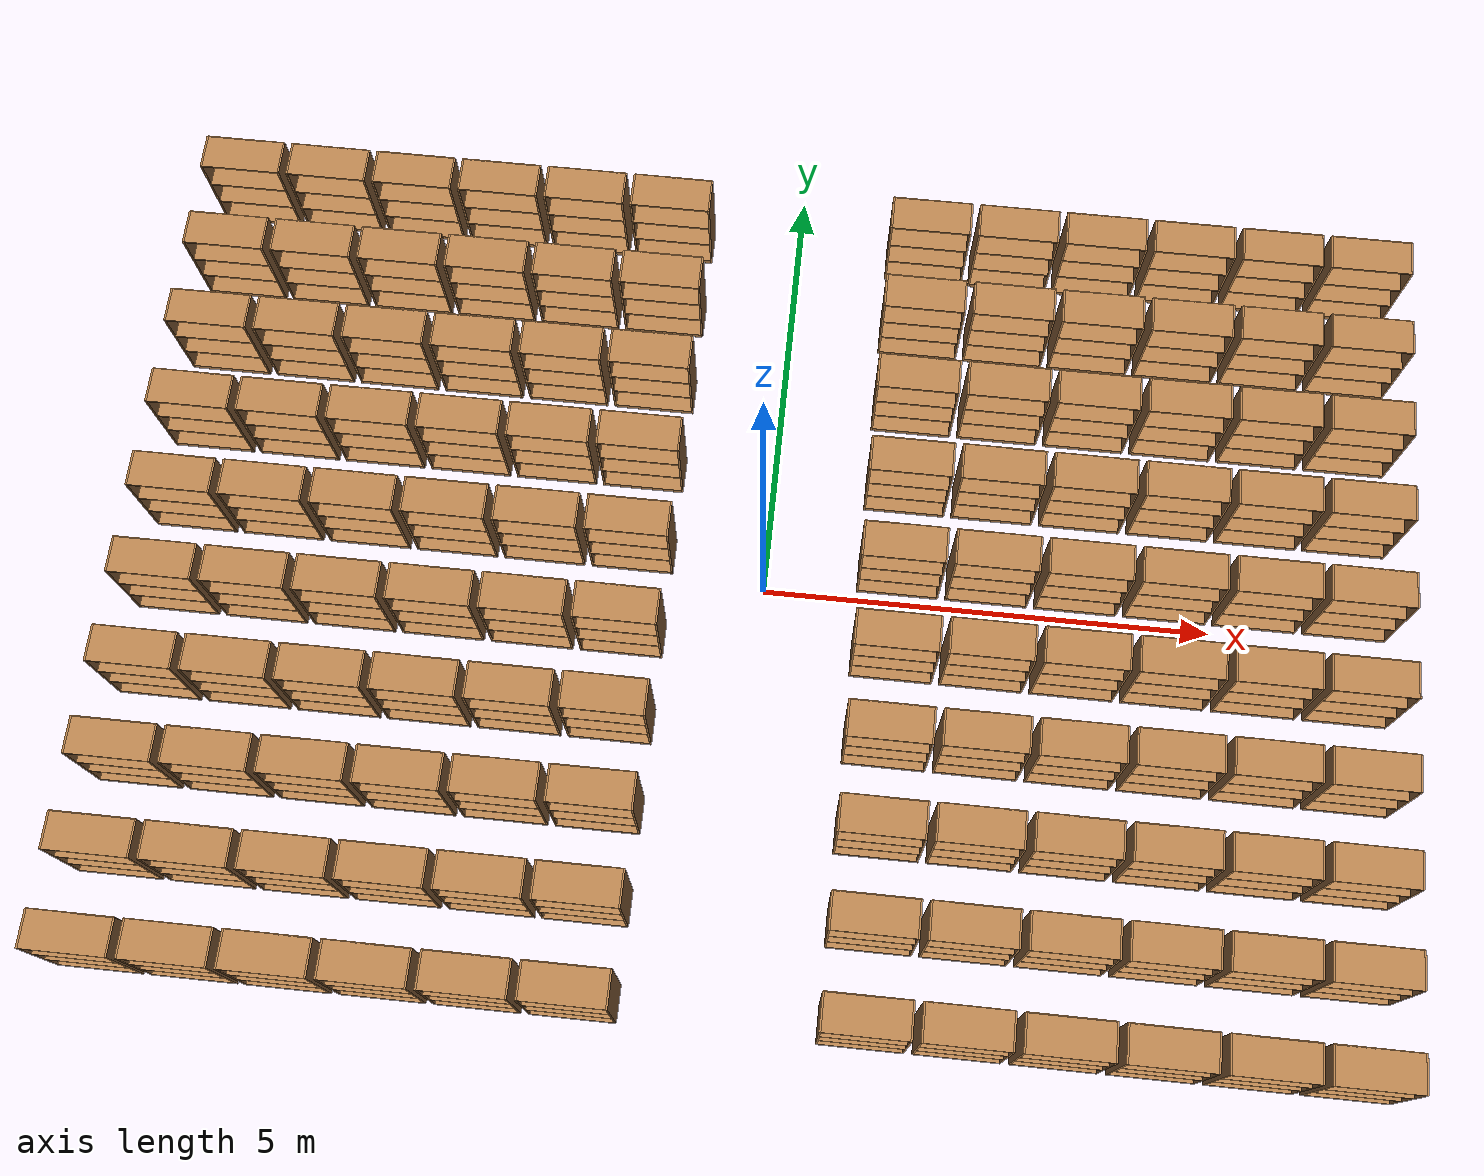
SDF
<?xml version='1.0'?>
<sdf version='1.6'>
  <model name='library'>
    <model name='5Bookshelves'>
      <model name='BookshelfRow'>
        <model name='bookshelf'>
          <static>1</static>
          <link name='link'>
            <inertial>
              <mass>1</mass>
            </inertial>
            <collision name='back'>
              <pose frame=''>0 0.005 0.6 0 -0 0</pose>
              <geometry>
                <box>
                  <size>0.9 0.01 1.2</size>
                </box>
              </geometry>
            </collision>
            <visual name='visual1'>
              <pose frame=''>0 0.005 0.6 0 -0 0</pose>
              <geometry>
                <box>
                  <size>0.9 0.01 1.2</size>
                </box>
              </geometry>
              <material>
                <script>
                  <uri>file://media/materials/scripts/gazebo.material</uri>
                  <name>Gazebo/Wood</name>
                </script>
              </material>
            </visual>
            <collision name='left_side'>
              <pose frame=''>0.45 -0.195 0.6 0 -0 0</pose>
              <geometry>
                <box>
                  <size>0.02 0.4 1.2</size>
                </box>
              </geometry>
            </collision>
            <visual name='visual2'>
              <pose frame=''>0.45 -0.195 0.6 0 -0 0</pose>
              <geometry>
                <box>
                  <size>0.02 0.4 1.2</size>
                </box>
              </geometry>
              <material>
                <script>
                  <uri>file://media/materials/scripts/gazebo.material</uri>
                  <name>Gazebo/Wood</name>
                </script>
              </material>
            </visual>
            <collision name='right_side'>
              <pose frame=''>-0.45 -0.195 0.6 0 -0 0</pose>
              <geometry>
                <box>
                  <size>0.02 0.4 1.2</size>
                </box>
              </geometry>
            </collision>
            <visual name='visual3'>
              <pose frame=''>-0.45 -0.195 0.6 0 -0 0</pose>
              <geometry>
                <box>
                  <size>0.02 0.4 1.2</size>
                </box>
              </geometry>
              <material>
                <script>
                  <uri>file://media/materials/scripts/gazebo.material</uri>
                  <name>Gazebo/Wood</name>
                </script>
              </material>
            </visual>
            <collision name='bottom'>
              <pose frame=''>0 -0.195 0.03 0 -0 0</pose>
              <geometry>
                <box>
                  <size>0.88 0.4 0.06</size>
                </box>
              </geometry>
            </collision>
            <visual name='visual4'>
              <pose frame=''>0 -0.195 0.03 0 -0 0</pose>
              <geometry>
                <box>
                  <size>0.88 0.4 0.06</size>
                </box>
              </geometry>
              <material>
                <script>
                  <uri>file://media/materials/scripts/gazebo.material</uri>
                  <name>Gazebo/Wood</name>
                </script>
              </material>
            </visual>
            <collision name='top'>
              <pose frame=''>0 -0.195 1.19 0 -0 0</pose>
              <geometry>
                <box>
                  <size>0.88 0.4 0.02</size>
                </box>
              </geometry>
            </collision>
            <visual name='visual5'>
              <pose frame=''>0 -0.195 1.19 0 -0 0</pose>
              <geometry>
                <box>
                  <size>0.88 0.4 0.02</size>
                </box>
              </geometry>
              <material>
                <script>
                  <uri>file://media/materials/scripts/gazebo.material</uri>
                  <name>Gazebo/Wood</name>
                </script>
              </material>
            </visual>
            <collision name='low_shelf'>
              <pose frame=''>0 -0.195 0.43 0 -0 0</pose>
              <geometry>
                <box>
                  <size>0.88 0.4 0.02</size>
                </box>
              </geometry>
            </collision>
            <visual name='visual6'>
              <pose frame=''>0 -0.195 0.43 0 -0 0</pose>
              <geometry>
                <box>
                  <size>0.88 0.4 0.02</size>
                </box>
              </geometry>
              <material>
                <script>
                  <uri>file://media/materials/scripts/gazebo.material</uri>
                  <name>Gazebo/Wood</name>
                </script>
              </material>
            </visual>
            <collision name='high_shelf'>
              <pose frame=''>0 -0.195 0.8 0 -0 0</pose>
              <geometry>
                <box>
                  <size>0.88 0.4 0.02</size>
                </box>
              </geometry>
            </collision>
            <visual name='visual7'>
              <pose frame=''>0 -0.195 0.8 0 -0 0</pose>
              <geometry>
                <box>
                  <size>0.88 0.4 0.02</size>
                </box>
              </geometry>
              <material>
                <script>
                  <uri>file://media/materials/scripts/gazebo.material</uri>
                  <name>Gazebo/Wood</name>
                </script>
              </material>
            </visual>
          </link>
          <pose frame=''>-2.5 0 0 0 -0 0</pose>
        </model>
        <model name='bookshelf_0'>
          <static>1</static>
          <link name='link'>
            <inertial>
              <mass>1</mass>
            </inertial>
            <collision name='back'>
              <pose frame=''>0 0.005 0.6 0 -0 0</pose>
              <geometry>
                <box>
                  <size>0.9 0.01 1.2</size>
                </box>
              </geometry>
            </collision>
            <visual name='visual1'>
              <pose frame=''>0 0.005 0.6 0 -0 0</pose>
              <geometry>
                <box>
                  <size>0.9 0.01 1.2</size>
                </box>
              </geometry>
              <material>
                <script>
                  <uri>file://media/materials/scripts/gazebo.material</uri>
                  <name>Gazebo/Wood</name>
                </script>
              </material>
            </visual>
            <collision name='left_side'>
              <pose frame=''>0.45 -0.195 0.6 0 -0 0</pose>
              <geometry>
                <box>
                  <size>0.02 0.4 1.2</size>
                </box>
              </geometry>
            </collision>
            <visual name='visual2'>
              <pose frame=''>0.45 -0.195 0.6 0 -0 0</pose>
              <geometry>
                <box>
                  <size>0.02 0.4 1.2</size>
                </box>
              </geometry>
              <material>
                <script>
                  <uri>file://media/materials/scripts/gazebo.material</uri>
                  <name>Gazebo/Wood</name>
                </script>
              </material>
            </visual>
            <collision name='right_side'>
              <pose frame=''>-0.45 -0.195 0.6 0 -0 0</pose>
              <geometry>
                <box>
                  <size>0.02 0.4 1.2</size>
                </box>
              </geometry>
            </collision>
            <visual name='visual3'>
              <pose frame=''>-0.45 -0.195 0.6 0 -0 0</pose>
              <geometry>
                <box>
                  <size>0.02 0.4 1.2</size>
                </box>
              </geometry>
              <material>
                <script>
                  <uri>file://media/materials/scripts/gazebo.material</uri>
                  <name>Gazebo/Wood</name>
                </script>
              </material>
            </visual>
            <collision name='bottom'>
              <pose frame=''>0 -0.195 0.03 0 -0 0</pose>
              <geometry>
                <box>
                  <size>0.88 0.4 0.06</size>
                </box>
              </geometry>
            </collision>
            <visual name='visual4'>
              <pose frame=''>0 -0.195 0.03 0 -0 0</pose>
              <geometry>
                <box>
                  <size>0.88 0.4 0.06</size>
                </box>
              </geometry>
              <material>
                <script>
                  <uri>file://media/materials/scripts/gazebo.material</uri>
                  <name>Gazebo/Wood</name>
                </script>
              </material>
            </visual>
            <collision name='top'>
              <pose frame=''>0 -0.195 1.19 0 -0 0</pose>
              <geometry>
                <box>
                  <size>0.88 0.4 0.02</size>
                </box>
              </geometry>
            </collision>
            <visual name='visual5'>
              <pose frame=''>0 -0.195 1.19 0 -0 0</pose>
              <geometry>
                <box>
                  <size>0.88 0.4 0.02</size>
                </box>
              </geometry>
              <material>
                <script>
                  <uri>file://media/materials/scripts/gazebo.material</uri>
                  <name>Gazebo/Wood</name>
                </script>
              </material>
            </visual>
            <collision name='low_shelf'>
              <pose frame=''>0 -0.195 0.43 0 -0 0</pose>
              <geometry>
                <box>
                  <size>0.88 0.4 0.02</size>
                </box>
              </geometry>
            </collision>
            <visual name='visual6'>
              <pose frame=''>0 -0.195 0.43 0 -0 0</pose>
              <geometry>
                <box>
                  <size>0.88 0.4 0.02</size>
                </box>
              </geometry>
              <material>
                <script>
                  <uri>file://media/materials/scripts/gazebo.material</uri>
                  <name>Gazebo/Wood</name>
                </script>
              </material>
            </visual>
            <collision name='high_shelf'>
              <pose frame=''>0 -0.195 0.8 0 -0 0</pose>
              <geometry>
                <box>
                  <size>0.88 0.4 0.02</size>
                </box>
              </geometry>
            </collision>
            <visual name='visual7'>
              <pose frame=''>0 -0.195 0.8 0 -0 0</pose>
              <geometry>
                <box>
                  <size>0.88 0.4 0.02</size>
                </box>
              </geometry>
              <material>
                <script>
                  <uri>file://media/materials/scripts/gazebo.material</uri>
                  <name>Gazebo/Wood</name>
                </script>
              </material>
            </visual>
          </link>
          <pose frame=''>-1.5 0 0 0 -0 0</pose>
        </model>
        <model name='bookshelf_1'>
          <static>1</static>
          <link name='link'>
            <inertial>
              <mass>1</mass>
            </inertial>
            <collision name='back'>
              <pose frame=''>0 0.005 0.6 0 -0 0</pose>
              <geometry>
                <box>
                  <size>0.9 0.01 1.2</size>
                </box>
              </geometry>
            </collision>
            <visual name='visual1'>
              <pose frame=''>0 0.005 0.6 0 -0 0</pose>
              <geometry>
                <box>
                  <size>0.9 0.01 1.2</size>
                </box>
              </geometry>
              <material>
                <script>
                  <uri>file://media/materials/scripts/gazebo.material</uri>
                  <name>Gazebo/Wood</name>
                </script>
              </material>
            </visual>
            <collision name='left_side'>
              <pose frame=''>0.45 -0.195 0.6 0 -0 0</pose>
              <geometry>
                <box>
                  <size>0.02 0.4 1.2</size>
                </box>
              </geometry>
            </collision>
            <visual name='visual2'>
              <pose frame=''>0.45 -0.195 0.6 0 -0 0</pose>
              <geometry>
                <box>
                  <size>0.02 0.4 1.2</size>
                </box>
              </geometry>
              <material>
                <script>
                  <uri>file://media/materials/scripts/gazebo.material</uri>
                  <name>Gazebo/Wood</name>
                </script>
              </material>
            </visual>
            <collision name='right_side'>
              <pose frame=''>-0.45 -0.195 0.6 0 -0 0</pose>
              <geometry>
                <box>
                  <size>0.02 0.4 1.2</size>
                </box>
              </geometry>
            </collision>
            <visual name='visual3'>
              <pose frame=''>-0.45 -0.195 0.6 0 -0 0</pose>
              <geometry>
                <box>
                  <size>0.02 0.4 1.2</size>
                </box>
              </geometry>
              <material>
                <script>
                  <uri>file://media/materials/scripts/gazebo.material</uri>
                  <name>Gazebo/Wood</name>
                </script>
              </material>
            </visual>
            <collision name='bottom'>
              <pose frame=''>0 -0.195 0.03 0 -0 0</pose>
              <geometry>
                <box>
                  <size>0.88 0.4 0.06</size>
                </box>
              </geometry>
            </collision>
            <visual name='visual4'>
              <pose frame=''>0 -0.195 0.03 0 -0 0</pose>
              <geometry>
                <box>
                  <size>0.88 0.4 0.06</size>
                </box>
              </geometry>
              <material>
                <script>
                  <uri>file://media/materials/scripts/gazebo.material</uri>
                  <name>Gazebo/Wood</name>
                </script>
              </material>
            </visual>
            <collision name='top'>
              <pose frame=''>0 -0.195 1.19 0 -0 0</pose>
              <geometry>
                <box>
                  <size>0.88 0.4 0.02</size>
                </box>
              </geometry>
            </collision>
            <visual name='visual5'>
              <pose frame=''>0 -0.195 1.19 0 -0 0</pose>
              <geometry>
                <box>
                  <size>0.88 0.4 0.02</size>
                </box>
              </geometry>
              <material>
                <script>
                  <uri>file://media/materials/scripts/gazebo.material</uri>
                  <name>Gazebo/Wood</name>
                </script>
              </material>
            </visual>
            <collision name='low_shelf'>
              <pose frame=''>0 -0.195 0.43 0 -0 0</pose>
              <geometry>
                <box>
                  <size>0.88 0.4 0.02</size>
                </box>
              </geometry>
            </collision>
            <visual name='visual6'>
              <pose frame=''>0 -0.195 0.43 0 -0 0</pose>
              <geometry>
                <box>
                  <size>0.88 0.4 0.02</size>
                </box>
              </geometry>
              <material>
                <script>
                  <uri>file://media/materials/scripts/gazebo.material</uri>
                  <name>Gazebo/Wood</name>
                </script>
              </material>
            </visual>
            <collision name='high_shelf'>
              <pose frame=''>0 -0.195 0.8 0 -0 0</pose>
              <geometry>
                <box>
                  <size>0.88 0.4 0.02</size>
                </box>
              </geometry>
            </collision>
            <visual name='visual7'>
              <pose frame=''>0 -0.195 0.8 0 -0 0</pose>
              <geometry>
                <box>
                  <size>0.88 0.4 0.02</size>
                </box>
              </geometry>
              <material>
                <script>
                  <uri>file://media/materials/scripts/gazebo.material</uri>
                  <name>Gazebo/Wood</name>
                </script>
              </material>
            </visual>
          </link>
          <pose frame=''>-0.5 0 0 0 -0 0</pose>
        </model>
        <model name='bookshelf_2'>
          <static>1</static>
          <link name='link'>
            <inertial>
              <mass>1</mass>
            </inertial>
            <collision name='back'>
              <pose frame=''>0 0.005 0.6 0 -0 0</pose>
              <geometry>
                <box>
                  <size>0.9 0.01 1.2</size>
                </box>
              </geometry>
            </collision>
            <visual name='visual1'>
              <pose frame=''>0 0.005 0.6 0 -0 0</pose>
              <geometry>
                <box>
                  <size>0.9 0.01 1.2</size>
                </box>
              </geometry>
              <material>
                <script>
                  <uri>file://media/materials/scripts/gazebo.material</uri>
                  <name>Gazebo/Wood</name>
                </script>
              </material>
            </visual>
            <collision name='left_side'>
              <pose frame=''>0.45 -0.195 0.6 0 -0 0</pose>
              <geometry>
                <box>
                  <size>0.02 0.4 1.2</size>
                </box>
              </geometry>
            </collision>
            <visual name='visual2'>
              <pose frame=''>0.45 -0.195 0.6 0 -0 0</pose>
              <geometry>
                <box>
                  <size>0.02 0.4 1.2</size>
                </box>
              </geometry>
              <material>
                <script>
                  <uri>file://media/materials/scripts/gazebo.material</uri>
                  <name>Gazebo/Wood</name>
                </script>
              </material>
            </visual>
            <collision name='right_side'>
              <pose frame=''>-0.45 -0.195 0.6 0 -0 0</pose>
              <geometry>
                <box>
                  <size>0.02 0.4 1.2</size>
                </box>
              </geometry>
            </collision>
            <visual name='visual3'>
              <pose frame=''>-0.45 -0.195 0.6 0 -0 0</pose>
              <geometry>
                <box>
                  <size>0.02 0.4 1.2</size>
                </box>
              </geometry>
              <material>
                <script>
                  <uri>file://media/materials/scripts/gazebo.material</uri>
                  <name>Gazebo/Wood</name>
                </script>
              </material>
            </visual>
            <collision name='bottom'>
              <pose frame=''>0 -0.195 0.03 0 -0 0</pose>
              <geometry>
                <box>
                  <size>0.88 0.4 0.06</size>
                </box>
              </geometry>
            </collision>
            <visual name='visual4'>
              <pose frame=''>0 -0.195 0.03 0 -0 0</pose>
              <geometry>
                <box>
                  <size>0.88 0.4 0.06</size>
                </box>
              </geometry>
              <material>
                <script>
                  <uri>file://media/materials/scripts/gazebo.material</uri>
                  <name>Gazebo/Wood</name>
                </script>
              </material>
            </visual>
            <collision name='top'>
              <pose frame=''>0 -0.195 1.19 0 -0 0</pose>
              <geometry>
                <box>
                  <size>0.88 0.4 0.02</size>
                </box>
              </geometry>
            </collision>
            <visual name='visual5'>
              <pose frame=''>0 -0.195 1.19 0 -0 0</pose>
              <geometry>
                <box>
                  <size>0.88 0.4 0.02</size>
                </box>
              </geometry>
              <material>
                <script>
                  <uri>file://media/materials/scripts/gazebo.material</uri>
                  <name>Gazebo/Wood</name>
                </script>
              </material>
            </visual>
            <collision name='low_shelf'>
              <pose frame=''>0 -0.195 0.43 0 -0 0</pose>
              <geometry>
                <box>
                  <size>0.88 0.4 0.02</size>
                </box>
              </geometry>
            </collision>
            <visual name='visual6'>
              <pose frame=''>0 -0.195 0.43 0 -0 0</pose>
              <geometry>
                <box>
                  <size>0.88 0.4 0.02</size>
                </box>
              </geometry>
              <material>
                <script>
                  <uri>file://media/materials/scripts/gazebo.material</uri>
                  <name>Gazebo/Wood</name>
                </script>
              </material>
            </visual>
            <collision name='high_shelf'>
              <pose frame=''>0 -0.195 0.8 0 -0 0</pose>
              <geometry>
                <box>
                  <size>0.88 0.4 0.02</size>
                </box>
              </geometry>
            </collision>
            <visual name='visual7'>
              <pose frame=''>0 -0.195 0.8 0 -0 0</pose>
              <geometry>
                <box>
                  <size>0.88 0.4 0.02</size>
                </box>
              </geometry>
              <material>
                <script>
                  <uri>file://media/materials/scripts/gazebo.material</uri>
                  <name>Gazebo/Wood</name>
                </script>
              </material>
            </visual>
          </link>
          <pose frame=''>0.5 0 0 0 -0 0</pose>
        </model>
        <model name='bookshelf_3'>
          <static>1</static>
          <link name='link'>
            <inertial>
              <mass>1</mass>
            </inertial>
            <collision name='back'>
              <pose frame=''>0 0.005 0.6 0 -0 0</pose>
              <geometry>
                <box>
                  <size>0.9 0.01 1.2</size>
                </box>
              </geometry>
            </collision>
            <visual name='visual1'>
              <pose frame=''>0 0.005 0.6 0 -0 0</pose>
              <geometry>
                <box>
                  <size>0.9 0.01 1.2</size>
                </box>
              </geometry>
              <material>
                <script>
                  <uri>file://media/materials/scripts/gazebo.material</uri>
                  <name>Gazebo/Wood</name>
                </script>
              </material>
            </visual>
            <collision name='left_side'>
              <pose frame=''>0.45 -0.195 0.6 0 -0 0</pose>
              <geometry>
                <box>
                  <size>0.02 0.4 1.2</size>
                </box>
              </geometry>
            </collision>
            <visual name='visual2'>
              <pose frame=''>0.45 -0.195 0.6 0 -0 0</pose>
              <geometry>
                <box>
                  <size>0.02 0.4 1.2</size>
                </box>
              </geometry>
              <material>
                <script>
                  <uri>file://media/materials/scripts/gazebo.material</uri>
                  <name>Gazebo/Wood</name>
                </script>
              </material>
            </visual>
            <collision name='right_side'>
              <pose frame=''>-0.45 -0.195 0.6 0 -0 0</pose>
              <geometry>
                <box>
                  <size>0.02 0.4 1.2</size>
                </box>
              </geometry>
            </collision>
            <visual name='visual3'>
              <pose frame=''>-0.45 -0.195 0.6 0 -0 0</pose>
              <geometry>
                <box>
                  <size>0.02 0.4 1.2</size>
                </box>
              </geometry>
              <material>
                <script>
                  <uri>file://media/materials/scripts/gazebo.material</uri>
                  <name>Gazebo/Wood</name>
                </script>
              </material>
            </visual>
            <collision name='bottom'>
              <pose frame=''>0 -0.195 0.03 0 -0 0</pose>
              <geometry>
                <box>
                  <size>0.88 0.4 0.06</size>
                </box>
              </geometry>
            </collision>
            <visual name='visual4'>
              <pose frame=''>0 -0.195 0.03 0 -0 0</pose>
              <geometry>
                <box>
                  <size>0.88 0.4 0.06</size>
                </box>
              </geometry>
              <material>
                <script>
                  <uri>file://media/materials/scripts/gazebo.material</uri>
                  <name>Gazebo/Wood</name>
                </script>
              </material>
            </visual>
            <collision name='top'>
              <pose frame=''>0 -0.195 1.19 0 -0 0</pose>
              <geometry>
                <box>
                  <size>0.88 0.4 0.02</size>
                </box>
              </geometry>
            </collision>
            <visual name='visual5'>
              <pose frame=''>0 -0.195 1.19 0 -0 0</pose>
              <geometry>
                <box>
                  <size>0.88 0.4 0.02</size>
                </box>
              </geometry>
              <material>
                <script>
                  <uri>file://media/materials/scripts/gazebo.material</uri>
                  <name>Gazebo/Wood</name>
                </script>
              </material>
            </visual>
            <collision name='low_shelf'>
              <pose frame=''>0 -0.195 0.43 0 -0 0</pose>
              <geometry>
                <box>
                  <size>0.88 0.4 0.02</size>
                </box>
              </geometry>
            </collision>
            <visual name='visual6'>
              <pose frame=''>0 -0.195 0.43 0 -0 0</pose>
              <geometry>
                <box>
                  <size>0.88 0.4 0.02</size>
                </box>
              </geometry>
              <material>
                <script>
                  <uri>file://media/materials/scripts/gazebo.material</uri>
                  <name>Gazebo/Wood</name>
                </script>
              </material>
            </visual>
            <collision name='high_shelf'>
              <pose frame=''>0 -0.195 0.8 0 -0 0</pose>
              <geometry>
                <box>
                  <size>0.88 0.4 0.02</size>
                </box>
              </geometry>
            </collision>
            <visual name='visual7'>
              <pose frame=''>0 -0.195 0.8 0 -0 0</pose>
              <geometry>
                <box>
                  <size>0.88 0.4 0.02</size>
                </box>
              </geometry>
              <material>
                <script>
                  <uri>file://media/materials/scripts/gazebo.material</uri>
                  <name>Gazebo/Wood</name>
                </script>
              </material>
            </visual>
          </link>
          <pose frame=''>1.5 0 0 0 -0 0</pose>
        </model>
        <model name='bookshelf_4'>
          <static>1</static>
          <link name='link'>
            <inertial>
              <mass>1</mass>
            </inertial>
            <collision name='back'>
              <pose frame=''>0 0.005 0.6 0 -0 0</pose>
              <geometry>
                <box>
                  <size>0.9 0.01 1.2</size>
                </box>
              </geometry>
            </collision>
            <visual name='visual1'>
              <pose frame=''>0 0.005 0.6 0 -0 0</pose>
              <geometry>
                <box>
                  <size>0.9 0.01 1.2</size>
                </box>
              </geometry>
              <material>
                <script>
                  <uri>file://media/materials/scripts/gazebo.material</uri>
                  <name>Gazebo/Wood</name>
                </script>
              </material>
            </visual>
            <collision name='left_side'>
              <pose frame=''>0.45 -0.195 0.6 0 -0 0</pose>
              <geometry>
                <box>
                  <size>0.02 0.4 1.2</size>
                </box>
              </geometry>
            </collision>
            <visual name='visual2'>
              <pose frame=''>0.45 -0.195 0.6 0 -0 0</pose>
              <geometry>
                <box>
                  <size>0.02 0.4 1.2</size>
                </box>
              </geometry>
              <material>
                <script>
                  <uri>file://media/materials/scripts/gazebo.material</uri>
                  <name>Gazebo/Wood</name>
                </script>
              </material>
            </visual>
            <collision name='right_side'>
              <pose frame=''>-0.45 -0.195 0.6 0 -0 0</pose>
              <geometry>
                <box>
                  <size>0.02 0.4 1.2</size>
                </box>
              </geometry>
            </collision>
            <visual name='visual3'>
              <pose frame=''>-0.45 -0.195 0.6 0 -0 0</pose>
              <geometry>
                <box>
                  <size>0.02 0.4 1.2</size>
                </box>
              </geometry>
              <material>
                <script>
                  <uri>file://media/materials/scripts/gazebo.material</uri>
                  <name>Gazebo/Wood</name>
                </script>
              </material>
            </visual>
            <collision name='bottom'>
              <pose frame=''>0 -0.195 0.03 0 -0 0</pose>
              <geometry>
                <box>
                  <size>0.88 0.4 0.06</size>
                </box>
              </geometry>
            </collision>
            <visual name='visual4'>
              <pose frame=''>0 -0.195 0.03 0 -0 0</pose>
              <geometry>
                <box>
                  <size>0.88 0.4 0.06</size>
                </box>
              </geometry>
              <material>
                <script>
                  <uri>file://media/materials/scripts/gazebo.material</uri>
                  <name>Gazebo/Wood</name>
                </script>
              </material>
            </visual>
            <collision name='top'>
              <pose frame=''>0 -0.195 1.19 0 -0 0</pose>
              <geometry>
                <box>
                  <size>0.88 0.4 0.02</size>
                </box>
              </geometry>
            </collision>
            <visual name='visual5'>
              <pose frame=''>0 -0.195 1.19 0 -0 0</pose>
              <geometry>
                <box>
                  <size>0.88 0.4 0.02</size>
                </box>
              </geometry>
              <material>
                <script>
                  <uri>file://media/materials/scripts/gazebo.material</uri>
                  <name>Gazebo/Wood</name>
                </script>
              </material>
            </visual>
            <collision name='low_shelf'>
              <pose frame=''>0 -0.195 0.43 0 -0 0</pose>
              <geometry>
                <box>
                  <size>0.88 0.4 0.02</size>
                </box>
              </geometry>
            </collision>
            <visual name='visual6'>
              <pose frame=''>0 -0.195 0.43 0 -0 0</pose>
              <geometry>
                <box>
                  <size>0.88 0.4 0.02</size>
                </box>
              </geometry>
              <material>
                <script>
                  <uri>file://media/materials/scripts/gazebo.material</uri>
                  <name>Gazebo/Wood</name>
                </script>
              </material>
            </visual>
            <collision name='high_shelf'>
              <pose frame=''>0 -0.195 0.8 0 -0 0</pose>
              <geometry>
                <box>
                  <size>0.88 0.4 0.02</size>
                </box>
              </geometry>
            </collision>
            <visual name='visual7'>
              <pose frame=''>0 -0.195 0.8 0 -0 0</pose>
              <geometry>
                <box>
                  <size>0.88 0.4 0.02</size>
                </box>
              </geometry>
              <material>
                <script>
                  <uri>file://media/materials/scripts/gazebo.material</uri>
                  <name>Gazebo/Wood</name>
                </script>
              </material>
            </visual>
          </link>
          <pose frame=''>2.5 0 0 0 -0 0</pose>
        </model>
        <static>0</static>
        <allow_auto_disable>1</allow_auto_disable>
        <pose frame=''>0 -2 0 0 -0 0</pose>
      </model>
      <model name='BookshelfRow_0'>
        <model name='bookshelf'>
          <static>1</static>
          <link name='link'>
            <inertial>
              <mass>1</mass>
            </inertial>
            <collision name='back'>
              <pose frame=''>0 0.005 0.6 0 -0 0</pose>
              <geometry>
                <box>
                  <size>0.9 0.01 1.2</size>
                </box>
              </geometry>
            </collision>
            <visual name='visual1'>
              <pose frame=''>0 0.005 0.6 0 -0 0</pose>
              <geometry>
                <box>
                  <size>0.9 0.01 1.2</size>
                </box>
              </geometry>
              <material>
                <script>
                  <uri>file://media/materials/scripts/gazebo.material</uri>
                  <name>Gazebo/Wood</name>
                </script>
              </material>
            </visual>
            <collision name='left_side'>
              <pose frame=''>0.45 -0.195 0.6 0 -0 0</pose>
              <geometry>
                <box>
                  <size>0.02 0.4 1.2</size>
                </box>
              </geometry>
            </collision>
            <visual name='visual2'>
              <pose frame=''>0.45 -0.195 0.6 0 -0 0</pose>
              <geometry>
                <box>
                  <size>0.02 0.4 1.2</size>
                </box>
              </geometry>
              <material>
                <script>
                  <uri>file://media/materials/scripts/gazebo.material</uri>
                  <name>Gazebo/Wood</name>
                </script>
              </material>
            </visual>
            <collision name='right_side'>
              <pose frame=''>-0.45 -0.195 0.6 0 -0 0</pose>
              <geometry>
                <box>
                  <size>0.02 0.4 1.2</size>
                </box>
              </geometry>
            </collision>
            <visual name='visual3'>
              <pose frame=''>-0.45 -0.195 0.6 0 -0 0</pose>
              <geometry>
                <box>
                  <size>0.02 0.4 1.2</size>
                </box>
              </geometry>
              <material>
                <script>
                  <uri>file://media/materials/scripts/gazebo.material</uri>
                  <name>Gazebo/Wood</name>
                </script>
              </material>
            </visual>
            <collision name='bottom'>
              <pose frame=''>0 -0.195 0.03 0 -0 0</pose>
              <geometry>
                <box>
                  <size>0.88 0.4 0.06</size>
                </box>
              </geometry>
            </collision>
            <visual name='visual4'>
              <pose frame=''>0 -0.195 0.03 0 -0 0</pose>
              <geometry>
                <box>
                  <size>0.88 0.4 0.06</size>
                </box>
              </geometry>
              <material>
                <script>
                  <uri>file://media/materials/scripts/gazebo.material</uri>
                  <name>Gazebo/Wood</name>
                </script>
              </material>
            </visual>
            <collision name='top'>
              <pose frame=''>0 -0.195 1.19 0 -0 0</pose>
              <geometry>
                <box>
                  <size>0.88 0.4 0.02</size>
                </box>
              </geometry>
            </collision>
            <visual name='visual5'>
              <pose frame=''>0 -0.195 1.19 0 -0 0</pose>
              <geometry>
                <box>
                  <size>0.88 0.4 0.02</size>
                </box>
              </geometry>
              <material>
                <script>
                  <uri>file://media/materials/scripts/gazebo.material</uri>
                  <name>Gazebo/Wood</name>
                </script>
              </material>
            </visual>
            <collision name='low_shelf'>
              <pose frame=''>0 -0.195 0.43 0 -0 0</pose>
              <geometry>
                <box>
                  <size>0.88 0.4 0.02</size>
                </box>
              </geometry>
            </collision>
            <visual name='visual6'>
              <pose frame=''>0 -0.195 0.43 0 -0 0</pose>
              <geometry>
                <box>
                  <size>0.88 0.4 0.02</size>
                </box>
              </geometry>
              <material>
                <script>
                  <uri>file://media/materials/scripts/gazebo.material</uri>
                  <name>Gazebo/Wood</name>
                </script>
              </material>
            </visual>
            <collision name='high_shelf'>
              <pose frame=''>0 -0.195 0.8 0 -0 0</pose>
              <geometry>
                <box>
                  <size>0.88 0.4 0.02</size>
                </box>
              </geometry>
            </collision>
            <visual name='visual7'>
              <pose frame=''>0 -0.195 0.8 0 -0 0</pose>
              <geometry>
                <box>
                  <size>0.88 0.4 0.02</size>
                </box>
              </geometry>
              <material>
                <script>
                  <uri>file://media/materials/scripts/gazebo.material</uri>
                  <name>Gazebo/Wood</name>
                </script>
              </material>
            </visual>
          </link>
          <pose frame=''>-2.5 0 0 0 -0 0</pose>
        </model>
        <model name='bookshelf_0'>
          <static>1</static>
          <link name='link'>
            <inertial>
              <mass>1</mass>
            </inertial>
            <collision name='back'>
              <pose frame=''>0 0.005 0.6 0 -0 0</pose>
              <geometry>
                <box>
                  <size>0.9 0.01 1.2</size>
                </box>
              </geometry>
            </collision>
            <visual name='visual1'>
              <pose frame=''>0 0.005 0.6 0 -0 0</pose>
              <geometry>
                <box>
                  <size>0.9 0.01 1.2</size>
                </box>
              </geometry>
              <material>
                <script>
                  <uri>file://media/materials/scripts/gazebo.material</uri>
                  <name>Gazebo/Wood</name>
                </script>
              </material>
            </visual>
            <collision name='left_side'>
              <pose frame=''>0.45 -0.195 0.6 0 -0 0</pose>
              <geometry>
                <box>
                  <size>0.02 0.4 1.2</size>
                </box>
              </geometry>
            </collision>
            <visual name='visual2'>
              <pose frame=''>0.45 -0.195 0.6 0 -0 0</pose>
              <geometry>
                <box>
                  <size>0.02 0.4 1.2</size>
                </box>
              </geometry>
              <material>
                <script>
                  <uri>file://media/materials/scripts/gazebo.material</uri>
                  <name>Gazebo/Wood</name>
                </script>
              </material>
            </visual>
            <collision name='right_side'>
              <pose frame=''>-0.45 -0.195 0.6 0 -0 0</pose>
              <geometry>
                <box>
                  <size>0.02 0.4 1.2</size>
                </box>
              </geometry>
            </collision>
            <visual name='visual3'>
              <pose frame=''>-0.45 -0.195 0.6 0 -0 0</pose>
              <geometry>
                <box>
                  <size>0.02 0.4 1.2</size>
                </box>
              </geometry>
              <material>
                <script>
                  <uri>file://media/materials/scripts/gazebo.material</uri>
                  <name>Gazebo/Wood</name>
                </script>
              </material>
            </visual>
            <collision name='bottom'>
              <pose frame=''>0 -0.195 0.03 0 -0 0</pose>
              <geometry>
                <box>
                  <size>0.88 0.4 0.06</size>
                </box>
              </geometry>
            </collision>
            <visual name='visual4'>
              <pose frame=''>0 -0.195 0.03 0 -0 0</pose>
              <geometry>
                <box>
                  <size>0.88 0.4 0.06</size>
                </box>
              </geometry>
              <material>
                <script>
                  <uri>file://media/materials/scripts/gazebo.material</uri>
                  <name>Gazebo/Wood</name>
                </script>
              </material>
            </visual>
            <collision name='top'>
              <pose frame=''>0 -0.195 1.19 0 -0 0</pose>
              <geometry>
                <box>
                  <size>0.88 0.4 0.02</size>
                </box>
              </geometry>
            </collision>
            <visual name='visual5'>
              <pose frame=''>0 -0.195 1.19 0 -0 0</pose>
              <geometry>
                <box>
                  <size>0.88 0.4 0.02</size>
                </box>
              </geometry>
              <material>
                <script>
                  <uri>file://media/materials/scripts/gazebo.material</uri>
                  <name>Gazebo/Wood</name>
                </script>
              </material>
            </visual>
            <collision name='low_shelf'>
              <pose frame=''>0 -0.195 0.43 0 -0 0</pose>
              <geometry>
                <box>
                  <size>0.88 0.4 0.02</size>
                </box>
              </geometry>
            </collision>
            <visual name='visual6'>
              <pose frame=''>0 -0.195 0.43 0 -0 0</pose>
              <geometry>
                <box>
                  <size>0.88 0.4 0.02</size>
                </box>
              </geometry>
              <material>
                <script>
                  <uri>file://media/materials/scripts/gazebo.material</uri>
                  <name>Gazebo/Wood</name>
                </script>
              </material>
            </visual>
            <collision name='high_shelf'>
              <pose frame=''>0 -0.195 0.8 0 -0 0</pose>
              <geometry>
                <box>
                  <size>0.88 0.4 0.02</size>
                </box>
              </geometry>
            </collision>
            <visual name='visual7'>
              <pose frame=''>0 -0.195 0.8 0 -0 0</pose>
              <geometry>
                <box>
                  <size>0.88 0.4 0.02</size>
                </box>
              </geometry>
              <material>
                <script>
                  <uri>file://media/materials/scripts/gazebo.material</uri>
                  <name>Gazebo/Wood</name>
                </script>
              </material>
            </visual>
          </link>
          <pose frame=''>-1.5 0 0 0 -0 0</pose>
        </model>
        <model name='bookshelf_1'>
          <static>1</static>
          <link name='link'>
            <inertial>
              <mass>1</mass>
            </inertial>
            <collision name='back'>
              <pose frame=''>0 0.005 0.6 0 -0 0</pose>
              <geometry>
                <box>
                  <size>0.9 0.01 1.2</size>
                </box>
              </geometry>
            </collision>
            <visual name='visual1'>
              <pose frame=''>0 0.005 0.6 0 -0 0</pose>
              <geometry>
                <box>
                  <size>0.9 0.01 1.2</size>
                </box>
              </geometry>
              <material>
                <script>
                  <uri>file://media/materials/scripts/gazebo.material</uri>
                  <name>Gazebo/Wood</name>
                </script>
              </material>
            </visual>
            <collision name='left_side'>
              <pose frame=''>0.45 -0.195 0.6 0 -0 0</pose>
              <geometry>
                <box>
                  <size>0.02 0.4 1.2</size>
                </box>
              </geometry>
            </collision>
            <visual name='visual2'>
              <pose frame=''>0.45 -0.195 0.6 0 -0 0</pose>
              <geometry>
                <box>
                  <size>0.02 0.4 1.2</size>
                </box>
              </geometry>
              <material>
                <script>
                  <uri>file://media/materials/scripts/gazebo.material</uri>
                  <name>Gazebo/Wood</name>
                </script>
              </material>
            </visual>
            <collision name='right_side'>
              <pose frame=''>-0.45 -0.195 0.6 0 -0 0</pose>
              <geometry>
                <box>
                  <size>0.02 0.4 1.2</size>
                </box>
              </geometry>
            </collision>
            <visual name='visual3'>
              <pose frame=''>-0.45 -0.195 0.6 0 -0 0</pose>
              <geometry>
                <box>
                  <size>0.02 0.4 1.2</size>
                </box>
              </geometry>
              <material>
                <script>
                  <uri>file://media/materials/scripts/gazebo.material</uri>
                  <name>Gazebo/Wood</name>
                </script>
              </material>
            </visual>
            <collision name='bottom'>
              <pose frame=''>0 -0.195 0.03 0 -0 0</pose>
              <geometry>
                <box>
                  <size>0.88 0.4 0.06</size>
                </box>
              </geometry>
            </collision>
            <visual name='visual4'>
              <pose frame=''>0 -0.195 0.03 0 -0 0</pose>
              <geometry>
                <box>
                  <size>0.88 0.4 0.06</size>
                </box>
              </geometry>
              <material>
                <script>
                  <uri>file://media/materials/scripts/gazebo.material</uri>
                  <name>Gazebo/Wood</name>
                </script>
              </material>
            </visual>
            <collision name='top'>
              <pose frame=''>0 -0.195 1.19 0 -0 0</pose>
              <geometry>
                <box>
                  <size>0.88 0.4 0.02</size>
                </box>
              </geometry>
            </collision>
            <visual name='visual5'>
              <pose frame=''>0 -0.195 1.19 0 -0 0</pose>
              <geometry>
                <box>
                  <size>0.88 0.4 0.02</size>
                </box>
              </geometry>
              <material>
                <script>
                  <uri>file://media/materials/scripts/gazebo.material</uri>
                  <name>Gazebo/Wood</name>
                </script>
              </material>
            </visual>
            <collision name='low_shelf'>
              <pose frame=''>0 -0.195 0.43 0 -0 0</pose>
              <geometry>
                <box>
                  <size>0.88 0.4 0.02</size>
                </box>
              </geometry>
            </collision>
            <visual name='visual6'>
              <pose frame=''>0 -0.195 0.43 0 -0 0</pose>
              <geometry>
                <box>
                  <size>0.88 0.4 0.02</size>
                </box>
              </geometry>
              <material>
                <script>
                  <uri>file://media/materials/scripts/gazebo.material</uri>
                  <name>Gazebo/Wood</name>
                </script>
              </material>
            </visual>
            <collision name='high_shelf'>
              <pose frame=''>0 -0.195 0.8 0 -0 0</pose>
              <geometry>
                <box>
                  <size>0.88 0.4 0.02</size>
                </box>
              </geometry>
            </collision>
            <visual name='visual7'>
              <pose frame=''>0 -0.195 0.8 0 -0 0</pose>
              <geometry>
                <box>
                  <size>0.88 0.4 0.02</size>
                </box>
              </geometry>
              <material>
                <script>
                  <uri>file://media/materials/scripts/gazebo.material</uri>
                  <name>Gazebo/Wood</name>
                </script>
              </material>
            </visual>
          </link>
          <pose frame=''>-0.5 0 0 0 -0 0</pose>
        </model>
        <model name='bookshelf_2'>
          <static>1</static>
          <link name='link'>
            <inertial>
              <mass>1</mass>
            </inertial>
            <collision name='back'>
              <pose frame=''>0 0.005 0.6 0 -0 0</pose>
              <geometry>
                <box>
                  <size>0.9 0.01 1.2</size>
                </box>
              </geometry>
            </collision>
            <visual name='visual1'>
              <pose frame=''>0 0.005 0.6 0 -0 0</pose>
              <geometry>
                <box>
                  <size>0.9 0.01 1.2</size>
                </box>
              </geometry>
              <material>
                <script>
                  <uri>file://media/materials/scripts/gazebo.material</uri>
                  <name>Gazebo/Wood</name>
                </script>
              </material>
            </visual>
            <collision name='left_side'>
              <pose frame=''>0.45 -0.195 0.6 0 -0 0</pose>
              <geometry>
                <box>
                  <size>0.02 0.4 1.2</size>
                </box>
              </geometry>
            </collision>
            <visual name='visual2'>
              <pose frame=''>0.45 -0.195 0.6 0 -0 0</pose>
              <geometry>
                <box>
                  <size>0.02 0.4 1.2</size>
                </box>
              </geometry>
              <material>
                <script>
                  <uri>file://media/materials/scripts/gazebo.material</uri>
                  <name>Gazebo/Wood</name>
                </script>
              </material>
            </visual>
            <collision name='right_side'>
              <pose frame=''>-0.45 -0.195 0.6 0 -0 0</pose>
              <geometry>
                <box>
                  <size>0.02 0.4 1.2</size>
                </box>
              </geometry>
            </collision>
            <visual name='visual3'>
              <pose frame=''>-0.45 -0.195 0.6 0 -0 0</pose>
              <geometry>
                <box>
                  <size>0.02 0.4 1.2</size>
                </box>
              </geometry>
              <material>
                <script>
                  <uri>file://media/materials/scripts/gazebo.material</uri>
                  <name>Gazebo/Wood</name>
                </script>
              </material>
            </visual>
            <collision name='bottom'>
              <pose frame=''>0 -0.195 0.03 0 -0 0</pose>
              <geometry>
                <box>
                  <size>0.88 0.4 0.06</size>
                </box>
              </geometry>
            </collision>
            <visual name='visual4'>
              <pose frame=''>0 -0.195 0.03 0 -0 0</pose>
              <geometry>
                <box>
                  <size>0.88 0.4 0.06</size>
                </box>
              </geometry>
              <material>
                <script>
                  <uri>file://media/materials/scripts/gazebo.material</uri>
                  <name>Gazebo/Wood</name>
                </script>
              </material>
            </visual>
            <collision name='top'>
              <pose frame=''>0 -0.195 1.19 0 -0 0</pose>
              <geometry>
                <box>
                  <size>0.88 0.4 0.02</size>
                </box>
              </geometry>
            </collision>
            <visual name='visual5'>
              <pose frame=''>0 -0.195 1.19 0 -0 0</pose>
              <geometry>
                <box>
                  <size>0.88 0.4 0.02</size>
                </box>
              </geometry>
              <material>
                <script>
                  <uri>file://media/materials/scripts/gazebo.material</uri>
                  <name>Gazebo/Wood</name>
                </script>
              </material>
            </visual>
            <collision name='low_shelf'>
              <pose frame=''>0 -0.195 0.43 0 -0 0</pose>
              <geometry>
                <box>
                  <size>0.88 0.4 0.02</size>
                </box>
              </geometry>
            </collision>
            <visual name='visual6'>
              <pose frame=''>0 -0.195 0.43 0 -0 0</pose>
              <geometry>
                <box>
                  <size>0.88 0.4 0.02</size>
                </box>
              </geometry>
              <material>
                <script>
                  <uri>file://media/materials/scripts/gazebo.material</uri>
                  <name>Gazebo/Wood</name>
                </script>
              </material>
            </visual>
            <collision name='high_shelf'>
              <pose frame=''>0 -0.195 0.8 0 -0 0</pose>
              <geometry>
                <box>
                  <size>0.88 0.4 0.02</size>
                </box>
              </geometry>
            </collision>
            <visual name='visual7'>
              <pose frame=''>0 -0.195 0.8 0 -0 0</pose>
              <geometry>
                <box>
                  <size>0.88 0.4 0.02</size>
                </box>
              </geometry>
              <material>
                <script>
                  <uri>file://media/materials/scripts/gazebo.material</uri>
                  <name>Gazebo/Wood</name>
                </script>
              </material>
            </visual>
          </link>
          <pose frame=''>0.5 0 0 0 -0 0</pose>
        </model>
        <model name='bookshelf_3'>
          <static>1</static>
          <link name='link'>
            <inertial>
              <mass>1</mass>
            </inertial>
            <collision name='back'>
              <pose frame=''>0 0.005 0.6 0 -0 0</pose>
              <geometry>
                <box>
                  <size>0.9 0.01 1.2</size>
                </box>
              </geometry>
            </collision>
            <visual name='visual1'>
              <pose frame=''>0 0.005 0.6 0 -0 0</pose>
              <geometry>
                <box>
                  <size>0.9 0.01 1.2</size>
                </box>
              </geometry>
              <material>
                <script>
                  <uri>file://media/materials/scripts/gazebo.material</uri>
                  <name>Gazebo/Wood</name>
                </script>
              </material>
            </visual>
            <collision name='left_side'>
              <pose frame=''>0.45 -0.195 0.6 0 -0 0</pose>
              <geometry>
                <box>
                  <size>0.02 0.4 1.2</size>
                </box>
              </geometry>
            </collision>
            <visual name='visual2'>
              <pose frame=''>0.45 -0.195 0.6 0 -0 0</pose>
              <geometry>
                <box>
                  <size>0.02 0.4 1.2</size>
                </box>
              </geometry>
              <material>
                <script>
                  <uri>file://media/materials/scripts/gazebo.material</uri>
                  <name>Gazebo/Wood</name>
                </script>
              </material>
            </visual>
            <collision name='right_side'>
              <pose frame=''>-0.45 -0.195 0.6 0 -0 0</pose>
              <geometry>
                <box>
                  <size>0.02 0.4 1.2</size>
                </box>
              </geometry>
            </collision>
            <visual name='visual3'>
              <pose frame=''>-0.45 -0.195 0.6 0 -0 0</pose>
              <geometry>
                <box>
                  <size>0.02 0.4 1.2</size>
                </box>
              </geometry>
              <material>
                <script>
                  <uri>file://media/materials/scripts/gazebo.material</uri>
                  <name>Gazebo/Wood</name>
                </script>
              </material>
            </visual>
            <collision name='bottom'>
              <pose frame=''>0 -0.195 0.03 0 -0 0</pose>
              <geometry>
                <box>
                  <size>0.88 0.4 0.06</size>
                </box>
              </geometry>
            </collision>
            <visual name='visual4'>
              <pose frame=''>0 -0.195 0.03 0 -0 0</pose>
              <geometry>
                <box>
                  <size>0.88 0.4 0.06</size>
                </box>
              </geometry>
              <material>
                <script>
                  <uri>file://media/materials/scripts/gazebo.material</uri>
                  <name>Gazebo/Wood</name>
                </script>
              </material>
            </visual>
            <collision name='top'>
              <pose frame=''>0 -0.195 1.19 0 -0 0</pose>
              <geometry>
                <box>
                  <size>0.88 0.4 0.02</size>
                </box>
              </geometry>
            </collision>
            <visual name='visual5'>
              <pose frame=''>0 -0.195 1.19 0 -0 0</pose>
              <geometry>
                <box>
                  <size>0.88 0.4 0.02</size>
                </box>
              </geometry>
              <material>
                <script>
                  <uri>file://media/materials/scripts/gazebo.material</uri>
                  <name>Gazebo/Wood</name>
                </script>
              </material>
            </visual>
            <collision name='low_shelf'>
              <pose frame=''>0 -0.195 0.43 0 -0 0</pose>
              <geometry>
                <box>
                  <size>0.88 0.4 0.02</size>
                </box>
              </geometry>
            </collision>
            <visual name='visual6'>
              <pose frame=''>0 -0.195 0.43 0 -0 0</pose>
              <geometry>
                <box>
                  <size>0.88 0.4 0.02</size>
                </box>
              </geometry>
              <material>
                <script>
                  <uri>file://media/materials/scripts/gazebo.material</uri>
                  <name>Gazebo/Wood</name>
                </script>
              </material>
            </visual>
            <collision name='high_shelf'>
              <pose frame=''>0 -0.195 0.8 0 -0 0</pose>
              <geometry>
                <box>
                  <size>0.88 0.4 0.02</size>
                </box>
              </geometry>
            </collision>
            <visual name='visual7'>
              <pose frame=''>0 -0.195 0.8 0 -0 0</pose>
              <geometry>
                <box>
                  <size>0.88 0.4 0.02</size>
                </box>
              </geometry>
              <material>
                <script>
                  <uri>file://media/materials/scripts/gazebo.material</uri>
                  <name>Gazebo/Wood</name>
                </script>
              </material>
            </visual>
          </link>
          <pose frame=''>1.5 0 0 0 -0 0</pose>
        </model>
        <model name='bookshelf_4'>
          <static>1</static>
          <link name='link'>
            <inertial>
              <mass>1</mass>
            </inertial>
            <collision name='back'>
              <pose frame=''>0 0.005 0.6 0 -0 0</pose>
              <geometry>
                <box>
                  <size>0.9 0.01 1.2</size>
                </box>
              </geometry>
            </collision>
            <visual name='visual1'>
              <pose frame=''>0 0.005 0.6 0 -0 0</pose>
              <geometry>
                <box>
                  <size>0.9 0.01 1.2</size>
                </box>
              </geometry>
              <material>
                <script>
                  <uri>file://media/materials/scripts/gazebo.material</uri>
                  <name>Gazebo/Wood</name>
                </script>
              </material>
            </visual>
            <collision name='left_side'>
              <pose frame=''>0.45 -0.195 0.6 0 -0 0</pose>
              <geometry>
                <box>
                  <size>0.02 0.4 1.2</size>
                </box>
              </geometry>
            </collision>
            <visual name='visual2'>
              <pose frame=''>0.45 -0.195 0.6 0 -0 0</pose>
              <geometry>
                <box>
                  <size>0.02 0.4 1.2</size>
                </box>
              </geometry>
              <material>
                <script>
                  <uri>file://media/materials/scripts/gazebo.material</uri>
                  <name>Gazebo/Wood</name>
                </script>
              </material>
            </visual>
            <collision name='right_side'>
              <pose frame=''>-0.45 -0.195 0.6 0 -0 0</pose>
              <geometry>
                <box>
                  <size>0.02 0.4 1.2</size>
                </box>
              </geometry>
            </collision>
            <visual name='visual3'>
              <pose frame=''>-0.45 -0.195 0.6 0 -0 0</pose>
              <geometry>
                <box>
                  <size>0.02 0.4 1.2</size>
                </box>
              </geometry>
              <material>
                <script>
                  <uri>file://media/materials/scripts/gazebo.material</uri>
                  <name>Gazebo/Wood</name>
                </script>
              </material>
            </visual>
            <collision name='bottom'>
              <pose frame=''>0 -0.195 0.03 0 -0 0</pose>
              <geometry>
                <box>
                  <size>0.88 0.4 0.06</size>
                </box>
              </geometry>
            </collision>
            <visual name='visual4'>
              <pose frame=''>0 -0.195 0.03 0 -0 0</pose>
              <geometry>
                <box>
                  <size>0.88 0.4 0.06</size>
                </box>
              </geometry>
              <material>
                <script>
                  <uri>file://media/materials/scripts/gazebo.material</uri>
                  <name>Gazebo/Wood</name>
                </script>
              </material>
            </visual>
            <collision name='top'>
              <pose frame=''>0 -0.195 1.19 0 -0 0</pose>
              <geometry>
                <box>
                  <size>0.88 0.4 0.02</size>
                </box>
              </geometry>
            </collision>
            <visual name='visual5'>
              <pose frame=''>0 -0.195 1.19 0 -0 0</pose>
              <geometry>
                <box>
                  <size>0.88 0.4 0.02</size>
                </box>
              </geometry>
              <material>
                <script>
                  <uri>file://media/materials/scripts/gazebo.material</uri>
                  <name>Gazebo/Wood</name>
                </script>
              </material>
            </visual>
            <collision name='low_shelf'>
              <pose frame=''>0 -0.195 0.43 0 -0 0</pose>
              <geometry>
                <box>
                  <size>0.88 0.4 0.02</size>
                </box>
              </geometry>
            </collision>
            <visual name='visual6'>
              <pose frame=''>0 -0.195 0.43 0 -0 0</pose>
              <geometry>
                <box>
                  <size>0.88 0.4 0.02</size>
                </box>
              </geometry>
              <material>
                <script>
                  <uri>file://media/materials/scripts/gazebo.material</uri>
                  <name>Gazebo/Wood</name>
                </script>
              </material>
            </visual>
            <collision name='high_shelf'>
              <pose frame=''>0 -0.195 0.8 0 -0 0</pose>
              <geometry>
                <box>
                  <size>0.88 0.4 0.02</size>
                </box>
              </geometry>
            </collision>
            <visual name='visual7'>
              <pose frame=''>0 -0.195 0.8 0 -0 0</pose>
              <geometry>
                <box>
                  <size>0.88 0.4 0.02</size>
                </box>
              </geometry>
              <material>
                <script>
                  <uri>file://media/materials/scripts/gazebo.material</uri>
                  <name>Gazebo/Wood</name>
                </script>
              </material>
            </visual>
          </link>
          <pose frame=''>2.5 0 0 0 -0 0</pose>
        </model>
        <static>0</static>
        <allow_auto_disable>1</allow_auto_disable>
        <pose frame=''>0 -1 0 0 -0 0</pose>
      </model>
      <model name='BookshelfRow_1'>
        <model name='bookshelf'>
          <static>1</static>
          <link name='link'>
            <inertial>
              <mass>1</mass>
            </inertial>
            <collision name='back'>
              <pose frame=''>0 0.005 0.6 0 -0 0</pose>
              <geometry>
                <box>
                  <size>0.9 0.01 1.2</size>
                </box>
              </geometry>
            </collision>
            <visual name='visual1'>
              <pose frame=''>0 0.005 0.6 0 -0 0</pose>
              <geometry>
                <box>
                  <size>0.9 0.01 1.2</size>
                </box>
              </geometry>
              <material>
                <script>
                  <uri>file://media/materials/scripts/gazebo.material</uri>
                  <name>Gazebo/Wood</name>
                </script>
              </material>
            </visual>
            <collision name='left_side'>
              <pose frame=''>0.45 -0.195 0.6 0 -0 0</pose>
              <geometry>
                <box>
                  <size>0.02 0.4 1.2</size>
                </box>
              </geometry>
            </collision>
            <visual name='visual2'>
              <pose frame=''>0.45 -0.195 0.6 0 -0 0</pose>
              <geometry>
                <box>
                  <size>0.02 0.4 1.2</size>
                </box>
              </geometry>
              <material>
                <script>
                  <uri>file://media/materials/scripts/gazebo.material</uri>
                  <name>Gazebo/Wood</name>
                </script>
              </material>
            </visual>
            <collision name='right_side'>
              <pose frame=''>-0.45 -0.195 0.6 0 -0 0</pose>
              <geometry>
                <box>
                  <size>0.02 0.4 1.2</size>
                </box>
              </geometry>
            </collision>
            <visual name='visual3'>
              <pose frame=''>-0.45 -0.195 0.6 0 -0 0</pose>
              <geometry>
                <box>
                  <size>0.02 0.4 1.2</size>
                </box>
              </geometry>
              <material>
                <script>
                  <uri>file://media/materials/scripts/gazebo.material</uri>
                  <name>Gazebo/Wood</name>
                </script>
              </material>
            </visual>
            <collision name='bottom'>
              <pose frame=''>0 -0.195 0.03 0 -0 0</pose>
              <geometry>
                <box>
                  <size>0.88 0.4 0.06</size>
                </box>
              </geometry>
            </collision>
            <visual name='visual4'>
              <pose frame=''>0 -0.195 0.03 0 -0 0</pose>
              <geometry>
                <box>
                  <size>0.88 0.4 0.06</size>
                </box>
              </geometry>
              <material>
                <script>
                  <uri>file://media/materials/scripts/gazebo.material</uri>
                  <name>Gazebo/Wood</name>
                </script>
              </material>
            </visual>
            <collision name='top'>
              <pose frame=''>0 -0.195 1.19 0 -0 0</pose>
              <geometry>
                <box>
                  <size>0.88 0.4 0.02</size>
                </box>
              </geometry>
            </collision>
            <visual name='visual5'>
              <pose frame=''>0 -0.195 1.19 0 -0 0</pose>
              <geometry>
                <box>
                  <size>0.88 0.4 0.02</size>
                </box>
              </geometry>
              <material>
                <script>
                  <uri>file://media/materials/scripts/gazebo.material</uri>
                  <name>Gazebo/Wood</name>
                </script>
              </material>
            </visual>
            <collision name='low_shelf'>
              <pose frame=''>0 -0.195 0.43 0 -0 0</pose>
              <geometry>
                <box>
                  <size>0.88 0.4 0.02</size>
                </box>
              </geometry>
            </collision>
            <visual name='visual6'>
              <pose frame=''>0 -0.195 0.43 0 -0 0</pose>
              <geometry>
                <box>
                  <size>0.88 0.4 0.02</size>
                </box>
              </geometry>
              <material>
                <script>
                  <uri>file://media/materials/scripts/gazebo.material</uri>
                  <name>Gazebo/Wood</name>
                </script>
              </material>
            </visual>
            <collision name='high_shelf'>
              <pose frame=''>0 -0.195 0.8 0 -0 0</pose>
              <geometry>
                <box>
                  <size>0.88 0.4 0.02</size>
                </box>
              </geometry>
            </collision>
            <visual name='visual7'>
              <pose frame=''>0 -0.195 0.8 0 -0 0</pose>
              <geometry>
                <box>
                  <size>0.88 0.4 0.02</size>
                </box>
              </geometry>
              <material>
                <script>
                  <uri>file://media/materials/scripts/gazebo.material</uri>
                  <name>Gazebo/Wood</name>
                </script>
              </material>
            </visual>
          </link>
          <pose frame=''>-2.5 0 0 0 -0 0</pose>
        </model>
        <model name='bookshelf_0'>
          <static>1</static>
          <link name='link'>
            <inertial>
              <mass>1</mass>
            </inertial>
            <collision name='back'>
              <pose frame=''>0 0.005 0.6 0 -0 0</pose>
              <geometry>
                <box>
                  <size>0.9 0.01 1.2</size>
                </box>
              </geometry>
            </collision>
            <visual name='visual1'>
              <pose frame=''>0 0.005 0.6 0 -0 0</pose>
              <geometry>
                <box>
                  <size>0.9 0.01 1.2</size>
                </box>
              </geometry>
              <material>
                <script>
                  <uri>file://media/materials/scripts/gazebo.material</uri>
                  <name>Gazebo/Wood</name>
                </script>
              </material>
            </visual>
            <collision name='left_side'>
              <pose frame=''>0.45 -0.195 0.6 0 -0 0</pose>
              <geometry>
                <box>
                  <size>0.02 0.4 1.2</size>
                </box>
              </geometry>
            </collision>
            <visual name='visual2'>
              <pose frame=''>0.45 -0.195 0.6 0 -0 0</pose>
              <geometry>
                <box>
                  <size>0.02 0.4 1.2</size>
                </box>
              </geometry>
              <material>
                <script>
                  <uri>file://media/materials/scripts/gazebo.material</uri>
                  <name>Gazebo/Wood</name>
                </script>
              </material>
            </visual>
            <collision name='right_side'>
              <pose frame=''>-0.45 -0.195 0.6 0 -0 0</pose>
              <geometry>
                <box>
                  <size>0.02 0.4 1.2</size>
                </box>
              </geometry>
            </collision>
            <visual name='visual3'>
              <pose frame=''>-0.45 -0.195 0.6 0 -0 0</pose>
              <geometry>
                <box>
                  <size>0.02 0.4 1.2</size>
                </box>
              </geometry>
              <material>
                <script>
                  <uri>file://media/materials/scripts/gazebo.material</uri>
                  <name>Gazebo/Wood</name>
                </script>
              </material>
            </visual>
            <collision name='bottom'>
              <pose frame=''>0 -0.195 0.03 0 -0 0</pose>
              <geometry>
                <box>
                  <size>0.88 0.4 0.06</size>
                </box>
              </geometry>
            </collision>
            <visual name='visual4'>
              <pose frame=''>0 -0.195 0.03 0 -0 0</pose>
              <geometry>
                <box>
                  <size>0.88 0.4 0.06</size>
                </box>
              </geometry>
              <material>
                <script>
                  <uri>file://media/materials/scripts/gazebo.material</uri>
                  <name>Gazebo/Wood</name>
                </script>
              </material>
            </visual>
            <collision name='top'>
              <pose frame=''>0 -0.195 1.19 0 -0 0</pose>
              <geometry>
                <box>
                  <size>0.88 0.4 0.02</size>
                </box>
              </geometry>
            </collision>
            <visual name='visual5'>
              <pose frame=''>0 -0.195 1.19 0 -0 0</pose>
              <geometry>
                <box>
                  <size>0.88 0.4 0.02</size>
                </box>
              </geometry>
              <material>
                <script>
                  <uri>file://media/materials/scripts/gazebo.material</uri>
                  <name>Gazebo/Wood</name>
                </script>
              </material>
            </visual>
            <collision name='low_shelf'>
              <pose frame=''>0 -0.195 0.43 0 -0 0</pose>
              <geometry>
                <box>
                  <size>0.88 0.4 0.02</size>
                </box>
              </geometry>
            </collision>
            <visual name='visual6'>
              <pose frame=''>0 -0.195 0.43 0 -0 0</pose>
              <geometry>
                <box>
                  <size>0.88 0.4 0.02</size>
                </box>
              </geometry>
              <material>
                <script>
                  <uri>file://media/materials/scripts/gazebo.material</uri>
                  <name>Gazebo/Wood</name>
                </script>
              </material>
            </visual>
            <collision name='high_shelf'>
              <pose frame=''>0 -0.195 0.8 0 -0 0</pose>
              <geometry>
                <box>
                  <size>0.88 0.4 0.02</size>
                </box>
              </geometry>
            </collision>
            <visual name='visual7'>
              <pose frame=''>0 -0.195 0.8 0 -0 0</pose>
              <geometry>
                <box>
                  <size>0.88 0.4 0.02</size>
                </box>
              </geometry>
              <material>
                <script>
                  <uri>file://media/materials/scripts/gazebo.material</uri>
                  <name>Gazebo/Wood</name>
                </script>
              </material>
            </visual>
          </link>
          <pose frame=''>-1.5 0 0 0 -0 0</pose>
        </model>
        <model name='bookshelf_1'>
          <static>1</static>
          <link name='link'>
            <inertial>
              <mass>1</mass>
            </inertial>
            <collision name='back'>
              <pose frame=''>0 0.005 0.6 0 -0 0</pose>
              <geometry>
                <box>
                  <size>0.9 0.01 1.2</size>
                </box>
              </geometry>
            </collision>
            <visual name='visual1'>
              <pose frame=''>0 0.005 0.6 0 -0 0</pose>
              <geometry>
                <box>
                  <size>0.9 0.01 1.2</size>
                </box>
              </geometry>
              <material>
                <script>
                  <uri>file://media/materials/scripts/gazebo.material</uri>
                  <name>Gazebo/Wood</name>
                </script>
              </material>
            </visual>
            <collision name='left_side'>
              <pose frame=''>0.45 -0.195 0.6 0 -0 0</pose>
              <geometry>
                <box>
                  <size>0.02 0.4 1.2</size>
                </box>
              </geometry>
            </collision>
            <visual name='visual2'>
              <pose frame=''>0.45 -0.195 0.6 0 -0 0</pose>
              <geometry>
                <box>
                  <size>0.02 0.4 1.2</size>
                </box>
              </geometry>
              <material>
                <script>
                  <uri>file://media/materials/scripts/gazebo.material</uri>
                  <name>Gazebo/Wood</name>
                </script>
              </material>
            </visual>
            <collision name='right_side'>
              <pose frame=''>-0.45 -0.195 0.6 0 -0 0</pose>
              <geometry>
                <box>
                  <size>0.02 0.4 1.2</size>
                </box>
              </geometry>
            </collision>
            <visual name='visual3'>
              <pose frame=''>-0.45 -0.195 0.6 0 -0 0</pose>
              <geometry>
                <box>
                  <size>0.02 0.4 1.2</size>
                </box>
              </geometry>
              <material>
                <script>
                  <uri>file://media/materials/scripts/gazebo.material</uri>
                  <name>Gazebo/Wood</name>
                </script>
              </material>
            </visual>
            <collision name='bottom'>
              <pose frame=''>0 -0.195 0.03 0 -0 0</pose>
              <geometry>
                <box>
                  <size>0.88 0.4 0.06</size>
                </box>
              </geometry>
            </collision>
            <visual name='visual4'>
              <pose frame=''>0 -0.195 0.03 0 -0 0</pose>
              <geometry>
                <box>
                  <size>0.88 0.4 0.06</size>
                </box>
              </geometry>
              <material>
                <script>
                  <uri>file://media/materials/scripts/gazebo.material</uri>
                  <name>Gazebo/Wood</name>
                </script>
              </material>
            </visual>
            <collision name='top'>
              <pose frame=''>0 -0.195 1.19 0 -0 0</pose>
              <geometry>
                <box>
                  <size>0.88 0.4 0.02</size>
                </box>
              </geometry>
            </collision>
            <visual name='visual5'>
              <pose frame=''>0 -0.195 1.19 0 -0 0</pose>
              <geometry>
                <box>
                  <size>0.88 0.4 0.02</size>
                </box>
              </geometry>
              <material>
                <script>
                  <uri>file://media/materials/scripts/gazebo.material</uri>
                  <name>Gazebo/Wood</name>
                </script>
              </material>
            </visual>
            <collision name='low_shelf'>
              <pose frame=''>0 -0.195 0.43 0 -0 0</pose>
              <geometry>
                <box>
                  <size>0.88 0.4 0.02</size>
                </box>
              </geometry>
            </collision>
            <visual name='visual6'>
              <pose frame=''>0 -0.195 0.43 0 -0 0</pose>
              <geometry>
                <box>
                  <size>0.88 0.4 0.02</size>
                </box>
              </geometry>
              <material>
                <script>
                  <uri>file://media/materials/scripts/gazebo.material</uri>
                  <name>Gazebo/Wood</name>
                </script>
              </material>
            </visual>
            <collision name='high_shelf'>
              <pose frame=''>0 -0.195 0.8 0 -0 0</pose>
              <geometry>
                <box>
                  <size>0.88 0.4 0.02</size>
                </box>
              </geometry>
            </collision>
            <visual name='visual7'>
              <pose frame=''>0 -0.195 0.8 0 -0 0</pose>
              <geometry>
                <box>
                  <size>0.88 0.4 0.02</size>
                </box>
              </geometry>
              <material>
                <script>
                  <uri>file://media/materials/scripts/gazebo.material</uri>
                  <name>Gazebo/Wood</name>
                </script>
              </material>
            </visual>
          </link>
          <pose frame=''>-0.5 0 0 0 -0 0</pose>
        </model>
        <model name='bookshelf_2'>
          <static>1</static>
          <link name='link'>
            <inertial>
              <mass>1</mass>
            </inertial>
            <collision name='back'>
              <pose frame=''>0 0.005 0.6 0 -0 0</pose>
              <geometry>
                <box>
                  <size>0.9 0.01 1.2</size>
                </box>
              </geometry>
            </collision>
            <visual name='visual1'>
              <pose frame=''>0 0.005 0.6 0 -0 0</pose>
              <geometry>
                <box>
                  <size>0.9 0.01 1.2</size>
                </box>
              </geometry>
              <material>
                <script>
                  <uri>file://media/materials/scripts/gazebo.material</uri>
                  <name>Gazebo/Wood</name>
                </script>
              </material>
            </visual>
            <collision name='left_side'>
              <pose frame=''>0.45 -0.195 0.6 0 -0 0</pose>
              <geometry>
                <box>
                  <size>0.02 0.4 1.2</size>
                </box>
              </geometry>
            </collision>
            <visual name='visual2'>
              <pose frame=''>0.45 -0.195 0.6 0 -0 0</pose>
              <geometry>
                <box>
                  <size>0.02 0.4 1.2</size>
                </box>
              </geometry>
              <material>
                <script>
                  <uri>file://media/materials/scripts/gazebo.material</uri>
                  <name>Gazebo/Wood</name>
                </script>
              </material>
            </visual>
            <collision name='right_side'>
              <pose frame=''>-0.45 -0.195 0.6 0 -0 0</pose>
              <geometry>
                <box>
                  <size>0.02 0.4 1.2</size>
                </box>
              </geometry>
            </collision>
            <visual name='visual3'>
              <pose frame=''>-0.45 -0.195 0.6 0 -0 0</pose>
              <geometry>
                <box>
                  <size>0.02 0.4 1.2</size>
                </box>
              </geometry>
              <material>
                <script>
                  <uri>file://media/materials/scripts/gazebo.material</uri>
                  <name>Gazebo/Wood</name>
                </script>
              </material>
            </visual>
            <collision name='bottom'>
              <pose frame=''>0 -0.195 0.03 0 -0 0</pose>
              <geometry>
                <box>
                  <size>0.88 0.4 0.06</size>
                </box>
              </geometry>
            </collision>
            <visual name='visual4'>
              <pose frame=''>0 -0.195 0.03 0 -0 0</pose>
              <geometry>
                <box>
                  <size>0.88 0.4 0.06</size>
                </box>
              </geometry>
              <material>
                <script>
                  <uri>file://media/materials/scripts/gazebo.material</uri>
                  <name>Gazebo/Wood</name>
                </script>
              </material>
            </visual>
            <collision name='top'>
              <pose frame=''>0 -0.195 1.19 0 -0 0</pose>
              <geometry>
                <box>
                  <size>0.88 0.4 0.02</size>
                </box>
              </geometry>
            </collision>
            <visual name='visual5'>
              <pose frame=''>0 -0.195 1.19 0 -0 0</pose>
              <geometry>
                <box>
                  <size>0.88 0.4 0.02</size>
                </box>
              </geometry>
              <material>
                <script>
                  <uri>file://media/materials/scripts/gazebo.material</uri>
                  <name>Gazebo/Wood</name>
                </script>
              </material>
            </visual>
            <collision name='low_shelf'>
              <pose frame=''>0 -0.195 0.43 0 -0 0</pose>
              <geometry>
                <box>
                  <size>0.88 0.4 0.02</size>
                </box>
              </geometry>
            </collision>
            <visual name='visual6'>
              <pose frame=''>0 -0.195 0.43 0 -0 0</pose>
              <geometry>
                <box>
                  <size>0.88 0.4 0.02</size>
                </box>
              </geometry>
              <material>
                <script>
                  <uri>file://media/materials/scripts/gazebo.material</uri>
                  <name>Gazebo/Wood</name>
                </script>
              </material>
            </visual>
            <collision name='high_shelf'>
              <pose frame=''>0 -0.195 0.8 0 -0 0</pose>
              <geometry>
                <box>
                  <size>0.88 0.4 0.02</size>
                </box>
              </geometry>
            </collision>
            <visual name='visual7'>
              <pose frame=''>0 -0.195 0.8 0 -0 0</pose>
              <geometry>
                <box>
                  <size>0.88 0.4 0.02</size>
                </box>
              </geometry>
              <material>
                <script>
                  <uri>file://media/materials/scripts/gazebo.material</uri>
                  <name>Gazebo/Wood</name>
                </script>
              </material>
            </visual>
          </link>
          <pose frame=''>0.5 0 0 0 -0 0</pose>
        </model>
        <model name='bookshelf_3'>
          <static>1</static>
          <link name='link'>
            <inertial>
              <mass>1</mass>
            </inertial>
            <collision name='back'>
              <pose frame=''>0 0.005 0.6 0 -0 0</pose>
              <geometry>
                <box>
                  <size>0.9 0.01 1.2</size>
                </box>
              </geometry>
            </collision>
            <visual name='visual1'>
              <pose frame=''>0 0.005 0.6 0 -0 0</pose>
              <geometry>
                <box>
                  <size>0.9 0.01 1.2</size>
                </box>
              </geometry>
              <material>
                <script>
                  <uri>file://media/materials/scripts/gazebo.material</uri>
                  <name>Gazebo/Wood</name>
                </script>
              </material>
            </visual>
            <collision name='left_side'>
              <pose frame=''>0.45 -0.195 0.6 0 -0 0</pose>
              <geometry>
                <box>
                  <size>0.02 0.4 1.2</size>
                </box>
              </geometry>
            </collision>
            <visual name='visual2'>
              <pose frame=''>0.45 -0.195 0.6 0 -0 0</pose>
              <geometry>
                <box>
                  <size>0.02 0.4 1.2</size>
                </box>
              </geometry>
              <material>
                <script>
                  <uri>file://media/materials/scripts/gazebo.material</uri>
                  <name>Gazebo/Wood</name>
                </script>
              </material>
            </visual>
            <collision name='right_side'>
              <pose frame=''>-0.45 -0.195 0.6 0 -0 0</pose>
              <geometry>
                <box>
                  <size>0.02 0.4 1.2</size>
                </box>
              </geometry>
            </collision>
            <visual name='visual3'>
              <pose frame=''>-0.45 -0.195 0.6 0 -0 0</pose>
              <geometry>
                <box>
                  <size>0.02 0.4 1.2</size>
                </box>
              </geometry>
              <material>
                <script>
                  <uri>file://media/materials/scripts/gazebo.material</uri>
                  <name>Gazebo/Wood</name>
                </script>
              </material>
            </visual>
            <collision name='bottom'>
              <pose frame=''>0 -0.195 0.03 0 -0 0</pose>
              <geometry>
                <box>
                  <size>0.88 0.4 0.06</size>
                </box>
              </geometry>
            </collision>
            <visual name='visual4'>
              <pose frame=''>0 -0.195 0.03 0 -0 0</pose>
              <geometry>
                <box>
                  <size>0.88 0.4 0.06</size>
                </box>
              </geometry>
              <material>
                <script>
                  <uri>file://media/materials/scripts/gazebo.material</uri>
                  <name>Gazebo/Wood</name>
                </script>
              </material>
            </visual>
            <collision name='top'>
              <pose frame=''>0 -0.195 1.19 0 -0 0</pose>
              <geometry>
                <box>
                  <size>0.88 0.4 0.02</size>
                </box>
              </geometry>
            </collision>
            <visual name='visual5'>
              <pose frame=''>0 -0.195 1.19 0 -0 0</pose>
              <geometry>
                <box>
                  <size>0.88 0.4 0.02</size>
                </box>
              </geometry>
              <material>
                <script>
                  <uri>file://media/materials/scripts/gazebo.material</uri>
                  <name>Gazebo/Wood</name>
                </script>
              </material>
            </visual>
            <collision name='low_shelf'>
              <pose frame=''>0 -0.195 0.43 0 -0 0</pose>
              <geometry>
                <box>
                  <size>0.88 0.4 0.02</size>
                </box>
              </geometry>
            </collision>
            <visual name='visual6'>
              <pose frame=''>0 -0.195 0.43 0 -0 0</pose>
              <geometry>
                <box>
                  <size>0.88 0.4 0.02</size>
                </box>
              </geometry>
              <material>
                <script>
                  <uri>file://media/materials/scripts/gazebo.material</uri>
                  <name>Gazebo/Wood</name>
                </script>
              </material>
            </visual>
            <collision name='high_shelf'>
              <pose frame=''>0 -0.195 0.8 0 -0 0</pose>
              <geometry>
                <box>
                  <size>0.88 0.4 0.02</size>
                </box>
              </geometry>
            </collision>
            <visual name='visual7'>
              <pose frame=''>0 -0.195 0.8 0 -0 0</pose>
              <geometry>
                <box>
                  <size>0.88 0.4 0.02</size>
                </box>
              </geometry>
              <material>
                <script>
                  <uri>file://media/materials/scripts/gazebo.material</uri>
                  <name>Gazebo/Wood</name>
                </script>
              </material>
            </visual>
          </link>
          <pose frame=''>1.5 0 0 0 -0 0</pose>
        </model>
        <model name='bookshelf_4'>
          <static>1</static>
          <link name='link'>
            <inertial>
              <mass>1</mass>
            </inertial>
            <collision name='back'>
              <pose frame=''>0 0.005 0.6 0 -0 0</pose>
              <geometry>
                <box>
                  <size>0.9 0.01 1.2</size>
                </box>
              </geometry>
            </collision>
            <visual name='visual1'>
              <pose frame=''>0 0.005 0.6 0 -0 0</pose>
              <geometry>
                <box>
                  <size>0.9 0.01 1.2</size>
                </box>
              </geometry>
              <material>
                <script>
                  <uri>file://media/materials/scripts/gazebo.material</uri>
                  <name>Gazebo/Wood</name>
                </script>
              </material>
            </visual>
            <collision name='left_side'>
              <pose frame=''>0.45 -0.195 0.6 0 -0 0</pose>
              <geometry>
                <box>
                  <size>0.02 0.4 1.2</size>
                </box>
              </geometry>
            </collision>
            <visual name='visual2'>
              <pose frame=''>0.45 -0.195 0.6 0 -0 0</pose>
              <geometry>
                <box>
                  <size>0.02 0.4 1.2</size>
                </box>
              </geometry>
              <material>
                <script>
                  <uri>file://media/materials/scripts/gazebo.material</uri>
                  <name>Gazebo/Wood</name>
                </script>
              </material>
            </visual>
            <collision name='right_side'>
              <pose frame=''>-0.45 -0.195 0.6 0 -0 0</pose>
              <geometry>
                <box>
                  <size>0.02 0.4 1.2</size>
                </box>
              </geometry>
            </collision>
            <visual name='visual3'>
              <pose frame=''>-0.45 -0.195 0.6 0 -0 0</pose>
              <geometry>
                <box>
                  <size>0.02 0.4 1.2</size>
                </box>
              </geometry>
              <material>
                <script>
                  <uri>file://media/materials/scripts/gazebo.material</uri>
                  <name>Gazebo/Wood</name>
                </script>
              </material>
            </visual>
            <collision name='bottom'>
              <pose frame=''>0 -0.195 0.03 0 -0 0</pose>
              <geometry>
                <box>
                  <size>0.88 0.4 0.06</size>
                </box>
              </geometry>
            </collision>
            <visual name='visual4'>
              <pose frame=''>0 -0.195 0.03 0 -0 0</pose>
              <geometry>
                <box>
                  <size>0.88 0.4 0.06</size>
                </box>
              </geometry>
              <material>
                <script>
                  <uri>file://media/materials/scripts/gazebo.material</uri>
                  <name>Gazebo/Wood</name>
                </script>
              </material>
            </visual>
            <collision name='top'>
              <pose frame=''>0 -0.195 1.19 0 -0 0</pose>
              <geometry>
                <box>
                  <size>0.88 0.4 0.02</size>
                </box>
              </geometry>
            </collision>
            <visual name='visual5'>
              <pose frame=''>0 -0.195 1.19 0 -0 0</pose>
              <geometry>
                <box>
                  <size>0.88 0.4 0.02</size>
                </box>
              </geometry>
              <material>
                <script>
                  <uri>file://media/materials/scripts/gazebo.material</uri>
                  <name>Gazebo/Wood</name>
                </script>
              </material>
            </visual>
            <collision name='low_shelf'>
              <pose frame=''>0 -0.195 0.43 0 -0 0</pose>
              <geometry>
                <box>
                  <size>0.88 0.4 0.02</size>
                </box>
              </geometry>
            </collision>
            <visual name='visual6'>
              <pose frame=''>0 -0.195 0.43 0 -0 0</pose>
              <geometry>
                <box>
                  <size>0.88 0.4 0.02</size>
                </box>
              </geometry>
              <material>
                <script>
                  <uri>file://media/materials/scripts/gazebo.material</uri>
                  <name>Gazebo/Wood</name>
                </script>
              </material>
            </visual>
            <collision name='high_shelf'>
              <pose frame=''>0 -0.195 0.8 0 -0 0</pose>
              <geometry>
                <box>
                  <size>0.88 0.4 0.02</size>
                </box>
              </geometry>
            </collision>
            <visual name='visual7'>
              <pose frame=''>0 -0.195 0.8 0 -0 0</pose>
              <geometry>
                <box>
                  <size>0.88 0.4 0.02</size>
                </box>
              </geometry>
              <material>
                <script>
                  <uri>file://media/materials/scripts/gazebo.material</uri>
                  <name>Gazebo/Wood</name>
                </script>
              </material>
            </visual>
          </link>
          <pose frame=''>2.5 0 0 0 -0 0</pose>
        </model>
        <static>0</static>
        <allow_auto_disable>1</allow_auto_disable>
        <pose frame=''>0 0 0 0 -0 0</pose>
      </model>
      <model name='BookshelfRow_2'>
        <model name='bookshelf'>
          <static>1</static>
          <link name='link'>
            <inertial>
              <mass>1</mass>
            </inertial>
            <collision name='back'>
              <pose frame=''>0 0.005 0.6 0 -0 0</pose>
              <geometry>
                <box>
                  <size>0.9 0.01 1.2</size>
                </box>
              </geometry>
            </collision>
            <visual name='visual1'>
              <pose frame=''>0 0.005 0.6 0 -0 0</pose>
              <geometry>
                <box>
                  <size>0.9 0.01 1.2</size>
                </box>
              </geometry>
              <material>
                <script>
                  <uri>file://media/materials/scripts/gazebo.material</uri>
                  <name>Gazebo/Wood</name>
                </script>
              </material>
            </visual>
            <collision name='left_side'>
              <pose frame=''>0.45 -0.195 0.6 0 -0 0</pose>
              <geometry>
                <box>
                  <size>0.02 0.4 1.2</size>
                </box>
              </geometry>
            </collision>
            <visual name='visual2'>
              <pose frame=''>0.45 -0.195 0.6 0 -0 0</pose>
              <geometry>
                <box>
                  <size>0.02 0.4 1.2</size>
                </box>
              </geometry>
              <material>
                <script>
                  <uri>file://media/materials/scripts/gazebo.material</uri>
                  <name>Gazebo/Wood</name>
                </script>
              </material>
            </visual>
            <collision name='right_side'>
              <pose frame=''>-0.45 -0.195 0.6 0 -0 0</pose>
              <geometry>
                <box>
                  <size>0.02 0.4 1.2</size>
                </box>
              </geometry>
            </collision>
            <visual name='visual3'>
              <pose frame=''>-0.45 -0.195 0.6 0 -0 0</pose>
              <geometry>
                <box>
                  <size>0.02 0.4 1.2</size>
                </box>
              </geometry>
              <material>
                <script>
                  <uri>file://media/materials/scripts/gazebo.material</uri>
                  <name>Gazebo/Wood</name>
                </script>
              </material>
            </visual>
            <collision name='bottom'>
              <pose frame=''>0 -0.195 0.03 0 -0 0</pose>
              <geometry>
                <box>
                  <size>0.88 0.4 0.06</size>
                </box>
              </geometry>
            </collision>
            <visual name='visual4'>
              <pose frame=''>0 -0.195 0.03 0 -0 0</pose>
              <geometry>
                <box>
                  <size>0.88 0.4 0.06</size>
                </box>
              </geometry>
              <material>
                <script>
                  <uri>file://media/materials/scripts/gazebo.material</uri>
                  <name>Gazebo/Wood</name>
                </script>
              </material>
            </visual>
            <collision name='top'>
              <pose frame=''>0 -0.195 1.19 0 -0 0</pose>
              <geometry>
                <box>
                  <size>0.88 0.4 0.02</size>
                </box>
              </geometry>
            </collision>
            <visual name='visual5'>
              <pose frame=''>0 -0.195 1.19 0 -0 0</pose>
              <geometry>
                <box>
                  <size>0.88 0.4 0.02</size>
                </box>
              </geometry>
              <material>
                <script>
                  <uri>file://media/materials/scripts/gazebo.material</uri>
                  <name>Gazebo/Wood</name>
                </script>
              </material>
            </visual>
            <collision name='low_shelf'>
              <pose frame=''>0 -0.195 0.43 0 -0 0</pose>
              <geometry>
                <box>
                  <size>0.88 0.4 0.02</size>
                </box>
              </geometry>
            </collision>
            <visual name='visual6'>
              <pose frame=''>0 -0.195 0.43 0 -0 0</pose>
              <geometry>
                <box>
                  <size>0.88 0.4 0.02</size>
                </box>
              </geometry>
              <material>
                <script>
                  <uri>file://media/materials/scripts/gazebo.material</uri>
                  <name>Gazebo/Wood</name>
                </script>
              </material>
            </visual>
            <collision name='high_shelf'>
              <pose frame=''>0 -0.195 0.8 0 -0 0</pose>
              <geometry>
                <box>
                  <size>0.88 0.4 0.02</size>
                </box>
              </geometry>
            </collision>
            <visual name='visual7'>
              <pose frame=''>0 -0.195 0.8 0 -0 0</pose>
              <geometry>
                <box>
                  <size>0.88 0.4 0.02</size>
                </box>
              </geometry>
              <material>
                <script>
                  <uri>file://media/materials/scripts/gazebo.material</uri>
                  <name>Gazebo/Wood</name>
                </script>
              </material>
            </visual>
          </link>
          <pose frame=''>-2.5 0 0 0 -0 0</pose>
        </model>
        <model name='bookshelf_0'>
          <static>1</static>
          <link name='link'>
            <inertial>
              <mass>1</mass>
            </inertial>
            <collision name='back'>
              <pose frame=''>0 0.005 0.6 0 -0 0</pose>
              <geometry>
                <box>
                  <size>0.9 0.01 1.2</size>
                </box>
              </geometry>
            </collision>
            <visual name='visual1'>
              <pose frame=''>0 0.005 0.6 0 -0 0</pose>
              <geometry>
                <box>
                  <size>0.9 0.01 1.2</size>
                </box>
              </geometry>
              <material>
                <script>
                  <uri>file://media/materials/scripts/gazebo.material</uri>
                  <name>Gazebo/Wood</name>
                </script>
              </material>
            </visual>
            <collision name='left_side'>
              <pose frame=''>0.45 -0.195 0.6 0 -0 0</pose>
              <geometry>
                <box>
                  <size>0.02 0.4 1.2</size>
                </box>
              </geometry>
            </collision>
            <visual name='visual2'>
              <pose frame=''>0.45 -0.195 0.6 0 -0 0</pose>
              <geometry>
                <box>
                  <size>0.02 0.4 1.2</size>
                </box>
              </geometry>
              <material>
                <script>
                  <uri>file://media/materials/scripts/gazebo.material</uri>
                  <name>Gazebo/Wood</name>
                </script>
              </material>
            </visual>
            <collision name='right_side'>
              <pose frame=''>-0.45 -0.195 0.6 0 -0 0</pose>
              <geometry>
                <box>
                  <size>0.02 0.4 1.2</size>
                </box>
              </geometry>
            </collision>
            <visual name='visual3'>
              <pose frame=''>-0.45 -0.195 0.6 0 -0 0</pose>
              <geometry>
                <box>
                  <size>0.02 0.4 1.2</size>
                </box>
              </geometry>
              <material>
                <script>
                  <uri>file://media/materials/scripts/gazebo.material</uri>
                  <name>Gazebo/Wood</name>
                </script>
              </material>
            </visual>
            <collision name='bottom'>
              <pose frame=''>0 -0.195 0.03 0 -0 0</pose>
              <geometry>
                <box>
                  <size>0.88 0.4 0.06</size>
                </box>
              </geometry>
            </collision>
            <visual name='visual4'>
              <pose frame=''>0 -0.195 0.03 0 -0 0</pose>
              <geometry>
                <box>
                  <size>0.88 0.4 0.06</size>
                </box>
              </geometry>
              <material>
                <script>
                  <uri>file://media/materials/scripts/gazebo.material</uri>
                  <name>Gazebo/Wood</name>
                </script>
              </material>
            </visual>
            <collision name='top'>
              <pose frame=''>0 -0.195 1.19 0 -0 0</pose>
              <geometry>
                <box>
                  <size>0.88 0.4 0.02</size>
                </box>
              </geometry>
            </collision>
            <visual name='visual5'>
              <pose frame=''>0 -0.195 1.19 0 -0 0</pose>
              <geometry>
                <box>
                  <size>0.88 0.4 0.02</size>
                </box>
              </geometry>
              <material>
                <script>
                  <uri>file://media/materials/scripts/gazebo.material</uri>
                  <name>Gazebo/Wood</name>
                </script>
              </material>
            </visual>
            <collision name='low_shelf'>
              <pose frame=''>0 -0.195 0.43 0 -0 0</pose>
              <geometry>
                <box>
                  <size>0.88 0.4 0.02</size>
                </box>
              </geometry>
            </collision>
            <visual name='visual6'>
              <pose frame=''>0 -0.195 0.43 0 -0 0</pose>
              <geometry>
                <box>
                  <size>0.88 0.4 0.02</size>
                </box>
              </geometry>
              <material>
                <script>
                  <uri>file://media/materials/scripts/gazebo.material</uri>
                  <name>Gazebo/Wood</name>
                </script>
              </material>
            </visual>
            <collision name='high_shelf'>
              <pose frame=''>0 -0.195 0.8 0 -0 0</pose>
              <geometry>
                <box>
                  <size>0.88 0.4 0.02</size>
                </box>
              </geometry>
            </collision>
            <visual name='visual7'>
              <pose frame=''>0 -0.195 0.8 0 -0 0</pose>
              <geometry>
                <box>
                  <size>0.88 0.4 0.02</size>
                </box>
              </geometry>
              <material>
                <script>
                  <uri>file://media/materials/scripts/gazebo.material</uri>
                  <name>Gazebo/Wood</name>
                </script>
              </material>
            </visual>
          </link>
          <pose frame=''>-1.5 0 0 0 -0 0</pose>
        </model>
        <model name='bookshelf_1'>
          <static>1</static>
          <link name='link'>
            <inertial>
              <mass>1</mass>
            </inertial>
            <collision name='back'>
              <pose frame=''>0 0.005 0.6 0 -0 0</pose>
              <geometry>
                <box>
                  <size>0.9 0.01 1.2</size>
                </box>
              </geometry>
            </collision>
            <visual name='visual1'>
              <pose frame=''>0 0.005 0.6 0 -0 0</pose>
              <geometry>
                <box>
                  <size>0.9 0.01 1.2</size>
                </box>
              </geometry>
              <material>
                <script>
                  <uri>file://media/materials/scripts/gazebo.material</uri>
                  <name>Gazebo/Wood</name>
                </script>
              </material>
            </visual>
            <collision name='left_side'>
              <pose frame=''>0.45 -0.195 0.6 0 -0 0</pose>
              <geometry>
                <box>
                  <size>0.02 0.4 1.2</size>
                </box>
              </geometry>
            </collision>
            <visual name='visual2'>
              <pose frame=''>0.45 -0.195 0.6 0 -0 0</pose>
              <geometry>
                <box>
                  <size>0.02 0.4 1.2</size>
                </box>
              </geometry>
              <material>
                <script>
                  <uri>file://media/materials/scripts/gazebo.material</uri>
                  <name>Gazebo/Wood</name>
                </script>
              </material>
            </visual>
            <collision name='right_side'>
              <pose frame=''>-0.45 -0.195 0.6 0 -0 0</pose>
              <geometry>
                <box>
                  <size>0.02 0.4 1.2</size>
                </box>
              </geometry>
            </collision>
            <visual name='visual3'>
              <pose frame=''>-0.45 -0.195 0.6 0 -0 0</pose>
              <geometry>
                <box>
                  <size>0.02 0.4 1.2</size>
                </box>
              </geometry>
              <material>
                <script>
                  <uri>file://media/materials/scripts/gazebo.material</uri>
                  <name>Gazebo/Wood</name>
                </script>
              </material>
            </visual>
            <collision name='bottom'>
              <pose frame=''>0 -0.195 0.03 0 -0 0</pose>
              <geometry>
                <box>
                  <size>0.88 0.4 0.06</size>
                </box>
              </geometry>
            </collision>
            <visual name='visual4'>
              <pose frame=''>0 -0.195 0.03 0 -0 0</pose>
              <geometry>
                <box>
                  <size>0.88 0.4 0.06</size>
                </box>
              </geometry>
              <material>
                <script>
                  <uri>file://media/materials/scripts/gazebo.material</uri>
                  <name>Gazebo/Wood</name>
                </script>
              </material>
            </visual>
            <collision name='top'>
              <pose frame=''>0 -0.195 1.19 0 -0 0</pose>
              <geometry>
                <box>
                  <size>0.88 0.4 0.02</size>
                </box>
              </geometry>
            </collision>
            <visual name='visual5'>
              <pose frame=''>0 -0.195 1.19 0 -0 0</pose>
              <geometry>
                <box>
                  <size>0.88 0.4 0.02</size>
                </box>
              </geometry>
              <material>
                <script>
                  <uri>file://media/materials/scripts/gazebo.material</uri>
                  <name>Gazebo/Wood</name>
                </script>
              </material>
            </visual>
            <collision name='low_shelf'>
              <pose frame=''>0 -0.195 0.43 0 -0 0</pose>
              <geometry>
                <box>
                  <size>0.88 0.4 0.02</size>
                </box>
              </geometry>
            </collision>
            <visual name='visual6'>
              <pose frame=''>0 -0.195 0.43 0 -0 0</pose>
              <geometry>
                <box>
                  <size>0.88 0.4 0.02</size>
                </box>
              </geometry>
              <material>
                <script>
                  <uri>file://media/materials/scripts/gazebo.material</uri>
                  <name>Gazebo/Wood</name>
                </script>
              </material>
            </visual>
            <collision name='high_shelf'>
              <pose frame=''>0 -0.195 0.8 0 -0 0</pose>
              <geometry>
                <box>
                  <size>0.88 0.4 0.02</size>
                </box>
              </geometry>
            </collision>
            <visual name='visual7'>
              <pose frame=''>0 -0.195 0.8 0 -0 0</pose>
              <geometry>
                <box>
                  <size>0.88 0.4 0.02</size>
                </box>
              </geometry>
              <material>
                <script>
                  <uri>file://media/materials/scripts/gazebo.material</uri>
                  <name>Gazebo/Wood</name>
                </script>
              </material>
            </visual>
          </link>
          <pose frame=''>-0.5 0 0 0 -0 0</pose>
        </model>
        <model name='bookshelf_2'>
          <static>1</static>
          <link name='link'>
            <inertial>
              <mass>1</mass>
            </inertial>
            <collision name='back'>
              <pose frame=''>0 0.005 0.6 0 -0 0</pose>
              <geometry>
                <box>
                  <size>0.9 0.01 1.2</size>
                </box>
              </geometry>
            </collision>
            <visual name='visual1'>
              <pose frame=''>0 0.005 0.6 0 -0 0</pose>
              <geometry>
                <box>
                  <size>0.9 0.01 1.2</size>
                </box>
              </geometry>
              <material>
                <script>
                  <uri>file://media/materials/scripts/gazebo.material</uri>
                  <name>Gazebo/Wood</name>
                </script>
              </material>
            </visual>
            <collision name='left_side'>
              <pose frame=''>0.45 -0.195 0.6 0 -0 0</pose>
              <geometry>
                <box>
                  <size>0.02 0.4 1.2</size>
                </box>
              </geometry>
            </collision>
            <visual name='visual2'>
              <pose frame=''>0.45 -0.195 0.6 0 -0 0</pose>
              <geometry>
                <box>
                  <size>0.02 0.4 1.2</size>
                </box>
              </geometry>
              <material>
                <script>
                  <uri>file://media/materials/scripts/gazebo.material</uri>
                  <name>Gazebo/Wood</name>
                </script>
              </material>
            </visual>
            <collision name='right_side'>
              <pose frame=''>-0.45 -0.195 0.6 0 -0 0</pose>
              <geometry>
                <box>
                  <size>0.02 0.4 1.2</size>
                </box>
              </geometry>
            </collision>
            <visual name='visual3'>
              <pose frame=''>-0.45 -0.195 0.6 0 -0 0</pose>
              <geometry>
                <box>
                  <size>0.02 0.4 1.2</size>
                </box>
              </geometry>
              <material>
                <script>
                  <uri>file://media/materials/scripts/gazebo.material</uri>
                  <name>Gazebo/Wood</name>
                </script>
              </material>
            </visual>
            <collision name='bottom'>
              <pose frame=''>0 -0.195 0.03 0 -0 0</pose>
              <geometry>
                <box>
                  <size>0.88 0.4 0.06</size>
                </box>
              </geometry>
            </collision>
            <visual name='visual4'>
              <pose frame=''>0 -0.195 0.03 0 -0 0</pose>
              <geometry>
                <box>
                  <size>0.88 0.4 0.06</size>
                </box>
              </geometry>
              <material>
                <script>
                  <uri>file://media/materials/scripts/gazebo.material</uri>
                  <name>Gazebo/Wood</name>
                </script>
              </material>
            </visual>
            <collision name='top'>
              <pose frame=''>0 -0.195 1.19 0 -0 0</pose>
              <geometry>
                <box>
                  <size>0.88 0.4 0.02</size>
                </box>
              </geometry>
            </collision>
            <visual name='visual5'>
              <pose frame=''>0 -0.195 1.19 0 -0 0</pose>
              <geometry>
                <box>
                  <size>0.88 0.4 0.02</size>
                </box>
              </geometry>
              <material>
                <script>
                  <uri>file://media/materials/scripts/gazebo.material</uri>
                  <name>Gazebo/Wood</name>
                </script>
              </material>
            </visual>
            <collision name='low_shelf'>
              <pose frame=''>0 -0.195 0.43 0 -0 0</pose>
              <geometry>
                <box>
                  <size>0.88 0.4 0.02</size>
                </box>
              </geometry>
            </collision>
            <visual name='visual6'>
              <pose frame=''>0 -0.195 0.43 0 -0 0</pose>
              <geometry>
                <box>
                  <size>0.88 0.4 0.02</size>
                </box>
              </geometry>
              <material>
                <script>
                  <uri>file://media/materials/scripts/gazebo.material</uri>
                  <name>Gazebo/Wood</name>
                </script>
              </material>
            </visual>
            <collision name='high_shelf'>
              <pose frame=''>0 -0.195 0.8 0 -0 0</pose>
              <geometry>
                <box>
                  <size>0.88 0.4 0.02</size>
                </box>
              </geometry>
            </collision>
            <visual name='visual7'>
              <pose frame=''>0 -0.195 0.8 0 -0 0</pose>
              <geometry>
                <box>
                  <size>0.88 0.4 0.02</size>
                </box>
              </geometry>
              <material>
                <script>
                  <uri>file://media/materials/scripts/gazebo.material</uri>
                  <name>Gazebo/Wood</name>
                </script>
              </material>
            </visual>
          </link>
          <pose frame=''>0.5 0 0 0 -0 0</pose>
        </model>
        <model name='bookshelf_3'>
          <static>1</static>
          <link name='link'>
            <inertial>
              <mass>1</mass>
            </inertial>
            <collision name='back'>
              <pose frame=''>0 0.005 0.6 0 -0 0</pose>
              <geometry>
                <box>
                  <size>0.9 0.01 1.2</size>
                </box>
              </geometry>
            </collision>
            <visual name='visual1'>
              <pose frame=''>0 0.005 0.6 0 -0 0</pose>
              <geometry>
                <box>
                  <size>0.9 0.01 1.2</size>
                </box>
              </geometry>
              <material>
                <script>
                  <uri>file://media/materials/scripts/gazebo.material</uri>
                  <name>Gazebo/Wood</name>
                </script>
              </material>
            </visual>
            <collision name='left_side'>
              <pose frame=''>0.45 -0.195 0.6 0 -0 0</pose>
              <geometry>
                <box>
                  <size>0.02 0.4 1.2</size>
                </box>
              </geometry>
            </collision>
            <visual name='visual2'>
              <pose frame=''>0.45 -0.195 0.6 0 -0 0</pose>
              <geometry>
                <box>
                  <size>0.02 0.4 1.2</size>
                </box>
              </geometry>
              <material>
                <script>
                  <uri>file://media/materials/scripts/gazebo.material</uri>
                  <name>Gazebo/Wood</name>
                </script>
              </material>
            </visual>
            <collision name='right_side'>
              <pose frame=''>-0.45 -0.195 0.6 0 -0 0</pose>
              <geometry>
                <box>
                  <size>0.02 0.4 1.2</size>
                </box>
              </geometry>
            </collision>
            <visual name='visual3'>
              <pose frame=''>-0.45 -0.195 0.6 0 -0 0</pose>
              <geometry>
                <box>
                  <size>0.02 0.4 1.2</size>
                </box>
              </geometry>
              <material>
                <script>
                  <uri>file://media/materials/scripts/gazebo.material</uri>
                  <name>Gazebo/Wood</name>
                </script>
              </material>
            </visual>
            <collision name='bottom'>
              <pose frame=''>0 -0.195 0.03 0 -0 0</pose>
              <geometry>
                <box>
                  <size>0.88 0.4 0.06</size>
                </box>
              </geometry>
            </collision>
            <visual name='visual4'>
              <pose frame=''>0 -0.195 0.03 0 -0 0</pose>
              <geometry>
                <box>
                  <size>0.88 0.4 0.06</size>
                </box>
              </geometry>
              <material>
                <script>
                  <uri>file://media/materials/scripts/gazebo.material</uri>
                  <name>Gazebo/Wood</name>
                </script>
              </material>
            </visual>
            <collision name='top'>
              <pose frame=''>0 -0.195 1.19 0 -0 0</pose>
              <geometry>
                <box>
                  <size>0.88 0.4 0.02</size>
                </box>
              </geometry>
            </collision>
            <visual name='visual5'>
              <pose frame=''>0 -0.195 1.19 0 -0 0</pose>
              <geometry>
                <box>
                  <size>0.88 0.4 0.02</size>
                </box>
              </geometry>
              <material>
                <script>
                  <uri>file://media/materials/scripts/gazebo.material</uri>
                  <name>Gazebo/Wood</name>
                </script>
              </material>
            </visual>
            <collision name='low_shelf'>
              <pose frame=''>0 -0.195 0.43 0 -0 0</pose>
              <geometry>
                <box>
                  <size>0.88 0.4 0.02</size>
                </box>
              </geometry>
            </collision>
            <visual name='visual6'>
              <pose frame=''>0 -0.195 0.43 0 -0 0</pose>
              <geometry>
                <box>
                  <size>0.88 0.4 0.02</size>
                </box>
              </geometry>
              <material>
                <script>
                  <uri>file://media/materials/scripts/gazebo.material</uri>
                  <name>Gazebo/Wood</name>
                </script>
              </material>
            </visual>
            <collision name='high_shelf'>
              <pose frame=''>0 -0.195 0.8 0 -0 0</pose>
              <geometry>
                <box>
                  <size>0.88 0.4 0.02</size>
                </box>
              </geometry>
            </collision>
            <visual name='visual7'>
              <pose frame=''>0 -0.195 0.8 0 -0 0</pose>
              <geometry>
                <box>
                  <size>0.88 0.4 0.02</size>
                </box>
              </geometry>
              <material>
                <script>
                  <uri>file://media/materials/scripts/gazebo.material</uri>
                  <name>Gazebo/Wood</name>
                </script>
              </material>
            </visual>
          </link>
          <pose frame=''>1.5 0 0 0 -0 0</pose>
        </model>
        <model name='bookshelf_4'>
          <static>1</static>
          <link name='link'>
            <inertial>
              <mass>1</mass>
            </inertial>
            <collision name='back'>
              <pose frame=''>0 0.005 0.6 0 -0 0</pose>
              <geometry>
                <box>
                  <size>0.9 0.01 1.2</size>
                </box>
              </geometry>
            </collision>
            <visual name='visual1'>
              <pose frame=''>0 0.005 0.6 0 -0 0</pose>
              <geometry>
                <box>
                  <size>0.9 0.01 1.2</size>
                </box>
              </geometry>
              <material>
                <script>
                  <uri>file://media/materials/scripts/gazebo.material</uri>
                  <name>Gazebo/Wood</name>
                </script>
              </material>
            </visual>
            <collision name='left_side'>
              <pose frame=''>0.45 -0.195 0.6 0 -0 0</pose>
              <geometry>
                <box>
                  <size>0.02 0.4 1.2</size>
                </box>
              </geometry>
            </collision>
            <visual name='visual2'>
              <pose frame=''>0.45 -0.195 0.6 0 -0 0</pose>
              <geometry>
                <box>
                  <size>0.02 0.4 1.2</size>
                </box>
              </geometry>
              <material>
                <script>
                  <uri>file://media/materials/scripts/gazebo.material</uri>
                  <name>Gazebo/Wood</name>
                </script>
              </material>
            </visual>
            <collision name='right_side'>
              <pose frame=''>-0.45 -0.195 0.6 0 -0 0</pose>
              <geometry>
                <box>
                  <size>0.02 0.4 1.2</size>
                </box>
              </geometry>
            </collision>
            <visual name='visual3'>
              <pose frame=''>-0.45 -0.195 0.6 0 -0 0</pose>
              <geometry>
                <box>
                  <size>0.02 0.4 1.2</size>
                </box>
              </geometry>
              <material>
                <script>
                  <uri>file://media/materials/scripts/gazebo.material</uri>
                  <name>Gazebo/Wood</name>
                </script>
              </material>
            </visual>
            <collision name='bottom'>
              <pose frame=''>0 -0.195 0.03 0 -0 0</pose>
              <geometry>
                <box>
                  <size>0.88 0.4 0.06</size>
                </box>
              </geometry>
            </collision>
            <visual name='visual4'>
              <pose frame=''>0 -0.195 0.03 0 -0 0</pose>
              <geometry>
                <box>
                  <size>0.88 0.4 0.06</size>
                </box>
              </geometry>
              <material>
                <script>
                  <uri>file://media/materials/scripts/gazebo.material</uri>
                  <name>Gazebo/Wood</name>
                </script>
              </material>
            </visual>
            <collision name='top'>
              <pose frame=''>0 -0.195 1.19 0 -0 0</pose>
              <geometry>
                <box>
                  <size>0.88 0.4 0.02</size>
                </box>
              </geometry>
            </collision>
            <visual name='visual5'>
              <pose frame=''>0 -0.195 1.19 0 -0 0</pose>
              <geometry>
                <box>
                  <size>0.88 0.4 0.02</size>
                </box>
              </geometry>
              <material>
                <script>
                  <uri>file://media/materials/scripts/gazebo.material</uri>
                  <name>Gazebo/Wood</name>
                </script>
              </material>
            </visual>
            <collision name='low_shelf'>
              <pose frame=''>0 -0.195 0.43 0 -0 0</pose>
              <geometry>
                <box>
                  <size>0.88 0.4 0.02</size>
                </box>
              </geometry>
            </collision>
            <visual name='visual6'>
              <pose frame=''>0 -0.195 0.43 0 -0 0</pose>
              <geometry>
                <box>
                  <size>0.88 0.4 0.02</size>
                </box>
              </geometry>
              <material>
                <script>
                  <uri>file://media/materials/scripts/gazebo.material</uri>
                  <name>Gazebo/Wood</name>
                </script>
              </material>
            </visual>
            <collision name='high_shelf'>
              <pose frame=''>0 -0.195 0.8 0 -0 0</pose>
              <geometry>
                <box>
                  <size>0.88 0.4 0.02</size>
                </box>
              </geometry>
            </collision>
            <visual name='visual7'>
              <pose frame=''>0 -0.195 0.8 0 -0 0</pose>
              <geometry>
                <box>
                  <size>0.88 0.4 0.02</size>
                </box>
              </geometry>
              <material>
                <script>
                  <uri>file://media/materials/scripts/gazebo.material</uri>
                  <name>Gazebo/Wood</name>
                </script>
              </material>
            </visual>
          </link>
          <pose frame=''>2.5 0 0 0 -0 0</pose>
        </model>
        <static>0</static>
        <allow_auto_disable>1</allow_auto_disable>
        <pose frame=''>0 1 0 0 -0 0</pose>
      </model>
      <model name='BookshelfRow_3'>
        <model name='bookshelf'>
          <static>1</static>
          <link name='link'>
            <inertial>
              <mass>1</mass>
            </inertial>
            <collision name='back'>
              <pose frame=''>0 0.005 0.6 0 -0 0</pose>
              <geometry>
                <box>
                  <size>0.9 0.01 1.2</size>
                </box>
              </geometry>
            </collision>
            <visual name='visual1'>
              <pose frame=''>0 0.005 0.6 0 -0 0</pose>
              <geometry>
                <box>
                  <size>0.9 0.01 1.2</size>
                </box>
              </geometry>
              <material>
                <script>
                  <uri>file://media/materials/scripts/gazebo.material</uri>
                  <name>Gazebo/Wood</name>
                </script>
              </material>
            </visual>
            <collision name='left_side'>
              <pose frame=''>0.45 -0.195 0.6 0 -0 0</pose>
              <geometry>
                <box>
                  <size>0.02 0.4 1.2</size>
                </box>
              </geometry>
            </collision>
            <visual name='visual2'>
              <pose frame=''>0.45 -0.195 0.6 0 -0 0</pose>
              <geometry>
                <box>
                  <size>0.02 0.4 1.2</size>
                </box>
              </geometry>
              <material>
                <script>
                  <uri>file://media/materials/scripts/gazebo.material</uri>
                  <name>Gazebo/Wood</name>
                </script>
              </material>
            </visual>
            <collision name='right_side'>
              <pose frame=''>-0.45 -0.195 0.6 0 -0 0</pose>
              <geometry>
                <box>
                  <size>0.02 0.4 1.2</size>
                </box>
              </geometry>
            </collision>
            <visual name='visual3'>
              <pose frame=''>-0.45 -0.195 0.6 0 -0 0</pose>
              <geometry>
                <box>
                  <size>0.02 0.4 1.2</size>
                </box>
              </geometry>
              <material>
                <script>
                  <uri>file://media/materials/scripts/gazebo.material</uri>
                  <name>Gazebo/Wood</name>
                </script>
              </material>
            </visual>
            <collision name='bottom'>
              <pose frame=''>0 -0.195 0.03 0 -0 0</pose>
              <geometry>
                <box>
                  <size>0.88 0.4 0.06</size>
                </box>
              </geometry>
            </collision>
            <visual name='visual4'>
              <pose frame=''>0 -0.195 0.03 0 -0 0</pose>
              <geometry>
                <box>
                  <size>0.88 0.4 0.06</size>
                </box>
              </geometry>
              <material>
                <script>
                  <uri>file://media/materials/scripts/gazebo.material</uri>
                  <name>Gazebo/Wood</name>
                </script>
              </material>
            </visual>
            <collision name='top'>
              <pose frame=''>0 -0.195 1.19 0 -0 0</pose>
              <geometry>
                <box>
                  <size>0.88 0.4 0.02</size>
                </box>
              </geometry>
            </collision>
            <visual name='visual5'>
              <pose frame=''>0 -0.195 1.19 0 -0 0</pose>
              <geometry>
                <box>
                  <size>0.88 0.4 0.02</size>
                </box>
              </geometry>
              <material>
                <script>
                  <uri>file://media/materials/scripts/gazebo.material</uri>
                  <name>Gazebo/Wood</name>
                </script>
              </material>
            </visual>
            <collision name='low_shelf'>
              <pose frame=''>0 -0.195 0.43 0 -0 0</pose>
              <geometry>
                <box>
                  <size>0.88 0.4 0.02</size>
                </box>
              </geometry>
            </collision>
            <visual name='visual6'>
              <pose frame=''>0 -0.195 0.43 0 -0 0</pose>
              <geometry>
                <box>
                  <size>0.88 0.4 0.02</size>
                </box>
              </geometry>
              <material>
                <script>
                  <uri>file://media/materials/scripts/gazebo.material</uri>
                  <name>Gazebo/Wood</name>
                </script>
              </material>
            </visual>
            <collision name='high_shelf'>
              <pose frame=''>0 -0.195 0.8 0 -0 0</pose>
              <geometry>
                <box>
                  <size>0.88 0.4 0.02</size>
                </box>
              </geometry>
            </collision>
            <visual name='visual7'>
              <pose frame=''>0 -0.195 0.8 0 -0 0</pose>
              <geometry>
                <box>
                  <size>0.88 0.4 0.02</size>
                </box>
              </geometry>
              <material>
                <script>
                  <uri>file://media/materials/scripts/gazebo.material</uri>
                  <name>Gazebo/Wood</name>
                </script>
              </material>
            </visual>
          </link>
          <pose frame=''>-2.5 0 0 0 -0 0</pose>
        </model>
        <model name='bookshelf_0'>
          <static>1</static>
          <link name='link'>
            <inertial>
              <mass>1</mass>
            </inertial>
            <collision name='back'>
              <pose frame=''>0 0.005 0.6 0 -0 0</pose>
              <geometry>
                <box>
                  <size>0.9 0.01 1.2</size>
                </box>
              </geometry>
            </collision>
            <visual name='visual1'>
              <pose frame=''>0 0.005 0.6 0 -0 0</pose>
              <geometry>
                <box>
                  <size>0.9 0.01 1.2</size>
                </box>
              </geometry>
              <material>
                <script>
                  <uri>file://media/materials/scripts/gazebo.material</uri>
                  <name>Gazebo/Wood</name>
                </script>
              </material>
            </visual>
            <collision name='left_side'>
              <pose frame=''>0.45 -0.195 0.6 0 -0 0</pose>
              <geometry>
                <box>
                  <size>0.02 0.4 1.2</size>
                </box>
              </geometry>
            </collision>
            <visual name='visual2'>
              <pose frame=''>0.45 -0.195 0.6 0 -0 0</pose>
              <geometry>
                <box>
                  <size>0.02 0.4 1.2</size>
                </box>
              </geometry>
              <material>
                <script>
                  <uri>file://media/materials/scripts/gazebo.material</uri>
                  <name>Gazebo/Wood</name>
                </script>
              </material>
            </visual>
            <collision name='right_side'>
              <pose frame=''>-0.45 -0.195 0.6 0 -0 0</pose>
              <geometry>
                <box>
                  <size>0.02 0.4 1.2</size>
                </box>
              </geometry>
            </collision>
            <visual name='visual3'>
              <pose frame=''>-0.45 -0.195 0.6 0 -0 0</pose>
              <geometry>
                <box>
                  <size>0.02 0.4 1.2</size>
                </box>
              </geometry>
              <material>
                <script>
                  <uri>file://media/materials/scripts/gazebo.material</uri>
                  <name>Gazebo/Wood</name>
                </script>
              </material>
            </visual>
            <collision name='bottom'>
              <pose frame=''>0 -0.195 0.03 0 -0 0</pose>
              <geometry>
                <box>
                  <size>0.88 0.4 0.06</size>
                </box>
              </geometry>
            </collision>
            <visual name='visual4'>
              <pose frame=''>0 -0.195 0.03 0 -0 0</pose>
              <geometry>
                <box>
                  <size>0.88 0.4 0.06</size>
                </box>
              </geometry>
              <material>
                <script>
                  <uri>file://media/materials/scripts/gazebo.material</uri>
                  <name>Gazebo/Wood</name>
                </script>
              </material>
            </visual>
            <collision name='top'>
              <pose frame=''>0 -0.195 1.19 0 -0 0</pose>
              <geometry>
                <box>
                  <size>0.88 0.4 0.02</size>
                </box>
              </geometry>
            </collision>
            <visual name='visual5'>
              <pose frame=''>0 -0.195 1.19 0 -0 0</pose>
              <geometry>
                <box>
                  <size>0.88 0.4 0.02</size>
                </box>
              </geometry>
              <material>
                <script>
                  <uri>file://media/materials/scripts/gazebo.material</uri>
                  <name>Gazebo/Wood</name>
                </script>
              </material>
            </visual>
            <collision name='low_shelf'>
              <pose frame=''>0 -0.195 0.43 0 -0 0</pose>
              <geometry>
                <box>
                  <size>0.88 0.4 0.02</size>
                </box>
              </geometry>
            </collision>
            <visual name='visual6'>
              <pose frame=''>0 -0.195 0.43 0 -0 0</pose>
              <geometry>
                <box>
                  <size>0.88 0.4 0.02</size>
                </box>
              </geometry>
              <material>
                <script>
                  <uri>file://media/materials/scripts/gazebo.material</uri>
                  <name>Gazebo/Wood</name>
                </script>
              </material>
            </visual>
            <collision name='high_shelf'>
              <pose frame=''>0 -0.195 0.8 0 -0 0</pose>
              <geometry>
                <box>
                  <size>0.88 0.4 0.02</size>
                </box>
              </geometry>
            </collision>
            <visual name='visual7'>
              <pose frame=''>0 -0.195 0.8 0 -0 0</pose>
              <geometry>
                <box>
                  <size>0.88 0.4 0.02</size>
                </box>
              </geometry>
              <material>
                <script>
                  <uri>file://media/materials/scripts/gazebo.material</uri>
                  <name>Gazebo/Wood</name>
                </script>
              </material>
            </visual>
          </link>
          <pose frame=''>-1.5 0 0 0 -0 0</pose>
        </model>
        <model name='bookshelf_1'>
          <static>1</static>
          <link name='link'>
            <inertial>
              <mass>1</mass>
            </inertial>
            <collision name='back'>
              <pose frame=''>0 0.005 0.6 0 -0 0</pose>
              <geometry>
                <box>
                  <size>0.9 0.01 1.2</size>
                </box>
              </geometry>
            </collision>
            <visual name='visual1'>
              <pose frame=''>0 0.005 0.6 0 -0 0</pose>
              <geometry>
                <box>
                  <size>0.9 0.01 1.2</size>
                </box>
              </geometry>
              <material>
                <script>
                  <uri>file://media/materials/scripts/gazebo.material</uri>
                  <name>Gazebo/Wood</name>
                </script>
              </material>
            </visual>
            <collision name='left_side'>
              <pose frame=''>0.45 -0.195 0.6 0 -0 0</pose>
              <geometry>
                <box>
                  <size>0.02 0.4 1.2</size>
                </box>
              </geometry>
            </collision>
            <visual name='visual2'>
              <pose frame=''>0.45 -0.195 0.6 0 -0 0</pose>
              <geometry>
                <box>
                  <size>0.02 0.4 1.2</size>
                </box>
              </geometry>
              <material>
                <script>
                  <uri>file://media/materials/scripts/gazebo.material</uri>
                  <name>Gazebo/Wood</name>
                </script>
              </material>
            </visual>
            <collision name='right_side'>
              <pose frame=''>-0.45 -0.195 0.6 0 -0 0</pose>
              <geometry>
                <box>
                  <size>0.02 0.4 1.2</size>
                </box>
              </geometry>
            </collision>
            <visual name='visual3'>
              <pose frame=''>-0.45 -0.195 0.6 0 -0 0</pose>
              <geometry>
                <box>
                  <size>0.02 0.4 1.2</size>
                </box>
              </geometry>
              <material>
                <script>
                  <uri>file://media/materials/scripts/gazebo.material</uri>
                  <name>Gazebo/Wood</name>
                </script>
              </material>
            </visual>
            <collision name='bottom'>
              <pose frame=''>0 -0.195 0.03 0 -0 0</pose>
              <geometry>
                <box>
                  <size>0.88 0.4 0.06</size>
                </box>
              </geometry>
            </collision>
            <visual name='visual4'>
              <pose frame=''>0 -0.195 0.03 0 -0 0</pose>
              <geometry>
                <box>
                  <size>0.88 0.4 0.06</size>
                </box>
              </geometry>
              <material>
                <script>
                  <uri>file://media/materials/scripts/gazebo.material</uri>
                  <name>Gazebo/Wood</name>
                </script>
              </material>
            </visual>
            <collision name='top'>
              <pose frame=''>0 -0.195 1.19 0 -0 0</pose>
              <geometry>
                <box>
                  <size>0.88 0.4 0.02</size>
                </box>
              </geometry>
            </collision>
            <visual name='visual5'>
              <pose frame=''>0 -0.195 1.19 0 -0 0</pose>
              <geometry>
                <box>
                  <size>0.88 0.4 0.02</size>
                </box>
              </geometry>
              <material>
                <script>
                  <uri>file://media/materials/scripts/gazebo.material</uri>
                  <name>Gazebo/Wood</name>
                </script>
              </material>
            </visual>
            <collision name='low_shelf'>
              <pose frame=''>0 -0.195 0.43 0 -0 0</pose>
              <geometry>
                <box>
                  <size>0.88 0.4 0.02</size>
                </box>
              </geometry>
            </collision>
            <visual name='visual6'>
              <pose frame=''>0 -0.195 0.43 0 -0 0</pose>
              <geometry>
                <box>
                  <size>0.88 0.4 0.02</size>
                </box>
              </geometry>
              <material>
                <script>
                  <uri>file://media/materials/scripts/gazebo.material</uri>
                  <name>Gazebo/Wood</name>
                </script>
              </material>
            </visual>
            <collision name='high_shelf'>
              <pose frame=''>0 -0.195 0.8 0 -0 0</pose>
              <geometry>
                <box>
                  <size>0.88 0.4 0.02</size>
                </box>
              </geometry>
            </collision>
            <visual name='visual7'>
              <pose frame=''>0 -0.195 0.8 0 -0 0</pose>
              <geometry>
                <box>
                  <size>0.88 0.4 0.02</size>
                </box>
              </geometry>
              <material>
                <script>
                  <uri>file://media/materials/scripts/gazebo.material</uri>
                  <name>Gazebo/Wood</name>
                </script>
              </material>
            </visual>
          </link>
          <pose frame=''>-0.5 0 0 0 -0 0</pose>
        </model>
        <model name='bookshelf_2'>
          <static>1</static>
          <link name='link'>
            <inertial>
              <mass>1</mass>
            </inertial>
            <collision name='back'>
              <pose frame=''>0 0.005 0.6 0 -0 0</pose>
              <geometry>
                <box>
                  <size>0.9 0.01 1.2</size>
                </box>
              </geometry>
            </collision>
            <visual name='visual1'>
              <pose frame=''>0 0.005 0.6 0 -0 0</pose>
              <geometry>
                <box>
                  <size>0.9 0.01 1.2</size>
                </box>
              </geometry>
              <material>
                <script>
                  <uri>file://media/materials/scripts/gazebo.material</uri>
                  <name>Gazebo/Wood</name>
                </script>
              </material>
            </visual>
            <collision name='left_side'>
              <pose frame=''>0.45 -0.195 0.6 0 -0 0</pose>
              <geometry>
                <box>
                  <size>0.02 0.4 1.2</size>
                </box>
              </geometry>
            </collision>
            <visual name='visual2'>
              <pose frame=''>0.45 -0.195 0.6 0 -0 0</pose>
              <geometry>
                <box>
                  <size>0.02 0.4 1.2</size>
                </box>
              </geometry>
              <material>
                <script>
                  <uri>file://media/materials/scripts/gazebo.material</uri>
                  <name>Gazebo/Wood</name>
                </script>
              </material>
            </visual>
            <collision name='right_side'>
              <pose frame=''>-0.45 -0.195 0.6 0 -0 0</pose>
              <geometry>
                <box>
                  <size>0.02 0.4 1.2</size>
                </box>
              </geometry>
            </collision>
            <visual name='visual3'>
              <pose frame=''>-0.45 -0.195 0.6 0 -0 0</pose>
              <geometry>
                <box>
                  <size>0.02 0.4 1.2</size>
                </box>
              </geometry>
              <material>
                <script>
                  <uri>file://media/materials/scripts/gazebo.material</uri>
                  <name>Gazebo/Wood</name>
                </script>
              </material>
            </visual>
            <collision name='bottom'>
              <pose frame=''>0 -0.195 0.03 0 -0 0</pose>
              <geometry>
                <box>
                  <size>0.88 0.4 0.06</size>
                </box>
              </geometry>
            </collision>
            <visual name='visual4'>
              <pose frame=''>0 -0.195 0.03 0 -0 0</pose>
              <geometry>
                <box>
                  <size>0.88 0.4 0.06</size>
                </box>
              </geometry>
              <material>
                <script>
                  <uri>file://media/materials/scripts/gazebo.material</uri>
                  <name>Gazebo/Wood</name>
                </script>
              </material>
            </visual>
            <collision name='top'>
              <pose frame=''>0 -0.195 1.19 0 -0 0</pose>
              <geometry>
                <box>
                  <size>0.88 0.4 0.02</size>
                </box>
              </geometry>
            </collision>
            <visual name='visual5'>
              <pose frame=''>0 -0.195 1.19 0 -0 0</pose>
              <geometry>
                <box>
                  <size>0.88 0.4 0.02</size>
                </box>
              </geometry>
              <material>
                <script>
                  <uri>file://media/materials/scripts/gazebo.material</uri>
                  <name>Gazebo/Wood</name>
                </script>
              </material>
            </visual>
            <collision name='low_shelf'>
              <pose frame=''>0 -0.195 0.43 0 -0 0</pose>
              <geometry>
                <box>
                  <size>0.88 0.4 0.02</size>
                </box>
              </geometry>
            </collision>
            <visual name='visual6'>
              <pose frame=''>0 -0.195 0.43 0 -0 0</pose>
              <geometry>
                <box>
                  <size>0.88 0.4 0.02</size>
                </box>
              </geometry>
              <material>
                <script>
                  <uri>file://media/materials/scripts/gazebo.material</uri>
                  <name>Gazebo/Wood</name>
                </script>
              </material>
            </visual>
            <collision name='high_shelf'>
              <pose frame=''>0 -0.195 0.8 0 -0 0</pose>
              <geometry>
                <box>
                  <size>0.88 0.4 0.02</size>
                </box>
              </geometry>
            </collision>
            <visual name='visual7'>
              <pose frame=''>0 -0.195 0.8 0 -0 0</pose>
              <geometry>
                <box>
                  <size>0.88 0.4 0.02</size>
                </box>
              </geometry>
              <material>
                <script>
                  <uri>file://media/materials/scripts/gazebo.material</uri>
                  <name>Gazebo/Wood</name>
                </script>
              </material>
            </visual>
          </link>
          <pose frame=''>0.5 0 0 0 -0 0</pose>
        </model>
        <model name='bookshelf_3'>
          <static>1</static>
          <link name='link'>
            <inertial>
              <mass>1</mass>
            </inertial>
            <collision name='back'>
              <pose frame=''>0 0.005 0.6 0 -0 0</pose>
              <geometry>
                <box>
                  <size>0.9 0.01 1.2</size>
                </box>
              </geometry>
            </collision>
            <visual name='visual1'>
              <pose frame=''>0 0.005 0.6 0 -0 0</pose>
              <geometry>
                <box>
                  <size>0.9 0.01 1.2</size>
                </box>
              </geometry>
              <material>
                <script>
                  <uri>file://media/materials/scripts/gazebo.material</uri>
                  <name>Gazebo/Wood</name>
                </script>
              </material>
            </visual>
            <collision name='left_side'>
              <pose frame=''>0.45 -0.195 0.6 0 -0 0</pose>
              <geometry>
                <box>
                  <size>0.02 0.4 1.2</size>
                </box>
              </geometry>
            </collision>
            <visual name='visual2'>
              <pose frame=''>0.45 -0.195 0.6 0 -0 0</pose>
              <geometry>
                <box>
                  <size>0.02 0.4 1.2</size>
                </box>
              </geometry>
              <material>
                <script>
                  <uri>file://media/materials/scripts/gazebo.material</uri>
                  <name>Gazebo/Wood</name>
                </script>
              </material>
            </visual>
            <collision name='right_side'>
              <pose frame=''>-0.45 -0.195 0.6 0 -0 0</pose>
              <geometry>
                <box>
                  <size>0.02 0.4 1.2</size>
                </box>
              </geometry>
            </collision>
            <visual name='visual3'>
              <pose frame=''>-0.45 -0.195 0.6 0 -0 0</pose>
              <geometry>
                <box>
                  <size>0.02 0.4 1.2</size>
                </box>
              </geometry>
              <material>
                <script>
                  <uri>file://media/materials/scripts/gazebo.material</uri>
                  <name>Gazebo/Wood</name>
                </script>
              </material>
            </visual>
            <collision name='bottom'>
              <pose frame=''>0 -0.195 0.03 0 -0 0</pose>
              <geometry>
                <box>
                  <size>0.88 0.4 0.06</size>
                </box>
              </geometry>
            </collision>
            <visual name='visual4'>
              <pose frame=''>0 -0.195 0.03 0 -0 0</pose>
              <geometry>
                <box>
                  <size>0.88 0.4 0.06</size>
                </box>
              </geometry>
              <material>
                <script>
                  <uri>file://media/materials/scripts/gazebo.material</uri>
                  <name>Gazebo/Wood</name>
                </script>
              </material>
            </visual>
            <collision name='top'>
              <pose frame=''>0 -0.195 1.19 0 -0 0</pose>
              <geometry>
                <box>
                  <size>0.88 0.4 0.02</size>
                </box>
              </geometry>
            </collision>
            <visual name='visual5'>
              <pose frame=''>0 -0.195 1.19 0 -0 0</pose>
              <geometry>
                <box>
                  <size>0.88 0.4 0.02</size>
                </box>
              </geometry>
              <material>
                <script>
                  <uri>file://media/materials/scripts/gazebo.material</uri>
                  <name>Gazebo/Wood</name>
                </script>
              </material>
            </visual>
            <collision name='low_shelf'>
              <pose frame=''>0 -0.195 0.43 0 -0 0</pose>
              <geometry>
                <box>
                  <size>0.88 0.4 0.02</size>
                </box>
              </geometry>
            </collision>
            <visual name='visual6'>
              <pose frame=''>0 -0.195 0.43 0 -0 0</pose>
              <geometry>
                <box>
                  <size>0.88 0.4 0.02</size>
                </box>
              </geometry>
              <material>
                <script>
                  <uri>file://media/materials/scripts/gazebo.material</uri>
                  <name>Gazebo/Wood</name>
                </script>
              </material>
            </visual>
            <collision name='high_shelf'>
              <pose frame=''>0 -0.195 0.8 0 -0 0</pose>
              <geometry>
                <box>
                  <size>0.88 0.4 0.02</size>
                </box>
              </geometry>
            </collision>
            <visual name='visual7'>
              <pose frame=''>0 -0.195 0.8 0 -0 0</pose>
              <geometry>
                <box>
                  <size>0.88 0.4 0.02</size>
                </box>
              </geometry>
              <material>
                <script>
                  <uri>file://media/materials/scripts/gazebo.material</uri>
                  <name>Gazebo/Wood</name>
                </script>
              </material>
            </visual>
          </link>
          <pose frame=''>1.5 0 0 0 -0 0</pose>
        </model>
        <model name='bookshelf_4'>
          <static>1</static>
          <link name='link'>
            <inertial>
              <mass>1</mass>
            </inertial>
            <collision name='back'>
              <pose frame=''>0 0.005 0.6 0 -0 0</pose>
              <geometry>
                <box>
                  <size>0.9 0.01 1.2</size>
                </box>
              </geometry>
            </collision>
            <visual name='visual1'>
              <pose frame=''>0 0.005 0.6 0 -0 0</pose>
              <geometry>
                <box>
                  <size>0.9 0.01 1.2</size>
                </box>
              </geometry>
              <material>
                <script>
                  <uri>file://media/materials/scripts/gazebo.material</uri>
                  <name>Gazebo/Wood</name>
                </script>
              </material>
            </visual>
            <collision name='left_side'>
              <pose frame=''>0.45 -0.195 0.6 0 -0 0</pose>
              <geometry>
                <box>
                  <size>0.02 0.4 1.2</size>
                </box>
              </geometry>
            </collision>
            <visual name='visual2'>
              <pose frame=''>0.45 -0.195 0.6 0 -0 0</pose>
              <geometry>
                <box>
                  <size>0.02 0.4 1.2</size>
                </box>
              </geometry>
              <material>
                <script>
                  <uri>file://media/materials/scripts/gazebo.material</uri>
                  <name>Gazebo/Wood</name>
                </script>
              </material>
            </visual>
            <collision name='right_side'>
              <pose frame=''>-0.45 -0.195 0.6 0 -0 0</pose>
              <geometry>
                <box>
                  <size>0.02 0.4 1.2</size>
                </box>
              </geometry>
            </collision>
            <visual name='visual3'>
              <pose frame=''>-0.45 -0.195 0.6 0 -0 0</pose>
              <geometry>
                <box>
                  <size>0.02 0.4 1.2</size>
                </box>
              </geometry>
              <material>
                <script>
                  <uri>file://media/materials/scripts/gazebo.material</uri>
                  <name>Gazebo/Wood</name>
                </script>
              </material>
            </visual>
            <collision name='bottom'>
              <pose frame=''>0 -0.195 0.03 0 -0 0</pose>
              <geometry>
                <box>
                  <size>0.88 0.4 0.06</size>
                </box>
              </geometry>
            </collision>
            <visual name='visual4'>
              <pose frame=''>0 -0.195 0.03 0 -0 0</pose>
              <geometry>
                <box>
                  <size>0.88 0.4 0.06</size>
                </box>
              </geometry>
              <material>
                <script>
                  <uri>file://media/materials/scripts/gazebo.material</uri>
                  <name>Gazebo/Wood</name>
                </script>
              </material>
            </visual>
            <collision name='top'>
              <pose frame=''>0 -0.195 1.19 0 -0 0</pose>
              <geometry>
                <box>
                  <size>0.88 0.4 0.02</size>
                </box>
              </geometry>
            </collision>
            <visual name='visual5'>
              <pose frame=''>0 -0.195 1.19 0 -0 0</pose>
              <geometry>
                <box>
                  <size>0.88 0.4 0.02</size>
                </box>
              </geometry>
              <material>
                <script>
                  <uri>file://media/materials/scripts/gazebo.material</uri>
                  <name>Gazebo/Wood</name>
                </script>
              </material>
            </visual>
            <collision name='low_shelf'>
              <pose frame=''>0 -0.195 0.43 0 -0 0</pose>
              <geometry>
                <box>
                  <size>0.88 0.4 0.02</size>
                </box>
              </geometry>
            </collision>
            <visual name='visual6'>
              <pose frame=''>0 -0.195 0.43 0 -0 0</pose>
              <geometry>
                <box>
                  <size>0.88 0.4 0.02</size>
                </box>
              </geometry>
              <material>
                <script>
                  <uri>file://media/materials/scripts/gazebo.material</uri>
                  <name>Gazebo/Wood</name>
                </script>
              </material>
            </visual>
            <collision name='high_shelf'>
              <pose frame=''>0 -0.195 0.8 0 -0 0</pose>
              <geometry>
                <box>
                  <size>0.88 0.4 0.02</size>
                </box>
              </geometry>
            </collision>
            <visual name='visual7'>
              <pose frame=''>0 -0.195 0.8 0 -0 0</pose>
              <geometry>
                <box>
                  <size>0.88 0.4 0.02</size>
                </box>
              </geometry>
              <material>
                <script>
                  <uri>file://media/materials/scripts/gazebo.material</uri>
                  <name>Gazebo/Wood</name>
                </script>
              </material>
            </visual>
          </link>
          <pose frame=''>2.5 0 0 0 -0 0</pose>
        </model>
        <static>0</static>
        <allow_auto_disable>1</allow_auto_disable>
        <pose frame=''>0 2 0 0 -0 0</pose>
      </model>
      <static>0</static>
      <allow_auto_disable>1</allow_auto_disable>
      <pose frame=''>-4 2.5 0 0 -0 0</pose>
    </model>
    <model name='5Bookshelves_0'>
      <model name='BookshelfRow'>
        <model name='bookshelf'>
          <static>1</static>
          <link name='link'>
            <inertial>
              <mass>1</mass>
            </inertial>
            <collision name='back'>
              <pose frame=''>0 0.005 0.6 0 -0 0</pose>
              <geometry>
                <box>
                  <size>0.9 0.01 1.2</size>
                </box>
              </geometry>
            </collision>
            <visual name='visual1'>
              <pose frame=''>0 0.005 0.6 0 -0 0</pose>
              <geometry>
                <box>
                  <size>0.9 0.01 1.2</size>
                </box>
              </geometry>
              <material>
                <script>
                  <uri>file://media/materials/scripts/gazebo.material</uri>
                  <name>Gazebo/Wood</name>
                </script>
              </material>
            </visual>
            <collision name='left_side'>
              <pose frame=''>0.45 -0.195 0.6 0 -0 0</pose>
              <geometry>
                <box>
                  <size>0.02 0.4 1.2</size>
                </box>
              </geometry>
            </collision>
            <visual name='visual2'>
              <pose frame=''>0.45 -0.195 0.6 0 -0 0</pose>
              <geometry>
                <box>
                  <size>0.02 0.4 1.2</size>
                </box>
              </geometry>
              <material>
                <script>
                  <uri>file://media/materials/scripts/gazebo.material</uri>
                  <name>Gazebo/Wood</name>
                </script>
              </material>
            </visual>
            <collision name='right_side'>
              <pose frame=''>-0.45 -0.195 0.6 0 -0 0</pose>
              <geometry>
                <box>
                  <size>0.02 0.4 1.2</size>
                </box>
              </geometry>
            </collision>
            <visual name='visual3'>
              <pose frame=''>-0.45 -0.195 0.6 0 -0 0</pose>
              <geometry>
                <box>
                  <size>0.02 0.4 1.2</size>
                </box>
              </geometry>
              <material>
                <script>
                  <uri>file://media/materials/scripts/gazebo.material</uri>
                  <name>Gazebo/Wood</name>
                </script>
              </material>
            </visual>
            <collision name='bottom'>
              <pose frame=''>0 -0.195 0.03 0 -0 0</pose>
              <geometry>
                <box>
                  <size>0.88 0.4 0.06</size>
                </box>
              </geometry>
            </collision>
            <visual name='visual4'>
              <pose frame=''>0 -0.195 0.03 0 -0 0</pose>
              <geometry>
                <box>
                  <size>0.88 0.4 0.06</size>
                </box>
              </geometry>
              <material>
                <script>
                  <uri>file://media/materials/scripts/gazebo.material</uri>
                  <name>Gazebo/Wood</name>
                </script>
              </material>
            </visual>
            <collision name='top'>
              <pose frame=''>0 -0.195 1.19 0 -0 0</pose>
              <geometry>
                <box>
                  <size>0.88 0.4 0.02</size>
                </box>
              </geometry>
            </collision>
            <visual name='visual5'>
              <pose frame=''>0 -0.195 1.19 0 -0 0</pose>
              <geometry>
                <box>
                  <size>0.88 0.4 0.02</size>
                </box>
              </geometry>
              <material>
                <script>
                  <uri>file://media/materials/scripts/gazebo.material</uri>
                  <name>Gazebo/Wood</name>
                </script>
              </material>
            </visual>
            <collision name='low_shelf'>
              <pose frame=''>0 -0.195 0.43 0 -0 0</pose>
              <geometry>
                <box>
                  <size>0.88 0.4 0.02</size>
                </box>
              </geometry>
            </collision>
            <visual name='visual6'>
              <pose frame=''>0 -0.195 0.43 0 -0 0</pose>
              <geometry>
                <box>
                  <size>0.88 0.4 0.02</size>
                </box>
              </geometry>
              <material>
                <script>
                  <uri>file://media/materials/scripts/gazebo.material</uri>
                  <name>Gazebo/Wood</name>
                </script>
              </material>
            </visual>
            <collision name='high_shelf'>
              <pose frame=''>0 -0.195 0.8 0 -0 0</pose>
              <geometry>
                <box>
                  <size>0.88 0.4 0.02</size>
                </box>
              </geometry>
            </collision>
            <visual name='visual7'>
              <pose frame=''>0 -0.195 0.8 0 -0 0</pose>
              <geometry>
                <box>
                  <size>0.88 0.4 0.02</size>
                </box>
              </geometry>
              <material>
                <script>
                  <uri>file://media/materials/scripts/gazebo.material</uri>
                  <name>Gazebo/Wood</name>
                </script>
              </material>
            </visual>
          </link>
          <pose frame=''>-2.5 0 0 0 -0 0</pose>
        </model>
        <model name='bookshelf_0'>
          <static>1</static>
          <link name='link'>
            <inertial>
              <mass>1</mass>
            </inertial>
            <collision name='back'>
              <pose frame=''>0 0.005 0.6 0 -0 0</pose>
              <geometry>
                <box>
                  <size>0.9 0.01 1.2</size>
                </box>
              </geometry>
            </collision>
            <visual name='visual1'>
              <pose frame=''>0 0.005 0.6 0 -0 0</pose>
              <geometry>
                <box>
                  <size>0.9 0.01 1.2</size>
                </box>
              </geometry>
              <material>
                <script>
                  <uri>file://media/materials/scripts/gazebo.material</uri>
                  <name>Gazebo/Wood</name>
                </script>
              </material>
            </visual>
            <collision name='left_side'>
              <pose frame=''>0.45 -0.195 0.6 0 -0 0</pose>
              <geometry>
                <box>
                  <size>0.02 0.4 1.2</size>
                </box>
              </geometry>
            </collision>
            <visual name='visual2'>
              <pose frame=''>0.45 -0.195 0.6 0 -0 0</pose>
              <geometry>
                <box>
                  <size>0.02 0.4 1.2</size>
                </box>
              </geometry>
              <material>
                <script>
                  <uri>file://media/materials/scripts/gazebo.material</uri>
                  <name>Gazebo/Wood</name>
                </script>
              </material>
            </visual>
            <collision name='right_side'>
              <pose frame=''>-0.45 -0.195 0.6 0 -0 0</pose>
              <geometry>
                <box>
                  <size>0.02 0.4 1.2</size>
                </box>
              </geometry>
            </collision>
            <visual name='visual3'>
              <pose frame=''>-0.45 -0.195 0.6 0 -0 0</pose>
              <geometry>
                <box>
                  <size>0.02 0.4 1.2</size>
                </box>
              </geometry>
              <material>
                <script>
                  <uri>file://media/materials/scripts/gazebo.material</uri>
                  <name>Gazebo/Wood</name>
                </script>
              </material>
            </visual>
            <collision name='bottom'>
              <pose frame=''>0 -0.195 0.03 0 -0 0</pose>
              <geometry>
                <box>
                  <size>0.88 0.4 0.06</size>
                </box>
              </geometry>
            </collision>
            <visual name='visual4'>
              <pose frame=''>0 -0.195 0.03 0 -0 0</pose>
              <geometry>
                <box>
                  <size>0.88 0.4 0.06</size>
                </box>
              </geometry>
              <material>
                <script>
                  <uri>file://media/materials/scripts/gazebo.material</uri>
                  <name>Gazebo/Wood</name>
                </script>
              </material>
            </visual>
            <collision name='top'>
              <pose frame=''>0 -0.195 1.19 0 -0 0</pose>
              <geometry>
                <box>
                  <size>0.88 0.4 0.02</size>
                </box>
              </geometry>
            </collision>
            <visual name='visual5'>
              <pose frame=''>0 -0.195 1.19 0 -0 0</pose>
              <geometry>
                <box>
                  <size>0.88 0.4 0.02</size>
                </box>
              </geometry>
              <material>
                <script>
                  <uri>file://media/materials/scripts/gazebo.material</uri>
                  <name>Gazebo/Wood</name>
                </script>
              </material>
            </visual>
            <collision name='low_shelf'>
              <pose frame=''>0 -0.195 0.43 0 -0 0</pose>
              <geometry>
                <box>
                  <size>0.88 0.4 0.02</size>
                </box>
              </geometry>
            </collision>
            <visual name='visual6'>
              <pose frame=''>0 -0.195 0.43 0 -0 0</pose>
              <geometry>
                <box>
                  <size>0.88 0.4 0.02</size>
                </box>
              </geometry>
              <material>
                <script>
                  <uri>file://media/materials/scripts/gazebo.material</uri>
                  <name>Gazebo/Wood</name>
                </script>
              </material>
            </visual>
            <collision name='high_shelf'>
              <pose frame=''>0 -0.195 0.8 0 -0 0</pose>
              <geometry>
                <box>
                  <size>0.88 0.4 0.02</size>
                </box>
              </geometry>
            </collision>
            <visual name='visual7'>
              <pose frame=''>0 -0.195 0.8 0 -0 0</pose>
              <geometry>
                <box>
                  <size>0.88 0.4 0.02</size>
                </box>
              </geometry>
              <material>
                <script>
                  <uri>file://media/materials/scripts/gazebo.material</uri>
                  <name>Gazebo/Wood</name>
                </script>
              </material>
            </visual>
          </link>
          <pose frame=''>-1.5 0 0 0 -0 0</pose>
        </model>
        <model name='bookshelf_1'>
          <static>1</static>
          <link name='link'>
            <inertial>
              <mass>1</mass>
            </inertial>
            <collision name='back'>
              <pose frame=''>0 0.005 0.6 0 -0 0</pose>
              <geometry>
                <box>
                  <size>0.9 0.01 1.2</size>
                </box>
              </geometry>
            </collision>
            <visual name='visual1'>
              <pose frame=''>0 0.005 0.6 0 -0 0</pose>
              <geometry>
                <box>
                  <size>0.9 0.01 1.2</size>
                </box>
              </geometry>
              <material>
                <script>
                  <uri>file://media/materials/scripts/gazebo.material</uri>
                  <name>Gazebo/Wood</name>
                </script>
              </material>
            </visual>
            <collision name='left_side'>
              <pose frame=''>0.45 -0.195 0.6 0 -0 0</pose>
              <geometry>
                <box>
                  <size>0.02 0.4 1.2</size>
                </box>
              </geometry>
            </collision>
            <visual name='visual2'>
              <pose frame=''>0.45 -0.195 0.6 0 -0 0</pose>
              <geometry>
                <box>
                  <size>0.02 0.4 1.2</size>
                </box>
              </geometry>
              <material>
                <script>
                  <uri>file://media/materials/scripts/gazebo.material</uri>
                  <name>Gazebo/Wood</name>
                </script>
              </material>
            </visual>
            <collision name='right_side'>
              <pose frame=''>-0.45 -0.195 0.6 0 -0 0</pose>
              <geometry>
                <box>
                  <size>0.02 0.4 1.2</size>
                </box>
              </geometry>
            </collision>
            <visual name='visual3'>
              <pose frame=''>-0.45 -0.195 0.6 0 -0 0</pose>
              <geometry>
                <box>
                  <size>0.02 0.4 1.2</size>
                </box>
              </geometry>
              <material>
                <script>
                  <uri>file://media/materials/scripts/gazebo.material</uri>
                  <name>Gazebo/Wood</name>
                </script>
              </material>
            </visual>
            <collision name='bottom'>
              <pose frame=''>0 -0.195 0.03 0 -0 0</pose>
              <geometry>
                <box>
                  <size>0.88 0.4 0.06</size>
                </box>
              </geometry>
            </collision>
            <visual name='visual4'>
              <pose frame=''>0 -0.195 0.03 0 -0 0</pose>
              <geometry>
                <box>
                  <size>0.88 0.4 0.06</size>
                </box>
              </geometry>
              <material>
                <script>
                  <uri>file://media/materials/scripts/gazebo.material</uri>
                  <name>Gazebo/Wood</name>
                </script>
              </material>
            </visual>
            <collision name='top'>
              <pose frame=''>0 -0.195 1.19 0 -0 0</pose>
              <geometry>
                <box>
                  <size>0.88 0.4 0.02</size>
                </box>
              </geometry>
            </collision>
            <visual name='visual5'>
              <pose frame=''>0 -0.195 1.19 0 -0 0</pose>
              <geometry>
                <box>
                  <size>0.88 0.4 0.02</size>
                </box>
              </geometry>
              <material>
                <script>
                  <uri>file://media/materials/scripts/gazebo.material</uri>
                  <name>Gazebo/Wood</name>
                </script>
              </material>
            </visual>
            <collision name='low_shelf'>
              <pose frame=''>0 -0.195 0.43 0 -0 0</pose>
              <geometry>
                <box>
                  <size>0.88 0.4 0.02</size>
                </box>
              </geometry>
            </collision>
            <visual name='visual6'>
              <pose frame=''>0 -0.195 0.43 0 -0 0</pose>
              <geometry>
                <box>
                  <size>0.88 0.4 0.02</size>
                </box>
              </geometry>
              <material>
                <script>
                  <uri>file://media/materials/scripts/gazebo.material</uri>
                  <name>Gazebo/Wood</name>
                </script>
              </material>
            </visual>
            <collision name='high_shelf'>
              <pose frame=''>0 -0.195 0.8 0 -0 0</pose>
              <geometry>
                <box>
                  <size>0.88 0.4 0.02</size>
                </box>
              </geometry>
            </collision>
            <visual name='visual7'>
              <pose frame=''>0 -0.195 0.8 0 -0 0</pose>
              <geometry>
                <box>
                  <size>0.88 0.4 0.02</size>
                </box>
              </geometry>
              <material>
                <script>
                  <uri>file://media/materials/scripts/gazebo.material</uri>
                  <name>Gazebo/Wood</name>
                </script>
              </material>
            </visual>
          </link>
          <pose frame=''>-0.5 0 0 0 -0 0</pose>
        </model>
        <model name='bookshelf_2'>
          <static>1</static>
          <link name='link'>
            <inertial>
              <mass>1</mass>
            </inertial>
            <collision name='back'>
              <pose frame=''>0 0.005 0.6 0 -0 0</pose>
              <geometry>
                <box>
                  <size>0.9 0.01 1.2</size>
                </box>
              </geometry>
            </collision>
            <visual name='visual1'>
              <pose frame=''>0 0.005 0.6 0 -0 0</pose>
              <geometry>
                <box>
                  <size>0.9 0.01 1.2</size>
                </box>
              </geometry>
              <material>
                <script>
                  <uri>file://media/materials/scripts/gazebo.material</uri>
                  <name>Gazebo/Wood</name>
                </script>
              </material>
            </visual>
            <collision name='left_side'>
              <pose frame=''>0.45 -0.195 0.6 0 -0 0</pose>
              <geometry>
                <box>
                  <size>0.02 0.4 1.2</size>
                </box>
              </geometry>
            </collision>
            <visual name='visual2'>
              <pose frame=''>0.45 -0.195 0.6 0 -0 0</pose>
              <geometry>
                <box>
                  <size>0.02 0.4 1.2</size>
                </box>
              </geometry>
              <material>
                <script>
                  <uri>file://media/materials/scripts/gazebo.material</uri>
                  <name>Gazebo/Wood</name>
                </script>
              </material>
            </visual>
            <collision name='right_side'>
              <pose frame=''>-0.45 -0.195 0.6 0 -0 0</pose>
              <geometry>
                <box>
                  <size>0.02 0.4 1.2</size>
                </box>
              </geometry>
            </collision>
            <visual name='visual3'>
              <pose frame=''>-0.45 -0.195 0.6 0 -0 0</pose>
              <geometry>
                <box>
                  <size>0.02 0.4 1.2</size>
                </box>
              </geometry>
              <material>
                <script>
                  <uri>file://media/materials/scripts/gazebo.material</uri>
                  <name>Gazebo/Wood</name>
                </script>
              </material>
            </visual>
            <collision name='bottom'>
              <pose frame=''>0 -0.195 0.03 0 -0 0</pose>
              <geometry>
                <box>
                  <size>0.88 0.4 0.06</size>
                </box>
              </geometry>
            </collision>
            <visual name='visual4'>
              <pose frame=''>0 -0.195 0.03 0 -0 0</pose>
              <geometry>
                <box>
                  <size>0.88 0.4 0.06</size>
                </box>
              </geometry>
              <material>
                <script>
                  <uri>file://media/materials/scripts/gazebo.material</uri>
                  <name>Gazebo/Wood</name>
                </script>
              </material>
            </visual>
            <collision name='top'>
              <pose frame=''>0 -0.195 1.19 0 -0 0</pose>
              <geometry>
                <box>
                  <size>0.88 0.4 0.02</size>
                </box>
              </geometry>
            </collision>
            <visual name='visual5'>
              <pose frame=''>0 -0.195 1.19 0 -0 0</pose>
              <geometry>
                <box>
                  <size>0.88 0.4 0.02</size>
                </box>
              </geometry>
              <material>
                <script>
                  <uri>file://media/materials/scripts/gazebo.material</uri>
                  <name>Gazebo/Wood</name>
                </script>
              </material>
            </visual>
            <collision name='low_shelf'>
              <pose frame=''>0 -0.195 0.43 0 -0 0</pose>
              <geometry>
                <box>
                  <size>0.88 0.4 0.02</size>
                </box>
              </geometry>
            </collision>
            <visual name='visual6'>
              <pose frame=''>0 -0.195 0.43 0 -0 0</pose>
              <geometry>
                <box>
                  <size>0.88 0.4 0.02</size>
                </box>
              </geometry>
              <material>
                <script>
                  <uri>file://media/materials/scripts/gazebo.material</uri>
                  <name>Gazebo/Wood</name>
                </script>
              </material>
            </visual>
            <collision name='high_shelf'>
              <pose frame=''>0 -0.195 0.8 0 -0 0</pose>
              <geometry>
                <box>
                  <size>0.88 0.4 0.02</size>
                </box>
              </geometry>
            </collision>
            <visual name='visual7'>
              <pose frame=''>0 -0.195 0.8 0 -0 0</pose>
              <geometry>
                <box>
                  <size>0.88 0.4 0.02</size>
                </box>
              </geometry>
              <material>
                <script>
                  <uri>file://media/materials/scripts/gazebo.material</uri>
                  <name>Gazebo/Wood</name>
                </script>
              </material>
            </visual>
          </link>
          <pose frame=''>0.5 0 0 0 -0 0</pose>
        </model>
        <model name='bookshelf_3'>
          <static>1</static>
          <link name='link'>
            <inertial>
              <mass>1</mass>
            </inertial>
            <collision name='back'>
              <pose frame=''>0 0.005 0.6 0 -0 0</pose>
              <geometry>
                <box>
                  <size>0.9 0.01 1.2</size>
                </box>
              </geometry>
            </collision>
            <visual name='visual1'>
              <pose frame=''>0 0.005 0.6 0 -0 0</pose>
              <geometry>
                <box>
                  <size>0.9 0.01 1.2</size>
                </box>
              </geometry>
              <material>
                <script>
                  <uri>file://media/materials/scripts/gazebo.material</uri>
                  <name>Gazebo/Wood</name>
                </script>
              </material>
            </visual>
            <collision name='left_side'>
              <pose frame=''>0.45 -0.195 0.6 0 -0 0</pose>
              <geometry>
                <box>
                  <size>0.02 0.4 1.2</size>
                </box>
              </geometry>
            </collision>
            <visual name='visual2'>
              <pose frame=''>0.45 -0.195 0.6 0 -0 0</pose>
              <geometry>
                <box>
                  <size>0.02 0.4 1.2</size>
                </box>
              </geometry>
              <material>
                <script>
                  <uri>file://media/materials/scripts/gazebo.material</uri>
                  <name>Gazebo/Wood</name>
                </script>
              </material>
            </visual>
            <collision name='right_side'>
              <pose frame=''>-0.45 -0.195 0.6 0 -0 0</pose>
              <geometry>
                <box>
                  <size>0.02 0.4 1.2</size>
                </box>
              </geometry>
            </collision>
            <visual name='visual3'>
              <pose frame=''>-0.45 -0.195 0.6 0 -0 0</pose>
              <geometry>
                <box>
                  <size>0.02 0.4 1.2</size>
                </box>
              </geometry>
              <material>
                <script>
                  <uri>file://media/materials/scripts/gazebo.material</uri>
                  <name>Gazebo/Wood</name>
                </script>
              </material>
            </visual>
            <collision name='bottom'>
              <pose frame=''>0 -0.195 0.03 0 -0 0</pose>
              <geometry>
                <box>
                  <size>0.88 0.4 0.06</size>
                </box>
              </geometry>
            </collision>
            <visual name='visual4'>
              <pose frame=''>0 -0.195 0.03 0 -0 0</pose>
              <geometry>
                <box>
                  <size>0.88 0.4 0.06</size>
                </box>
              </geometry>
              <material>
                <script>
                  <uri>file://media/materials/scripts/gazebo.material</uri>
                  <name>Gazebo/Wood</name>
                </script>
              </material>
            </visual>
            <collision name='top'>
              <pose frame=''>0 -0.195 1.19 0 -0 0</pose>
              <geometry>
                <box>
                  <size>0.88 0.4 0.02</size>
                </box>
              </geometry>
            </collision>
            <visual name='visual5'>
              <pose frame=''>0 -0.195 1.19 0 -0 0</pose>
              <geometry>
                <box>
                  <size>0.88 0.4 0.02</size>
                </box>
              </geometry>
              <material>
                <script>
                  <uri>file://media/materials/scripts/gazebo.material</uri>
                  <name>Gazebo/Wood</name>
                </script>
              </material>
            </visual>
            <collision name='low_shelf'>
              <pose frame=''>0 -0.195 0.43 0 -0 0</pose>
              <geometry>
                <box>
                  <size>0.88 0.4 0.02</size>
                </box>
              </geometry>
            </collision>
            <visual name='visual6'>
              <pose frame=''>0 -0.195 0.43 0 -0 0</pose>
              <geometry>
                <box>
                  <size>0.88 0.4 0.02</size>
                </box>
              </geometry>
              <material>
                <script>
                  <uri>file://media/materials/scripts/gazebo.material</uri>
                  <name>Gazebo/Wood</name>
                </script>
              </material>
            </visual>
            <collision name='high_shelf'>
              <pose frame=''>0 -0.195 0.8 0 -0 0</pose>
              <geometry>
                <box>
                  <size>0.88 0.4 0.02</size>
                </box>
              </geometry>
            </collision>
            <visual name='visual7'>
              <pose frame=''>0 -0.195 0.8 0 -0 0</pose>
              <geometry>
                <box>
                  <size>0.88 0.4 0.02</size>
                </box>
              </geometry>
              <material>
                <script>
                  <uri>file://media/materials/scripts/gazebo.material</uri>
                  <name>Gazebo/Wood</name>
                </script>
              </material>
            </visual>
          </link>
          <pose frame=''>1.5 0 0 0 -0 0</pose>
        </model>
        <model name='bookshelf_4'>
          <static>1</static>
          <link name='link'>
            <inertial>
              <mass>1</mass>
            </inertial>
            <collision name='back'>
              <pose frame=''>0 0.005 0.6 0 -0 0</pose>
              <geometry>
                <box>
                  <size>0.9 0.01 1.2</size>
                </box>
              </geometry>
            </collision>
            <visual name='visual1'>
              <pose frame=''>0 0.005 0.6 0 -0 0</pose>
              <geometry>
                <box>
                  <size>0.9 0.01 1.2</size>
                </box>
              </geometry>
              <material>
                <script>
                  <uri>file://media/materials/scripts/gazebo.material</uri>
                  <name>Gazebo/Wood</name>
                </script>
              </material>
            </visual>
            <collision name='left_side'>
              <pose frame=''>0.45 -0.195 0.6 0 -0 0</pose>
              <geometry>
                <box>
                  <size>0.02 0.4 1.2</size>
                </box>
              </geometry>
            </collision>
            <visual name='visual2'>
              <pose frame=''>0.45 -0.195 0.6 0 -0 0</pose>
              <geometry>
                <box>
                  <size>0.02 0.4 1.2</size>
                </box>
              </geometry>
              <material>
                <script>
                  <uri>file://media/materials/scripts/gazebo.material</uri>
                  <name>Gazebo/Wood</name>
                </script>
              </material>
            </visual>
            <collision name='right_side'>
              <pose frame=''>-0.45 -0.195 0.6 0 -0 0</pose>
              <geometry>
                <box>
                  <size>0.02 0.4 1.2</size>
                </box>
              </geometry>
            </collision>
            <visual name='visual3'>
              <pose frame=''>-0.45 -0.195 0.6 0 -0 0</pose>
              <geometry>
                <box>
                  <size>0.02 0.4 1.2</size>
                </box>
              </geometry>
              <material>
                <script>
                  <uri>file://media/materials/scripts/gazebo.material</uri>
                  <name>Gazebo/Wood</name>
                </script>
              </material>
            </visual>
            <collision name='bottom'>
              <pose frame=''>0 -0.195 0.03 0 -0 0</pose>
              <geometry>
                <box>
                  <size>0.88 0.4 0.06</size>
                </box>
              </geometry>
            </collision>
            <visual name='visual4'>
              <pose frame=''>0 -0.195 0.03 0 -0 0</pose>
              <geometry>
                <box>
                  <size>0.88 0.4 0.06</size>
                </box>
              </geometry>
              <material>
                <script>
                  <uri>file://media/materials/scripts/gazebo.material</uri>
                  <name>Gazebo/Wood</name>
                </script>
              </material>
            </visual>
            <collision name='top'>
              <pose frame=''>0 -0.195 1.19 0 -0 0</pose>
              <geometry>
                <box>
                  <size>0.88 0.4 0.02</size>
                </box>
              </geometry>
            </collision>
            <visual name='visual5'>
              <pose frame=''>0 -0.195 1.19 0 -0 0</pose>
              <geometry>
                <box>
                  <size>0.88 0.4 0.02</size>
                </box>
              </geometry>
              <material>
                <script>
                  <uri>file://media/materials/scripts/gazebo.material</uri>
                  <name>Gazebo/Wood</name>
                </script>
              </material>
            </visual>
            <collision name='low_shelf'>
              <pose frame=''>0 -0.195 0.43 0 -0 0</pose>
              <geometry>
                <box>
                  <size>0.88 0.4 0.02</size>
                </box>
              </geometry>
            </collision>
            <visual name='visual6'>
              <pose frame=''>0 -0.195 0.43 0 -0 0</pose>
              <geometry>
                <box>
                  <size>0.88 0.4 0.02</size>
                </box>
              </geometry>
              <material>
                <script>
                  <uri>file://media/materials/scripts/gazebo.material</uri>
                  <name>Gazebo/Wood</name>
                </script>
              </material>
            </visual>
            <collision name='high_shelf'>
              <pose frame=''>0 -0.195 0.8 0 -0 0</pose>
              <geometry>
                <box>
                  <size>0.88 0.4 0.02</size>
                </box>
              </geometry>
            </collision>
            <visual name='visual7'>
              <pose frame=''>0 -0.195 0.8 0 -0 0</pose>
              <geometry>
                <box>
                  <size>0.88 0.4 0.02</size>
                </box>
              </geometry>
              <material>
                <script>
                  <uri>file://media/materials/scripts/gazebo.material</uri>
                  <name>Gazebo/Wood</name>
                </script>
              </material>
            </visual>
          </link>
          <pose frame=''>2.5 0 0 0 -0 0</pose>
        </model>
        <static>0</static>
        <allow_auto_disable>1</allow_auto_disable>
        <pose frame=''>0 -2 0 0 -0 0</pose>
      </model>
      <model name='BookshelfRow_0'>
        <model name='bookshelf'>
          <static>1</static>
          <link name='link'>
            <inertial>
              <mass>1</mass>
            </inertial>
            <collision name='back'>
              <pose frame=''>0 0.005 0.6 0 -0 0</pose>
              <geometry>
                <box>
                  <size>0.9 0.01 1.2</size>
                </box>
              </geometry>
            </collision>
            <visual name='visual1'>
              <pose frame=''>0 0.005 0.6 0 -0 0</pose>
              <geometry>
                <box>
                  <size>0.9 0.01 1.2</size>
                </box>
              </geometry>
              <material>
                <script>
                  <uri>file://media/materials/scripts/gazebo.material</uri>
                  <name>Gazebo/Wood</name>
                </script>
              </material>
            </visual>
            <collision name='left_side'>
              <pose frame=''>0.45 -0.195 0.6 0 -0 0</pose>
              <geometry>
                <box>
                  <size>0.02 0.4 1.2</size>
                </box>
              </geometry>
            </collision>
            <visual name='visual2'>
              <pose frame=''>0.45 -0.195 0.6 0 -0 0</pose>
              <geometry>
                <box>
                  <size>0.02 0.4 1.2</size>
                </box>
              </geometry>
              <material>
                <script>
                  <uri>file://media/materials/scripts/gazebo.material</uri>
                  <name>Gazebo/Wood</name>
                </script>
              </material>
            </visual>
            <collision name='right_side'>
              <pose frame=''>-0.45 -0.195 0.6 0 -0 0</pose>
              <geometry>
                <box>
                  <size>0.02 0.4 1.2</size>
                </box>
              </geometry>
            </collision>
            <visual name='visual3'>
              <pose frame=''>-0.45 -0.195 0.6 0 -0 0</pose>
              <geometry>
                <box>
                  <size>0.02 0.4 1.2</size>
                </box>
              </geometry>
              <material>
                <script>
                  <uri>file://media/materials/scripts/gazebo.material</uri>
                  <name>Gazebo/Wood</name>
                </script>
              </material>
            </visual>
            <collision name='bottom'>
              <pose frame=''>0 -0.195 0.03 0 -0 0</pose>
              <geometry>
                <box>
                  <size>0.88 0.4 0.06</size>
                </box>
              </geometry>
            </collision>
            <visual name='visual4'>
              <pose frame=''>0 -0.195 0.03 0 -0 0</pose>
              <geometry>
                <box>
                  <size>0.88 0.4 0.06</size>
                </box>
              </geometry>
              <material>
                <script>
                  <uri>file://media/materials/scripts/gazebo.material</uri>
                  <name>Gazebo/Wood</name>
                </script>
              </material>
            </visual>
            <collision name='top'>
              <pose frame=''>0 -0.195 1.19 0 -0 0</pose>
              <geometry>
                <box>
                  <size>0.88 0.4 0.02</size>
                </box>
              </geometry>
            </collision>
            <visual name='visual5'>
              <pose frame=''>0 -0.195 1.19 0 -0 0</pose>
              <geometry>
                <box>
                  <size>0.88 0.4 0.02</size>
                </box>
              </geometry>
              <material>
                <script>
                  <uri>file://media/materials/scripts/gazebo.material</uri>
                  <name>Gazebo/Wood</name>
                </script>
              </material>
            </visual>
            <collision name='low_shelf'>
              <pose frame=''>0 -0.195 0.43 0 -0 0</pose>
              <geometry>
                <box>
                  <size>0.88 0.4 0.02</size>
                </box>
              </geometry>
            </collision>
            <visual name='visual6'>
              <pose frame=''>0 -0.195 0.43 0 -0 0</pose>
              <geometry>
                <box>
                  <size>0.88 0.4 0.02</size>
                </box>
              </geometry>
              <material>
                <script>
                  <uri>file://media/materials/scripts/gazebo.material</uri>
                  <name>Gazebo/Wood</name>
                </script>
              </material>
            </visual>
            <collision name='high_shelf'>
              <pose frame=''>0 -0.195 0.8 0 -0 0</pose>
              <geometry>
                <box>
                  <size>0.88 0.4 0.02</size>
                </box>
              </geometry>
            </collision>
            <visual name='visual7'>
              <pose frame=''>0 -0.195 0.8 0 -0 0</pose>
              <geometry>
                <box>
                  <size>0.88 0.4 0.02</size>
                </box>
              </geometry>
              <material>
                <script>
                  <uri>file://media/materials/scripts/gazebo.material</uri>
                  <name>Gazebo/Wood</name>
                </script>
              </material>
            </visual>
          </link>
          <pose frame=''>-2.5 0 0 0 -0 0</pose>
        </model>
        <model name='bookshelf_0'>
          <static>1</static>
          <link name='link'>
            <inertial>
              <mass>1</mass>
            </inertial>
            <collision name='back'>
              <pose frame=''>0 0.005 0.6 0 -0 0</pose>
              <geometry>
                <box>
                  <size>0.9 0.01 1.2</size>
                </box>
              </geometry>
            </collision>
            <visual name='visual1'>
              <pose frame=''>0 0.005 0.6 0 -0 0</pose>
              <geometry>
                <box>
                  <size>0.9 0.01 1.2</size>
                </box>
              </geometry>
              <material>
                <script>
                  <uri>file://media/materials/scripts/gazebo.material</uri>
                  <name>Gazebo/Wood</name>
                </script>
              </material>
            </visual>
            <collision name='left_side'>
              <pose frame=''>0.45 -0.195 0.6 0 -0 0</pose>
              <geometry>
                <box>
                  <size>0.02 0.4 1.2</size>
                </box>
              </geometry>
            </collision>
            <visual name='visual2'>
              <pose frame=''>0.45 -0.195 0.6 0 -0 0</pose>
              <geometry>
                <box>
                  <size>0.02 0.4 1.2</size>
                </box>
              </geometry>
              <material>
                <script>
                  <uri>file://media/materials/scripts/gazebo.material</uri>
                  <name>Gazebo/Wood</name>
                </script>
              </material>
            </visual>
            <collision name='right_side'>
              <pose frame=''>-0.45 -0.195 0.6 0 -0 0</pose>
              <geometry>
                <box>
                  <size>0.02 0.4 1.2</size>
                </box>
              </geometry>
            </collision>
            <visual name='visual3'>
              <pose frame=''>-0.45 -0.195 0.6 0 -0 0</pose>
              <geometry>
                <box>
                  <size>0.02 0.4 1.2</size>
                </box>
              </geometry>
              <material>
                <script>
                  <uri>file://media/materials/scripts/gazebo.material</uri>
                  <name>Gazebo/Wood</name>
                </script>
              </material>
            </visual>
            <collision name='bottom'>
              <pose frame=''>0 -0.195 0.03 0 -0 0</pose>
              <geometry>
                <box>
                  <size>0.88 0.4 0.06</size>
                </box>
              </geometry>
            </collision>
            <visual name='visual4'>
              <pose frame=''>0 -0.195 0.03 0 -0 0</pose>
              <geometry>
                <box>
                  <size>0.88 0.4 0.06</size>
                </box>
              </geometry>
              <material>
                <script>
                  <uri>file://media/materials/scripts/gazebo.material</uri>
                  <name>Gazebo/Wood</name>
                </script>
              </material>
            </visual>
            <collision name='top'>
              <pose frame=''>0 -0.195 1.19 0 -0 0</pose>
              <geometry>
                <box>
                  <size>0.88 0.4 0.02</size>
                </box>
              </geometry>
            </collision>
            <visual name='visual5'>
              <pose frame=''>0 -0.195 1.19 0 -0 0</pose>
              <geometry>
                <box>
                  <size>0.88 0.4 0.02</size>
                </box>
              </geometry>
              <material>
                <script>
                  <uri>file://media/materials/scripts/gazebo.material</uri>
                  <name>Gazebo/Wood</name>
                </script>
              </material>
            </visual>
            <collision name='low_shelf'>
              <pose frame=''>0 -0.195 0.43 0 -0 0</pose>
              <geometry>
                <box>
                  <size>0.88 0.4 0.02</size>
                </box>
              </geometry>
            </collision>
            <visual name='visual6'>
              <pose frame=''>0 -0.195 0.43 0 -0 0</pose>
              <geometry>
                <box>
                  <size>0.88 0.4 0.02</size>
                </box>
              </geometry>
              <material>
                <script>
                  <uri>file://media/materials/scripts/gazebo.material</uri>
                  <name>Gazebo/Wood</name>
                </script>
              </material>
            </visual>
            <collision name='high_shelf'>
              <pose frame=''>0 -0.195 0.8 0 -0 0</pose>
              <geometry>
                <box>
                  <size>0.88 0.4 0.02</size>
                </box>
              </geometry>
            </collision>
            <visual name='visual7'>
              <pose frame=''>0 -0.195 0.8 0 -0 0</pose>
              <geometry>
                <box>
                  <size>0.88 0.4 0.02</size>
                </box>
              </geometry>
              <material>
                <script>
                  <uri>file://media/materials/scripts/gazebo.material</uri>
                  <name>Gazebo/Wood</name>
                </script>
              </material>
            </visual>
          </link>
          <pose frame=''>-1.5 0 0 0 -0 0</pose>
        </model>
        <model name='bookshelf_1'>
          <static>1</static>
          <link name='link'>
            <inertial>
              <mass>1</mass>
            </inertial>
            <collision name='back'>
              <pose frame=''>0 0.005 0.6 0 -0 0</pose>
              <geometry>
                <box>
                  <size>0.9 0.01 1.2</size>
                </box>
              </geometry>
            </collision>
            <visual name='visual1'>
              <pose frame=''>0 0.005 0.6 0 -0 0</pose>
              <geometry>
                <box>
                  <size>0.9 0.01 1.2</size>
                </box>
              </geometry>
              <material>
                <script>
                  <uri>file://media/materials/scripts/gazebo.material</uri>
                  <name>Gazebo/Wood</name>
                </script>
              </material>
            </visual>
            <collision name='left_side'>
              <pose frame=''>0.45 -0.195 0.6 0 -0 0</pose>
              <geometry>
                <box>
                  <size>0.02 0.4 1.2</size>
                </box>
              </geometry>
            </collision>
            <visual name='visual2'>
              <pose frame=''>0.45 -0.195 0.6 0 -0 0</pose>
              <geometry>
                <box>
                  <size>0.02 0.4 1.2</size>
                </box>
              </geometry>
              <material>
                <script>
                  <uri>file://media/materials/scripts/gazebo.material</uri>
                  <name>Gazebo/Wood</name>
                </script>
              </material>
            </visual>
            <collision name='right_side'>
              <pose frame=''>-0.45 -0.195 0.6 0 -0 0</pose>
              <geometry>
                <box>
                  <size>0.02 0.4 1.2</size>
                </box>
              </geometry>
            </collision>
            <visual name='visual3'>
              <pose frame=''>-0.45 -0.195 0.6 0 -0 0</pose>
              <geometry>
                <box>
                  <size>0.02 0.4 1.2</size>
                </box>
              </geometry>
              <material>
                <script>
                  <uri>file://media/materials/scripts/gazebo.material</uri>
                  <name>Gazebo/Wood</name>
                </script>
              </material>
            </visual>
            <collision name='bottom'>
              <pose frame=''>0 -0.195 0.03 0 -0 0</pose>
              <geometry>
                <box>
                  <size>0.88 0.4 0.06</size>
                </box>
              </geometry>
            </collision>
            <visual name='visual4'>
              <pose frame=''>0 -0.195 0.03 0 -0 0</pose>
              <geometry>
                <box>
                  <size>0.88 0.4 0.06</size>
                </box>
              </geometry>
              <material>
                <script>
                  <uri>file://media/materials/scripts/gazebo.material</uri>
                  <name>Gazebo/Wood</name>
                </script>
              </material>
            </visual>
            <collision name='top'>
              <pose frame=''>0 -0.195 1.19 0 -0 0</pose>
              <geometry>
                <box>
                  <size>0.88 0.4 0.02</size>
                </box>
              </geometry>
            </collision>
            <visual name='visual5'>
              <pose frame=''>0 -0.195 1.19 0 -0 0</pose>
              <geometry>
                <box>
                  <size>0.88 0.4 0.02</size>
                </box>
              </geometry>
              <material>
                <script>
                  <uri>file://media/materials/scripts/gazebo.material</uri>
                  <name>Gazebo/Wood</name>
                </script>
              </material>
            </visual>
            <collision name='low_shelf'>
              <pose frame=''>0 -0.195 0.43 0 -0 0</pose>
              <geometry>
                <box>
                  <size>0.88 0.4 0.02</size>
                </box>
              </geometry>
            </collision>
            <visual name='visual6'>
              <pose frame=''>0 -0.195 0.43 0 -0 0</pose>
              <geometry>
                <box>
                  <size>0.88 0.4 0.02</size>
                </box>
              </geometry>
              <material>
                <script>
                  <uri>file://media/materials/scripts/gazebo.material</uri>
                  <name>Gazebo/Wood</name>
                </script>
              </material>
            </visual>
            <collision name='high_shelf'>
              <pose frame=''>0 -0.195 0.8 0 -0 0</pose>
              <geometry>
                <box>
                  <size>0.88 0.4 0.02</size>
                </box>
              </geometry>
            </collision>
            <visual name='visual7'>
              <pose frame=''>0 -0.195 0.8 0 -0 0</pose>
              <geometry>
                <box>
                  <size>0.88 0.4 0.02</size>
                </box>
              </geometry>
              <material>
                <script>
                  <uri>file://media/materials/scripts/gazebo.material</uri>
                  <name>Gazebo/Wood</name>
                </script>
              </material>
            </visual>
          </link>
          <pose frame=''>-0.5 0 0 0 -0 0</pose>
        </model>
        <model name='bookshelf_2'>
          <static>1</static>
          <link name='link'>
            <inertial>
              <mass>1</mass>
            </inertial>
            <collision name='back'>
              <pose frame=''>0 0.005 0.6 0 -0 0</pose>
              <geometry>
                <box>
                  <size>0.9 0.01 1.2</size>
                </box>
              </geometry>
            </collision>
            <visual name='visual1'>
              <pose frame=''>0 0.005 0.6 0 -0 0</pose>
              <geometry>
                <box>
                  <size>0.9 0.01 1.2</size>
                </box>
              </geometry>
              <material>
                <script>
                  <uri>file://media/materials/scripts/gazebo.material</uri>
                  <name>Gazebo/Wood</name>
                </script>
              </material>
            </visual>
            <collision name='left_side'>
              <pose frame=''>0.45 -0.195 0.6 0 -0 0</pose>
              <geometry>
                <box>
                  <size>0.02 0.4 1.2</size>
                </box>
              </geometry>
            </collision>
            <visual name='visual2'>
              <pose frame=''>0.45 -0.195 0.6 0 -0 0</pose>
              <geometry>
                <box>
                  <size>0.02 0.4 1.2</size>
                </box>
              </geometry>
              <material>
                <script>
                  <uri>file://media/materials/scripts/gazebo.material</uri>
                  <name>Gazebo/Wood</name>
                </script>
              </material>
            </visual>
            <collision name='right_side'>
              <pose frame=''>-0.45 -0.195 0.6 0 -0 0</pose>
              <geometry>
                <box>
                  <size>0.02 0.4 1.2</size>
                </box>
              </geometry>
            </collision>
            <visual name='visual3'>
              <pose frame=''>-0.45 -0.195 0.6 0 -0 0</pose>
              <geometry>
                <box>
                  <size>0.02 0.4 1.2</size>
                </box>
              </geometry>
              <material>
                <script>
                  <uri>file://media/materials/scripts/gazebo.material</uri>
                  <name>Gazebo/Wood</name>
                </script>
              </material>
            </visual>
            <collision name='bottom'>
              <pose frame=''>0 -0.195 0.03 0 -0 0</pose>
              <geometry>
                <box>
                  <size>0.88 0.4 0.06</size>
                </box>
              </geometry>
            </collision>
            <visual name='visual4'>
              <pose frame=''>0 -0.195 0.03 0 -0 0</pose>
              <geometry>
                <box>
                  <size>0.88 0.4 0.06</size>
                </box>
              </geometry>
              <material>
                <script>
                  <uri>file://media/materials/scripts/gazebo.material</uri>
                  <name>Gazebo/Wood</name>
                </script>
              </material>
            </visual>
            <collision name='top'>
              <pose frame=''>0 -0.195 1.19 0 -0 0</pose>
              <geometry>
                <box>
                  <size>0.88 0.4 0.02</size>
                </box>
              </geometry>
            </collision>
            <visual name='visual5'>
              <pose frame=''>0 -0.195 1.19 0 -0 0</pose>
              <geometry>
                <box>
                  <size>0.88 0.4 0.02</size>
                </box>
              </geometry>
              <material>
                <script>
                  <uri>file://media/materials/scripts/gazebo.material</uri>
                  <name>Gazebo/Wood</name>
                </script>
              </material>
            </visual>
            <collision name='low_shelf'>
              <pose frame=''>0 -0.195 0.43 0 -0 0</pose>
              <geometry>
                <box>
                  <size>0.88 0.4 0.02</size>
                </box>
              </geometry>
            </collision>
            <visual name='visual6'>
              <pose frame=''>0 -0.195 0.43 0 -0 0</pose>
              <geometry>
                <box>
                  <size>0.88 0.4 0.02</size>
                </box>
              </geometry>
              <material>
                <script>
                  <uri>file://media/materials/scripts/gazebo.material</uri>
                  <name>Gazebo/Wood</name>
                </script>
              </material>
            </visual>
            <collision name='high_shelf'>
              <pose frame=''>0 -0.195 0.8 0 -0 0</pose>
              <geometry>
                <box>
                  <size>0.88 0.4 0.02</size>
                </box>
              </geometry>
            </collision>
            <visual name='visual7'>
              <pose frame=''>0 -0.195 0.8 0 -0 0</pose>
              <geometry>
                <box>
                  <size>0.88 0.4 0.02</size>
                </box>
              </geometry>
              <material>
                <script>
                  <uri>file://media/materials/scripts/gazebo.material</uri>
                  <name>Gazebo/Wood</name>
                </script>
              </material>
            </visual>
          </link>
          <pose frame=''>0.5 0 0 0 -0 0</pose>
        </model>
        <model name='bookshelf_3'>
          <static>1</static>
          <link name='link'>
            <inertial>
              <mass>1</mass>
            </inertial>
            <collision name='back'>
              <pose frame=''>0 0.005 0.6 0 -0 0</pose>
              <geometry>
                <box>
                  <size>0.9 0.01 1.2</size>
                </box>
              </geometry>
            </collision>
            <visual name='visual1'>
              <pose frame=''>0 0.005 0.6 0 -0 0</pose>
              <geometry>
                <box>
                  <size>0.9 0.01 1.2</size>
                </box>
              </geometry>
              <material>
                <script>
                  <uri>file://media/materials/scripts/gazebo.material</uri>
                  <name>Gazebo/Wood</name>
                </script>
              </material>
            </visual>
            <collision name='left_side'>
              <pose frame=''>0.45 -0.195 0.6 0 -0 0</pose>
              <geometry>
                <box>
                  <size>0.02 0.4 1.2</size>
                </box>
              </geometry>
            </collision>
            <visual name='visual2'>
              <pose frame=''>0.45 -0.195 0.6 0 -0 0</pose>
              <geometry>
                <box>
                  <size>0.02 0.4 1.2</size>
                </box>
              </geometry>
              <material>
                <script>
                  <uri>file://media/materials/scripts/gazebo.material</uri>
                  <name>Gazebo/Wood</name>
                </script>
              </material>
            </visual>
            <collision name='right_side'>
              <pose frame=''>-0.45 -0.195 0.6 0 -0 0</pose>
              <geometry>
                <box>
                  <size>0.02 0.4 1.2</size>
                </box>
              </geometry>
            </collision>
            <visual name='visual3'>
              <pose frame=''>-0.45 -0.195 0.6 0 -0 0</pose>
              <geometry>
                <box>
                  <size>0.02 0.4 1.2</size>
                </box>
              </geometry>
              <material>
                <script>
                  <uri>file://media/materials/scripts/gazebo.material</uri>
                  <name>Gazebo/Wood</name>
                </script>
              </material>
            </visual>
            <collision name='bottom'>
              <pose frame=''>0 -0.195 0.03 0 -0 0</pose>
              <geometry>
                <box>
                  <size>0.88 0.4 0.06</size>
                </box>
              </geometry>
            </collision>
            <visual name='visual4'>
              <pose frame=''>0 -0.195 0.03 0 -0 0</pose>
              <geometry>
                <box>
                  <size>0.88 0.4 0.06</size>
                </box>
              </geometry>
              <material>
                <script>
                  <uri>file://media/materials/scripts/gazebo.material</uri>
                  <name>Gazebo/Wood</name>
                </script>
              </material>
            </visual>
            <collision name='top'>
              <pose frame=''>0 -0.195 1.19 0 -0 0</pose>
              <geometry>
                <box>
                  <size>0.88 0.4 0.02</size>
                </box>
              </geometry>
            </collision>
            <visual name='visual5'>
              <pose frame=''>0 -0.195 1.19 0 -0 0</pose>
              <geometry>
                <box>
                  <size>0.88 0.4 0.02</size>
                </box>
              </geometry>
              <material>
                <script>
                  <uri>file://media/materials/scripts/gazebo.material</uri>
                  <name>Gazebo/Wood</name>
                </script>
              </material>
            </visual>
            <collision name='low_shelf'>
              <pose frame=''>0 -0.195 0.43 0 -0 0</pose>
              <geometry>
                <box>
                  <size>0.88 0.4 0.02</size>
                </box>
              </geometry>
            </collision>
            <visual name='visual6'>
              <pose frame=''>0 -0.195 0.43 0 -0 0</pose>
              <geometry>
                <box>
                  <size>0.88 0.4 0.02</size>
                </box>
              </geometry>
              <material>
                <script>
                  <uri>file://media/materials/scripts/gazebo.material</uri>
                  <name>Gazebo/Wood</name>
                </script>
              </material>
            </visual>
            <collision name='high_shelf'>
              <pose frame=''>0 -0.195 0.8 0 -0 0</pose>
              <geometry>
                <box>
                  <size>0.88 0.4 0.02</size>
                </box>
              </geometry>
            </collision>
            <visual name='visual7'>
              <pose frame=''>0 -0.195 0.8 0 -0 0</pose>
              <geometry>
                <box>
                  <size>0.88 0.4 0.02</size>
                </box>
              </geometry>
              <material>
                <script>
                  <uri>file://media/materials/scripts/gazebo.material</uri>
                  <name>Gazebo/Wood</name>
                </script>
              </material>
            </visual>
          </link>
          <pose frame=''>1.5 0 0 0 -0 0</pose>
        </model>
        <model name='bookshelf_4'>
          <static>1</static>
          <link name='link'>
            <inertial>
              <mass>1</mass>
            </inertial>
            <collision name='back'>
              <pose frame=''>0 0.005 0.6 0 -0 0</pose>
              <geometry>
                <box>
                  <size>0.9 0.01 1.2</size>
                </box>
              </geometry>
            </collision>
            <visual name='visual1'>
              <pose frame=''>0 0.005 0.6 0 -0 0</pose>
              <geometry>
                <box>
                  <size>0.9 0.01 1.2</size>
                </box>
              </geometry>
              <material>
                <script>
                  <uri>file://media/materials/scripts/gazebo.material</uri>
                  <name>Gazebo/Wood</name>
                </script>
              </material>
            </visual>
            <collision name='left_side'>
              <pose frame=''>0.45 -0.195 0.6 0 -0 0</pose>
              <geometry>
                <box>
                  <size>0.02 0.4 1.2</size>
                </box>
              </geometry>
            </collision>
            <visual name='visual2'>
              <pose frame=''>0.45 -0.195 0.6 0 -0 0</pose>
              <geometry>
                <box>
                  <size>0.02 0.4 1.2</size>
                </box>
              </geometry>
              <material>
                <script>
                  <uri>file://media/materials/scripts/gazebo.material</uri>
                  <name>Gazebo/Wood</name>
                </script>
              </material>
            </visual>
            <collision name='right_side'>
              <pose frame=''>-0.45 -0.195 0.6 0 -0 0</pose>
              <geometry>
                <box>
                  <size>0.02 0.4 1.2</size>
                </box>
              </geometry>
            </collision>
            <visual name='visual3'>
              <pose frame=''>-0.45 -0.195 0.6 0 -0 0</pose>
              <geometry>
                <box>
                  <size>0.02 0.4 1.2</size>
                </box>
              </geometry>
              <material>
                <script>
                  <uri>file://media/materials/scripts/gazebo.material</uri>
                  <name>Gazebo/Wood</name>
                </script>
              </material>
            </visual>
            <collision name='bottom'>
              <pose frame=''>0 -0.195 0.03 0 -0 0</pose>
              <geometry>
                <box>
                  <size>0.88 0.4 0.06</size>
                </box>
              </geometry>
            </collision>
            <visual name='visual4'>
              <pose frame=''>0 -0.195 0.03 0 -0 0</pose>
              <geometry>
                <box>
                  <size>0.88 0.4 0.06</size>
                </box>
              </geometry>
              <material>
                <script>
                  <uri>file://media/materials/scripts/gazebo.material</uri>
                  <name>Gazebo/Wood</name>
                </script>
              </material>
            </visual>
            <collision name='top'>
              <pose frame=''>0 -0.195 1.19 0 -0 0</pose>
              <geometry>
                <box>
                  <size>0.88 0.4 0.02</size>
                </box>
              </geometry>
            </collision>
            <visual name='visual5'>
              <pose frame=''>0 -0.195 1.19 0 -0 0</pose>
              <geometry>
                <box>
                  <size>0.88 0.4 0.02</size>
                </box>
              </geometry>
              <material>
                <script>
                  <uri>file://media/materials/scripts/gazebo.material</uri>
                  <name>Gazebo/Wood</name>
                </script>
              </material>
            </visual>
            <collision name='low_shelf'>
              <pose frame=''>0 -0.195 0.43 0 -0 0</pose>
              <geometry>
                <box>
                  <size>0.88 0.4 0.02</size>
                </box>
              </geometry>
            </collision>
            <visual name='visual6'>
              <pose frame=''>0 -0.195 0.43 0 -0 0</pose>
              <geometry>
                <box>
                  <size>0.88 0.4 0.02</size>
                </box>
              </geometry>
              <material>
                <script>
                  <uri>file://media/materials/scripts/gazebo.material</uri>
                  <name>Gazebo/Wood</name>
                </script>
              </material>
            </visual>
            <collision name='high_shelf'>
              <pose frame=''>0 -0.195 0.8 0 -0 0</pose>
              <geometry>
                <box>
                  <size>0.88 0.4 0.02</size>
                </box>
              </geometry>
            </collision>
            <visual name='visual7'>
              <pose frame=''>0 -0.195 0.8 0 -0 0</pose>
              <geometry>
                <box>
                  <size>0.88 0.4 0.02</size>
                </box>
              </geometry>
              <material>
                <script>
                  <uri>file://media/materials/scripts/gazebo.material</uri>
                  <name>Gazebo/Wood</name>
                </script>
              </material>
            </visual>
          </link>
          <pose frame=''>2.5 0 0 0 -0 0</pose>
        </model>
        <static>0</static>
        <allow_auto_disable>1</allow_auto_disable>
        <pose frame=''>0 -1 0 0 -0 0</pose>
      </model>
      <model name='BookshelfRow_1'>
        <model name='bookshelf'>
          <static>1</static>
          <link name='link'>
            <inertial>
              <mass>1</mass>
            </inertial>
            <collision name='back'>
              <pose frame=''>0 0.005 0.6 0 -0 0</pose>
              <geometry>
                <box>
                  <size>0.9 0.01 1.2</size>
                </box>
              </geometry>
            </collision>
            <visual name='visual1'>
              <pose frame=''>0 0.005 0.6 0 -0 0</pose>
              <geometry>
                <box>
                  <size>0.9 0.01 1.2</size>
                </box>
              </geometry>
              <material>
                <script>
                  <uri>file://media/materials/scripts/gazebo.material</uri>
                  <name>Gazebo/Wood</name>
                </script>
              </material>
            </visual>
            <collision name='left_side'>
              <pose frame=''>0.45 -0.195 0.6 0 -0 0</pose>
              <geometry>
                <box>
                  <size>0.02 0.4 1.2</size>
                </box>
              </geometry>
            </collision>
            <visual name='visual2'>
              <pose frame=''>0.45 -0.195 0.6 0 -0 0</pose>
              <geometry>
                <box>
                  <size>0.02 0.4 1.2</size>
                </box>
              </geometry>
              <material>
                <script>
                  <uri>file://media/materials/scripts/gazebo.material</uri>
                  <name>Gazebo/Wood</name>
                </script>
              </material>
            </visual>
            <collision name='right_side'>
              <pose frame=''>-0.45 -0.195 0.6 0 -0 0</pose>
              <geometry>
                <box>
                  <size>0.02 0.4 1.2</size>
                </box>
              </geometry>
            </collision>
            <visual name='visual3'>
              <pose frame=''>-0.45 -0.195 0.6 0 -0 0</pose>
              <geometry>
                <box>
                  <size>0.02 0.4 1.2</size>
                </box>
              </geometry>
              <material>
                <script>
                  <uri>file://media/materials/scripts/gazebo.material</uri>
                  <name>Gazebo/Wood</name>
                </script>
              </material>
            </visual>
            <collision name='bottom'>
              <pose frame=''>0 -0.195 0.03 0 -0 0</pose>
              <geometry>
                <box>
                  <size>0.88 0.4 0.06</size>
                </box>
              </geometry>
            </collision>
            <visual name='visual4'>
              <pose frame=''>0 -0.195 0.03 0 -0 0</pose>
              <geometry>
                <box>
                  <size>0.88 0.4 0.06</size>
                </box>
              </geometry>
              <material>
                <script>
                  <uri>file://media/materials/scripts/gazebo.material</uri>
                  <name>Gazebo/Wood</name>
                </script>
              </material>
            </visual>
            <collision name='top'>
              <pose frame=''>0 -0.195 1.19 0 -0 0</pose>
              <geometry>
                <box>
                  <size>0.88 0.4 0.02</size>
                </box>
              </geometry>
            </collision>
            <visual name='visual5'>
              <pose frame=''>0 -0.195 1.19 0 -0 0</pose>
              <geometry>
                <box>
                  <size>0.88 0.4 0.02</size>
                </box>
              </geometry>
              <material>
                <script>
                  <uri>file://media/materials/scripts/gazebo.material</uri>
                  <name>Gazebo/Wood</name>
                </script>
              </material>
            </visual>
            <collision name='low_shelf'>
              <pose frame=''>0 -0.195 0.43 0 -0 0</pose>
              <geometry>
                <box>
                  <size>0.88 0.4 0.02</size>
                </box>
              </geometry>
            </collision>
            <visual name='visual6'>
              <pose frame=''>0 -0.195 0.43 0 -0 0</pose>
              <geometry>
                <box>
                  <size>0.88 0.4 0.02</size>
                </box>
              </geometry>
              <material>
                <script>
                  <uri>file://media/materials/scripts/gazebo.material</uri>
                  <name>Gazebo/Wood</name>
                </script>
              </material>
            </visual>
            <collision name='high_shelf'>
              <pose frame=''>0 -0.195 0.8 0 -0 0</pose>
              <geometry>
                <box>
                  <size>0.88 0.4 0.02</size>
                </box>
              </geometry>
            </collision>
            <visual name='visual7'>
              <pose frame=''>0 -0.195 0.8 0 -0 0</pose>
              <geometry>
                <box>
                  <size>0.88 0.4 0.02</size>
                </box>
              </geometry>
              <material>
                <script>
                  <uri>file://media/materials/scripts/gazebo.material</uri>
                  <name>Gazebo/Wood</name>
                </script>
              </material>
            </visual>
          </link>
          <pose frame=''>-2.5 0 0 0 -0 0</pose>
        </model>
        <model name='bookshelf_0'>
          <static>1</static>
          <link name='link'>
            <inertial>
              <mass>1</mass>
            </inertial>
            <collision name='back'>
              <pose frame=''>0 0.005 0.6 0 -0 0</pose>
              <geometry>
                <box>
                  <size>0.9 0.01 1.2</size>
                </box>
              </geometry>
            </collision>
            <visual name='visual1'>
              <pose frame=''>0 0.005 0.6 0 -0 0</pose>
              <geometry>
                <box>
                  <size>0.9 0.01 1.2</size>
                </box>
              </geometry>
              <material>
                <script>
                  <uri>file://media/materials/scripts/gazebo.material</uri>
                  <name>Gazebo/Wood</name>
                </script>
              </material>
            </visual>
            <collision name='left_side'>
              <pose frame=''>0.45 -0.195 0.6 0 -0 0</pose>
              <geometry>
                <box>
                  <size>0.02 0.4 1.2</size>
                </box>
              </geometry>
            </collision>
            <visual name='visual2'>
              <pose frame=''>0.45 -0.195 0.6 0 -0 0</pose>
              <geometry>
                <box>
                  <size>0.02 0.4 1.2</size>
                </box>
              </geometry>
              <material>
                <script>
                  <uri>file://media/materials/scripts/gazebo.material</uri>
                  <name>Gazebo/Wood</name>
                </script>
              </material>
            </visual>
            <collision name='right_side'>
              <pose frame=''>-0.45 -0.195 0.6 0 -0 0</pose>
              <geometry>
                <box>
                  <size>0.02 0.4 1.2</size>
                </box>
              </geometry>
            </collision>
            <visual name='visual3'>
              <pose frame=''>-0.45 -0.195 0.6 0 -0 0</pose>
              <geometry>
                <box>
                  <size>0.02 0.4 1.2</size>
                </box>
              </geometry>
              <material>
                <script>
                  <uri>file://media/materials/scripts/gazebo.material</uri>
                  <name>Gazebo/Wood</name>
                </script>
              </material>
            </visual>
            <collision name='bottom'>
              <pose frame=''>0 -0.195 0.03 0 -0 0</pose>
              <geometry>
                <box>
                  <size>0.88 0.4 0.06</size>
                </box>
              </geometry>
            </collision>
            <visual name='visual4'>
              <pose frame=''>0 -0.195 0.03 0 -0 0</pose>
              <geometry>
                <box>
                  <size>0.88 0.4 0.06</size>
                </box>
              </geometry>
              <material>
                <script>
                  <uri>file://media/materials/scripts/gazebo.material</uri>
                  <name>Gazebo/Wood</name>
                </script>
              </material>
            </visual>
            <collision name='top'>
              <pose frame=''>0 -0.195 1.19 0 -0 0</pose>
              <geometry>
                <box>
                  <size>0.88 0.4 0.02</size>
                </box>
              </geometry>
            </collision>
            <visual name='visual5'>
              <pose frame=''>0 -0.195 1.19 0 -0 0</pose>
              <geometry>
                <box>
                  <size>0.88 0.4 0.02</size>
                </box>
              </geometry>
              <material>
                <script>
                  <uri>file://media/materials/scripts/gazebo.material</uri>
                  <name>Gazebo/Wood</name>
                </script>
              </material>
            </visual>
            <collision name='low_shelf'>
              <pose frame=''>0 -0.195 0.43 0 -0 0</pose>
              <geometry>
                <box>
                  <size>0.88 0.4 0.02</size>
                </box>
              </geometry>
            </collision>
            <visual name='visual6'>
              <pose frame=''>0 -0.195 0.43 0 -0 0</pose>
              <geometry>
                <box>
                  <size>0.88 0.4 0.02</size>
                </box>
              </geometry>
              <material>
                <script>
                  <uri>file://media/materials/scripts/gazebo.material</uri>
                  <name>Gazebo/Wood</name>
                </script>
              </material>
            </visual>
            <collision name='high_shelf'>
              <pose frame=''>0 -0.195 0.8 0 -0 0</pose>
              <geometry>
                <box>
                  <size>0.88 0.4 0.02</size>
                </box>
              </geometry>
            </collision>
            <visual name='visual7'>
              <pose frame=''>0 -0.195 0.8 0 -0 0</pose>
              <geometry>
                <box>
                  <size>0.88 0.4 0.02</size>
                </box>
              </geometry>
              <material>
                <script>
                  <uri>file://media/materials/scripts/gazebo.material</uri>
                  <name>Gazebo/Wood</name>
                </script>
              </material>
            </visual>
          </link>
          <pose frame=''>-1.5 0 0 0 -0 0</pose>
        </model>
        <model name='bookshelf_1'>
          <static>1</static>
          <link name='link'>
            <inertial>
              <mass>1</mass>
            </inertial>
            <collision name='back'>
              <pose frame=''>0 0.005 0.6 0 -0 0</pose>
              <geometry>
                <box>
                  <size>0.9 0.01 1.2</size>
                </box>
              </geometry>
            </collision>
            <visual name='visual1'>
              <pose frame=''>0 0.005 0.6 0 -0 0</pose>
              <geometry>
                <box>
                  <size>0.9 0.01 1.2</size>
                </box>
              </geometry>
              <material>
                <script>
                  <uri>file://media/materials/scripts/gazebo.material</uri>
                  <name>Gazebo/Wood</name>
                </script>
              </material>
            </visual>
            <collision name='left_side'>
              <pose frame=''>0.45 -0.195 0.6 0 -0 0</pose>
              <geometry>
                <box>
                  <size>0.02 0.4 1.2</size>
                </box>
              </geometry>
            </collision>
            <visual name='visual2'>
              <pose frame=''>0.45 -0.195 0.6 0 -0 0</pose>
              <geometry>
                <box>
                  <size>0.02 0.4 1.2</size>
                </box>
              </geometry>
              <material>
                <script>
                  <uri>file://media/materials/scripts/gazebo.material</uri>
                  <name>Gazebo/Wood</name>
                </script>
              </material>
            </visual>
            <collision name='right_side'>
              <pose frame=''>-0.45 -0.195 0.6 0 -0 0</pose>
              <geometry>
                <box>
                  <size>0.02 0.4 1.2</size>
                </box>
              </geometry>
            </collision>
            <visual name='visual3'>
              <pose frame=''>-0.45 -0.195 0.6 0 -0 0</pose>
              <geometry>
                <box>
                  <size>0.02 0.4 1.2</size>
                </box>
              </geometry>
              <material>
                <script>
                  <uri>file://media/materials/scripts/gazebo.material</uri>
                  <name>Gazebo/Wood</name>
                </script>
              </material>
            </visual>
            <collision name='bottom'>
              <pose frame=''>0 -0.195 0.03 0 -0 0</pose>
              <geometry>
                <box>
                  <size>0.88 0.4 0.06</size>
                </box>
              </geometry>
            </collision>
            <visual name='visual4'>
              <pose frame=''>0 -0.195 0.03 0 -0 0</pose>
              <geometry>
                <box>
                  <size>0.88 0.4 0.06</size>
                </box>
              </geometry>
              <material>
                <script>
                  <uri>file://media/materials/scripts/gazebo.material</uri>
                  <name>Gazebo/Wood</name>
                </script>
              </material>
            </visual>
            <collision name='top'>
              <pose frame=''>0 -0.195 1.19 0 -0 0</pose>
              <geometry>
                <box>
                  <size>0.88 0.4 0.02</size>
                </box>
              </geometry>
            </collision>
            <visual name='visual5'>
              <pose frame=''>0 -0.195 1.19 0 -0 0</pose>
              <geometry>
                <box>
                  <size>0.88 0.4 0.02</size>
                </box>
              </geometry>
              <material>
                <script>
                  <uri>file://media/materials/scripts/gazebo.material</uri>
                  <name>Gazebo/Wood</name>
                </script>
              </material>
            </visual>
            <collision name='low_shelf'>
              <pose frame=''>0 -0.195 0.43 0 -0 0</pose>
              <geometry>
                <box>
                  <size>0.88 0.4 0.02</size>
                </box>
              </geometry>
            </collision>
            <visual name='visual6'>
              <pose frame=''>0 -0.195 0.43 0 -0 0</pose>
              <geometry>
                <box>
                  <size>0.88 0.4 0.02</size>
                </box>
              </geometry>
              <material>
                <script>
                  <uri>file://media/materials/scripts/gazebo.material</uri>
                  <name>Gazebo/Wood</name>
                </script>
              </material>
            </visual>
            <collision name='high_shelf'>
              <pose frame=''>0 -0.195 0.8 0 -0 0</pose>
              <geometry>
                <box>
                  <size>0.88 0.4 0.02</size>
                </box>
              </geometry>
            </collision>
            <visual name='visual7'>
              <pose frame=''>0 -0.195 0.8 0 -0 0</pose>
              <geometry>
                <box>
                  <size>0.88 0.4 0.02</size>
                </box>
              </geometry>
              <material>
                <script>
                  <uri>file://media/materials/scripts/gazebo.material</uri>
                  <name>Gazebo/Wood</name>
                </script>
              </material>
            </visual>
          </link>
          <pose frame=''>-0.5 0 0 0 -0 0</pose>
        </model>
        <model name='bookshelf_2'>
          <static>1</static>
          <link name='link'>
            <inertial>
              <mass>1</mass>
            </inertial>
            <collision name='back'>
              <pose frame=''>0 0.005 0.6 0 -0 0</pose>
              <geometry>
                <box>
                  <size>0.9 0.01 1.2</size>
                </box>
              </geometry>
            </collision>
            <visual name='visual1'>
              <pose frame=''>0 0.005 0.6 0 -0 0</pose>
              <geometry>
                <box>
                  <size>0.9 0.01 1.2</size>
                </box>
              </geometry>
              <material>
                <script>
                  <uri>file://media/materials/scripts/gazebo.material</uri>
                  <name>Gazebo/Wood</name>
                </script>
              </material>
            </visual>
            <collision name='left_side'>
              <pose frame=''>0.45 -0.195 0.6 0 -0 0</pose>
              <geometry>
                <box>
                  <size>0.02 0.4 1.2</size>
                </box>
              </geometry>
            </collision>
            <visual name='visual2'>
              <pose frame=''>0.45 -0.195 0.6 0 -0 0</pose>
              <geometry>
                <box>
                  <size>0.02 0.4 1.2</size>
                </box>
              </geometry>
              <material>
                <script>
                  <uri>file://media/materials/scripts/gazebo.material</uri>
                  <name>Gazebo/Wood</name>
                </script>
              </material>
            </visual>
            <collision name='right_side'>
              <pose frame=''>-0.45 -0.195 0.6 0 -0 0</pose>
              <geometry>
                <box>
                  <size>0.02 0.4 1.2</size>
                </box>
              </geometry>
            </collision>
            <visual name='visual3'>
              <pose frame=''>-0.45 -0.195 0.6 0 -0 0</pose>
              <geometry>
                <box>
                  <size>0.02 0.4 1.2</size>
                </box>
              </geometry>
              <material>
                <script>
                  <uri>file://media/materials/scripts/gazebo.material</uri>
                  <name>Gazebo/Wood</name>
                </script>
              </material>
            </visual>
            <collision name='bottom'>
              <pose frame=''>0 -0.195 0.03 0 -0 0</pose>
              <geometry>
                <box>
                  <size>0.88 0.4 0.06</size>
                </box>
              </geometry>
            </collision>
            <visual name='visual4'>
              <pose frame=''>0 -0.195 0.03 0 -0 0</pose>
              <geometry>
                <box>
                  <size>0.88 0.4 0.06</size>
                </box>
              </geometry>
              <material>
                <script>
                  <uri>file://media/materials/scripts/gazebo.material</uri>
                  <name>Gazebo/Wood</name>
                </script>
              </material>
            </visual>
            <collision name='top'>
              <pose frame=''>0 -0.195 1.19 0 -0 0</pose>
              <geometry>
                <box>
                  <size>0.88 0.4 0.02</size>
                </box>
              </geometry>
            </collision>
            <visual name='visual5'>
              <pose frame=''>0 -0.195 1.19 0 -0 0</pose>
              <geometry>
                <box>
                  <size>0.88 0.4 0.02</size>
                </box>
              </geometry>
              <material>
                <script>
                  <uri>file://media/materials/scripts/gazebo.material</uri>
                  <name>Gazebo/Wood</name>
                </script>
              </material>
            </visual>
            <collision name='low_shelf'>
              <pose frame=''>0 -0.195 0.43 0 -0 0</pose>
              <geometry>
                <box>
                  <size>0.88 0.4 0.02</size>
                </box>
              </geometry>
            </collision>
            <visual name='visual6'>
              <pose frame=''>0 -0.195 0.43 0 -0 0</pose>
              <geometry>
                <box>
                  <size>0.88 0.4 0.02</size>
                </box>
              </geometry>
              <material>
                <script>
                  <uri>file://media/materials/scripts/gazebo.material</uri>
                  <name>Gazebo/Wood</name>
                </script>
              </material>
            </visual>
            <collision name='high_shelf'>
              <pose frame=''>0 -0.195 0.8 0 -0 0</pose>
              <geometry>
                <box>
                  <size>0.88 0.4 0.02</size>
                </box>
              </geometry>
            </collision>
            <visual name='visual7'>
              <pose frame=''>0 -0.195 0.8 0 -0 0</pose>
              <geometry>
                <box>
                  <size>0.88 0.4 0.02</size>
                </box>
              </geometry>
              <material>
                <script>
                  <uri>file://media/materials/scripts/gazebo.material</uri>
                  <name>Gazebo/Wood</name>
                </script>
              </material>
            </visual>
          </link>
          <pose frame=''>0.5 0 0 0 -0 0</pose>
        </model>
        <model name='bookshelf_3'>
          <static>1</static>
          <link name='link'>
            <inertial>
              <mass>1</mass>
            </inertial>
            <collision name='back'>
              <pose frame=''>0 0.005 0.6 0 -0 0</pose>
              <geometry>
                <box>
                  <size>0.9 0.01 1.2</size>
                </box>
              </geometry>
            </collision>
            <visual name='visual1'>
              <pose frame=''>0 0.005 0.6 0 -0 0</pose>
              <geometry>
                <box>
                  <size>0.9 0.01 1.2</size>
                </box>
              </geometry>
              <material>
                <script>
                  <uri>file://media/materials/scripts/gazebo.material</uri>
                  <name>Gazebo/Wood</name>
                </script>
              </material>
            </visual>
            <collision name='left_side'>
              <pose frame=''>0.45 -0.195 0.6 0 -0 0</pose>
              <geometry>
                <box>
                  <size>0.02 0.4 1.2</size>
                </box>
              </geometry>
            </collision>
            <visual name='visual2'>
              <pose frame=''>0.45 -0.195 0.6 0 -0 0</pose>
              <geometry>
                <box>
                  <size>0.02 0.4 1.2</size>
                </box>
              </geometry>
              <material>
                <script>
                  <uri>file://media/materials/scripts/gazebo.material</uri>
                  <name>Gazebo/Wood</name>
                </script>
              </material>
            </visual>
            <collision name='right_side'>
              <pose frame=''>-0.45 -0.195 0.6 0 -0 0</pose>
              <geometry>
                <box>
                  <size>0.02 0.4 1.2</size>
                </box>
              </geometry>
            </collision>
            <visual name='visual3'>
              <pose frame=''>-0.45 -0.195 0.6 0 -0 0</pose>
              <geometry>
                <box>
                  <size>0.02 0.4 1.2</size>
                </box>
              </geometry>
              <material>
                <script>
                  <uri>file://media/materials/scripts/gazebo.material</uri>
                  <name>Gazebo/Wood</name>
                </script>
              </material>
            </visual>
            <collision name='bottom'>
              <pose frame=''>0 -0.195 0.03 0 -0 0</pose>
              <geometry>
                <box>
                  <size>0.88 0.4 0.06</size>
                </box>
              </geometry>
            </collision>
            <visual name='visual4'>
              <pose frame=''>0 -0.195 0.03 0 -0 0</pose>
              <geometry>
                <box>
                  <size>0.88 0.4 0.06</size>
                </box>
              </geometry>
              <material>
                <script>
                  <uri>file://media/materials/scripts/gazebo.material</uri>
                  <name>Gazebo/Wood</name>
                </script>
              </material>
            </visual>
            <collision name='top'>
              <pose frame=''>0 -0.195 1.19 0 -0 0</pose>
              <geometry>
                <box>
                  <size>0.88 0.4 0.02</size>
                </box>
              </geometry>
            </collision>
            <visual name='visual5'>
              <pose frame=''>0 -0.195 1.19 0 -0 0</pose>
              <geometry>
                <box>
                  <size>0.88 0.4 0.02</size>
                </box>
              </geometry>
              <material>
                <script>
                  <uri>file://media/materials/scripts/gazebo.material</uri>
                  <name>Gazebo/Wood</name>
                </script>
              </material>
            </visual>
            <collision name='low_shelf'>
              <pose frame=''>0 -0.195 0.43 0 -0 0</pose>
              <geometry>
                <box>
                  <size>0.88 0.4 0.02</size>
                </box>
              </geometry>
            </collision>
            <visual name='visual6'>
              <pose frame=''>0 -0.195 0.43 0 -0 0</pose>
              <geometry>
                <box>
                  <size>0.88 0.4 0.02</size>
                </box>
              </geometry>
              <material>
                <script>
                  <uri>file://media/materials/scripts/gazebo.material</uri>
                  <name>Gazebo/Wood</name>
                </script>
              </material>
            </visual>
            <collision name='high_shelf'>
              <pose frame=''>0 -0.195 0.8 0 -0 0</pose>
              <geometry>
                <box>
                  <size>0.88 0.4 0.02</size>
                </box>
              </geometry>
            </collision>
            <visual name='visual7'>
              <pose frame=''>0 -0.195 0.8 0 -0 0</pose>
              <geometry>
                <box>
                  <size>0.88 0.4 0.02</size>
                </box>
              </geometry>
              <material>
                <script>
                  <uri>file://media/materials/scripts/gazebo.material</uri>
                  <name>Gazebo/Wood</name>
                </script>
              </material>
            </visual>
          </link>
          <pose frame=''>1.5 0 0 0 -0 0</pose>
        </model>
        <model name='bookshelf_4'>
          <static>1</static>
          <link name='link'>
            <inertial>
              <mass>1</mass>
            </inertial>
            <collision name='back'>
              <pose frame=''>0 0.005 0.6 0 -0 0</pose>
              <geometry>
                <box>
                  <size>0.9 0.01 1.2</size>
                </box>
              </geometry>
            </collision>
            <visual name='visual1'>
              <pose frame=''>0 0.005 0.6 0 -0 0</pose>
              <geometry>
                <box>
                  <size>0.9 0.01 1.2</size>
                </box>
              </geometry>
              <material>
                <script>
                  <uri>file://media/materials/scripts/gazebo.material</uri>
                  <name>Gazebo/Wood</name>
                </script>
              </material>
            </visual>
            <collision name='left_side'>
              <pose frame=''>0.45 -0.195 0.6 0 -0 0</pose>
              <geometry>
                <box>
                  <size>0.02 0.4 1.2</size>
                </box>
              </geometry>
            </collision>
            <visual name='visual2'>
              <pose frame=''>0.45 -0.195 0.6 0 -0 0</pose>
              <geometry>
                <box>
                  <size>0.02 0.4 1.2</size>
                </box>
              </geometry>
              <material>
                <script>
                  <uri>file://media/materials/scripts/gazebo.material</uri>
                  <name>Gazebo/Wood</name>
                </script>
              </material>
            </visual>
            <collision name='right_side'>
              <pose frame=''>-0.45 -0.195 0.6 0 -0 0</pose>
              <geometry>
                <box>
                  <size>0.02 0.4 1.2</size>
                </box>
              </geometry>
            </collision>
            <visual name='visual3'>
              <pose frame=''>-0.45 -0.195 0.6 0 -0 0</pose>
              <geometry>
                <box>
                  <size>0.02 0.4 1.2</size>
                </box>
              </geometry>
              <material>
                <script>
                  <uri>file://media/materials/scripts/gazebo.material</uri>
                  <name>Gazebo/Wood</name>
                </script>
              </material>
            </visual>
            <collision name='bottom'>
              <pose frame=''>0 -0.195 0.03 0 -0 0</pose>
              <geometry>
                <box>
                  <size>0.88 0.4 0.06</size>
                </box>
              </geometry>
            </collision>
            <visual name='visual4'>
              <pose frame=''>0 -0.195 0.03 0 -0 0</pose>
              <geometry>
                <box>
                  <size>0.88 0.4 0.06</size>
                </box>
              </geometry>
              <material>
                <script>
                  <uri>file://media/materials/scripts/gazebo.material</uri>
                  <name>Gazebo/Wood</name>
                </script>
              </material>
            </visual>
            <collision name='top'>
              <pose frame=''>0 -0.195 1.19 0 -0 0</pose>
              <geometry>
                <box>
                  <size>0.88 0.4 0.02</size>
                </box>
              </geometry>
            </collision>
            <visual name='visual5'>
              <pose frame=''>0 -0.195 1.19 0 -0 0</pose>
              <geometry>
                <box>
                  <size>0.88 0.4 0.02</size>
                </box>
              </geometry>
              <material>
                <script>
                  <uri>file://media/materials/scripts/gazebo.material</uri>
                  <name>Gazebo/Wood</name>
                </script>
              </material>
            </visual>
            <collision name='low_shelf'>
              <pose frame=''>0 -0.195 0.43 0 -0 0</pose>
              <geometry>
                <box>
                  <size>0.88 0.4 0.02</size>
                </box>
              </geometry>
            </collision>
            <visual name='visual6'>
              <pose frame=''>0 -0.195 0.43 0 -0 0</pose>
              <geometry>
                <box>
                  <size>0.88 0.4 0.02</size>
                </box>
              </geometry>
              <material>
                <script>
                  <uri>file://media/materials/scripts/gazebo.material</uri>
                  <name>Gazebo/Wood</name>
                </script>
              </material>
            </visual>
            <collision name='high_shelf'>
              <pose frame=''>0 -0.195 0.8 0 -0 0</pose>
              <geometry>
                <box>
                  <size>0.88 0.4 0.02</size>
                </box>
              </geometry>
            </collision>
            <visual name='visual7'>
              <pose frame=''>0 -0.195 0.8 0 -0 0</pose>
              <geometry>
                <box>
                  <size>0.88 0.4 0.02</size>
                </box>
              </geometry>
              <material>
                <script>
                  <uri>file://media/materials/scripts/gazebo.material</uri>
                  <name>Gazebo/Wood</name>
                </script>
              </material>
            </visual>
          </link>
          <pose frame=''>2.5 0 0 0 -0 0</pose>
        </model>
        <static>0</static>
        <allow_auto_disable>1</allow_auto_disable>
        <pose frame=''>0 0 0 0 -0 0</pose>
      </model>
      <model name='BookshelfRow_2'>
        <model name='bookshelf'>
          <static>1</static>
          <link name='link'>
            <inertial>
              <mass>1</mass>
            </inertial>
            <collision name='back'>
              <pose frame=''>0 0.005 0.6 0 -0 0</pose>
              <geometry>
                <box>
                  <size>0.9 0.01 1.2</size>
                </box>
              </geometry>
            </collision>
            <visual name='visual1'>
              <pose frame=''>0 0.005 0.6 0 -0 0</pose>
              <geometry>
                <box>
                  <size>0.9 0.01 1.2</size>
                </box>
              </geometry>
              <material>
                <script>
                  <uri>file://media/materials/scripts/gazebo.material</uri>
                  <name>Gazebo/Wood</name>
                </script>
              </material>
            </visual>
            <collision name='left_side'>
              <pose frame=''>0.45 -0.195 0.6 0 -0 0</pose>
              <geometry>
                <box>
                  <size>0.02 0.4 1.2</size>
                </box>
              </geometry>
            </collision>
            <visual name='visual2'>
              <pose frame=''>0.45 -0.195 0.6 0 -0 0</pose>
              <geometry>
                <box>
                  <size>0.02 0.4 1.2</size>
                </box>
              </geometry>
              <material>
                <script>
                  <uri>file://media/materials/scripts/gazebo.material</uri>
                  <name>Gazebo/Wood</name>
                </script>
              </material>
            </visual>
            <collision name='right_side'>
              <pose frame=''>-0.45 -0.195 0.6 0 -0 0</pose>
              <geometry>
                <box>
                  <size>0.02 0.4 1.2</size>
                </box>
              </geometry>
            </collision>
            <visual name='visual3'>
              <pose frame=''>-0.45 -0.195 0.6 0 -0 0</pose>
              <geometry>
                <box>
                  <size>0.02 0.4 1.2</size>
                </box>
              </geometry>
              <material>
                <script>
                  <uri>file://media/materials/scripts/gazebo.material</uri>
                  <name>Gazebo/Wood</name>
                </script>
              </material>
            </visual>
            <collision name='bottom'>
              <pose frame=''>0 -0.195 0.03 0 -0 0</pose>
              <geometry>
                <box>
                  <size>0.88 0.4 0.06</size>
                </box>
              </geometry>
            </collision>
            <visual name='visual4'>
              <pose frame=''>0 -0.195 0.03 0 -0 0</pose>
              <geometry>
                <box>
                  <size>0.88 0.4 0.06</size>
                </box>
              </geometry>
              <material>
                <script>
                  <uri>file://media/materials/scripts/gazebo.material</uri>
                  <name>Gazebo/Wood</name>
                </script>
              </material>
            </visual>
            <collision name='top'>
              <pose frame=''>0 -0.195 1.19 0 -0 0</pose>
              <geometry>
                <box>
                  <size>0.88 0.4 0.02</size>
                </box>
              </geometry>
            </collision>
            <visual name='visual5'>
              <pose frame=''>0 -0.195 1.19 0 -0 0</pose>
              <geometry>
                <box>
                  <size>0.88 0.4 0.02</size>
                </box>
              </geometry>
              <material>
                <script>
                  <uri>file://media/materials/scripts/gazebo.material</uri>
                  <name>Gazebo/Wood</name>
                </script>
              </material>
            </visual>
            <collision name='low_shelf'>
              <pose frame=''>0 -0.195 0.43 0 -0 0</pose>
              <geometry>
                <box>
                  <size>0.88 0.4 0.02</size>
                </box>
              </geometry>
            </collision>
            <visual name='visual6'>
              <pose frame=''>0 -0.195 0.43 0 -0 0</pose>
              <geometry>
                <box>
                  <size>0.88 0.4 0.02</size>
                </box>
              </geometry>
              <material>
                <script>
                  <uri>file://media/materials/scripts/gazebo.material</uri>
                  <name>Gazebo/Wood</name>
                </script>
              </material>
            </visual>
            <collision name='high_shelf'>
              <pose frame=''>0 -0.195 0.8 0 -0 0</pose>
              <geometry>
                <box>
                  <size>0.88 0.4 0.02</size>
                </box>
              </geometry>
            </collision>
            <visual name='visual7'>
              <pose frame=''>0 -0.195 0.8 0 -0 0</pose>
              <geometry>
                <box>
                  <size>0.88 0.4 0.02</size>
                </box>
              </geometry>
              <material>
                <script>
                  <uri>file://media/materials/scripts/gazebo.material</uri>
                  <name>Gazebo/Wood</name>
                </script>
              </material>
            </visual>
          </link>
          <pose frame=''>-2.5 0 0 0 -0 0</pose>
        </model>
        <model name='bookshelf_0'>
          <static>1</static>
          <link name='link'>
            <inertial>
              <mass>1</mass>
            </inertial>
            <collision name='back'>
              <pose frame=''>0 0.005 0.6 0 -0 0</pose>
              <geometry>
                <box>
                  <size>0.9 0.01 1.2</size>
                </box>
              </geometry>
            </collision>
            <visual name='visual1'>
              <pose frame=''>0 0.005 0.6 0 -0 0</pose>
              <geometry>
                <box>
                  <size>0.9 0.01 1.2</size>
                </box>
              </geometry>
              <material>
                <script>
                  <uri>file://media/materials/scripts/gazebo.material</uri>
                  <name>Gazebo/Wood</name>
                </script>
              </material>
            </visual>
            <collision name='left_side'>
              <pose frame=''>0.45 -0.195 0.6 0 -0 0</pose>
              <geometry>
                <box>
                  <size>0.02 0.4 1.2</size>
                </box>
              </geometry>
            </collision>
            <visual name='visual2'>
              <pose frame=''>0.45 -0.195 0.6 0 -0 0</pose>
              <geometry>
                <box>
                  <size>0.02 0.4 1.2</size>
                </box>
              </geometry>
              <material>
                <script>
                  <uri>file://media/materials/scripts/gazebo.material</uri>
                  <name>Gazebo/Wood</name>
                </script>
              </material>
            </visual>
            <collision name='right_side'>
              <pose frame=''>-0.45 -0.195 0.6 0 -0 0</pose>
              <geometry>
                <box>
                  <size>0.02 0.4 1.2</size>
                </box>
              </geometry>
            </collision>
            <visual name='visual3'>
              <pose frame=''>-0.45 -0.195 0.6 0 -0 0</pose>
              <geometry>
                <box>
                  <size>0.02 0.4 1.2</size>
                </box>
              </geometry>
              <material>
                <script>
                  <uri>file://media/materials/scripts/gazebo.material</uri>
                  <name>Gazebo/Wood</name>
                </script>
              </material>
            </visual>
            <collision name='bottom'>
              <pose frame=''>0 -0.195 0.03 0 -0 0</pose>
              <geometry>
                <box>
                  <size>0.88 0.4 0.06</size>
                </box>
              </geometry>
            </collision>
            <visual name='visual4'>
              <pose frame=''>0 -0.195 0.03 0 -0 0</pose>
              <geometry>
                <box>
                  <size>0.88 0.4 0.06</size>
                </box>
              </geometry>
              <material>
                <script>
                  <uri>file://media/materials/scripts/gazebo.material</uri>
                  <name>Gazebo/Wood</name>
                </script>
              </material>
            </visual>
            <collision name='top'>
              <pose frame=''>0 -0.195 1.19 0 -0 0</pose>
              <geometry>
                <box>
                  <size>0.88 0.4 0.02</size>
                </box>
              </geometry>
            </collision>
            <visual name='visual5'>
              <pose frame=''>0 -0.195 1.19 0 -0 0</pose>
              <geometry>
                <box>
                  <size>0.88 0.4 0.02</size>
                </box>
              </geometry>
              <material>
                <script>
                  <uri>file://media/materials/scripts/gazebo.material</uri>
                  <name>Gazebo/Wood</name>
                </script>
              </material>
            </visual>
            <collision name='low_shelf'>
              <pose frame=''>0 -0.195 0.43 0 -0 0</pose>
              <geometry>
                <box>
                  <size>0.88 0.4 0.02</size>
                </box>
              </geometry>
            </collision>
            <visual name='visual6'>
              <pose frame=''>0 -0.195 0.43 0 -0 0</pose>
              <geometry>
                <box>
                  <size>0.88 0.4 0.02</size>
                </box>
              </geometry>
              <material>
                <script>
                  <uri>file://media/materials/scripts/gazebo.material</uri>
                  <name>Gazebo/Wood</name>
                </script>
              </material>
            </visual>
            <collision name='high_shelf'>
              <pose frame=''>0 -0.195 0.8 0 -0 0</pose>
              <geometry>
                <box>
                  <size>0.88 0.4 0.02</size>
                </box>
              </geometry>
            </collision>
            <visual name='visual7'>
              <pose frame=''>0 -0.195 0.8 0 -0 0</pose>
              <geometry>
                <box>
                  <size>0.88 0.4 0.02</size>
                </box>
              </geometry>
              <material>
                <script>
                  <uri>file://media/materials/scripts/gazebo.material</uri>
                  <name>Gazebo/Wood</name>
                </script>
              </material>
            </visual>
          </link>
          <pose frame=''>-1.5 0 0 0 -0 0</pose>
        </model>
        <model name='bookshelf_1'>
          <static>1</static>
          <link name='link'>
            <inertial>
              <mass>1</mass>
            </inertial>
            <collision name='back'>
              <pose frame=''>0 0.005 0.6 0 -0 0</pose>
              <geometry>
                <box>
                  <size>0.9 0.01 1.2</size>
                </box>
              </geometry>
            </collision>
            <visual name='visual1'>
              <pose frame=''>0 0.005 0.6 0 -0 0</pose>
              <geometry>
                <box>
                  <size>0.9 0.01 1.2</size>
                </box>
              </geometry>
              <material>
                <script>
                  <uri>file://media/materials/scripts/gazebo.material</uri>
                  <name>Gazebo/Wood</name>
                </script>
              </material>
            </visual>
            <collision name='left_side'>
              <pose frame=''>0.45 -0.195 0.6 0 -0 0</pose>
              <geometry>
                <box>
                  <size>0.02 0.4 1.2</size>
                </box>
              </geometry>
            </collision>
            <visual name='visual2'>
              <pose frame=''>0.45 -0.195 0.6 0 -0 0</pose>
              <geometry>
                <box>
                  <size>0.02 0.4 1.2</size>
                </box>
              </geometry>
              <material>
                <script>
                  <uri>file://media/materials/scripts/gazebo.material</uri>
                  <name>Gazebo/Wood</name>
                </script>
              </material>
            </visual>
            <collision name='right_side'>
              <pose frame=''>-0.45 -0.195 0.6 0 -0 0</pose>
              <geometry>
                <box>
                  <size>0.02 0.4 1.2</size>
                </box>
              </geometry>
            </collision>
            <visual name='visual3'>
              <pose frame=''>-0.45 -0.195 0.6 0 -0 0</pose>
              <geometry>
                <box>
                  <size>0.02 0.4 1.2</size>
                </box>
              </geometry>
              <material>
                <script>
                  <uri>file://media/materials/scripts/gazebo.material</uri>
                  <name>Gazebo/Wood</name>
                </script>
              </material>
            </visual>
            <collision name='bottom'>
              <pose frame=''>0 -0.195 0.03 0 -0 0</pose>
              <geometry>
                <box>
                  <size>0.88 0.4 0.06</size>
                </box>
              </geometry>
            </collision>
            <visual name='visual4'>
              <pose frame=''>0 -0.195 0.03 0 -0 0</pose>
              <geometry>
                <box>
                  <size>0.88 0.4 0.06</size>
                </box>
              </geometry>
              <material>
                <script>
                  <uri>file://media/materials/scripts/gazebo.material</uri>
                  <name>Gazebo/Wood</name>
                </script>
              </material>
            </visual>
            <collision name='top'>
              <pose frame=''>0 -0.195 1.19 0 -0 0</pose>
              <geometry>
                <box>
                  <size>0.88 0.4 0.02</size>
                </box>
              </geometry>
            </collision>
            <visual name='visual5'>
              <pose frame=''>0 -0.195 1.19 0 -0 0</pose>
              <geometry>
                <box>
                  <size>0.88 0.4 0.02</size>
                </box>
              </geometry>
              <material>
                <script>
                  <uri>file://media/materials/scripts/gazebo.material</uri>
                  <name>Gazebo/Wood</name>
                </script>
              </material>
            </visual>
            <collision name='low_shelf'>
              <pose frame=''>0 -0.195 0.43 0 -0 0</pose>
              <geometry>
                <box>
                  <size>0.88 0.4 0.02</size>
                </box>
              </geometry>
            </collision>
            <visual name='visual6'>
              <pose frame=''>0 -0.195 0.43 0 -0 0</pose>
              <geometry>
                <box>
                  <size>0.88 0.4 0.02</size>
                </box>
              </geometry>
              <material>
                <script>
                  <uri>file://media/materials/scripts/gazebo.material</uri>
                  <name>Gazebo/Wood</name>
                </script>
              </material>
            </visual>
            <collision name='high_shelf'>
              <pose frame=''>0 -0.195 0.8 0 -0 0</pose>
              <geometry>
                <box>
                  <size>0.88 0.4 0.02</size>
                </box>
              </geometry>
            </collision>
            <visual name='visual7'>
              <pose frame=''>0 -0.195 0.8 0 -0 0</pose>
              <geometry>
                <box>
                  <size>0.88 0.4 0.02</size>
                </box>
              </geometry>
              <material>
                <script>
                  <uri>file://media/materials/scripts/gazebo.material</uri>
                  <name>Gazebo/Wood</name>
                </script>
              </material>
            </visual>
          </link>
          <pose frame=''>-0.5 0 0 0 -0 0</pose>
        </model>
        <model name='bookshelf_2'>
          <static>1</static>
          <link name='link'>
            <inertial>
              <mass>1</mass>
            </inertial>
            <collision name='back'>
              <pose frame=''>0 0.005 0.6 0 -0 0</pose>
              <geometry>
                <box>
                  <size>0.9 0.01 1.2</size>
                </box>
              </geometry>
            </collision>
            <visual name='visual1'>
              <pose frame=''>0 0.005 0.6 0 -0 0</pose>
              <geometry>
                <box>
                  <size>0.9 0.01 1.2</size>
                </box>
              </geometry>
              <material>
                <script>
                  <uri>file://media/materials/scripts/gazebo.material</uri>
                  <name>Gazebo/Wood</name>
                </script>
              </material>
            </visual>
            <collision name='left_side'>
              <pose frame=''>0.45 -0.195 0.6 0 -0 0</pose>
              <geometry>
                <box>
                  <size>0.02 0.4 1.2</size>
                </box>
              </geometry>
            </collision>
            <visual name='visual2'>
              <pose frame=''>0.45 -0.195 0.6 0 -0 0</pose>
              <geometry>
                <box>
                  <size>0.02 0.4 1.2</size>
                </box>
              </geometry>
              <material>
                <script>
                  <uri>file://media/materials/scripts/gazebo.material</uri>
                  <name>Gazebo/Wood</name>
                </script>
              </material>
            </visual>
            <collision name='right_side'>
              <pose frame=''>-0.45 -0.195 0.6 0 -0 0</pose>
              <geometry>
                <box>
                  <size>0.02 0.4 1.2</size>
                </box>
              </geometry>
            </collision>
            <visual name='visual3'>
              <pose frame=''>-0.45 -0.195 0.6 0 -0 0</pose>
              <geometry>
                <box>
                  <size>0.02 0.4 1.2</size>
                </box>
              </geometry>
              <material>
                <script>
                  <uri>file://media/materials/scripts/gazebo.material</uri>
                  <name>Gazebo/Wood</name>
                </script>
              </material>
            </visual>
            <collision name='bottom'>
              <pose frame=''>0 -0.195 0.03 0 -0 0</pose>
              <geometry>
                <box>
                  <size>0.88 0.4 0.06</size>
                </box>
              </geometry>
            </collision>
            <visual name='visual4'>
              <pose frame=''>0 -0.195 0.03 0 -0 0</pose>
              <geometry>
                <box>
                  <size>0.88 0.4 0.06</size>
                </box>
              </geometry>
              <material>
                <script>
                  <uri>file://media/materials/scripts/gazebo.material</uri>
                  <name>Gazebo/Wood</name>
                </script>
              </material>
            </visual>
            <collision name='top'>
              <pose frame=''>0 -0.195 1.19 0 -0 0</pose>
              <geometry>
                <box>
                  <size>0.88 0.4 0.02</size>
                </box>
              </geometry>
            </collision>
            <visual name='visual5'>
              <pose frame=''>0 -0.195 1.19 0 -0 0</pose>
              <geometry>
                <box>
                  <size>0.88 0.4 0.02</size>
                </box>
              </geometry>
              <material>
                <script>
                  <uri>file://media/materials/scripts/gazebo.material</uri>
                  <name>Gazebo/Wood</name>
                </script>
              </material>
            </visual>
            <collision name='low_shelf'>
              <pose frame=''>0 -0.195 0.43 0 -0 0</pose>
              <geometry>
                <box>
                  <size>0.88 0.4 0.02</size>
                </box>
              </geometry>
            </collision>
            <visual name='visual6'>
              <pose frame=''>0 -0.195 0.43 0 -0 0</pose>
              <geometry>
                <box>
                  <size>0.88 0.4 0.02</size>
                </box>
              </geometry>
              <material>
                <script>
                  <uri>file://media/materials/scripts/gazebo.material</uri>
                  <name>Gazebo/Wood</name>
                </script>
              </material>
            </visual>
            <collision name='high_shelf'>
              <pose frame=''>0 -0.195 0.8 0 -0 0</pose>
              <geometry>
                <box>
                  <size>0.88 0.4 0.02</size>
                </box>
              </geometry>
            </collision>
            <visual name='visual7'>
              <pose frame=''>0 -0.195 0.8 0 -0 0</pose>
              <geometry>
                <box>
                  <size>0.88 0.4 0.02</size>
                </box>
              </geometry>
              <material>
                <script>
                  <uri>file://media/materials/scripts/gazebo.material</uri>
                  <name>Gazebo/Wood</name>
                </script>
              </material>
            </visual>
          </link>
          <pose frame=''>0.5 0 0 0 -0 0</pose>
        </model>
        <model name='bookshelf_3'>
          <static>1</static>
          <link name='link'>
            <inertial>
              <mass>1</mass>
            </inertial>
            <collision name='back'>
              <pose frame=''>0 0.005 0.6 0 -0 0</pose>
              <geometry>
                <box>
                  <size>0.9 0.01 1.2</size>
                </box>
              </geometry>
            </collision>
            <visual name='visual1'>
              <pose frame=''>0 0.005 0.6 0 -0 0</pose>
              <geometry>
                <box>
                  <size>0.9 0.01 1.2</size>
                </box>
              </geometry>
              <material>
                <script>
                  <uri>file://media/materials/scripts/gazebo.material</uri>
                  <name>Gazebo/Wood</name>
                </script>
              </material>
            </visual>
            <collision name='left_side'>
              <pose frame=''>0.45 -0.195 0.6 0 -0 0</pose>
              <geometry>
                <box>
                  <size>0.02 0.4 1.2</size>
                </box>
              </geometry>
            </collision>
            <visual name='visual2'>
              <pose frame=''>0.45 -0.195 0.6 0 -0 0</pose>
              <geometry>
                <box>
                  <size>0.02 0.4 1.2</size>
                </box>
              </geometry>
              <material>
                <script>
                  <uri>file://media/materials/scripts/gazebo.material</uri>
                  <name>Gazebo/Wood</name>
                </script>
              </material>
            </visual>
            <collision name='right_side'>
              <pose frame=''>-0.45 -0.195 0.6 0 -0 0</pose>
              <geometry>
                <box>
                  <size>0.02 0.4 1.2</size>
                </box>
              </geometry>
            </collision>
            <visual name='visual3'>
              <pose frame=''>-0.45 -0.195 0.6 0 -0 0</pose>
              <geometry>
                <box>
                  <size>0.02 0.4 1.2</size>
                </box>
              </geometry>
              <material>
                <script>
                  <uri>file://media/materials/scripts/gazebo.material</uri>
                  <name>Gazebo/Wood</name>
                </script>
              </material>
            </visual>
            <collision name='bottom'>
              <pose frame=''>0 -0.195 0.03 0 -0 0</pose>
              <geometry>
                <box>
                  <size>0.88 0.4 0.06</size>
                </box>
              </geometry>
            </collision>
            <visual name='visual4'>
              <pose frame=''>0 -0.195 0.03 0 -0 0</pose>
              <geometry>
                <box>
                  <size>0.88 0.4 0.06</size>
                </box>
              </geometry>
              <material>
                <script>
                  <uri>file://media/materials/scripts/gazebo.material</uri>
                  <name>Gazebo/Wood</name>
                </script>
              </material>
            </visual>
            <collision name='top'>
              <pose frame=''>0 -0.195 1.19 0 -0 0</pose>
              <geometry>
                <box>
                  <size>0.88 0.4 0.02</size>
                </box>
              </geometry>
            </collision>
            <visual name='visual5'>
              <pose frame=''>0 -0.195 1.19 0 -0 0</pose>
              <geometry>
                <box>
                  <size>0.88 0.4 0.02</size>
                </box>
              </geometry>
              <material>
                <script>
                  <uri>file://media/materials/scripts/gazebo.material</uri>
                  <name>Gazebo/Wood</name>
                </script>
              </material>
            </visual>
            <collision name='low_shelf'>
              <pose frame=''>0 -0.195 0.43 0 -0 0</pose>
              <geometry>
                <box>
                  <size>0.88 0.4 0.02</size>
                </box>
              </geometry>
            </collision>
            <visual name='visual6'>
              <pose frame=''>0 -0.195 0.43 0 -0 0</pose>
              <geometry>
                <box>
                  <size>0.88 0.4 0.02</size>
                </box>
              </geometry>
              <material>
                <script>
                  <uri>file://media/materials/scripts/gazebo.material</uri>
                  <name>Gazebo/Wood</name>
                </script>
              </material>
            </visual>
            <collision name='high_shelf'>
              <pose frame=''>0 -0.195 0.8 0 -0 0</pose>
              <geometry>
                <box>
                  <size>0.88 0.4 0.02</size>
                </box>
              </geometry>
            </collision>
            <visual name='visual7'>
              <pose frame=''>0 -0.195 0.8 0 -0 0</pose>
              <geometry>
                <box>
                  <size>0.88 0.4 0.02</size>
                </box>
              </geometry>
              <material>
                <script>
                  <uri>file://media/materials/scripts/gazebo.material</uri>
                  <name>Gazebo/Wood</name>
                </script>
              </material>
            </visual>
          </link>
          <pose frame=''>1.5 0 0 0 -0 0</pose>
        </model>
        <model name='bookshelf_4'>
          <static>1</static>
          <link name='link'>
            <inertial>
              <mass>1</mass>
            </inertial>
            <collision name='back'>
              <pose frame=''>0 0.005 0.6 0 -0 0</pose>
              <geometry>
                <box>
                  <size>0.9 0.01 1.2</size>
                </box>
              </geometry>
            </collision>
            <visual name='visual1'>
              <pose frame=''>0 0.005 0.6 0 -0 0</pose>
              <geometry>
                <box>
                  <size>0.9 0.01 1.2</size>
                </box>
              </geometry>
              <material>
                <script>
                  <uri>file://media/materials/scripts/gazebo.material</uri>
                  <name>Gazebo/Wood</name>
                </script>
              </material>
            </visual>
            <collision name='left_side'>
              <pose frame=''>0.45 -0.195 0.6 0 -0 0</pose>
              <geometry>
                <box>
                  <size>0.02 0.4 1.2</size>
                </box>
              </geometry>
            </collision>
            <visual name='visual2'>
              <pose frame=''>0.45 -0.195 0.6 0 -0 0</pose>
              <geometry>
                <box>
                  <size>0.02 0.4 1.2</size>
                </box>
              </geometry>
              <material>
                <script>
                  <uri>file://media/materials/scripts/gazebo.material</uri>
                  <name>Gazebo/Wood</name>
                </script>
              </material>
            </visual>
            <collision name='right_side'>
              <pose frame=''>-0.45 -0.195 0.6 0 -0 0</pose>
              <geometry>
                <box>
                  <size>0.02 0.4 1.2</size>
                </box>
              </geometry>
            </collision>
            <visual name='visual3'>
              <pose frame=''>-0.45 -0.195 0.6 0 -0 0</pose>
              <geometry>
                <box>
                  <size>0.02 0.4 1.2</size>
                </box>
              </geometry>
              <material>
                <script>
                  <uri>file://media/materials/scripts/gazebo.material</uri>
                  <name>Gazebo/Wood</name>
                </script>
              </material>
            </visual>
            <collision name='bottom'>
              <pose frame=''>0 -0.195 0.03 0 -0 0</pose>
              <geometry>
                <box>
                  <size>0.88 0.4 0.06</size>
                </box>
              </geometry>
            </collision>
            <visual name='visual4'>
              <pose frame=''>0 -0.195 0.03 0 -0 0</pose>
              <geometry>
                <box>
                  <size>0.88 0.4 0.06</size>
                </box>
              </geometry>
              <material>
                <script>
                  <uri>file://media/materials/scripts/gazebo.material</uri>
                  <name>Gazebo/Wood</name>
                </script>
              </material>
            </visual>
            <collision name='top'>
              <pose frame=''>0 -0.195 1.19 0 -0 0</pose>
              <geometry>
                <box>
                  <size>0.88 0.4 0.02</size>
                </box>
              </geometry>
            </collision>
            <visual name='visual5'>
              <pose frame=''>0 -0.195 1.19 0 -0 0</pose>
              <geometry>
                <box>
                  <size>0.88 0.4 0.02</size>
                </box>
              </geometry>
              <material>
                <script>
                  <uri>file://media/materials/scripts/gazebo.material</uri>
                  <name>Gazebo/Wood</name>
                </script>
              </material>
            </visual>
            <collision name='low_shelf'>
              <pose frame=''>0 -0.195 0.43 0 -0 0</pose>
              <geometry>
                <box>
                  <size>0.88 0.4 0.02</size>
                </box>
              </geometry>
            </collision>
            <visual name='visual6'>
              <pose frame=''>0 -0.195 0.43 0 -0 0</pose>
              <geometry>
                <box>
                  <size>0.88 0.4 0.02</size>
                </box>
              </geometry>
              <material>
                <script>
                  <uri>file://media/materials/scripts/gazebo.material</uri>
                  <name>Gazebo/Wood</name>
                </script>
              </material>
            </visual>
            <collision name='high_shelf'>
              <pose frame=''>0 -0.195 0.8 0 -0 0</pose>
              <geometry>
                <box>
                  <size>0.88 0.4 0.02</size>
                </box>
              </geometry>
            </collision>
            <visual name='visual7'>
              <pose frame=''>0 -0.195 0.8 0 -0 0</pose>
              <geometry>
                <box>
                  <size>0.88 0.4 0.02</size>
                </box>
              </geometry>
              <material>
                <script>
                  <uri>file://media/materials/scripts/gazebo.material</uri>
                  <name>Gazebo/Wood</name>
                </script>
              </material>
            </visual>
          </link>
          <pose frame=''>2.5 0 0 0 -0 0</pose>
        </model>
        <static>0</static>
        <allow_auto_disable>1</allow_auto_disable>
        <pose frame=''>0 1 0 0 -0 0</pose>
      </model>
      <model name='BookshelfRow_3'>
        <model name='bookshelf'>
          <static>1</static>
          <link name='link'>
            <inertial>
              <mass>1</mass>
            </inertial>
            <collision name='back'>
              <pose frame=''>0 0.005 0.6 0 -0 0</pose>
              <geometry>
                <box>
                  <size>0.9 0.01 1.2</size>
                </box>
              </geometry>
            </collision>
            <visual name='visual1'>
              <pose frame=''>0 0.005 0.6 0 -0 0</pose>
              <geometry>
                <box>
                  <size>0.9 0.01 1.2</size>
                </box>
              </geometry>
              <material>
                <script>
                  <uri>file://media/materials/scripts/gazebo.material</uri>
                  <name>Gazebo/Wood</name>
                </script>
              </material>
            </visual>
            <collision name='left_side'>
              <pose frame=''>0.45 -0.195 0.6 0 -0 0</pose>
              <geometry>
                <box>
                  <size>0.02 0.4 1.2</size>
                </box>
              </geometry>
            </collision>
            <visual name='visual2'>
              <pose frame=''>0.45 -0.195 0.6 0 -0 0</pose>
              <geometry>
                <box>
                  <size>0.02 0.4 1.2</size>
                </box>
              </geometry>
              <material>
                <script>
                  <uri>file://media/materials/scripts/gazebo.material</uri>
                  <name>Gazebo/Wood</name>
                </script>
              </material>
            </visual>
            <collision name='right_side'>
              <pose frame=''>-0.45 -0.195 0.6 0 -0 0</pose>
              <geometry>
                <box>
                  <size>0.02 0.4 1.2</size>
                </box>
              </geometry>
            </collision>
            <visual name='visual3'>
              <pose frame=''>-0.45 -0.195 0.6 0 -0 0</pose>
              <geometry>
                <box>
                  <size>0.02 0.4 1.2</size>
                </box>
              </geometry>
              <material>
                <script>
                  <uri>file://media/materials/scripts/gazebo.material</uri>
                  <name>Gazebo/Wood</name>
                </script>
              </material>
            </visual>
            <collision name='bottom'>
              <pose frame=''>0 -0.195 0.03 0 -0 0</pose>
              <geometry>
                <box>
                  <size>0.88 0.4 0.06</size>
                </box>
              </geometry>
            </collision>
            <visual name='visual4'>
              <pose frame=''>0 -0.195 0.03 0 -0 0</pose>
              <geometry>
                <box>
                  <size>0.88 0.4 0.06</size>
                </box>
              </geometry>
              <material>
                <script>
                  <uri>file://media/materials/scripts/gazebo.material</uri>
                  <name>Gazebo/Wood</name>
                </script>
              </material>
            </visual>
            <collision name='top'>
              <pose frame=''>0 -0.195 1.19 0 -0 0</pose>
              <geometry>
                <box>
                  <size>0.88 0.4 0.02</size>
                </box>
              </geometry>
            </collision>
            <visual name='visual5'>
              <pose frame=''>0 -0.195 1.19 0 -0 0</pose>
              <geometry>
                <box>
                  <size>0.88 0.4 0.02</size>
                </box>
              </geometry>
              <material>
                <script>
                  <uri>file://media/materials/scripts/gazebo.material</uri>
                  <name>Gazebo/Wood</name>
                </script>
              </material>
            </visual>
            <collision name='low_shelf'>
              <pose frame=''>0 -0.195 0.43 0 -0 0</pose>
              <geometry>
                <box>
                  <size>0.88 0.4 0.02</size>
                </box>
              </geometry>
            </collision>
            <visual name='visual6'>
              <pose frame=''>0 -0.195 0.43 0 -0 0</pose>
              <geometry>
                <box>
                  <size>0.88 0.4 0.02</size>
                </box>
              </geometry>
              <material>
                <script>
                  <uri>file://media/materials/scripts/gazebo.material</uri>
                  <name>Gazebo/Wood</name>
                </script>
              </material>
            </visual>
            <collision name='high_shelf'>
              <pose frame=''>0 -0.195 0.8 0 -0 0</pose>
              <geometry>
                <box>
                  <size>0.88 0.4 0.02</size>
                </box>
              </geometry>
            </collision>
            <visual name='visual7'>
              <pose frame=''>0 -0.195 0.8 0 -0 0</pose>
              <geometry>
                <box>
                  <size>0.88 0.4 0.02</size>
                </box>
              </geometry>
              <material>
                <script>
                  <uri>file://media/materials/scripts/gazebo.material</uri>
                  <name>Gazebo/Wood</name>
                </script>
              </material>
            </visual>
          </link>
          <pose frame=''>-2.5 0 0 0 -0 0</pose>
        </model>
        <model name='bookshelf_0'>
          <static>1</static>
          <link name='link'>
            <inertial>
              <mass>1</mass>
            </inertial>
            <collision name='back'>
              <pose frame=''>0 0.005 0.6 0 -0 0</pose>
              <geometry>
                <box>
                  <size>0.9 0.01 1.2</size>
                </box>
              </geometry>
            </collision>
            <visual name='visual1'>
              <pose frame=''>0 0.005 0.6 0 -0 0</pose>
              <geometry>
                <box>
                  <size>0.9 0.01 1.2</size>
                </box>
              </geometry>
              <material>
                <script>
                  <uri>file://media/materials/scripts/gazebo.material</uri>
                  <name>Gazebo/Wood</name>
                </script>
              </material>
            </visual>
            <collision name='left_side'>
              <pose frame=''>0.45 -0.195 0.6 0 -0 0</pose>
              <geometry>
                <box>
                  <size>0.02 0.4 1.2</size>
                </box>
              </geometry>
            </collision>
            <visual name='visual2'>
              <pose frame=''>0.45 -0.195 0.6 0 -0 0</pose>
              <geometry>
                <box>
                  <size>0.02 0.4 1.2</size>
                </box>
              </geometry>
              <material>
                <script>
                  <uri>file://media/materials/scripts/gazebo.material</uri>
                  <name>Gazebo/Wood</name>
                </script>
              </material>
            </visual>
            <collision name='right_side'>
              <pose frame=''>-0.45 -0.195 0.6 0 -0 0</pose>
              <geometry>
                <box>
                  <size>0.02 0.4 1.2</size>
                </box>
              </geometry>
            </collision>
            <visual name='visual3'>
              <pose frame=''>-0.45 -0.195 0.6 0 -0 0</pose>
              <geometry>
                <box>
                  <size>0.02 0.4 1.2</size>
                </box>
              </geometry>
              <material>
                <script>
                  <uri>file://media/materials/scripts/gazebo.material</uri>
                  <name>Gazebo/Wood</name>
                </script>
              </material>
            </visual>
            <collision name='bottom'>
              <pose frame=''>0 -0.195 0.03 0 -0 0</pose>
              <geometry>
                <box>
                  <size>0.88 0.4 0.06</size>
                </box>
              </geometry>
            </collision>
            <visual name='visual4'>
              <pose frame=''>0 -0.195 0.03 0 -0 0</pose>
              <geometry>
                <box>
                  <size>0.88 0.4 0.06</size>
                </box>
              </geometry>
              <material>
                <script>
                  <uri>file://media/materials/scripts/gazebo.material</uri>
                  <name>Gazebo/Wood</name>
                </script>
              </material>
            </visual>
            <collision name='top'>
              <pose frame=''>0 -0.195 1.19 0 -0 0</pose>
              <geometry>
                <box>
                  <size>0.88 0.4 0.02</size>
                </box>
              </geometry>
            </collision>
            <visual name='visual5'>
              <pose frame=''>0 -0.195 1.19 0 -0 0</pose>
              <geometry>
                <box>
                  <size>0.88 0.4 0.02</size>
                </box>
              </geometry>
              <material>
                <script>
                  <uri>file://media/materials/scripts/gazebo.material</uri>
                  <name>Gazebo/Wood</name>
                </script>
              </material>
            </visual>
            <collision name='low_shelf'>
              <pose frame=''>0 -0.195 0.43 0 -0 0</pose>
              <geometry>
                <box>
                  <size>0.88 0.4 0.02</size>
                </box>
              </geometry>
            </collision>
            <visual name='visual6'>
              <pose frame=''>0 -0.195 0.43 0 -0 0</pose>
              <geometry>
                <box>
                  <size>0.88 0.4 0.02</size>
                </box>
              </geometry>
              <material>
                <script>
                  <uri>file://media/materials/scripts/gazebo.material</uri>
                  <name>Gazebo/Wood</name>
                </script>
              </material>
            </visual>
            <collision name='high_shelf'>
              <pose frame=''>0 -0.195 0.8 0 -0 0</pose>
              <geometry>
                <box>
                  <size>0.88 0.4 0.02</size>
                </box>
              </geometry>
            </collision>
            <visual name='visual7'>
              <pose frame=''>0 -0.195 0.8 0 -0 0</pose>
              <geometry>
                <box>
                  <size>0.88 0.4 0.02</size>
                </box>
              </geometry>
              <material>
                <script>
                  <uri>file://media/materials/scripts/gazebo.material</uri>
                  <name>Gazebo/Wood</name>
                </script>
              </material>
            </visual>
          </link>
          <pose frame=''>-1.5 0 0 0 -0 0</pose>
        </model>
        <model name='bookshelf_1'>
          <static>1</static>
          <link name='link'>
            <inertial>
              <mass>1</mass>
            </inertial>
            <collision name='back'>
              <pose frame=''>0 0.005 0.6 0 -0 0</pose>
              <geometry>
                <box>
                  <size>0.9 0.01 1.2</size>
                </box>
              </geometry>
            </collision>
            <visual name='visual1'>
              <pose frame=''>0 0.005 0.6 0 -0 0</pose>
              <geometry>
                <box>
                  <size>0.9 0.01 1.2</size>
                </box>
              </geometry>
              <material>
                <script>
                  <uri>file://media/materials/scripts/gazebo.material</uri>
                  <name>Gazebo/Wood</name>
                </script>
              </material>
            </visual>
            <collision name='left_side'>
              <pose frame=''>0.45 -0.195 0.6 0 -0 0</pose>
              <geometry>
                <box>
                  <size>0.02 0.4 1.2</size>
                </box>
              </geometry>
            </collision>
            <visual name='visual2'>
              <pose frame=''>0.45 -0.195 0.6 0 -0 0</pose>
              <geometry>
                <box>
                  <size>0.02 0.4 1.2</size>
                </box>
              </geometry>
              <material>
                <script>
                  <uri>file://media/materials/scripts/gazebo.material</uri>
                  <name>Gazebo/Wood</name>
                </script>
              </material>
            </visual>
            <collision name='right_side'>
              <pose frame=''>-0.45 -0.195 0.6 0 -0 0</pose>
              <geometry>
                <box>
                  <size>0.02 0.4 1.2</size>
                </box>
              </geometry>
            </collision>
            <visual name='visual3'>
              <pose frame=''>-0.45 -0.195 0.6 0 -0 0</pose>
              <geometry>
                <box>
                  <size>0.02 0.4 1.2</size>
                </box>
              </geometry>
              <material>
                <script>
                  <uri>file://media/materials/scripts/gazebo.material</uri>
                  <name>Gazebo/Wood</name>
                </script>
              </material>
            </visual>
            <collision name='bottom'>
              <pose frame=''>0 -0.195 0.03 0 -0 0</pose>
              <geometry>
                <box>
                  <size>0.88 0.4 0.06</size>
                </box>
              </geometry>
            </collision>
            <visual name='visual4'>
              <pose frame=''>0 -0.195 0.03 0 -0 0</pose>
              <geometry>
                <box>
                  <size>0.88 0.4 0.06</size>
                </box>
              </geometry>
              <material>
                <script>
                  <uri>file://media/materials/scripts/gazebo.material</uri>
                  <name>Gazebo/Wood</name>
                </script>
              </material>
            </visual>
            <collision name='top'>
              <pose frame=''>0 -0.195 1.19 0 -0 0</pose>
              <geometry>
                <box>
                  <size>0.88 0.4 0.02</size>
                </box>
              </geometry>
            </collision>
            <visual name='visual5'>
              <pose frame=''>0 -0.195 1.19 0 -0 0</pose>
              <geometry>
                <box>
                  <size>0.88 0.4 0.02</size>
                </box>
              </geometry>
              <material>
                <script>
                  <uri>file://media/materials/scripts/gazebo.material</uri>
                  <name>Gazebo/Wood</name>
                </script>
              </material>
            </visual>
            <collision name='low_shelf'>
              <pose frame=''>0 -0.195 0.43 0 -0 0</pose>
              <geometry>
                <box>
                  <size>0.88 0.4 0.02</size>
                </box>
              </geometry>
            </collision>
            <visual name='visual6'>
              <pose frame=''>0 -0.195 0.43 0 -0 0</pose>
              <geometry>
                <box>
                  <size>0.88 0.4 0.02</size>
                </box>
              </geometry>
              <material>
                <script>
                  <uri>file://media/materials/scripts/gazebo.material</uri>
                  <name>Gazebo/Wood</name>
                </script>
              </material>
            </visual>
            <collision name='high_shelf'>
              <pose frame=''>0 -0.195 0.8 0 -0 0</pose>
              <geometry>
                <box>
                  <size>0.88 0.4 0.02</size>
                </box>
              </geometry>
            </collision>
            <visual name='visual7'>
              <pose frame=''>0 -0.195 0.8 0 -0 0</pose>
              <geometry>
                <box>
                  <size>0.88 0.4 0.02</size>
                </box>
              </geometry>
              <material>
                <script>
                  <uri>file://media/materials/scripts/gazebo.material</uri>
                  <name>Gazebo/Wood</name>
                </script>
              </material>
            </visual>
          </link>
          <pose frame=''>-0.5 0 0 0 -0 0</pose>
        </model>
        <model name='bookshelf_2'>
          <static>1</static>
          <link name='link'>
            <inertial>
              <mass>1</mass>
            </inertial>
            <collision name='back'>
              <pose frame=''>0 0.005 0.6 0 -0 0</pose>
              <geometry>
                <box>
                  <size>0.9 0.01 1.2</size>
                </box>
              </geometry>
            </collision>
            <visual name='visual1'>
              <pose frame=''>0 0.005 0.6 0 -0 0</pose>
              <geometry>
                <box>
                  <size>0.9 0.01 1.2</size>
                </box>
              </geometry>
              <material>
                <script>
                  <uri>file://media/materials/scripts/gazebo.material</uri>
                  <name>Gazebo/Wood</name>
                </script>
              </material>
            </visual>
            <collision name='left_side'>
              <pose frame=''>0.45 -0.195 0.6 0 -0 0</pose>
              <geometry>
                <box>
                  <size>0.02 0.4 1.2</size>
                </box>
              </geometry>
            </collision>
            <visual name='visual2'>
              <pose frame=''>0.45 -0.195 0.6 0 -0 0</pose>
              <geometry>
                <box>
                  <size>0.02 0.4 1.2</size>
                </box>
              </geometry>
              <material>
                <script>
                  <uri>file://media/materials/scripts/gazebo.material</uri>
                  <name>Gazebo/Wood</name>
                </script>
              </material>
            </visual>
            <collision name='right_side'>
              <pose frame=''>-0.45 -0.195 0.6 0 -0 0</pose>
              <geometry>
                <box>
                  <size>0.02 0.4 1.2</size>
                </box>
              </geometry>
            </collision>
            <visual name='visual3'>
              <pose frame=''>-0.45 -0.195 0.6 0 -0 0</pose>
              <geometry>
                <box>
                  <size>0.02 0.4 1.2</size>
                </box>
              </geometry>
              <material>
                <script>
                  <uri>file://media/materials/scripts/gazebo.material</uri>
                  <name>Gazebo/Wood</name>
                </script>
              </material>
            </visual>
            <collision name='bottom'>
              <pose frame=''>0 -0.195 0.03 0 -0 0</pose>
              <geometry>
                <box>
                  <size>0.88 0.4 0.06</size>
                </box>
              </geometry>
            </collision>
            <visual name='visual4'>
              <pose frame=''>0 -0.195 0.03 0 -0 0</pose>
              <geometry>
                <box>
                  <size>0.88 0.4 0.06</size>
                </box>
              </geometry>
              <material>
                <script>
                  <uri>file://media/materials/scripts/gazebo.material</uri>
                  <name>Gazebo/Wood</name>
                </script>
              </material>
            </visual>
            <collision name='top'>
              <pose frame=''>0 -0.195 1.19 0 -0 0</pose>
              <geometry>
                <box>
                  <size>0.88 0.4 0.02</size>
                </box>
              </geometry>
            </collision>
            <visual name='visual5'>
              <pose frame=''>0 -0.195 1.19 0 -0 0</pose>
              <geometry>
                <box>
                  <size>0.88 0.4 0.02</size>
                </box>
              </geometry>
              <material>
                <script>
                  <uri>file://media/materials/scripts/gazebo.material</uri>
                  <name>Gazebo/Wood</name>
                </script>
              </material>
            </visual>
            <collision name='low_shelf'>
              <pose frame=''>0 -0.195 0.43 0 -0 0</pose>
              <geometry>
                <box>
                  <size>0.88 0.4 0.02</size>
                </box>
              </geometry>
            </collision>
            <visual name='visual6'>
              <pose frame=''>0 -0.195 0.43 0 -0 0</pose>
              <geometry>
                <box>
                  <size>0.88 0.4 0.02</size>
                </box>
              </geometry>
              <material>
                <script>
                  <uri>file://media/materials/scripts/gazebo.material</uri>
                  <name>Gazebo/Wood</name>
                </script>
              </material>
            </visual>
            <collision name='high_shelf'>
              <pose frame=''>0 -0.195 0.8 0 -0 0</pose>
              <geometry>
                <box>
                  <size>0.88 0.4 0.02</size>
                </box>
              </geometry>
            </collision>
            <visual name='visual7'>
              <pose frame=''>0 -0.195 0.8 0 -0 0</pose>
              <geometry>
                <box>
                  <size>0.88 0.4 0.02</size>
                </box>
              </geometry>
              <material>
                <script>
                  <uri>file://media/materials/scripts/gazebo.material</uri>
                  <name>Gazebo/Wood</name>
                </script>
              </material>
            </visual>
          </link>
          <pose frame=''>0.5 0 0 0 -0 0</pose>
        </model>
        <model name='bookshelf_3'>
          <static>1</static>
          <link name='link'>
            <inertial>
              <mass>1</mass>
            </inertial>
            <collision name='back'>
              <pose frame=''>0 0.005 0.6 0 -0 0</pose>
              <geometry>
                <box>
                  <size>0.9 0.01 1.2</size>
                </box>
              </geometry>
            </collision>
            <visual name='visual1'>
              <pose frame=''>0 0.005 0.6 0 -0 0</pose>
              <geometry>
                <box>
                  <size>0.9 0.01 1.2</size>
                </box>
              </geometry>
              <material>
                <script>
                  <uri>file://media/materials/scripts/gazebo.material</uri>
                  <name>Gazebo/Wood</name>
                </script>
              </material>
            </visual>
            <collision name='left_side'>
              <pose frame=''>0.45 -0.195 0.6 0 -0 0</pose>
              <geometry>
                <box>
                  <size>0.02 0.4 1.2</size>
                </box>
              </geometry>
            </collision>
            <visual name='visual2'>
              <pose frame=''>0.45 -0.195 0.6 0 -0 0</pose>
              <geometry>
                <box>
                  <size>0.02 0.4 1.2</size>
                </box>
              </geometry>
              <material>
                <script>
                  <uri>file://media/materials/scripts/gazebo.material</uri>
                  <name>Gazebo/Wood</name>
                </script>
              </material>
            </visual>
            <collision name='right_side'>
              <pose frame=''>-0.45 -0.195 0.6 0 -0 0</pose>
              <geometry>
                <box>
                  <size>0.02 0.4 1.2</size>
                </box>
              </geometry>
            </collision>
            <visual name='visual3'>
              <pose frame=''>-0.45 -0.195 0.6 0 -0 0</pose>
              <geometry>
                <box>
                  <size>0.02 0.4 1.2</size>
                </box>
              </geometry>
              <material>
                <script>
                  <uri>file://media/materials/scripts/gazebo.material</uri>
                  <name>Gazebo/Wood</name>
                </script>
              </material>
            </visual>
            <collision name='bottom'>
              <pose frame=''>0 -0.195 0.03 0 -0 0</pose>
              <geometry>
                <box>
                  <size>0.88 0.4 0.06</size>
                </box>
              </geometry>
            </collision>
            <visual name='visual4'>
              <pose frame=''>0 -0.195 0.03 0 -0 0</pose>
              <geometry>
                <box>
                  <size>0.88 0.4 0.06</size>
                </box>
              </geometry>
              <material>
                <script>
                  <uri>file://media/materials/scripts/gazebo.material</uri>
                  <name>Gazebo/Wood</name>
                </script>
              </material>
            </visual>
            <collision name='top'>
              <pose frame=''>0 -0.195 1.19 0 -0 0</pose>
              <geometry>
                <box>
                  <size>0.88 0.4 0.02</size>
                </box>
              </geometry>
            </collision>
            <visual name='visual5'>
              <pose frame=''>0 -0.195 1.19 0 -0 0</pose>
              <geometry>
                <box>
                  <size>0.88 0.4 0.02</size>
                </box>
              </geometry>
              <material>
                <script>
                  <uri>file://media/materials/scripts/gazebo.material</uri>
                  <name>Gazebo/Wood</name>
                </script>
              </material>
            </visual>
            <collision name='low_shelf'>
              <pose frame=''>0 -0.195 0.43 0 -0 0</pose>
              <geometry>
                <box>
                  <size>0.88 0.4 0.02</size>
                </box>
              </geometry>
            </collision>
            <visual name='visual6'>
              <pose frame=''>0 -0.195 0.43 0 -0 0</pose>
              <geometry>
                <box>
                  <size>0.88 0.4 0.02</size>
                </box>
              </geometry>
              <material>
                <script>
                  <uri>file://media/materials/scripts/gazebo.material</uri>
                  <name>Gazebo/Wood</name>
                </script>
              </material>
            </visual>
            <collision name='high_shelf'>
              <pose frame=''>0 -0.195 0.8 0 -0 0</pose>
              <geometry>
                <box>
                  <size>0.88 0.4 0.02</size>
                </box>
              </geometry>
            </collision>
            <visual name='visual7'>
              <pose frame=''>0 -0.195 0.8 0 -0 0</pose>
              <geometry>
                <box>
                  <size>0.88 0.4 0.02</size>
                </box>
              </geometry>
              <material>
                <script>
                  <uri>file://media/materials/scripts/gazebo.material</uri>
                  <name>Gazebo/Wood</name>
                </script>
              </material>
            </visual>
          </link>
          <pose frame=''>1.5 0 0 0 -0 0</pose>
        </model>
        <model name='bookshelf_4'>
          <static>1</static>
          <link name='link'>
            <inertial>
              <mass>1</mass>
            </inertial>
            <collision name='back'>
              <pose frame=''>0 0.005 0.6 0 -0 0</pose>
              <geometry>
                <box>
                  <size>0.9 0.01 1.2</size>
                </box>
              </geometry>
            </collision>
            <visual name='visual1'>
              <pose frame=''>0 0.005 0.6 0 -0 0</pose>
              <geometry>
                <box>
                  <size>0.9 0.01 1.2</size>
                </box>
              </geometry>
              <material>
                <script>
                  <uri>file://media/materials/scripts/gazebo.material</uri>
                  <name>Gazebo/Wood</name>
                </script>
              </material>
            </visual>
            <collision name='left_side'>
              <pose frame=''>0.45 -0.195 0.6 0 -0 0</pose>
              <geometry>
                <box>
                  <size>0.02 0.4 1.2</size>
                </box>
              </geometry>
            </collision>
            <visual name='visual2'>
              <pose frame=''>0.45 -0.195 0.6 0 -0 0</pose>
              <geometry>
                <box>
                  <size>0.02 0.4 1.2</size>
                </box>
              </geometry>
              <material>
                <script>
                  <uri>file://media/materials/scripts/gazebo.material</uri>
                  <name>Gazebo/Wood</name>
                </script>
              </material>
            </visual>
            <collision name='right_side'>
              <pose frame=''>-0.45 -0.195 0.6 0 -0 0</pose>
              <geometry>
                <box>
                  <size>0.02 0.4 1.2</size>
                </box>
              </geometry>
            </collision>
            <visual name='visual3'>
              <pose frame=''>-0.45 -0.195 0.6 0 -0 0</pose>
              <geometry>
                <box>
                  <size>0.02 0.4 1.2</size>
                </box>
              </geometry>
              <material>
                <script>
                  <uri>file://media/materials/scripts/gazebo.material</uri>
                  <name>Gazebo/Wood</name>
                </script>
              </material>
            </visual>
            <collision name='bottom'>
              <pose frame=''>0 -0.195 0.03 0 -0 0</pose>
              <geometry>
                <box>
                  <size>0.88 0.4 0.06</size>
                </box>
              </geometry>
            </collision>
            <visual name='visual4'>
              <pose frame=''>0 -0.195 0.03 0 -0 0</pose>
              <geometry>
                <box>
                  <size>0.88 0.4 0.06</size>
                </box>
              </geometry>
              <material>
                <script>
                  <uri>file://media/materials/scripts/gazebo.material</uri>
                  <name>Gazebo/Wood</name>
                </script>
              </material>
            </visual>
            <collision name='top'>
              <pose frame=''>0 -0.195 1.19 0 -0 0</pose>
              <geometry>
                <box>
                  <size>0.88 0.4 0.02</size>
                </box>
              </geometry>
            </collision>
            <visual name='visual5'>
              <pose frame=''>0 -0.195 1.19 0 -0 0</pose>
              <geometry>
                <box>
                  <size>0.88 0.4 0.02</size>
                </box>
              </geometry>
              <material>
                <script>
                  <uri>file://media/materials/scripts/gazebo.material</uri>
                  <name>Gazebo/Wood</name>
                </script>
              </material>
            </visual>
            <collision name='low_shelf'>
              <pose frame=''>0 -0.195 0.43 0 -0 0</pose>
              <geometry>
                <box>
                  <size>0.88 0.4 0.02</size>
                </box>
              </geometry>
            </collision>
            <visual name='visual6'>
              <pose frame=''>0 -0.195 0.43 0 -0 0</pose>
              <geometry>
                <box>
                  <size>0.88 0.4 0.02</size>
                </box>
              </geometry>
              <material>
                <script>
                  <uri>file://media/materials/scripts/gazebo.material</uri>
                  <name>Gazebo/Wood</name>
                </script>
              </material>
            </visual>
            <collision name='high_shelf'>
              <pose frame=''>0 -0.195 0.8 0 -0 0</pose>
              <geometry>
                <box>
                  <size>0.88 0.4 0.02</size>
                </box>
              </geometry>
            </collision>
            <visual name='visual7'>
              <pose frame=''>0 -0.195 0.8 0 -0 0</pose>
              <geometry>
                <box>
                  <size>0.88 0.4 0.02</size>
                </box>
              </geometry>
              <material>
                <script>
                  <uri>file://media/materials/scripts/gazebo.material</uri>
                  <name>Gazebo/Wood</name>
                </script>
              </material>
            </visual>
          </link>
          <pose frame=''>2.5 0 0 0 -0 0</pose>
        </model>
        <static>0</static>
        <allow_auto_disable>1</allow_auto_disable>
        <pose frame=''>0 2 0 0 -0 0</pose>
      </model>
      <static>0</static>
      <allow_auto_disable>1</allow_auto_disable>
      <pose frame=''>-4 -2.5 0 0 -0 0</pose>
    </model>
    <model name='5Bookshelves_1'>
      <model name='BookshelfRow'>
        <model name='bookshelf'>
          <static>1</static>
          <link name='link'>
            <inertial>
              <mass>1</mass>
            </inertial>
            <collision name='back'>
              <pose frame=''>0 0.005 0.6 0 -0 0</pose>
              <geometry>
                <box>
                  <size>0.9 0.01 1.2</size>
                </box>
              </geometry>
            </collision>
            <visual name='visual1'>
              <pose frame=''>0 0.005 0.6 0 -0 0</pose>
              <geometry>
                <box>
                  <size>0.9 0.01 1.2</size>
                </box>
              </geometry>
              <material>
                <script>
                  <uri>file://media/materials/scripts/gazebo.material</uri>
                  <name>Gazebo/Wood</name>
                </script>
              </material>
            </visual>
            <collision name='left_side'>
              <pose frame=''>0.45 -0.195 0.6 0 -0 0</pose>
              <geometry>
                <box>
                  <size>0.02 0.4 1.2</size>
                </box>
              </geometry>
            </collision>
            <visual name='visual2'>
              <pose frame=''>0.45 -0.195 0.6 0 -0 0</pose>
              <geometry>
                <box>
                  <size>0.02 0.4 1.2</size>
                </box>
              </geometry>
              <material>
                <script>
                  <uri>file://media/materials/scripts/gazebo.material</uri>
                  <name>Gazebo/Wood</name>
                </script>
              </material>
            </visual>
            <collision name='right_side'>
              <pose frame=''>-0.45 -0.195 0.6 0 -0 0</pose>
              <geometry>
                <box>
                  <size>0.02 0.4 1.2</size>
                </box>
              </geometry>
            </collision>
            <visual name='visual3'>
              <pose frame=''>-0.45 -0.195 0.6 0 -0 0</pose>
              <geometry>
                <box>
                  <size>0.02 0.4 1.2</size>
                </box>
              </geometry>
              <material>
                <script>
                  <uri>file://media/materials/scripts/gazebo.material</uri>
                  <name>Gazebo/Wood</name>
                </script>
              </material>
            </visual>
            <collision name='bottom'>
              <pose frame=''>0 -0.195 0.03 0 -0 0</pose>
              <geometry>
                <box>
                  <size>0.88 0.4 0.06</size>
                </box>
              </geometry>
            </collision>
            <visual name='visual4'>
              <pose frame=''>0 -0.195 0.03 0 -0 0</pose>
              <geometry>
                <box>
                  <size>0.88 0.4 0.06</size>
                </box>
              </geometry>
              <material>
                <script>
                  <uri>file://media/materials/scripts/gazebo.material</uri>
                  <name>Gazebo/Wood</name>
                </script>
              </material>
            </visual>
            <collision name='top'>
              <pose frame=''>0 -0.195 1.19 0 -0 0</pose>
              <geometry>
                <box>
                  <size>0.88 0.4 0.02</size>
                </box>
              </geometry>
            </collision>
            <visual name='visual5'>
              <pose frame=''>0 -0.195 1.19 0 -0 0</pose>
              <geometry>
                <box>
                  <size>0.88 0.4 0.02</size>
                </box>
              </geometry>
              <material>
                <script>
                  <uri>file://media/materials/scripts/gazebo.material</uri>
                  <name>Gazebo/Wood</name>
                </script>
              </material>
            </visual>
            <collision name='low_shelf'>
              <pose frame=''>0 -0.195 0.43 0 -0 0</pose>
              <geometry>
                <box>
                  <size>0.88 0.4 0.02</size>
                </box>
              </geometry>
            </collision>
            <visual name='visual6'>
              <pose frame=''>0 -0.195 0.43 0 -0 0</pose>
              <geometry>
                <box>
                  <size>0.88 0.4 0.02</size>
                </box>
              </geometry>
              <material>
                <script>
                  <uri>file://media/materials/scripts/gazebo.material</uri>
                  <name>Gazebo/Wood</name>
                </script>
              </material>
            </visual>
            <collision name='high_shelf'>
              <pose frame=''>0 -0.195 0.8 0 -0 0</pose>
              <geometry>
                <box>
                  <size>0.88 0.4 0.02</size>
                </box>
              </geometry>
            </collision>
            <visual name='visual7'>
              <pose frame=''>0 -0.195 0.8 0 -0 0</pose>
              <geometry>
                <box>
                  <size>0.88 0.4 0.02</size>
                </box>
              </geometry>
              <material>
                <script>
                  <uri>file://media/materials/scripts/gazebo.material</uri>
                  <name>Gazebo/Wood</name>
                </script>
              </material>
            </visual>
          </link>
          <pose frame=''>-2.5 0 0 0 -0 0</pose>
        </model>
        <model name='bookshelf_0'>
          <static>1</static>
          <link name='link'>
            <inertial>
              <mass>1</mass>
            </inertial>
            <collision name='back'>
              <pose frame=''>0 0.005 0.6 0 -0 0</pose>
              <geometry>
                <box>
                  <size>0.9 0.01 1.2</size>
                </box>
              </geometry>
            </collision>
            <visual name='visual1'>
              <pose frame=''>0 0.005 0.6 0 -0 0</pose>
              <geometry>
                <box>
                  <size>0.9 0.01 1.2</size>
                </box>
              </geometry>
              <material>
                <script>
                  <uri>file://media/materials/scripts/gazebo.material</uri>
                  <name>Gazebo/Wood</name>
                </script>
              </material>
            </visual>
            <collision name='left_side'>
              <pose frame=''>0.45 -0.195 0.6 0 -0 0</pose>
              <geometry>
                <box>
                  <size>0.02 0.4 1.2</size>
                </box>
              </geometry>
            </collision>
            <visual name='visual2'>
              <pose frame=''>0.45 -0.195 0.6 0 -0 0</pose>
              <geometry>
                <box>
                  <size>0.02 0.4 1.2</size>
                </box>
              </geometry>
              <material>
                <script>
                  <uri>file://media/materials/scripts/gazebo.material</uri>
                  <name>Gazebo/Wood</name>
                </script>
              </material>
            </visual>
            <collision name='right_side'>
              <pose frame=''>-0.45 -0.195 0.6 0 -0 0</pose>
              <geometry>
                <box>
                  <size>0.02 0.4 1.2</size>
                </box>
              </geometry>
            </collision>
            <visual name='visual3'>
              <pose frame=''>-0.45 -0.195 0.6 0 -0 0</pose>
              <geometry>
                <box>
                  <size>0.02 0.4 1.2</size>
                </box>
              </geometry>
              <material>
                <script>
                  <uri>file://media/materials/scripts/gazebo.material</uri>
                  <name>Gazebo/Wood</name>
                </script>
              </material>
            </visual>
            <collision name='bottom'>
              <pose frame=''>0 -0.195 0.03 0 -0 0</pose>
              <geometry>
                <box>
                  <size>0.88 0.4 0.06</size>
                </box>
              </geometry>
            </collision>
            <visual name='visual4'>
              <pose frame=''>0 -0.195 0.03 0 -0 0</pose>
              <geometry>
                <box>
                  <size>0.88 0.4 0.06</size>
                </box>
              </geometry>
              <material>
                <script>
                  <uri>file://media/materials/scripts/gazebo.material</uri>
                  <name>Gazebo/Wood</name>
                </script>
              </material>
            </visual>
            <collision name='top'>
              <pose frame=''>0 -0.195 1.19 0 -0 0</pose>
              <geometry>
                <box>
                  <size>0.88 0.4 0.02</size>
                </box>
              </geometry>
            </collision>
            <visual name='visual5'>
              <pose frame=''>0 -0.195 1.19 0 -0 0</pose>
              <geometry>
                <box>
                  <size>0.88 0.4 0.02</size>
                </box>
              </geometry>
              <material>
                <script>
                  <uri>file://media/materials/scripts/gazebo.material</uri>
                  <name>Gazebo/Wood</name>
                </script>
              </material>
            </visual>
            <collision name='low_shelf'>
              <pose frame=''>0 -0.195 0.43 0 -0 0</pose>
              <geometry>
                <box>
                  <size>0.88 0.4 0.02</size>
                </box>
              </geometry>
            </collision>
            <visual name='visual6'>
              <pose frame=''>0 -0.195 0.43 0 -0 0</pose>
              <geometry>
                <box>
                  <size>0.88 0.4 0.02</size>
                </box>
              </geometry>
              <material>
                <script>
                  <uri>file://media/materials/scripts/gazebo.material</uri>
                  <name>Gazebo/Wood</name>
                </script>
              </material>
            </visual>
            <collision name='high_shelf'>
              <pose frame=''>0 -0.195 0.8 0 -0 0</pose>
              <geometry>
                <box>
                  <size>0.88 0.4 0.02</size>
                </box>
              </geometry>
            </collision>
            <visual name='visual7'>
              <pose frame=''>0 -0.195 0.8 0 -0 0</pose>
              <geometry>
                <box>
                  <size>0.88 0.4 0.02</size>
                </box>
              </geometry>
              <material>
                <script>
                  <uri>file://media/materials/scripts/gazebo.material</uri>
                  <name>Gazebo/Wood</name>
                </script>
              </material>
            </visual>
          </link>
          <pose frame=''>-1.5 0 0 0 -0 0</pose>
        </model>
        <model name='bookshelf_1'>
          <static>1</static>
          <link name='link'>
            <inertial>
              <mass>1</mass>
            </inertial>
            <collision name='back'>
              <pose frame=''>0 0.005 0.6 0 -0 0</pose>
              <geometry>
                <box>
                  <size>0.9 0.01 1.2</size>
                </box>
              </geometry>
            </collision>
            <visual name='visual1'>
              <pose frame=''>0 0.005 0.6 0 -0 0</pose>
              <geometry>
                <box>
                  <size>0.9 0.01 1.2</size>
                </box>
              </geometry>
              <material>
                <script>
                  <uri>file://media/materials/scripts/gazebo.material</uri>
                  <name>Gazebo/Wood</name>
                </script>
              </material>
            </visual>
            <collision name='left_side'>
              <pose frame=''>0.45 -0.195 0.6 0 -0 0</pose>
              <geometry>
                <box>
                  <size>0.02 0.4 1.2</size>
                </box>
              </geometry>
            </collision>
            <visual name='visual2'>
              <pose frame=''>0.45 -0.195 0.6 0 -0 0</pose>
              <geometry>
                <box>
                  <size>0.02 0.4 1.2</size>
                </box>
              </geometry>
              <material>
                <script>
                  <uri>file://media/materials/scripts/gazebo.material</uri>
                  <name>Gazebo/Wood</name>
                </script>
              </material>
            </visual>
            <collision name='right_side'>
              <pose frame=''>-0.45 -0.195 0.6 0 -0 0</pose>
              <geometry>
                <box>
                  <size>0.02 0.4 1.2</size>
                </box>
              </geometry>
            </collision>
            <visual name='visual3'>
              <pose frame=''>-0.45 -0.195 0.6 0 -0 0</pose>
              <geometry>
                <box>
                  <size>0.02 0.4 1.2</size>
                </box>
              </geometry>
              <material>
                <script>
                  <uri>file://media/materials/scripts/gazebo.material</uri>
                  <name>Gazebo/Wood</name>
                </script>
              </material>
            </visual>
            <collision name='bottom'>
              <pose frame=''>0 -0.195 0.03 0 -0 0</pose>
              <geometry>
                <box>
                  <size>0.88 0.4 0.06</size>
                </box>
              </geometry>
            </collision>
            <visual name='visual4'>
              <pose frame=''>0 -0.195 0.03 0 -0 0</pose>
              <geometry>
                <box>
                  <size>0.88 0.4 0.06</size>
                </box>
              </geometry>
              <material>
                <script>
                  <uri>file://media/materials/scripts/gazebo.material</uri>
                  <name>Gazebo/Wood</name>
                </script>
              </material>
            </visual>
            <collision name='top'>
              <pose frame=''>0 -0.195 1.19 0 -0 0</pose>
              <geometry>
                <box>
                  <size>0.88 0.4 0.02</size>
                </box>
              </geometry>
            </collision>
            <visual name='visual5'>
              <pose frame=''>0 -0.195 1.19 0 -0 0</pose>
              <geometry>
                <box>
                  <size>0.88 0.4 0.02</size>
                </box>
              </geometry>
              <material>
                <script>
                  <uri>file://media/materials/scripts/gazebo.material</uri>
                  <name>Gazebo/Wood</name>
                </script>
              </material>
            </visual>
            <collision name='low_shelf'>
              <pose frame=''>0 -0.195 0.43 0 -0 0</pose>
              <geometry>
                <box>
                  <size>0.88 0.4 0.02</size>
                </box>
              </geometry>
            </collision>
            <visual name='visual6'>
              <pose frame=''>0 -0.195 0.43 0 -0 0</pose>
              <geometry>
                <box>
                  <size>0.88 0.4 0.02</size>
                </box>
              </geometry>
              <material>
                <script>
                  <uri>file://media/materials/scripts/gazebo.material</uri>
                  <name>Gazebo/Wood</name>
                </script>
              </material>
            </visual>
            <collision name='high_shelf'>
              <pose frame=''>0 -0.195 0.8 0 -0 0</pose>
              <geometry>
                <box>
                  <size>0.88 0.4 0.02</size>
                </box>
              </geometry>
            </collision>
            <visual name='visual7'>
              <pose frame=''>0 -0.195 0.8 0 -0 0</pose>
              <geometry>
                <box>
                  <size>0.88 0.4 0.02</size>
                </box>
              </geometry>
              <material>
                <script>
                  <uri>file://media/materials/scripts/gazebo.material</uri>
                  <name>Gazebo/Wood</name>
                </script>
              </material>
            </visual>
          </link>
          <pose frame=''>-0.5 0 0 0 -0 0</pose>
        </model>
        <model name='bookshelf_2'>
          <static>1</static>
          <link name='link'>
            <inertial>
              <mass>1</mass>
            </inertial>
            <collision name='back'>
              <pose frame=''>0 0.005 0.6 0 -0 0</pose>
              <geometry>
                <box>
                  <size>0.9 0.01 1.2</size>
                </box>
              </geometry>
            </collision>
            <visual name='visual1'>
              <pose frame=''>0 0.005 0.6 0 -0 0</pose>
              <geometry>
                <box>
                  <size>0.9 0.01 1.2</size>
                </box>
              </geometry>
              <material>
                <script>
                  <uri>file://media/materials/scripts/gazebo.material</uri>
                  <name>Gazebo/Wood</name>
                </script>
              </material>
            </visual>
            <collision name='left_side'>
              <pose frame=''>0.45 -0.195 0.6 0 -0 0</pose>
              <geometry>
                <box>
                  <size>0.02 0.4 1.2</size>
                </box>
              </geometry>
            </collision>
            <visual name='visual2'>
              <pose frame=''>0.45 -0.195 0.6 0 -0 0</pose>
              <geometry>
                <box>
                  <size>0.02 0.4 1.2</size>
                </box>
              </geometry>
              <material>
                <script>
                  <uri>file://media/materials/scripts/gazebo.material</uri>
                  <name>Gazebo/Wood</name>
                </script>
              </material>
            </visual>
            <collision name='right_side'>
              <pose frame=''>-0.45 -0.195 0.6 0 -0 0</pose>
              <geometry>
                <box>
                  <size>0.02 0.4 1.2</size>
                </box>
              </geometry>
            </collision>
            <visual name='visual3'>
              <pose frame=''>-0.45 -0.195 0.6 0 -0 0</pose>
              <geometry>
                <box>
                  <size>0.02 0.4 1.2</size>
                </box>
              </geometry>
              <material>
                <script>
                  <uri>file://media/materials/scripts/gazebo.material</uri>
                  <name>Gazebo/Wood</name>
                </script>
              </material>
            </visual>
            <collision name='bottom'>
              <pose frame=''>0 -0.195 0.03 0 -0 0</pose>
              <geometry>
                <box>
                  <size>0.88 0.4 0.06</size>
                </box>
              </geometry>
            </collision>
            <visual name='visual4'>
              <pose frame=''>0 -0.195 0.03 0 -0 0</pose>
              <geometry>
                <box>
                  <size>0.88 0.4 0.06</size>
                </box>
              </geometry>
              <material>
                <script>
                  <uri>file://media/materials/scripts/gazebo.material</uri>
                  <name>Gazebo/Wood</name>
                </script>
              </material>
            </visual>
            <collision name='top'>
              <pose frame=''>0 -0.195 1.19 0 -0 0</pose>
              <geometry>
                <box>
                  <size>0.88 0.4 0.02</size>
                </box>
              </geometry>
            </collision>
            <visual name='visual5'>
              <pose frame=''>0 -0.195 1.19 0 -0 0</pose>
              <geometry>
                <box>
                  <size>0.88 0.4 0.02</size>
                </box>
              </geometry>
              <material>
                <script>
                  <uri>file://media/materials/scripts/gazebo.material</uri>
                  <name>Gazebo/Wood</name>
                </script>
              </material>
            </visual>
            <collision name='low_shelf'>
              <pose frame=''>0 -0.195 0.43 0 -0 0</pose>
              <geometry>
                <box>
                  <size>0.88 0.4 0.02</size>
                </box>
              </geometry>
            </collision>
            <visual name='visual6'>
              <pose frame=''>0 -0.195 0.43 0 -0 0</pose>
              <geometry>
                <box>
                  <size>0.88 0.4 0.02</size>
                </box>
              </geometry>
              <material>
                <script>
                  <uri>file://media/materials/scripts/gazebo.material</uri>
                  <name>Gazebo/Wood</name>
                </script>
              </material>
            </visual>
            <collision name='high_shelf'>
              <pose frame=''>0 -0.195 0.8 0 -0 0</pose>
              <geometry>
                <box>
                  <size>0.88 0.4 0.02</size>
                </box>
              </geometry>
            </collision>
            <visual name='visual7'>
              <pose frame=''>0 -0.195 0.8 0 -0 0</pose>
              <geometry>
                <box>
                  <size>0.88 0.4 0.02</size>
                </box>
              </geometry>
              <material>
                <script>
                  <uri>file://media/materials/scripts/gazebo.material</uri>
                  <name>Gazebo/Wood</name>
                </script>
              </material>
            </visual>
          </link>
          <pose frame=''>0.5 0 0 0 -0 0</pose>
        </model>
        <model name='bookshelf_3'>
          <static>1</static>
          <link name='link'>
            <inertial>
              <mass>1</mass>
            </inertial>
            <collision name='back'>
              <pose frame=''>0 0.005 0.6 0 -0 0</pose>
              <geometry>
                <box>
                  <size>0.9 0.01 1.2</size>
                </box>
              </geometry>
            </collision>
            <visual name='visual1'>
              <pose frame=''>0 0.005 0.6 0 -0 0</pose>
              <geometry>
                <box>
                  <size>0.9 0.01 1.2</size>
                </box>
              </geometry>
              <material>
                <script>
                  <uri>file://media/materials/scripts/gazebo.material</uri>
                  <name>Gazebo/Wood</name>
                </script>
              </material>
            </visual>
            <collision name='left_side'>
              <pose frame=''>0.45 -0.195 0.6 0 -0 0</pose>
              <geometry>
                <box>
                  <size>0.02 0.4 1.2</size>
                </box>
              </geometry>
            </collision>
            <visual name='visual2'>
              <pose frame=''>0.45 -0.195 0.6 0 -0 0</pose>
              <geometry>
                <box>
                  <size>0.02 0.4 1.2</size>
                </box>
              </geometry>
              <material>
                <script>
                  <uri>file://media/materials/scripts/gazebo.material</uri>
                  <name>Gazebo/Wood</name>
                </script>
              </material>
            </visual>
            <collision name='right_side'>
              <pose frame=''>-0.45 -0.195 0.6 0 -0 0</pose>
              <geometry>
                <box>
                  <size>0.02 0.4 1.2</size>
                </box>
              </geometry>
            </collision>
            <visual name='visual3'>
              <pose frame=''>-0.45 -0.195 0.6 0 -0 0</pose>
              <geometry>
                <box>
                  <size>0.02 0.4 1.2</size>
                </box>
              </geometry>
              <material>
                <script>
                  <uri>file://media/materials/scripts/gazebo.material</uri>
                  <name>Gazebo/Wood</name>
                </script>
              </material>
            </visual>
            <collision name='bottom'>
              <pose frame=''>0 -0.195 0.03 0 -0 0</pose>
              <geometry>
                <box>
                  <size>0.88 0.4 0.06</size>
                </box>
              </geometry>
            </collision>
            <visual name='visual4'>
              <pose frame=''>0 -0.195 0.03 0 -0 0</pose>
              <geometry>
                <box>
                  <size>0.88 0.4 0.06</size>
                </box>
              </geometry>
              <material>
                <script>
                  <uri>file://media/materials/scripts/gazebo.material</uri>
                  <name>Gazebo/Wood</name>
                </script>
              </material>
            </visual>
            <collision name='top'>
              <pose frame=''>0 -0.195 1.19 0 -0 0</pose>
              <geometry>
                <box>
                  <size>0.88 0.4 0.02</size>
                </box>
              </geometry>
            </collision>
            <visual name='visual5'>
              <pose frame=''>0 -0.195 1.19 0 -0 0</pose>
              <geometry>
                <box>
                  <size>0.88 0.4 0.02</size>
                </box>
              </geometry>
              <material>
                <script>
                  <uri>file://media/materials/scripts/gazebo.material</uri>
                  <name>Gazebo/Wood</name>
                </script>
              </material>
            </visual>
            <collision name='low_shelf'>
              <pose frame=''>0 -0.195 0.43 0 -0 0</pose>
              <geometry>
                <box>
                  <size>0.88 0.4 0.02</size>
                </box>
              </geometry>
            </collision>
            <visual name='visual6'>
              <pose frame=''>0 -0.195 0.43 0 -0 0</pose>
              <geometry>
                <box>
                  <size>0.88 0.4 0.02</size>
                </box>
              </geometry>
              <material>
                <script>
                  <uri>file://media/materials/scripts/gazebo.material</uri>
                  <name>Gazebo/Wood</name>
                </script>
              </material>
            </visual>
            <collision name='high_shelf'>
              <pose frame=''>0 -0.195 0.8 0 -0 0</pose>
              <geometry>
                <box>
                  <size>0.88 0.4 0.02</size>
                </box>
              </geometry>
            </collision>
            <visual name='visual7'>
              <pose frame=''>0 -0.195 0.8 0 -0 0</pose>
              <geometry>
                <box>
                  <size>0.88 0.4 0.02</size>
                </box>
              </geometry>
              <material>
                <script>
                  <uri>file://media/materials/scripts/gazebo.material</uri>
                  <name>Gazebo/Wood</name>
                </script>
              </material>
            </visual>
          </link>
          <pose frame=''>1.5 0 0 0 -0 0</pose>
        </model>
        <model name='bookshelf_4'>
          <static>1</static>
          <link name='link'>
            <inertial>
              <mass>1</mass>
            </inertial>
            <collision name='back'>
              <pose frame=''>0 0.005 0.6 0 -0 0</pose>
              <geometry>
                <box>
                  <size>0.9 0.01 1.2</size>
                </box>
              </geometry>
            </collision>
            <visual name='visual1'>
              <pose frame=''>0 0.005 0.6 0 -0 0</pose>
              <geometry>
                <box>
                  <size>0.9 0.01 1.2</size>
                </box>
              </geometry>
              <material>
                <script>
                  <uri>file://media/materials/scripts/gazebo.material</uri>
                  <name>Gazebo/Wood</name>
                </script>
              </material>
            </visual>
            <collision name='left_side'>
              <pose frame=''>0.45 -0.195 0.6 0 -0 0</pose>
              <geometry>
                <box>
                  <size>0.02 0.4 1.2</size>
                </box>
              </geometry>
            </collision>
            <visual name='visual2'>
              <pose frame=''>0.45 -0.195 0.6 0 -0 0</pose>
              <geometry>
                <box>
                  <size>0.02 0.4 1.2</size>
                </box>
              </geometry>
              <material>
                <script>
                  <uri>file://media/materials/scripts/gazebo.material</uri>
                  <name>Gazebo/Wood</name>
                </script>
              </material>
            </visual>
            <collision name='right_side'>
              <pose frame=''>-0.45 -0.195 0.6 0 -0 0</pose>
              <geometry>
                <box>
                  <size>0.02 0.4 1.2</size>
                </box>
              </geometry>
            </collision>
            <visual name='visual3'>
              <pose frame=''>-0.45 -0.195 0.6 0 -0 0</pose>
              <geometry>
                <box>
                  <size>0.02 0.4 1.2</size>
                </box>
              </geometry>
              <material>
                <script>
                  <uri>file://media/materials/scripts/gazebo.material</uri>
                  <name>Gazebo/Wood</name>
                </script>
              </material>
            </visual>
            <collision name='bottom'>
              <pose frame=''>0 -0.195 0.03 0 -0 0</pose>
              <geometry>
                <box>
                  <size>0.88 0.4 0.06</size>
                </box>
              </geometry>
            </collision>
            <visual name='visual4'>
              <pose frame=''>0 -0.195 0.03 0 -0 0</pose>
              <geometry>
                <box>
                  <size>0.88 0.4 0.06</size>
                </box>
              </geometry>
              <material>
                <script>
                  <uri>file://media/materials/scripts/gazebo.material</uri>
                  <name>Gazebo/Wood</name>
                </script>
              </material>
            </visual>
            <collision name='top'>
              <pose frame=''>0 -0.195 1.19 0 -0 0</pose>
              <geometry>
                <box>
                  <size>0.88 0.4 0.02</size>
                </box>
              </geometry>
            </collision>
            <visual name='visual5'>
              <pose frame=''>0 -0.195 1.19 0 -0 0</pose>
              <geometry>
                <box>
                  <size>0.88 0.4 0.02</size>
                </box>
              </geometry>
              <material>
                <script>
                  <uri>file://media/materials/scripts/gazebo.material</uri>
                  <name>Gazebo/Wood</name>
                </script>
              </material>
            </visual>
            <collision name='low_shelf'>
              <pose frame=''>0 -0.195 0.43 0 -0 0</pose>
              <geometry>
                <box>
                  <size>0.88 0.4 0.02</size>
                </box>
              </geometry>
            </collision>
            <visual name='visual6'>
              <pose frame=''>0 -0.195 0.43 0 -0 0</pose>
              <geometry>
                <box>
                  <size>0.88 0.4 0.02</size>
                </box>
              </geometry>
              <material>
                <script>
                  <uri>file://media/materials/scripts/gazebo.material</uri>
                  <name>Gazebo/Wood</name>
                </script>
              </material>
            </visual>
            <collision name='high_shelf'>
              <pose frame=''>0 -0.195 0.8 0 -0 0</pose>
              <geometry>
                <box>
                  <size>0.88 0.4 0.02</size>
                </box>
              </geometry>
            </collision>
            <visual name='visual7'>
              <pose frame=''>0 -0.195 0.8 0 -0 0</pose>
              <geometry>
                <box>
                  <size>0.88 0.4 0.02</size>
                </box>
              </geometry>
              <material>
                <script>
                  <uri>file://media/materials/scripts/gazebo.material</uri>
                  <name>Gazebo/Wood</name>
                </script>
              </material>
            </visual>
          </link>
          <pose frame=''>2.5 0 0 0 -0 0</pose>
        </model>
        <static>0</static>
        <allow_auto_disable>1</allow_auto_disable>
        <pose frame=''>0 -2 0 0 -0 0</pose>
      </model>
      <model name='BookshelfRow_0'>
        <model name='bookshelf'>
          <static>1</static>
          <link name='link'>
            <inertial>
              <mass>1</mass>
            </inertial>
            <collision name='back'>
              <pose frame=''>0 0.005 0.6 0 -0 0</pose>
              <geometry>
                <box>
                  <size>0.9 0.01 1.2</size>
                </box>
              </geometry>
            </collision>
            <visual name='visual1'>
              <pose frame=''>0 0.005 0.6 0 -0 0</pose>
              <geometry>
                <box>
                  <size>0.9 0.01 1.2</size>
                </box>
              </geometry>
              <material>
                <script>
                  <uri>file://media/materials/scripts/gazebo.material</uri>
                  <name>Gazebo/Wood</name>
                </script>
              </material>
            </visual>
            <collision name='left_side'>
              <pose frame=''>0.45 -0.195 0.6 0 -0 0</pose>
              <geometry>
                <box>
                  <size>0.02 0.4 1.2</size>
                </box>
              </geometry>
            </collision>
            <visual name='visual2'>
              <pose frame=''>0.45 -0.195 0.6 0 -0 0</pose>
              <geometry>
                <box>
                  <size>0.02 0.4 1.2</size>
                </box>
              </geometry>
              <material>
                <script>
                  <uri>file://media/materials/scripts/gazebo.material</uri>
                  <name>Gazebo/Wood</name>
                </script>
              </material>
            </visual>
            <collision name='right_side'>
              <pose frame=''>-0.45 -0.195 0.6 0 -0 0</pose>
              <geometry>
                <box>
                  <size>0.02 0.4 1.2</size>
                </box>
              </geometry>
            </collision>
            <visual name='visual3'>
              <pose frame=''>-0.45 -0.195 0.6 0 -0 0</pose>
              <geometry>
                <box>
                  <size>0.02 0.4 1.2</size>
                </box>
              </geometry>
              <material>
                <script>
                  <uri>file://media/materials/scripts/gazebo.material</uri>
                  <name>Gazebo/Wood</name>
                </script>
              </material>
            </visual>
            <collision name='bottom'>
              <pose frame=''>0 -0.195 0.03 0 -0 0</pose>
              <geometry>
                <box>
                  <size>0.88 0.4 0.06</size>
                </box>
              </geometry>
            </collision>
            <visual name='visual4'>
              <pose frame=''>0 -0.195 0.03 0 -0 0</pose>
              <geometry>
                <box>
                  <size>0.88 0.4 0.06</size>
                </box>
              </geometry>
              <material>
                <script>
                  <uri>file://media/materials/scripts/gazebo.material</uri>
                  <name>Gazebo/Wood</name>
                </script>
              </material>
            </visual>
            <collision name='top'>
              <pose frame=''>0 -0.195 1.19 0 -0 0</pose>
              <geometry>
                <box>
                  <size>0.88 0.4 0.02</size>
                </box>
              </geometry>
            </collision>
            <visual name='visual5'>
              <pose frame=''>0 -0.195 1.19 0 -0 0</pose>
              <geometry>
                <box>
                  <size>0.88 0.4 0.02</size>
                </box>
              </geometry>
              <material>
                <script>
                  <uri>file://media/materials/scripts/gazebo.material</uri>
                  <name>Gazebo/Wood</name>
                </script>
              </material>
            </visual>
            <collision name='low_shelf'>
              <pose frame=''>0 -0.195 0.43 0 -0 0</pose>
              <geometry>
                <box>
                  <size>0.88 0.4 0.02</size>
                </box>
              </geometry>
            </collision>
            <visual name='visual6'>
              <pose frame=''>0 -0.195 0.43 0 -0 0</pose>
              <geometry>
                <box>
                  <size>0.88 0.4 0.02</size>
                </box>
              </geometry>
              <material>
                <script>
                  <uri>file://media/materials/scripts/gazebo.material</uri>
                  <name>Gazebo/Wood</name>
                </script>
              </material>
            </visual>
            <collision name='high_shelf'>
              <pose frame=''>0 -0.195 0.8 0 -0 0</pose>
              <geometry>
                <box>
                  <size>0.88 0.4 0.02</size>
                </box>
              </geometry>
            </collision>
            <visual name='visual7'>
              <pose frame=''>0 -0.195 0.8 0 -0 0</pose>
              <geometry>
                <box>
                  <size>0.88 0.4 0.02</size>
                </box>
              </geometry>
              <material>
                <script>
                  <uri>file://media/materials/scripts/gazebo.material</uri>
                  <name>Gazebo/Wood</name>
                </script>
              </material>
            </visual>
          </link>
          <pose frame=''>-2.5 0 0 0 -0 0</pose>
        </model>
        <model name='bookshelf_0'>
          <static>1</static>
          <link name='link'>
            <inertial>
              <mass>1</mass>
            </inertial>
            <collision name='back'>
              <pose frame=''>0 0.005 0.6 0 -0 0</pose>
              <geometry>
                <box>
                  <size>0.9 0.01 1.2</size>
                </box>
              </geometry>
            </collision>
            <visual name='visual1'>
              <pose frame=''>0 0.005 0.6 0 -0 0</pose>
              <geometry>
                <box>
                  <size>0.9 0.01 1.2</size>
                </box>
              </geometry>
              <material>
                <script>
                  <uri>file://media/materials/scripts/gazebo.material</uri>
                  <name>Gazebo/Wood</name>
                </script>
              </material>
            </visual>
            <collision name='left_side'>
              <pose frame=''>0.45 -0.195 0.6 0 -0 0</pose>
              <geometry>
                <box>
                  <size>0.02 0.4 1.2</size>
                </box>
              </geometry>
            </collision>
            <visual name='visual2'>
              <pose frame=''>0.45 -0.195 0.6 0 -0 0</pose>
              <geometry>
                <box>
                  <size>0.02 0.4 1.2</size>
                </box>
              </geometry>
              <material>
                <script>
                  <uri>file://media/materials/scripts/gazebo.material</uri>
                  <name>Gazebo/Wood</name>
                </script>
              </material>
            </visual>
            <collision name='right_side'>
              <pose frame=''>-0.45 -0.195 0.6 0 -0 0</pose>
              <geometry>
                <box>
                  <size>0.02 0.4 1.2</size>
                </box>
              </geometry>
            </collision>
            <visual name='visual3'>
              <pose frame=''>-0.45 -0.195 0.6 0 -0 0</pose>
              <geometry>
                <box>
                  <size>0.02 0.4 1.2</size>
                </box>
              </geometry>
              <material>
                <script>
                  <uri>file://media/materials/scripts/gazebo.material</uri>
                  <name>Gazebo/Wood</name>
                </script>
              </material>
            </visual>
            <collision name='bottom'>
              <pose frame=''>0 -0.195 0.03 0 -0 0</pose>
              <geometry>
                <box>
                  <size>0.88 0.4 0.06</size>
                </box>
              </geometry>
            </collision>
            <visual name='visual4'>
              <pose frame=''>0 -0.195 0.03 0 -0 0</pose>
              <geometry>
                <box>
                  <size>0.88 0.4 0.06</size>
                </box>
              </geometry>
              <material>
                <script>
                  <uri>file://media/materials/scripts/gazebo.material</uri>
                  <name>Gazebo/Wood</name>
                </script>
              </material>
            </visual>
            <collision name='top'>
              <pose frame=''>0 -0.195 1.19 0 -0 0</pose>
              <geometry>
                <box>
                  <size>0.88 0.4 0.02</size>
                </box>
              </geometry>
            </collision>
            <visual name='visual5'>
              <pose frame=''>0 -0.195 1.19 0 -0 0</pose>
              <geometry>
                <box>
                  <size>0.88 0.4 0.02</size>
                </box>
              </geometry>
              <material>
                <script>
                  <uri>file://media/materials/scripts/gazebo.material</uri>
                  <name>Gazebo/Wood</name>
                </script>
              </material>
            </visual>
            <collision name='low_shelf'>
              <pose frame=''>0 -0.195 0.43 0 -0 0</pose>
              <geometry>
                <box>
                  <size>0.88 0.4 0.02</size>
                </box>
              </geometry>
            </collision>
            <visual name='visual6'>
              <pose frame=''>0 -0.195 0.43 0 -0 0</pose>
              <geometry>
                <box>
                  <size>0.88 0.4 0.02</size>
                </box>
              </geometry>
              <material>
                <script>
                  <uri>file://media/materials/scripts/gazebo.material</uri>
                  <name>Gazebo/Wood</name>
                </script>
              </material>
            </visual>
            <collision name='high_shelf'>
              <pose frame=''>0 -0.195 0.8 0 -0 0</pose>
              <geometry>
                <box>
                  <size>0.88 0.4 0.02</size>
                </box>
              </geometry>
            </collision>
            <visual name='visual7'>
              <pose frame=''>0 -0.195 0.8 0 -0 0</pose>
              <geometry>
                <box>
                  <size>0.88 0.4 0.02</size>
                </box>
              </geometry>
              <material>
                <script>
                  <uri>file://media/materials/scripts/gazebo.material</uri>
                  <name>Gazebo/Wood</name>
                </script>
              </material>
            </visual>
          </link>
          <pose frame=''>-1.5 0 0 0 -0 0</pose>
        </model>
        <model name='bookshelf_1'>
          <static>1</static>
          <link name='link'>
            <inertial>
              <mass>1</mass>
            </inertial>
            <collision name='back'>
              <pose frame=''>0 0.005 0.6 0 -0 0</pose>
              <geometry>
                <box>
                  <size>0.9 0.01 1.2</size>
                </box>
              </geometry>
            </collision>
            <visual name='visual1'>
              <pose frame=''>0 0.005 0.6 0 -0 0</pose>
              <geometry>
                <box>
                  <size>0.9 0.01 1.2</size>
                </box>
              </geometry>
              <material>
                <script>
                  <uri>file://media/materials/scripts/gazebo.material</uri>
                  <name>Gazebo/Wood</name>
                </script>
              </material>
            </visual>
            <collision name='left_side'>
              <pose frame=''>0.45 -0.195 0.6 0 -0 0</pose>
              <geometry>
                <box>
                  <size>0.02 0.4 1.2</size>
                </box>
              </geometry>
            </collision>
            <visual name='visual2'>
              <pose frame=''>0.45 -0.195 0.6 0 -0 0</pose>
              <geometry>
                <box>
                  <size>0.02 0.4 1.2</size>
                </box>
              </geometry>
              <material>
                <script>
                  <uri>file://media/materials/scripts/gazebo.material</uri>
                  <name>Gazebo/Wood</name>
                </script>
              </material>
            </visual>
            <collision name='right_side'>
              <pose frame=''>-0.45 -0.195 0.6 0 -0 0</pose>
              <geometry>
                <box>
                  <size>0.02 0.4 1.2</size>
                </box>
              </geometry>
            </collision>
            <visual name='visual3'>
              <pose frame=''>-0.45 -0.195 0.6 0 -0 0</pose>
              <geometry>
                <box>
                  <size>0.02 0.4 1.2</size>
                </box>
              </geometry>
              <material>
                <script>
                  <uri>file://media/materials/scripts/gazebo.material</uri>
                  <name>Gazebo/Wood</name>
                </script>
              </material>
            </visual>
            <collision name='bottom'>
              <pose frame=''>0 -0.195 0.03 0 -0 0</pose>
              <geometry>
                <box>
                  <size>0.88 0.4 0.06</size>
                </box>
              </geometry>
            </collision>
            <visual name='visual4'>
              <pose frame=''>0 -0.195 0.03 0 -0 0</pose>
              <geometry>
                <box>
                  <size>0.88 0.4 0.06</size>
                </box>
              </geometry>
              <material>
                <script>
                  <uri>file://media/materials/scripts/gazebo.material</uri>
                  <name>Gazebo/Wood</name>
                </script>
              </material>
            </visual>
            <collision name='top'>
              <pose frame=''>0 -0.195 1.19 0 -0 0</pose>
              <geometry>
                <box>
                  <size>0.88 0.4 0.02</size>
                </box>
              </geometry>
            </collision>
            <visual name='visual5'>
              <pose frame=''>0 -0.195 1.19 0 -0 0</pose>
              <geometry>
                <box>
                  <size>0.88 0.4 0.02</size>
                </box>
              </geometry>
              <material>
                <script>
                  <uri>file://media/materials/scripts/gazebo.material</uri>
                  <name>Gazebo/Wood</name>
                </script>
              </material>
            </visual>
            <collision name='low_shelf'>
              <pose frame=''>0 -0.195 0.43 0 -0 0</pose>
              <geometry>
                <box>
                  <size>0.88 0.4 0.02</size>
                </box>
              </geometry>
            </collision>
            <visual name='visual6'>
              <pose frame=''>0 -0.195 0.43 0 -0 0</pose>
              <geometry>
                <box>
                  <size>0.88 0.4 0.02</size>
                </box>
              </geometry>
              <material>
                <script>
                  <uri>file://media/materials/scripts/gazebo.material</uri>
                  <name>Gazebo/Wood</name>
                </script>
              </material>
            </visual>
            <collision name='high_shelf'>
              <pose frame=''>0 -0.195 0.8 0 -0 0</pose>
              <geometry>
                <box>
                  <size>0.88 0.4 0.02</size>
                </box>
              </geometry>
            </collision>
            <visual name='visual7'>
              <pose frame=''>0 -0.195 0.8 0 -0 0</pose>
              <geometry>
                <box>
                  <size>0.88 0.4 0.02</size>
                </box>
              </geometry>
              <material>
                <script>
                  <uri>file://media/materials/scripts/gazebo.material</uri>
                  <name>Gazebo/Wood</name>
                </script>
              </material>
            </visual>
          </link>
          <pose frame=''>-0.5 0 0 0 -0 0</pose>
        </model>
        <model name='bookshelf_2'>
          <static>1</static>
          <link name='link'>
            <inertial>
              <mass>1</mass>
            </inertial>
            <collision name='back'>
              <pose frame=''>0 0.005 0.6 0 -0 0</pose>
              <geometry>
                <box>
                  <size>0.9 0.01 1.2</size>
                </box>
              </geometry>
            </collision>
            <visual name='visual1'>
              <pose frame=''>0 0.005 0.6 0 -0 0</pose>
              <geometry>
                <box>
                  <size>0.9 0.01 1.2</size>
                </box>
              </geometry>
              <material>
                <script>
                  <uri>file://media/materials/scripts/gazebo.material</uri>
                  <name>Gazebo/Wood</name>
                </script>
              </material>
            </visual>
            <collision name='left_side'>
              <pose frame=''>0.45 -0.195 0.6 0 -0 0</pose>
              <geometry>
                <box>
                  <size>0.02 0.4 1.2</size>
                </box>
              </geometry>
            </collision>
            <visual name='visual2'>
              <pose frame=''>0.45 -0.195 0.6 0 -0 0</pose>
              <geometry>
                <box>
                  <size>0.02 0.4 1.2</size>
                </box>
              </geometry>
              <material>
                <script>
                  <uri>file://media/materials/scripts/gazebo.material</uri>
                  <name>Gazebo/Wood</name>
                </script>
              </material>
            </visual>
            <collision name='right_side'>
              <pose frame=''>-0.45 -0.195 0.6 0 -0 0</pose>
              <geometry>
                <box>
                  <size>0.02 0.4 1.2</size>
                </box>
              </geometry>
            </collision>
            <visual name='visual3'>
              <pose frame=''>-0.45 -0.195 0.6 0 -0 0</pose>
              <geometry>
                <box>
                  <size>0.02 0.4 1.2</size>
                </box>
              </geometry>
              <material>
                <script>
                  <uri>file://media/materials/scripts/gazebo.material</uri>
                  <name>Gazebo/Wood</name>
                </script>
              </material>
            </visual>
            <collision name='bottom'>
              <pose frame=''>0 -0.195 0.03 0 -0 0</pose>
              <geometry>
                <box>
                  <size>0.88 0.4 0.06</size>
                </box>
              </geometry>
            </collision>
            <visual name='visual4'>
              <pose frame=''>0 -0.195 0.03 0 -0 0</pose>
              <geometry>
                <box>
                  <size>0.88 0.4 0.06</size>
                </box>
              </geometry>
              <material>
                <script>
                  <uri>file://media/materials/scripts/gazebo.material</uri>
                  <name>Gazebo/Wood</name>
                </script>
              </material>
            </visual>
            <collision name='top'>
              <pose frame=''>0 -0.195 1.19 0 -0 0</pose>
              <geometry>
                <box>
                  <size>0.88 0.4 0.02</size>
                </box>
              </geometry>
            </collision>
            <visual name='visual5'>
              <pose frame=''>0 -0.195 1.19 0 -0 0</pose>
              <geometry>
                <box>
                  <size>0.88 0.4 0.02</size>
                </box>
              </geometry>
              <material>
                <script>
                  <uri>file://media/materials/scripts/gazebo.material</uri>
                  <name>Gazebo/Wood</name>
                </script>
              </material>
            </visual>
            <collision name='low_shelf'>
              <pose frame=''>0 -0.195 0.43 0 -0 0</pose>
              <geometry>
                <box>
                  <size>0.88 0.4 0.02</size>
                </box>
              </geometry>
            </collision>
            <visual name='visual6'>
              <pose frame=''>0 -0.195 0.43 0 -0 0</pose>
              <geometry>
                <box>
                  <size>0.88 0.4 0.02</size>
                </box>
              </geometry>
              <material>
                <script>
                  <uri>file://media/materials/scripts/gazebo.material</uri>
                  <name>Gazebo/Wood</name>
                </script>
              </material>
            </visual>
            <collision name='high_shelf'>
              <pose frame=''>0 -0.195 0.8 0 -0 0</pose>
              <geometry>
                <box>
                  <size>0.88 0.4 0.02</size>
                </box>
              </geometry>
            </collision>
            <visual name='visual7'>
              <pose frame=''>0 -0.195 0.8 0 -0 0</pose>
              <geometry>
                <box>
                  <size>0.88 0.4 0.02</size>
                </box>
              </geometry>
              <material>
                <script>
                  <uri>file://media/materials/scripts/gazebo.material</uri>
                  <name>Gazebo/Wood</name>
                </script>
              </material>
            </visual>
          </link>
          <pose frame=''>0.5 0 0 0 -0 0</pose>
        </model>
        <model name='bookshelf_3'>
          <static>1</static>
          <link name='link'>
            <inertial>
              <mass>1</mass>
            </inertial>
            <collision name='back'>
              <pose frame=''>0 0.005 0.6 0 -0 0</pose>
              <geometry>
                <box>
                  <size>0.9 0.01 1.2</size>
                </box>
              </geometry>
            </collision>
            <visual name='visual1'>
              <pose frame=''>0 0.005 0.6 0 -0 0</pose>
              <geometry>
                <box>
                  <size>0.9 0.01 1.2</size>
                </box>
              </geometry>
              <material>
                <script>
                  <uri>file://media/materials/scripts/gazebo.material</uri>
                  <name>Gazebo/Wood</name>
                </script>
              </material>
            </visual>
            <collision name='left_side'>
              <pose frame=''>0.45 -0.195 0.6 0 -0 0</pose>
              <geometry>
                <box>
                  <size>0.02 0.4 1.2</size>
                </box>
              </geometry>
            </collision>
            <visual name='visual2'>
              <pose frame=''>0.45 -0.195 0.6 0 -0 0</pose>
              <geometry>
                <box>
                  <size>0.02 0.4 1.2</size>
                </box>
              </geometry>
              <material>
                <script>
                  <uri>file://media/materials/scripts/gazebo.material</uri>
                  <name>Gazebo/Wood</name>
                </script>
              </material>
            </visual>
            <collision name='right_side'>
              <pose frame=''>-0.45 -0.195 0.6 0 -0 0</pose>
              <geometry>
                <box>
                  <size>0.02 0.4 1.2</size>
                </box>
              </geometry>
            </collision>
            <visual name='visual3'>
              <pose frame=''>-0.45 -0.195 0.6 0 -0 0</pose>
              <geometry>
                <box>
                  <size>0.02 0.4 1.2</size>
                </box>
              </geometry>
              <material>
                <script>
                  <uri>file://media/materials/scripts/gazebo.material</uri>
                  <name>Gazebo/Wood</name>
                </script>
              </material>
            </visual>
            <collision name='bottom'>
              <pose frame=''>0 -0.195 0.03 0 -0 0</pose>
              <geometry>
                <box>
                  <size>0.88 0.4 0.06</size>
                </box>
              </geometry>
            </collision>
            <visual name='visual4'>
              <pose frame=''>0 -0.195 0.03 0 -0 0</pose>
              <geometry>
                <box>
                  <size>0.88 0.4 0.06</size>
                </box>
              </geometry>
              <material>
                <script>
                  <uri>file://media/materials/scripts/gazebo.material</uri>
                  <name>Gazebo/Wood</name>
                </script>
              </material>
            </visual>
            <collision name='top'>
              <pose frame=''>0 -0.195 1.19 0 -0 0</pose>
              <geometry>
                <box>
                  <size>0.88 0.4 0.02</size>
                </box>
              </geometry>
            </collision>
            <visual name='visual5'>
              <pose frame=''>0 -0.195 1.19 0 -0 0</pose>
              <geometry>
                <box>
                  <size>0.88 0.4 0.02</size>
                </box>
              </geometry>
              <material>
                <script>
                  <uri>file://media/materials/scripts/gazebo.material</uri>
                  <name>Gazebo/Wood</name>
                </script>
              </material>
            </visual>
            <collision name='low_shelf'>
              <pose frame=''>0 -0.195 0.43 0 -0 0</pose>
              <geometry>
                <box>
                  <size>0.88 0.4 0.02</size>
                </box>
              </geometry>
            </collision>
            <visual name='visual6'>
              <pose frame=''>0 -0.195 0.43 0 -0 0</pose>
              <geometry>
                <box>
                  <size>0.88 0.4 0.02</size>
                </box>
              </geometry>
              <material>
                <script>
                  <uri>file://media/materials/scripts/gazebo.material</uri>
                  <name>Gazebo/Wood</name>
                </script>
              </material>
            </visual>
            <collision name='high_shelf'>
              <pose frame=''>0 -0.195 0.8 0 -0 0</pose>
              <geometry>
                <box>
                  <size>0.88 0.4 0.02</size>
                </box>
              </geometry>
            </collision>
            <visual name='visual7'>
              <pose frame=''>0 -0.195 0.8 0 -0 0</pose>
              <geometry>
                <box>
                  <size>0.88 0.4 0.02</size>
                </box>
              </geometry>
              <material>
                <script>
                  <uri>file://media/materials/scripts/gazebo.material</uri>
                  <name>Gazebo/Wood</name>
                </script>
              </material>
            </visual>
          </link>
          <pose frame=''>1.5 0 0 0 -0 0</pose>
        </model>
        <model name='bookshelf_4'>
          <static>1</static>
          <link name='link'>
            <inertial>
              <mass>1</mass>
            </inertial>
            <collision name='back'>
              <pose frame=''>0 0.005 0.6 0 -0 0</pose>
              <geometry>
                <box>
                  <size>0.9 0.01 1.2</size>
                </box>
              </geometry>
            </collision>
            <visual name='visual1'>
              <pose frame=''>0 0.005 0.6 0 -0 0</pose>
              <geometry>
                <box>
                  <size>0.9 0.01 1.2</size>
                </box>
              </geometry>
              <material>
                <script>
                  <uri>file://media/materials/scripts/gazebo.material</uri>
                  <name>Gazebo/Wood</name>
                </script>
              </material>
            </visual>
            <collision name='left_side'>
              <pose frame=''>0.45 -0.195 0.6 0 -0 0</pose>
              <geometry>
                <box>
                  <size>0.02 0.4 1.2</size>
                </box>
              </geometry>
            </collision>
            <visual name='visual2'>
              <pose frame=''>0.45 -0.195 0.6 0 -0 0</pose>
              <geometry>
                <box>
                  <size>0.02 0.4 1.2</size>
                </box>
              </geometry>
              <material>
                <script>
                  <uri>file://media/materials/scripts/gazebo.material</uri>
                  <name>Gazebo/Wood</name>
                </script>
              </material>
            </visual>
            <collision name='right_side'>
              <pose frame=''>-0.45 -0.195 0.6 0 -0 0</pose>
              <geometry>
                <box>
                  <size>0.02 0.4 1.2</size>
                </box>
              </geometry>
            </collision>
            <visual name='visual3'>
              <pose frame=''>-0.45 -0.195 0.6 0 -0 0</pose>
              <geometry>
                <box>
                  <size>0.02 0.4 1.2</size>
                </box>
              </geometry>
              <material>
                <script>
                  <uri>file://media/materials/scripts/gazebo.material</uri>
                  <name>Gazebo/Wood</name>
                </script>
              </material>
            </visual>
            <collision name='bottom'>
              <pose frame=''>0 -0.195 0.03 0 -0 0</pose>
              <geometry>
                <box>
                  <size>0.88 0.4 0.06</size>
                </box>
              </geometry>
            </collision>
            <visual name='visual4'>
              <pose frame=''>0 -0.195 0.03 0 -0 0</pose>
              <geometry>
                <box>
                  <size>0.88 0.4 0.06</size>
                </box>
              </geometry>
              <material>
                <script>
                  <uri>file://media/materials/scripts/gazebo.material</uri>
                  <name>Gazebo/Wood</name>
                </script>
              </material>
            </visual>
            <collision name='top'>
              <pose frame=''>0 -0.195 1.19 0 -0 0</pose>
              <geometry>
                <box>
                  <size>0.88 0.4 0.02</size>
                </box>
              </geometry>
            </collision>
            <visual name='visual5'>
              <pose frame=''>0 -0.195 1.19 0 -0 0</pose>
              <geometry>
                <box>
                  <size>0.88 0.4 0.02</size>
                </box>
              </geometry>
              <material>
                <script>
                  <uri>file://media/materials/scripts/gazebo.material</uri>
                  <name>Gazebo/Wood</name>
                </script>
              </material>
            </visual>
            <collision name='low_shelf'>
              <pose frame=''>0 -0.195 0.43 0 -0 0</pose>
              <geometry>
                <box>
                  <size>0.88 0.4 0.02</size>
                </box>
              </geometry>
            </collision>
            <visual name='visual6'>
              <pose frame=''>0 -0.195 0.43 0 -0 0</pose>
              <geometry>
                <box>
                  <size>0.88 0.4 0.02</size>
                </box>
              </geometry>
              <material>
                <script>
                  <uri>file://media/materials/scripts/gazebo.material</uri>
                  <name>Gazebo/Wood</name>
                </script>
              </material>
            </visual>
            <collision name='high_shelf'>
              <pose frame=''>0 -0.195 0.8 0 -0 0</pose>
              <geometry>
                <box>
                  <size>0.88 0.4 0.02</size>
                </box>
              </geometry>
            </collision>
            <visual name='visual7'>
              <pose frame=''>0 -0.195 0.8 0 -0 0</pose>
              <geometry>
                <box>
                  <size>0.88 0.4 0.02</size>
                </box>
              </geometry>
              <material>
                <script>
                  <uri>file://media/materials/scripts/gazebo.material</uri>
                  <name>Gazebo/Wood</name>
                </script>
              </material>
            </visual>
          </link>
          <pose frame=''>2.5 0 0 0 -0 0</pose>
        </model>
        <static>0</static>
        <allow_auto_disable>1</allow_auto_disable>
        <pose frame=''>0 -1 0 0 -0 0</pose>
      </model>
      <model name='BookshelfRow_1'>
        <model name='bookshelf'>
          <static>1</static>
          <link name='link'>
            <inertial>
              <mass>1</mass>
            </inertial>
            <collision name='back'>
              <pose frame=''>0 0.005 0.6 0 -0 0</pose>
              <geometry>
                <box>
                  <size>0.9 0.01 1.2</size>
                </box>
              </geometry>
            </collision>
            <visual name='visual1'>
              <pose frame=''>0 0.005 0.6 0 -0 0</pose>
              <geometry>
                <box>
                  <size>0.9 0.01 1.2</size>
                </box>
              </geometry>
              <material>
                <script>
                  <uri>file://media/materials/scripts/gazebo.material</uri>
                  <name>Gazebo/Wood</name>
                </script>
              </material>
            </visual>
            <collision name='left_side'>
              <pose frame=''>0.45 -0.195 0.6 0 -0 0</pose>
              <geometry>
                <box>
                  <size>0.02 0.4 1.2</size>
                </box>
              </geometry>
            </collision>
            <visual name='visual2'>
              <pose frame=''>0.45 -0.195 0.6 0 -0 0</pose>
              <geometry>
                <box>
                  <size>0.02 0.4 1.2</size>
                </box>
              </geometry>
              <material>
                <script>
                  <uri>file://media/materials/scripts/gazebo.material</uri>
                  <name>Gazebo/Wood</name>
                </script>
              </material>
            </visual>
            <collision name='right_side'>
              <pose frame=''>-0.45 -0.195 0.6 0 -0 0</pose>
              <geometry>
                <box>
                  <size>0.02 0.4 1.2</size>
                </box>
              </geometry>
            </collision>
            <visual name='visual3'>
              <pose frame=''>-0.45 -0.195 0.6 0 -0 0</pose>
              <geometry>
                <box>
                  <size>0.02 0.4 1.2</size>
                </box>
              </geometry>
              <material>
                <script>
                  <uri>file://media/materials/scripts/gazebo.material</uri>
                  <name>Gazebo/Wood</name>
                </script>
              </material>
            </visual>
            <collision name='bottom'>
              <pose frame=''>0 -0.195 0.03 0 -0 0</pose>
              <geometry>
                <box>
                  <size>0.88 0.4 0.06</size>
                </box>
              </geometry>
            </collision>
            <visual name='visual4'>
              <pose frame=''>0 -0.195 0.03 0 -0 0</pose>
              <geometry>
                <box>
                  <size>0.88 0.4 0.06</size>
                </box>
              </geometry>
              <material>
                <script>
                  <uri>file://media/materials/scripts/gazebo.material</uri>
                  <name>Gazebo/Wood</name>
                </script>
              </material>
            </visual>
            <collision name='top'>
              <pose frame=''>0 -0.195 1.19 0 -0 0</pose>
              <geometry>
                <box>
                  <size>0.88 0.4 0.02</size>
                </box>
              </geometry>
            </collision>
            <visual name='visual5'>
              <pose frame=''>0 -0.195 1.19 0 -0 0</pose>
              <geometry>
                <box>
                  <size>0.88 0.4 0.02</size>
                </box>
              </geometry>
              <material>
                <script>
                  <uri>file://media/materials/scripts/gazebo.material</uri>
                  <name>Gazebo/Wood</name>
                </script>
              </material>
            </visual>
            <collision name='low_shelf'>
              <pose frame=''>0 -0.195 0.43 0 -0 0</pose>
              <geometry>
                <box>
                  <size>0.88 0.4 0.02</size>
                </box>
              </geometry>
            </collision>
            <visual name='visual6'>
              <pose frame=''>0 -0.195 0.43 0 -0 0</pose>
              <geometry>
                <box>
                  <size>0.88 0.4 0.02</size>
                </box>
              </geometry>
              <material>
                <script>
                  <uri>file://media/materials/scripts/gazebo.material</uri>
                  <name>Gazebo/Wood</name>
                </script>
              </material>
            </visual>
            <collision name='high_shelf'>
              <pose frame=''>0 -0.195 0.8 0 -0 0</pose>
              <geometry>
                <box>
                  <size>0.88 0.4 0.02</size>
                </box>
              </geometry>
            </collision>
            <visual name='visual7'>
              <pose frame=''>0 -0.195 0.8 0 -0 0</pose>
              <geometry>
                <box>
                  <size>0.88 0.4 0.02</size>
                </box>
              </geometry>
              <material>
                <script>
                  <uri>file://media/materials/scripts/gazebo.material</uri>
                  <name>Gazebo/Wood</name>
                </script>
              </material>
            </visual>
          </link>
          <pose frame=''>-2.5 0 0 0 -0 0</pose>
        </model>
        <model name='bookshelf_0'>
          <static>1</static>
          <link name='link'>
            <inertial>
              <mass>1</mass>
            </inertial>
            <collision name='back'>
              <pose frame=''>0 0.005 0.6 0 -0 0</pose>
              <geometry>
                <box>
                  <size>0.9 0.01 1.2</size>
                </box>
              </geometry>
            </collision>
            <visual name='visual1'>
              <pose frame=''>0 0.005 0.6 0 -0 0</pose>
              <geometry>
                <box>
                  <size>0.9 0.01 1.2</size>
                </box>
              </geometry>
              <material>
                <script>
                  <uri>file://media/materials/scripts/gazebo.material</uri>
                  <name>Gazebo/Wood</name>
                </script>
              </material>
            </visual>
            <collision name='left_side'>
              <pose frame=''>0.45 -0.195 0.6 0 -0 0</pose>
              <geometry>
                <box>
                  <size>0.02 0.4 1.2</size>
                </box>
              </geometry>
            </collision>
            <visual name='visual2'>
              <pose frame=''>0.45 -0.195 0.6 0 -0 0</pose>
              <geometry>
                <box>
                  <size>0.02 0.4 1.2</size>
                </box>
              </geometry>
              <material>
                <script>
                  <uri>file://media/materials/scripts/gazebo.material</uri>
                  <name>Gazebo/Wood</name>
                </script>
              </material>
            </visual>
            <collision name='right_side'>
              <pose frame=''>-0.45 -0.195 0.6 0 -0 0</pose>
              <geometry>
                <box>
                  <size>0.02 0.4 1.2</size>
                </box>
              </geometry>
            </collision>
            <visual name='visual3'>
              <pose frame=''>-0.45 -0.195 0.6 0 -0 0</pose>
              <geometry>
                <box>
                  <size>0.02 0.4 1.2</size>
                </box>
              </geometry>
              <material>
                <script>
                  <uri>file://media/materials/scripts/gazebo.material</uri>
                  <name>Gazebo/Wood</name>
                </script>
              </material>
            </visual>
            <collision name='bottom'>
              <pose frame=''>0 -0.195 0.03 0 -0 0</pose>
              <geometry>
                <box>
                  <size>0.88 0.4 0.06</size>
                </box>
              </geometry>
            </collision>
            <visual name='visual4'>
              <pose frame=''>0 -0.195 0.03 0 -0 0</pose>
              <geometry>
                <box>
                  <size>0.88 0.4 0.06</size>
                </box>
              </geometry>
              <material>
                <script>
                  <uri>file://media/materials/scripts/gazebo.material</uri>
                  <name>Gazebo/Wood</name>
                </script>
              </material>
            </visual>
            <collision name='top'>
              <pose frame=''>0 -0.195 1.19 0 -0 0</pose>
              <geometry>
                <box>
                  <size>0.88 0.4 0.02</size>
                </box>
              </geometry>
            </collision>
            <visual name='visual5'>
              <pose frame=''>0 -0.195 1.19 0 -0 0</pose>
              <geometry>
                <box>
                  <size>0.88 0.4 0.02</size>
                </box>
              </geometry>
              <material>
                <script>
                  <uri>file://media/materials/scripts/gazebo.material</uri>
                  <name>Gazebo/Wood</name>
                </script>
              </material>
            </visual>
            <collision name='low_shelf'>
              <pose frame=''>0 -0.195 0.43 0 -0 0</pose>
              <geometry>
                <box>
                  <size>0.88 0.4 0.02</size>
                </box>
              </geometry>
            </collision>
            <visual name='visual6'>
              <pose frame=''>0 -0.195 0.43 0 -0 0</pose>
              <geometry>
                <box>
                  <size>0.88 0.4 0.02</size>
                </box>
              </geometry>
              <material>
                <script>
                  <uri>file://media/materials/scripts/gazebo.material</uri>
                  <name>Gazebo/Wood</name>
                </script>
              </material>
            </visual>
            <collision name='high_shelf'>
              <pose frame=''>0 -0.195 0.8 0 -0 0</pose>
              <geometry>
                <box>
                  <size>0.88 0.4 0.02</size>
                </box>
              </geometry>
            </collision>
            <visual name='visual7'>
              <pose frame=''>0 -0.195 0.8 0 -0 0</pose>
              <geometry>
                <box>
                  <size>0.88 0.4 0.02</size>
                </box>
              </geometry>
              <material>
                <script>
                  <uri>file://media/materials/scripts/gazebo.material</uri>
                  <name>Gazebo/Wood</name>
                </script>
              </material>
            </visual>
          </link>
          <pose frame=''>-1.5 0 0 0 -0 0</pose>
        </model>
        <model name='bookshelf_1'>
          <static>1</static>
          <link name='link'>
            <inertial>
              <mass>1</mass>
            </inertial>
            <collision name='back'>
              <pose frame=''>0 0.005 0.6 0 -0 0</pose>
              <geometry>
                <box>
                  <size>0.9 0.01 1.2</size>
                </box>
              </geometry>
            </collision>
            <visual name='visual1'>
              <pose frame=''>0 0.005 0.6 0 -0 0</pose>
              <geometry>
                <box>
                  <size>0.9 0.01 1.2</size>
                </box>
              </geometry>
              <material>
                <script>
                  <uri>file://media/materials/scripts/gazebo.material</uri>
                  <name>Gazebo/Wood</name>
                </script>
              </material>
            </visual>
            <collision name='left_side'>
              <pose frame=''>0.45 -0.195 0.6 0 -0 0</pose>
              <geometry>
                <box>
                  <size>0.02 0.4 1.2</size>
                </box>
              </geometry>
            </collision>
            <visual name='visual2'>
              <pose frame=''>0.45 -0.195 0.6 0 -0 0</pose>
              <geometry>
                <box>
                  <size>0.02 0.4 1.2</size>
                </box>
              </geometry>
              <material>
                <script>
                  <uri>file://media/materials/scripts/gazebo.material</uri>
                  <name>Gazebo/Wood</name>
                </script>
              </material>
            </visual>
            <collision name='right_side'>
              <pose frame=''>-0.45 -0.195 0.6 0 -0 0</pose>
              <geometry>
                <box>
                  <size>0.02 0.4 1.2</size>
                </box>
              </geometry>
            </collision>
            <visual name='visual3'>
              <pose frame=''>-0.45 -0.195 0.6 0 -0 0</pose>
              <geometry>
                <box>
                  <size>0.02 0.4 1.2</size>
                </box>
              </geometry>
              <material>
                <script>
                  <uri>file://media/materials/scripts/gazebo.material</uri>
                  <name>Gazebo/Wood</name>
                </script>
              </material>
            </visual>
            <collision name='bottom'>
              <pose frame=''>0 -0.195 0.03 0 -0 0</pose>
              <geometry>
                <box>
                  <size>0.88 0.4 0.06</size>
                </box>
              </geometry>
            </collision>
            <visual name='visual4'>
              <pose frame=''>0 -0.195 0.03 0 -0 0</pose>
              <geometry>
                <box>
                  <size>0.88 0.4 0.06</size>
                </box>
              </geometry>
              <material>
                <script>
                  <uri>file://media/materials/scripts/gazebo.material</uri>
                  <name>Gazebo/Wood</name>
                </script>
              </material>
            </visual>
            <collision name='top'>
              <pose frame=''>0 -0.195 1.19 0 -0 0</pose>
              <geometry>
                <box>
                  <size>0.88 0.4 0.02</size>
                </box>
              </geometry>
            </collision>
            <visual name='visual5'>
              <pose frame=''>0 -0.195 1.19 0 -0 0</pose>
              <geometry>
                <box>
                  <size>0.88 0.4 0.02</size>
                </box>
              </geometry>
              <material>
                <script>
                  <uri>file://media/materials/scripts/gazebo.material</uri>
                  <name>Gazebo/Wood</name>
                </script>
              </material>
            </visual>
            <collision name='low_shelf'>
              <pose frame=''>0 -0.195 0.43 0 -0 0</pose>
              <geometry>
                <box>
                  <size>0.88 0.4 0.02</size>
                </box>
              </geometry>
            </collision>
            <visual name='visual6'>
              <pose frame=''>0 -0.195 0.43 0 -0 0</pose>
              <geometry>
                <box>
                  <size>0.88 0.4 0.02</size>
                </box>
              </geometry>
              <material>
                <script>
                  <uri>file://media/materials/scripts/gazebo.material</uri>
                  <name>Gazebo/Wood</name>
                </script>
              </material>
            </visual>
            <collision name='high_shelf'>
              <pose frame=''>0 -0.195 0.8 0 -0 0</pose>
              <geometry>
                <box>
                  <size>0.88 0.4 0.02</size>
                </box>
              </geometry>
            </collision>
            <visual name='visual7'>
              <pose frame=''>0 -0.195 0.8 0 -0 0</pose>
              <geometry>
                <box>
                  <size>0.88 0.4 0.02</size>
                </box>
              </geometry>
              <material>
                <script>
                  <uri>file://media/materials/scripts/gazebo.material</uri>
                  <name>Gazebo/Wood</name>
                </script>
              </material>
            </visual>
          </link>
          <pose frame=''>-0.5 0 0 0 -0 0</pose>
        </model>
        <model name='bookshelf_2'>
          <static>1</static>
          <link name='link'>
            <inertial>
              <mass>1</mass>
            </inertial>
            <collision name='back'>
              <pose frame=''>0 0.005 0.6 0 -0 0</pose>
              <geometry>
                <box>
                  <size>0.9 0.01 1.2</size>
                </box>
              </geometry>
            </collision>
            <visual name='visual1'>
              <pose frame=''>0 0.005 0.6 0 -0 0</pose>
              <geometry>
                <box>
                  <size>0.9 0.01 1.2</size>
                </box>
              </geometry>
              <material>
                <script>
                  <uri>file://media/materials/scripts/gazebo.material</uri>
                  <name>Gazebo/Wood</name>
                </script>
              </material>
            </visual>
            <collision name='left_side'>
              <pose frame=''>0.45 -0.195 0.6 0 -0 0</pose>
              <geometry>
                <box>
                  <size>0.02 0.4 1.2</size>
                </box>
              </geometry>
            </collision>
            <visual name='visual2'>
              <pose frame=''>0.45 -0.195 0.6 0 -0 0</pose>
              <geometry>
                <box>
                  <size>0.02 0.4 1.2</size>
                </box>
              </geometry>
              <material>
                <script>
                  <uri>file://media/materials/scripts/gazebo.material</uri>
                  <name>Gazebo/Wood</name>
                </script>
              </material>
            </visual>
            <collision name='right_side'>
              <pose frame=''>-0.45 -0.195 0.6 0 -0 0</pose>
              <geometry>
                <box>
                  <size>0.02 0.4 1.2</size>
                </box>
              </geometry>
            </collision>
            <visual name='visual3'>
              <pose frame=''>-0.45 -0.195 0.6 0 -0 0</pose>
              <geometry>
                <box>
                  <size>0.02 0.4 1.2</size>
                </box>
              </geometry>
              <material>
                <script>
                  <uri>file://media/materials/scripts/gazebo.material</uri>
                  <name>Gazebo/Wood</name>
                </script>
              </material>
            </visual>
            <collision name='bottom'>
              <pose frame=''>0 -0.195 0.03 0 -0 0</pose>
              <geometry>
                <box>
                  <size>0.88 0.4 0.06</size>
                </box>
              </geometry>
            </collision>
            <visual name='visual4'>
              <pose frame=''>0 -0.195 0.03 0 -0 0</pose>
              <geometry>
                <box>
                  <size>0.88 0.4 0.06</size>
                </box>
              </geometry>
              <material>
                <script>
                  <uri>file://media/materials/scripts/gazebo.material</uri>
                  <name>Gazebo/Wood</name>
                </script>
              </material>
            </visual>
            <collision name='top'>
              <pose frame=''>0 -0.195 1.19 0 -0 0</pose>
              <geometry>
                <box>
                  <size>0.88 0.4 0.02</size>
                </box>
              </geometry>
            </collision>
            <visual name='visual5'>
              <pose frame=''>0 -0.195 1.19 0 -0 0</pose>
              <geometry>
                <box>
                  <size>0.88 0.4 0.02</size>
                </box>
              </geometry>
              <material>
                <script>
                  <uri>file://media/materials/scripts/gazebo.material</uri>
                  <name>Gazebo/Wood</name>
                </script>
              </material>
            </visual>
            <collision name='low_shelf'>
              <pose frame=''>0 -0.195 0.43 0 -0 0</pose>
              <geometry>
                <box>
                  <size>0.88 0.4 0.02</size>
                </box>
              </geometry>
            </collision>
            <visual name='visual6'>
              <pose frame=''>0 -0.195 0.43 0 -0 0</pose>
              <geometry>
                <box>
                  <size>0.88 0.4 0.02</size>
                </box>
              </geometry>
              <material>
                <script>
                  <uri>file://media/materials/scripts/gazebo.material</uri>
                  <name>Gazebo/Wood</name>
                </script>
              </material>
            </visual>
            <collision name='high_shelf'>
              <pose frame=''>0 -0.195 0.8 0 -0 0</pose>
              <geometry>
                <box>
                  <size>0.88 0.4 0.02</size>
                </box>
              </geometry>
            </collision>
            <visual name='visual7'>
              <pose frame=''>0 -0.195 0.8 0 -0 0</pose>
              <geometry>
                <box>
                  <size>0.88 0.4 0.02</size>
                </box>
              </geometry>
              <material>
                <script>
                  <uri>file://media/materials/scripts/gazebo.material</uri>
                  <name>Gazebo/Wood</name>
                </script>
              </material>
            </visual>
          </link>
          <pose frame=''>0.5 0 0 0 -0 0</pose>
        </model>
        <model name='bookshelf_3'>
          <static>1</static>
          <link name='link'>
            <inertial>
              <mass>1</mass>
            </inertial>
            <collision name='back'>
              <pose frame=''>0 0.005 0.6 0 -0 0</pose>
              <geometry>
                <box>
                  <size>0.9 0.01 1.2</size>
                </box>
              </geometry>
            </collision>
            <visual name='visual1'>
              <pose frame=''>0 0.005 0.6 0 -0 0</pose>
              <geometry>
                <box>
                  <size>0.9 0.01 1.2</size>
                </box>
              </geometry>
              <material>
                <script>
                  <uri>file://media/materials/scripts/gazebo.material</uri>
                  <name>Gazebo/Wood</name>
                </script>
              </material>
            </visual>
            <collision name='left_side'>
              <pose frame=''>0.45 -0.195 0.6 0 -0 0</pose>
              <geometry>
                <box>
                  <size>0.02 0.4 1.2</size>
                </box>
              </geometry>
            </collision>
            <visual name='visual2'>
              <pose frame=''>0.45 -0.195 0.6 0 -0 0</pose>
              <geometry>
                <box>
                  <size>0.02 0.4 1.2</size>
                </box>
              </geometry>
              <material>
                <script>
                  <uri>file://media/materials/scripts/gazebo.material</uri>
                  <name>Gazebo/Wood</name>
                </script>
              </material>
            </visual>
            <collision name='right_side'>
              <pose frame=''>-0.45 -0.195 0.6 0 -0 0</pose>
              <geometry>
                <box>
                  <size>0.02 0.4 1.2</size>
                </box>
              </geometry>
            </collision>
            <visual name='visual3'>
              <pose frame=''>-0.45 -0.195 0.6 0 -0 0</pose>
              <geometry>
                <box>
                  <size>0.02 0.4 1.2</size>
                </box>
              </geometry>
              <material>
                <script>
                  <uri>file://media/materials/scripts/gazebo.material</uri>
                  <name>Gazebo/Wood</name>
                </script>
              </material>
            </visual>
            <collision name='bottom'>
              <pose frame=''>0 -0.195 0.03 0 -0 0</pose>
              <geometry>
                <box>
                  <size>0.88 0.4 0.06</size>
                </box>
              </geometry>
            </collision>
            <visual name='visual4'>
              <pose frame=''>0 -0.195 0.03 0 -0 0</pose>
              <geometry>
                <box>
                  <size>0.88 0.4 0.06</size>
                </box>
              </geometry>
              <material>
                <script>
                  <uri>file://media/materials/scripts/gazebo.material</uri>
                  <name>Gazebo/Wood</name>
                </script>
              </material>
            </visual>
            <collision name='top'>
              <pose frame=''>0 -0.195 1.19 0 -0 0</pose>
              <geometry>
                <box>
                  <size>0.88 0.4 0.02</size>
                </box>
              </geometry>
            </collision>
            <visual name='visual5'>
              <pose frame=''>0 -0.195 1.19 0 -0 0</pose>
              <geometry>
                <box>
                  <size>0.88 0.4 0.02</size>
                </box>
              </geometry>
              <material>
                <script>
                  <uri>file://media/materials/scripts/gazebo.material</uri>
                  <name>Gazebo/Wood</name>
                </script>
              </material>
            </visual>
            <collision name='low_shelf'>
              <pose frame=''>0 -0.195 0.43 0 -0 0</pose>
              <geometry>
                <box>
                  <size>0.88 0.4 0.02</size>
                </box>
              </geometry>
            </collision>
            <visual name='visual6'>
              <pose frame=''>0 -0.195 0.43 0 -0 0</pose>
              <geometry>
                <box>
                  <size>0.88 0.4 0.02</size>
                </box>
              </geometry>
              <material>
                <script>
                  <uri>file://media/materials/scripts/gazebo.material</uri>
                  <name>Gazebo/Wood</name>
                </script>
              </material>
            </visual>
            <collision name='high_shelf'>
              <pose frame=''>0 -0.195 0.8 0 -0 0</pose>
              <geometry>
                <box>
                  <size>0.88 0.4 0.02</size>
                </box>
              </geometry>
            </collision>
            <visual name='visual7'>
              <pose frame=''>0 -0.195 0.8 0 -0 0</pose>
              <geometry>
                <box>
                  <size>0.88 0.4 0.02</size>
                </box>
              </geometry>
              <material>
                <script>
                  <uri>file://media/materials/scripts/gazebo.material</uri>
                  <name>Gazebo/Wood</name>
                </script>
              </material>
            </visual>
          </link>
          <pose frame=''>1.5 0 0 0 -0 0</pose>
        </model>
        <model name='bookshelf_4'>
          <static>1</static>
          <link name='link'>
            <inertial>
              <mass>1</mass>
            </inertial>
            <collision name='back'>
              <pose frame=''>0 0.005 0.6 0 -0 0</pose>
              <geometry>
                <box>
                  <size>0.9 0.01 1.2</size>
                </box>
              </geometry>
            </collision>
            <visual name='visual1'>
              <pose frame=''>0 0.005 0.6 0 -0 0</pose>
              <geometry>
                <box>
                  <size>0.9 0.01 1.2</size>
                </box>
              </geometry>
              <material>
                <script>
                  <uri>file://media/materials/scripts/gazebo.material</uri>
                  <name>Gazebo/Wood</name>
                </script>
              </material>
            </visual>
            <collision name='left_side'>
              <pose frame=''>0.45 -0.195 0.6 0 -0 0</pose>
              <geometry>
                <box>
                  <size>0.02 0.4 1.2</size>
                </box>
              </geometry>
            </collision>
            <visual name='visual2'>
              <pose frame=''>0.45 -0.195 0.6 0 -0 0</pose>
              <geometry>
                <box>
                  <size>0.02 0.4 1.2</size>
                </box>
              </geometry>
              <material>
                <script>
                  <uri>file://media/materials/scripts/gazebo.material</uri>
                  <name>Gazebo/Wood</name>
                </script>
              </material>
            </visual>
            <collision name='right_side'>
              <pose frame=''>-0.45 -0.195 0.6 0 -0 0</pose>
              <geometry>
                <box>
                  <size>0.02 0.4 1.2</size>
                </box>
              </geometry>
            </collision>
            <visual name='visual3'>
              <pose frame=''>-0.45 -0.195 0.6 0 -0 0</pose>
              <geometry>
                <box>
                  <size>0.02 0.4 1.2</size>
                </box>
              </geometry>
              <material>
                <script>
                  <uri>file://media/materials/scripts/gazebo.material</uri>
                  <name>Gazebo/Wood</name>
                </script>
              </material>
            </visual>
            <collision name='bottom'>
              <pose frame=''>0 -0.195 0.03 0 -0 0</pose>
              <geometry>
                <box>
                  <size>0.88 0.4 0.06</size>
                </box>
              </geometry>
            </collision>
            <visual name='visual4'>
              <pose frame=''>0 -0.195 0.03 0 -0 0</pose>
              <geometry>
                <box>
                  <size>0.88 0.4 0.06</size>
                </box>
              </geometry>
              <material>
                <script>
                  <uri>file://media/materials/scripts/gazebo.material</uri>
                  <name>Gazebo/Wood</name>
                </script>
              </material>
            </visual>
            <collision name='top'>
              <pose frame=''>0 -0.195 1.19 0 -0 0</pose>
              <geometry>
                <box>
                  <size>0.88 0.4 0.02</size>
                </box>
              </geometry>
            </collision>
            <visual name='visual5'>
              <pose frame=''>0 -0.195 1.19 0 -0 0</pose>
              <geometry>
                <box>
                  <size>0.88 0.4 0.02</size>
                </box>
              </geometry>
              <material>
                <script>
                  <uri>file://media/materials/scripts/gazebo.material</uri>
                  <name>Gazebo/Wood</name>
                </script>
              </material>
            </visual>
            <collision name='low_shelf'>
              <pose frame=''>0 -0.195 0.43 0 -0 0</pose>
              <geometry>
                <box>
                  <size>0.88 0.4 0.02</size>
                </box>
              </geometry>
            </collision>
            <visual name='visual6'>
              <pose frame=''>0 -0.195 0.43 0 -0 0</pose>
              <geometry>
                <box>
                  <size>0.88 0.4 0.02</size>
                </box>
              </geometry>
              <material>
                <script>
                  <uri>file://media/materials/scripts/gazebo.material</uri>
                  <name>Gazebo/Wood</name>
                </script>
              </material>
            </visual>
            <collision name='high_shelf'>
              <pose frame=''>0 -0.195 0.8 0 -0 0</pose>
              <geometry>
                <box>
                  <size>0.88 0.4 0.02</size>
                </box>
              </geometry>
            </collision>
            <visual name='visual7'>
              <pose frame=''>0 -0.195 0.8 0 -0 0</pose>
              <geometry>
                <box>
                  <size>0.88 0.4 0.02</size>
                </box>
              </geometry>
              <material>
                <script>
                  <uri>file://media/materials/scripts/gazebo.material</uri>
                  <name>Gazebo/Wood</name>
                </script>
              </material>
            </visual>
          </link>
          <pose frame=''>2.5 0 0 0 -0 0</pose>
        </model>
        <static>0</static>
        <allow_auto_disable>1</allow_auto_disable>
        <pose frame=''>0 0 0 0 -0 0</pose>
      </model>
      <model name='BookshelfRow_2'>
        <model name='bookshelf'>
          <static>1</static>
          <link name='link'>
            <inertial>
              <mass>1</mass>
            </inertial>
            <collision name='back'>
              <pose frame=''>0 0.005 0.6 0 -0 0</pose>
              <geometry>
                <box>
                  <size>0.9 0.01 1.2</size>
                </box>
              </geometry>
            </collision>
            <visual name='visual1'>
              <pose frame=''>0 0.005 0.6 0 -0 0</pose>
              <geometry>
                <box>
                  <size>0.9 0.01 1.2</size>
                </box>
              </geometry>
              <material>
                <script>
                  <uri>file://media/materials/scripts/gazebo.material</uri>
                  <name>Gazebo/Wood</name>
                </script>
              </material>
            </visual>
            <collision name='left_side'>
              <pose frame=''>0.45 -0.195 0.6 0 -0 0</pose>
              <geometry>
                <box>
                  <size>0.02 0.4 1.2</size>
                </box>
              </geometry>
            </collision>
            <visual name='visual2'>
              <pose frame=''>0.45 -0.195 0.6 0 -0 0</pose>
              <geometry>
                <box>
                  <size>0.02 0.4 1.2</size>
                </box>
              </geometry>
              <material>
                <script>
                  <uri>file://media/materials/scripts/gazebo.material</uri>
                  <name>Gazebo/Wood</name>
                </script>
              </material>
            </visual>
            <collision name='right_side'>
              <pose frame=''>-0.45 -0.195 0.6 0 -0 0</pose>
              <geometry>
                <box>
                  <size>0.02 0.4 1.2</size>
                </box>
              </geometry>
            </collision>
            <visual name='visual3'>
              <pose frame=''>-0.45 -0.195 0.6 0 -0 0</pose>
              <geometry>
                <box>
                  <size>0.02 0.4 1.2</size>
                </box>
              </geometry>
              <material>
                <script>
                  <uri>file://media/materials/scripts/gazebo.material</uri>
                  <name>Gazebo/Wood</name>
                </script>
              </material>
            </visual>
            <collision name='bottom'>
              <pose frame=''>0 -0.195 0.03 0 -0 0</pose>
              <geometry>
                <box>
                  <size>0.88 0.4 0.06</size>
                </box>
              </geometry>
            </collision>
            <visual name='visual4'>
              <pose frame=''>0 -0.195 0.03 0 -0 0</pose>
              <geometry>
                <box>
                  <size>0.88 0.4 0.06</size>
                </box>
              </geometry>
              <material>
                <script>
                  <uri>file://media/materials/scripts/gazebo.material</uri>
                  <name>Gazebo/Wood</name>
                </script>
              </material>
            </visual>
            <collision name='top'>
              <pose frame=''>0 -0.195 1.19 0 -0 0</pose>
              <geometry>
                <box>
                  <size>0.88 0.4 0.02</size>
                </box>
              </geometry>
            </collision>
            <visual name='visual5'>
              <pose frame=''>0 -0.195 1.19 0 -0 0</pose>
              <geometry>
                <box>
                  <size>0.88 0.4 0.02</size>
                </box>
              </geometry>
              <material>
                <script>
                  <uri>file://media/materials/scripts/gazebo.material</uri>
                  <name>Gazebo/Wood</name>
                </script>
              </material>
            </visual>
            <collision name='low_shelf'>
              <pose frame=''>0 -0.195 0.43 0 -0 0</pose>
              <geometry>
                <box>
                  <size>0.88 0.4 0.02</size>
                </box>
              </geometry>
            </collision>
            <visual name='visual6'>
              <pose frame=''>0 -0.195 0.43 0 -0 0</pose>
              <geometry>
                <box>
                  <size>0.88 0.4 0.02</size>
                </box>
              </geometry>
              <material>
                <script>
                  <uri>file://media/materials/scripts/gazebo.material</uri>
                  <name>Gazebo/Wood</name>
                </script>
              </material>
            </visual>
            <collision name='high_shelf'>
              <pose frame=''>0 -0.195 0.8 0 -0 0</pose>
              <geometry>
                <box>
                  <size>0.88 0.4 0.02</size>
                </box>
              </geometry>
            </collision>
            <visual name='visual7'>
              <pose frame=''>0 -0.195 0.8 0 -0 0</pose>
              <geometry>
                <box>
                  <size>0.88 0.4 0.02</size>
                </box>
              </geometry>
              <material>
                <script>
                  <uri>file://media/materials/scripts/gazebo.material</uri>
                  <name>Gazebo/Wood</name>
                </script>
              </material>
            </visual>
          </link>
          <pose frame=''>-2.5 0 0 0 -0 0</pose>
        </model>
        <model name='bookshelf_0'>
          <static>1</static>
          <link name='link'>
            <inertial>
              <mass>1</mass>
            </inertial>
            <collision name='back'>
              <pose frame=''>0 0.005 0.6 0 -0 0</pose>
              <geometry>
                <box>
                  <size>0.9 0.01 1.2</size>
                </box>
              </geometry>
            </collision>
            <visual name='visual1'>
              <pose frame=''>0 0.005 0.6 0 -0 0</pose>
              <geometry>
                <box>
                  <size>0.9 0.01 1.2</size>
                </box>
              </geometry>
              <material>
                <script>
                  <uri>file://media/materials/scripts/gazebo.material</uri>
                  <name>Gazebo/Wood</name>
                </script>
              </material>
            </visual>
            <collision name='left_side'>
              <pose frame=''>0.45 -0.195 0.6 0 -0 0</pose>
              <geometry>
                <box>
                  <size>0.02 0.4 1.2</size>
                </box>
              </geometry>
            </collision>
            <visual name='visual2'>
              <pose frame=''>0.45 -0.195 0.6 0 -0 0</pose>
              <geometry>
                <box>
                  <size>0.02 0.4 1.2</size>
                </box>
              </geometry>
              <material>
                <script>
                  <uri>file://media/materials/scripts/gazebo.material</uri>
                  <name>Gazebo/Wood</name>
                </script>
              </material>
            </visual>
            <collision name='right_side'>
              <pose frame=''>-0.45 -0.195 0.6 0 -0 0</pose>
              <geometry>
                <box>
                  <size>0.02 0.4 1.2</size>
                </box>
              </geometry>
            </collision>
            <visual name='visual3'>
              <pose frame=''>-0.45 -0.195 0.6 0 -0 0</pose>
              <geometry>
                <box>
                  <size>0.02 0.4 1.2</size>
                </box>
              </geometry>
              <material>
                <script>
                  <uri>file://media/materials/scripts/gazebo.material</uri>
                  <name>Gazebo/Wood</name>
                </script>
              </material>
            </visual>
            <collision name='bottom'>
              <pose frame=''>0 -0.195 0.03 0 -0 0</pose>
              <geometry>
                <box>
                  <size>0.88 0.4 0.06</size>
                </box>
              </geometry>
            </collision>
            <visual name='visual4'>
              <pose frame=''>0 -0.195 0.03 0 -0 0</pose>
              <geometry>
                <box>
                  <size>0.88 0.4 0.06</size>
                </box>
              </geometry>
              <material>
                <script>
                  <uri>file://media/materials/scripts/gazebo.material</uri>
                  <name>Gazebo/Wood</name>
                </script>
              </material>
            </visual>
            <collision name='top'>
              <pose frame=''>0 -0.195 1.19 0 -0 0</pose>
              <geometry>
                <box>
                  <size>0.88 0.4 0.02</size>
                </box>
              </geometry>
            </collision>
            <visual name='visual5'>
              <pose frame=''>0 -0.195 1.19 0 -0 0</pose>
              <geometry>
                <box>
                  <size>0.88 0.4 0.02</size>
                </box>
              </geometry>
              <material>
                <script>
                  <uri>file://media/materials/scripts/gazebo.material</uri>
                  <name>Gazebo/Wood</name>
                </script>
              </material>
            </visual>
            <collision name='low_shelf'>
              <pose frame=''>0 -0.195 0.43 0 -0 0</pose>
              <geometry>
                <box>
                  <size>0.88 0.4 0.02</size>
                </box>
              </geometry>
            </collision>
            <visual name='visual6'>
              <pose frame=''>0 -0.195 0.43 0 -0 0</pose>
              <geometry>
                <box>
                  <size>0.88 0.4 0.02</size>
                </box>
              </geometry>
              <material>
                <script>
                  <uri>file://media/materials/scripts/gazebo.material</uri>
                  <name>Gazebo/Wood</name>
                </script>
              </material>
            </visual>
            <collision name='high_shelf'>
              <pose frame=''>0 -0.195 0.8 0 -0 0</pose>
              <geometry>
                <box>
                  <size>0.88 0.4 0.02</size>
                </box>
              </geometry>
            </collision>
            <visual name='visual7'>
              <pose frame=''>0 -0.195 0.8 0 -0 0</pose>
              <geometry>
                <box>
                  <size>0.88 0.4 0.02</size>
                </box>
              </geometry>
              <material>
                <script>
                  <uri>file://media/materials/scripts/gazebo.material</uri>
                  <name>Gazebo/Wood</name>
                </script>
              </material>
            </visual>
          </link>
          <pose frame=''>-1.5 0 0 0 -0 0</pose>
        </model>
        <model name='bookshelf_1'>
          <static>1</static>
          <link name='link'>
            <inertial>
              <mass>1</mass>
            </inertial>
            <collision name='back'>
              <pose frame=''>0 0.005 0.6 0 -0 0</pose>
              <geometry>
                <box>
                  <size>0.9 0.01 1.2</size>
                </box>
              </geometry>
            </collision>
            <visual name='visual1'>
              <pose frame=''>0 0.005 0.6 0 -0 0</pose>
              <geometry>
                <box>
                  <size>0.9 0.01 1.2</size>
                </box>
              </geometry>
              <material>
                <script>
                  <uri>file://media/materials/scripts/gazebo.material</uri>
                  <name>Gazebo/Wood</name>
                </script>
              </material>
            </visual>
            <collision name='left_side'>
              <pose frame=''>0.45 -0.195 0.6 0 -0 0</pose>
              <geometry>
                <box>
                  <size>0.02 0.4 1.2</size>
                </box>
              </geometry>
            </collision>
            <visual name='visual2'>
              <pose frame=''>0.45 -0.195 0.6 0 -0 0</pose>
              <geometry>
                <box>
                  <size>0.02 0.4 1.2</size>
                </box>
              </geometry>
              <material>
                <script>
                  <uri>file://media/materials/scripts/gazebo.material</uri>
                  <name>Gazebo/Wood</name>
                </script>
              </material>
            </visual>
            <collision name='right_side'>
              <pose frame=''>-0.45 -0.195 0.6 0 -0 0</pose>
              <geometry>
                <box>
                  <size>0.02 0.4 1.2</size>
                </box>
              </geometry>
            </collision>
            <visual name='visual3'>
              <pose frame=''>-0.45 -0.195 0.6 0 -0 0</pose>
              <geometry>
                <box>
                  <size>0.02 0.4 1.2</size>
                </box>
              </geometry>
              <material>
                <script>
                  <uri>file://media/materials/scripts/gazebo.material</uri>
                  <name>Gazebo/Wood</name>
                </script>
              </material>
            </visual>
            <collision name='bottom'>
              <pose frame=''>0 -0.195 0.03 0 -0 0</pose>
              <geometry>
                <box>
                  <size>0.88 0.4 0.06</size>
                </box>
              </geometry>
            </collision>
            <visual name='visual4'>
              <pose frame=''>0 -0.195 0.03 0 -0 0</pose>
              <geometry>
                <box>
                  <size>0.88 0.4 0.06</size>
                </box>
              </geometry>
              <material>
                <script>
                  <uri>file://media/materials/scripts/gazebo.material</uri>
                  <name>Gazebo/Wood</name>
                </script>
              </material>
            </visual>
            <collision name='top'>
              <pose frame=''>0 -0.195 1.19 0 -0 0</pose>
              <geometry>
                <box>
                  <size>0.88 0.4 0.02</size>
                </box>
              </geometry>
            </collision>
            <visual name='visual5'>
              <pose frame=''>0 -0.195 1.19 0 -0 0</pose>
              <geometry>
                <box>
                  <size>0.88 0.4 0.02</size>
                </box>
              </geometry>
              <material>
                <script>
                  <uri>file://media/materials/scripts/gazebo.material</uri>
                  <name>Gazebo/Wood</name>
                </script>
              </material>
            </visual>
            <collision name='low_shelf'>
              <pose frame=''>0 -0.195 0.43 0 -0 0</pose>
              <geometry>
                <box>
                  <size>0.88 0.4 0.02</size>
                </box>
              </geometry>
            </collision>
            <visual name='visual6'>
              <pose frame=''>0 -0.195 0.43 0 -0 0</pose>
              <geometry>
                <box>
                  <size>0.88 0.4 0.02</size>
                </box>
              </geometry>
              <material>
                <script>
                  <uri>file://media/materials/scripts/gazebo.material</uri>
                  <name>Gazebo/Wood</name>
                </script>
              </material>
            </visual>
            <collision name='high_shelf'>
              <pose frame=''>0 -0.195 0.8 0 -0 0</pose>
              <geometry>
                <box>
                  <size>0.88 0.4 0.02</size>
                </box>
              </geometry>
            </collision>
            <visual name='visual7'>
              <pose frame=''>0 -0.195 0.8 0 -0 0</pose>
              <geometry>
                <box>
                  <size>0.88 0.4 0.02</size>
                </box>
              </geometry>
              <material>
                <script>
                  <uri>file://media/materials/scripts/gazebo.material</uri>
                  <name>Gazebo/Wood</name>
                </script>
              </material>
            </visual>
          </link>
          <pose frame=''>-0.5 0 0 0 -0 0</pose>
        </model>
        <model name='bookshelf_2'>
          <static>1</static>
          <link name='link'>
            <inertial>
              <mass>1</mass>
            </inertial>
            <collision name='back'>
              <pose frame=''>0 0.005 0.6 0 -0 0</pose>
              <geometry>
                <box>
                  <size>0.9 0.01 1.2</size>
                </box>
              </geometry>
            </collision>
            <visual name='visual1'>
              <pose frame=''>0 0.005 0.6 0 -0 0</pose>
              <geometry>
                <box>
                  <size>0.9 0.01 1.2</size>
                </box>
              </geometry>
              <material>
                <script>
                  <uri>file://media/materials/scripts/gazebo.material</uri>
                  <name>Gazebo/Wood</name>
                </script>
              </material>
            </visual>
            <collision name='left_side'>
              <pose frame=''>0.45 -0.195 0.6 0 -0 0</pose>
              <geometry>
                <box>
                  <size>0.02 0.4 1.2</size>
                </box>
              </geometry>
            </collision>
            <visual name='visual2'>
              <pose frame=''>0.45 -0.195 0.6 0 -0 0</pose>
              <geometry>
                <box>
                  <size>0.02 0.4 1.2</size>
                </box>
              </geometry>
              <material>
                <script>
                  <uri>file://media/materials/scripts/gazebo.material</uri>
                  <name>Gazebo/Wood</name>
                </script>
              </material>
            </visual>
            <collision name='right_side'>
              <pose frame=''>-0.45 -0.195 0.6 0 -0 0</pose>
              <geometry>
                <box>
                  <size>0.02 0.4 1.2</size>
                </box>
              </geometry>
            </collision>
            <visual name='visual3'>
              <pose frame=''>-0.45 -0.195 0.6 0 -0 0</pose>
              <geometry>
                <box>
                  <size>0.02 0.4 1.2</size>
                </box>
              </geometry>
              <material>
                <script>
                  <uri>file://media/materials/scripts/gazebo.material</uri>
                  <name>Gazebo/Wood</name>
                </script>
              </material>
            </visual>
            <collision name='bottom'>
              <pose frame=''>0 -0.195 0.03 0 -0 0</pose>
              <geometry>
                <box>
                  <size>0.88 0.4 0.06</size>
                </box>
              </geometry>
            </collision>
            <visual name='visual4'>
              <pose frame=''>0 -0.195 0.03 0 -0 0</pose>
              <geometry>
                <box>
                  <size>0.88 0.4 0.06</size>
                </box>
              </geometry>
              <material>
                <script>
                  <uri>file://media/materials/scripts/gazebo.material</uri>
                  <name>Gazebo/Wood</name>
                </script>
              </material>
            </visual>
            <collision name='top'>
              <pose frame=''>0 -0.195 1.19 0 -0 0</pose>
              <geometry>
                <box>
                  <size>0.88 0.4 0.02</size>
                </box>
              </geometry>
            </collision>
            <visual name='visual5'>
              <pose frame=''>0 -0.195 1.19 0 -0 0</pose>
              <geometry>
                <box>
                  <size>0.88 0.4 0.02</size>
                </box>
              </geometry>
              <material>
                <script>
                  <uri>file://media/materials/scripts/gazebo.material</uri>
                  <name>Gazebo/Wood</name>
                </script>
              </material>
            </visual>
            <collision name='low_shelf'>
              <pose frame=''>0 -0.195 0.43 0 -0 0</pose>
              <geometry>
                <box>
                  <size>0.88 0.4 0.02</size>
                </box>
              </geometry>
            </collision>
            <visual name='visual6'>
              <pose frame=''>0 -0.195 0.43 0 -0 0</pose>
              <geometry>
                <box>
                  <size>0.88 0.4 0.02</size>
                </box>
              </geometry>
              <material>
                <script>
                  <uri>file://media/materials/scripts/gazebo.material</uri>
                  <name>Gazebo/Wood</name>
                </script>
              </material>
            </visual>
            <collision name='high_shelf'>
              <pose frame=''>0 -0.195 0.8 0 -0 0</pose>
              <geometry>
                <box>
                  <size>0.88 0.4 0.02</size>
                </box>
              </geometry>
            </collision>
            <visual name='visual7'>
              <pose frame=''>0 -0.195 0.8 0 -0 0</pose>
              <geometry>
                <box>
                  <size>0.88 0.4 0.02</size>
                </box>
              </geometry>
              <material>
                <script>
                  <uri>file://media/materials/scripts/gazebo.material</uri>
                  <name>Gazebo/Wood</name>
                </script>
              </material>
            </visual>
          </link>
          <pose frame=''>0.5 0 0 0 -0 0</pose>
        </model>
        <model name='bookshelf_3'>
          <static>1</static>
          <link name='link'>
            <inertial>
              <mass>1</mass>
            </inertial>
            <collision name='back'>
              <pose frame=''>0 0.005 0.6 0 -0 0</pose>
              <geometry>
                <box>
                  <size>0.9 0.01 1.2</size>
                </box>
              </geometry>
            </collision>
            <visual name='visual1'>
              <pose frame=''>0 0.005 0.6 0 -0 0</pose>
              <geometry>
                <box>
                  <size>0.9 0.01 1.2</size>
                </box>
              </geometry>
              <material>
                <script>
                  <uri>file://media/materials/scripts/gazebo.material</uri>
                  <name>Gazebo/Wood</name>
                </script>
              </material>
            </visual>
            <collision name='left_side'>
              <pose frame=''>0.45 -0.195 0.6 0 -0 0</pose>
              <geometry>
                <box>
                  <size>0.02 0.4 1.2</size>
                </box>
              </geometry>
            </collision>
            <visual name='visual2'>
              <pose frame=''>0.45 -0.195 0.6 0 -0 0</pose>
              <geometry>
                <box>
                  <size>0.02 0.4 1.2</size>
                </box>
              </geometry>
              <material>
                <script>
                  <uri>file://media/materials/scripts/gazebo.material</uri>
                  <name>Gazebo/Wood</name>
                </script>
              </material>
            </visual>
            <collision name='right_side'>
              <pose frame=''>-0.45 -0.195 0.6 0 -0 0</pose>
              <geometry>
                <box>
                  <size>0.02 0.4 1.2</size>
                </box>
              </geometry>
            </collision>
            <visual name='visual3'>
              <pose frame=''>-0.45 -0.195 0.6 0 -0 0</pose>
              <geometry>
                <box>
                  <size>0.02 0.4 1.2</size>
                </box>
              </geometry>
              <material>
                <script>
                  <uri>file://media/materials/scripts/gazebo.material</uri>
                  <name>Gazebo/Wood</name>
                </script>
              </material>
            </visual>
            <collision name='bottom'>
              <pose frame=''>0 -0.195 0.03 0 -0 0</pose>
              <geometry>
                <box>
                  <size>0.88 0.4 0.06</size>
                </box>
              </geometry>
            </collision>
            <visual name='visual4'>
              <pose frame=''>0 -0.195 0.03 0 -0 0</pose>
              <geometry>
                <box>
                  <size>0.88 0.4 0.06</size>
                </box>
              </geometry>
              <material>
                <script>
                  <uri>file://media/materials/scripts/gazebo.material</uri>
                  <name>Gazebo/Wood</name>
                </script>
              </material>
            </visual>
            <collision name='top'>
              <pose frame=''>0 -0.195 1.19 0 -0 0</pose>
              <geometry>
                <box>
                  <size>0.88 0.4 0.02</size>
                </box>
              </geometry>
            </collision>
            <visual name='visual5'>
              <pose frame=''>0 -0.195 1.19 0 -0 0</pose>
              <geometry>
                <box>
                  <size>0.88 0.4 0.02</size>
                </box>
              </geometry>
              <material>
                <script>
                  <uri>file://media/materials/scripts/gazebo.material</uri>
                  <name>Gazebo/Wood</name>
                </script>
              </material>
            </visual>
            <collision name='low_shelf'>
              <pose frame=''>0 -0.195 0.43 0 -0 0</pose>
              <geometry>
                <box>
                  <size>0.88 0.4 0.02</size>
                </box>
              </geometry>
            </collision>
            <visual name='visual6'>
              <pose frame=''>0 -0.195 0.43 0 -0 0</pose>
              <geometry>
                <box>
                  <size>0.88 0.4 0.02</size>
                </box>
              </geometry>
              <material>
                <script>
                  <uri>file://media/materials/scripts/gazebo.material</uri>
                  <name>Gazebo/Wood</name>
                </script>
              </material>
            </visual>
            <collision name='high_shelf'>
              <pose frame=''>0 -0.195 0.8 0 -0 0</pose>
              <geometry>
                <box>
                  <size>0.88 0.4 0.02</size>
                </box>
              </geometry>
            </collision>
            <visual name='visual7'>
              <pose frame=''>0 -0.195 0.8 0 -0 0</pose>
              <geometry>
                <box>
                  <size>0.88 0.4 0.02</size>
                </box>
              </geometry>
              <material>
                <script>
                  <uri>file://media/materials/scripts/gazebo.material</uri>
                  <name>Gazebo/Wood</name>
                </script>
              </material>
            </visual>
          </link>
          <pose frame=''>1.5 0 0 0 -0 0</pose>
        </model>
        <model name='bookshelf_4'>
          <static>1</static>
          <link name='link'>
            <inertial>
              <mass>1</mass>
            </inertial>
            <collision name='back'>
              <pose frame=''>0 0.005 0.6 0 -0 0</pose>
              <geometry>
                <box>
                  <size>0.9 0.01 1.2</size>
                </box>
              </geometry>
            </collision>
            <visual name='visual1'>
              <pose frame=''>0 0.005 0.6 0 -0 0</pose>
              <geometry>
                <box>
                  <size>0.9 0.01 1.2</size>
                </box>
              </geometry>
              <material>
                <script>
                  <uri>file://media/materials/scripts/gazebo.material</uri>
                  <name>Gazebo/Wood</name>
                </script>
              </material>
            </visual>
            <collision name='left_side'>
              <pose frame=''>0.45 -0.195 0.6 0 -0 0</pose>
              <geometry>
                <box>
                  <size>0.02 0.4 1.2</size>
                </box>
              </geometry>
            </collision>
            <visual name='visual2'>
              <pose frame=''>0.45 -0.195 0.6 0 -0 0</pose>
              <geometry>
                <box>
                  <size>0.02 0.4 1.2</size>
                </box>
              </geometry>
              <material>
                <script>
                  <uri>file://media/materials/scripts/gazebo.material</uri>
                  <name>Gazebo/Wood</name>
                </script>
              </material>
            </visual>
            <collision name='right_side'>
              <pose frame=''>-0.45 -0.195 0.6 0 -0 0</pose>
              <geometry>
                <box>
                  <size>0.02 0.4 1.2</size>
                </box>
              </geometry>
            </collision>
            <visual name='visual3'>
              <pose frame=''>-0.45 -0.195 0.6 0 -0 0</pose>
              <geometry>
                <box>
                  <size>0.02 0.4 1.2</size>
                </box>
              </geometry>
              <material>
                <script>
                  <uri>file://media/materials/scripts/gazebo.material</uri>
                  <name>Gazebo/Wood</name>
                </script>
              </material>
            </visual>
            <collision name='bottom'>
              <pose frame=''>0 -0.195 0.03 0 -0 0</pose>
              <geometry>
                <box>
                  <size>0.88 0.4 0.06</size>
                </box>
              </geometry>
            </collision>
            <visual name='visual4'>
              <pose frame=''>0 -0.195 0.03 0 -0 0</pose>
              <geometry>
                <box>
                  <size>0.88 0.4 0.06</size>
                </box>
              </geometry>
              <material>
                <script>
                  <uri>file://media/materials/scripts/gazebo.material</uri>
                  <name>Gazebo/Wood</name>
                </script>
              </material>
            </visual>
            <collision name='top'>
              <pose frame=''>0 -0.195 1.19 0 -0 0</pose>
              <geometry>
                <box>
                  <size>0.88 0.4 0.02</size>
                </box>
              </geometry>
            </collision>
            <visual name='visual5'>
              <pose frame=''>0 -0.195 1.19 0 -0 0</pose>
              <geometry>
                <box>
                  <size>0.88 0.4 0.02</size>
                </box>
              </geometry>
              <material>
                <script>
                  <uri>file://media/materials/scripts/gazebo.material</uri>
                  <name>Gazebo/Wood</name>
                </script>
              </material>
            </visual>
            <collision name='low_shelf'>
              <pose frame=''>0 -0.195 0.43 0 -0 0</pose>
              <geometry>
                <box>
                  <size>0.88 0.4 0.02</size>
                </box>
              </geometry>
            </collision>
            <visual name='visual6'>
              <pose frame=''>0 -0.195 0.43 0 -0 0</pose>
              <geometry>
                <box>
                  <size>0.88 0.4 0.02</size>
                </box>
              </geometry>
              <material>
                <script>
                  <uri>file://media/materials/scripts/gazebo.material</uri>
                  <name>Gazebo/Wood</name>
                </script>
              </material>
            </visual>
            <collision name='high_shelf'>
              <pose frame=''>0 -0.195 0.8 0 -0 0</pose>
              <geometry>
                <box>
                  <size>0.88 0.4 0.02</size>
                </box>
              </geometry>
            </collision>
            <visual name='visual7'>
              <pose frame=''>0 -0.195 0.8 0 -0 0</pose>
              <geometry>
                <box>
                  <size>0.88 0.4 0.02</size>
                </box>
              </geometry>
              <material>
                <script>
                  <uri>file://media/materials/scripts/gazebo.material</uri>
                  <name>Gazebo/Wood</name>
                </script>
              </material>
            </visual>
          </link>
          <pose frame=''>2.5 0 0 0 -0 0</pose>
        </model>
        <static>0</static>
        <allow_auto_disable>1</allow_auto_disable>
        <pose frame=''>0 1 0 0 -0 0</pose>
      </model>
      <model name='BookshelfRow_3'>
        <model name='bookshelf'>
          <static>1</static>
          <link name='link'>
            <inertial>
              <mass>1</mass>
            </inertial>
            <collision name='back'>
              <pose frame=''>0 0.005 0.6 0 -0 0</pose>
              <geometry>
                <box>
                  <size>0.9 0.01 1.2</size>
                </box>
              </geometry>
            </collision>
            <visual name='visual1'>
              <pose frame=''>0 0.005 0.6 0 -0 0</pose>
              <geometry>
                <box>
                  <size>0.9 0.01 1.2</size>
                </box>
              </geometry>
              <material>
                <script>
                  <uri>file://media/materials/scripts/gazebo.material</uri>
                  <name>Gazebo/Wood</name>
                </script>
              </material>
            </visual>
            <collision name='left_side'>
              <pose frame=''>0.45 -0.195 0.6 0 -0 0</pose>
              <geometry>
                <box>
                  <size>0.02 0.4 1.2</size>
                </box>
              </geometry>
            </collision>
            <visual name='visual2'>
              <pose frame=''>0.45 -0.195 0.6 0 -0 0</pose>
              <geometry>
                <box>
                  <size>0.02 0.4 1.2</size>
                </box>
              </geometry>
              <material>
                <script>
                  <uri>file://media/materials/scripts/gazebo.material</uri>
                  <name>Gazebo/Wood</name>
                </script>
              </material>
            </visual>
            <collision name='right_side'>
              <pose frame=''>-0.45 -0.195 0.6 0 -0 0</pose>
              <geometry>
                <box>
                  <size>0.02 0.4 1.2</size>
                </box>
              </geometry>
            </collision>
            <visual name='visual3'>
              <pose frame=''>-0.45 -0.195 0.6 0 -0 0</pose>
              <geometry>
                <box>
                  <size>0.02 0.4 1.2</size>
                </box>
              </geometry>
              <material>
                <script>
                  <uri>file://media/materials/scripts/gazebo.material</uri>
                  <name>Gazebo/Wood</name>
                </script>
              </material>
            </visual>
            <collision name='bottom'>
              <pose frame=''>0 -0.195 0.03 0 -0 0</pose>
              <geometry>
                <box>
                  <size>0.88 0.4 0.06</size>
                </box>
              </geometry>
            </collision>
            <visual name='visual4'>
              <pose frame=''>0 -0.195 0.03 0 -0 0</pose>
              <geometry>
                <box>
                  <size>0.88 0.4 0.06</size>
                </box>
              </geometry>
              <material>
                <script>
                  <uri>file://media/materials/scripts/gazebo.material</uri>
                  <name>Gazebo/Wood</name>
                </script>
              </material>
            </visual>
            <collision name='top'>
              <pose frame=''>0 -0.195 1.19 0 -0 0</pose>
              <geometry>
                <box>
                  <size>0.88 0.4 0.02</size>
                </box>
              </geometry>
            </collision>
            <visual name='visual5'>
              <pose frame=''>0 -0.195 1.19 0 -0 0</pose>
              <geometry>
                <box>
                  <size>0.88 0.4 0.02</size>
                </box>
              </geometry>
              <material>
                <script>
                  <uri>file://media/materials/scripts/gazebo.material</uri>
                  <name>Gazebo/Wood</name>
                </script>
              </material>
            </visual>
            <collision name='low_shelf'>
              <pose frame=''>0 -0.195 0.43 0 -0 0</pose>
              <geometry>
                <box>
                  <size>0.88 0.4 0.02</size>
                </box>
              </geometry>
            </collision>
            <visual name='visual6'>
              <pose frame=''>0 -0.195 0.43 0 -0 0</pose>
              <geometry>
                <box>
                  <size>0.88 0.4 0.02</size>
                </box>
              </geometry>
              <material>
                <script>
                  <uri>file://media/materials/scripts/gazebo.material</uri>
                  <name>Gazebo/Wood</name>
                </script>
              </material>
            </visual>
            <collision name='high_shelf'>
              <pose frame=''>0 -0.195 0.8 0 -0 0</pose>
              <geometry>
                <box>
                  <size>0.88 0.4 0.02</size>
                </box>
              </geometry>
            </collision>
            <visual name='visual7'>
              <pose frame=''>0 -0.195 0.8 0 -0 0</pose>
              <geometry>
                <box>
                  <size>0.88 0.4 0.02</size>
                </box>
              </geometry>
              <material>
                <script>
                  <uri>file://media/materials/scripts/gazebo.material</uri>
                  <name>Gazebo/Wood</name>
                </script>
              </material>
            </visual>
          </link>
          <pose frame=''>-2.5 0 0 0 -0 0</pose>
        </model>
        <model name='bookshelf_0'>
          <static>1</static>
          <link name='link'>
            <inertial>
              <mass>1</mass>
            </inertial>
            <collision name='back'>
              <pose frame=''>0 0.005 0.6 0 -0 0</pose>
              <geometry>
                <box>
                  <size>0.9 0.01 1.2</size>
                </box>
              </geometry>
            </collision>
            <visual name='visual1'>
              <pose frame=''>0 0.005 0.6 0 -0 0</pose>
              <geometry>
                <box>
                  <size>0.9 0.01 1.2</size>
                </box>
              </geometry>
              <material>
                <script>
                  <uri>file://media/materials/scripts/gazebo.material</uri>
                  <name>Gazebo/Wood</name>
                </script>
              </material>
            </visual>
            <collision name='left_side'>
              <pose frame=''>0.45 -0.195 0.6 0 -0 0</pose>
              <geometry>
                <box>
                  <size>0.02 0.4 1.2</size>
                </box>
              </geometry>
            </collision>
            <visual name='visual2'>
              <pose frame=''>0.45 -0.195 0.6 0 -0 0</pose>
              <geometry>
                <box>
                  <size>0.02 0.4 1.2</size>
                </box>
              </geometry>
              <material>
                <script>
                  <uri>file://media/materials/scripts/gazebo.material</uri>
                  <name>Gazebo/Wood</name>
                </script>
              </material>
            </visual>
            <collision name='right_side'>
              <pose frame=''>-0.45 -0.195 0.6 0 -0 0</pose>
              <geometry>
                <box>
                  <size>0.02 0.4 1.2</size>
                </box>
              </geometry>
            </collision>
            <visual name='visual3'>
              <pose frame=''>-0.45 -0.195 0.6 0 -0 0</pose>
              <geometry>
                <box>
                  <size>0.02 0.4 1.2</size>
                </box>
              </geometry>
              <material>
                <script>
                  <uri>file://media/materials/scripts/gazebo.material</uri>
                  <name>Gazebo/Wood</name>
                </script>
              </material>
            </visual>
            <collision name='bottom'>
              <pose frame=''>0 -0.195 0.03 0 -0 0</pose>
              <geometry>
                <box>
                  <size>0.88 0.4 0.06</size>
                </box>
              </geometry>
            </collision>
            <visual name='visual4'>
              <pose frame=''>0 -0.195 0.03 0 -0 0</pose>
              <geometry>
                <box>
                  <size>0.88 0.4 0.06</size>
                </box>
              </geometry>
              <material>
                <script>
                  <uri>file://media/materials/scripts/gazebo.material</uri>
                  <name>Gazebo/Wood</name>
                </script>
              </material>
            </visual>
            <collision name='top'>
              <pose frame=''>0 -0.195 1.19 0 -0 0</pose>
              <geometry>
                <box>
                  <size>0.88 0.4 0.02</size>
                </box>
              </geometry>
            </collision>
            <visual name='visual5'>
              <pose frame=''>0 -0.195 1.19 0 -0 0</pose>
              <geometry>
                <box>
                  <size>0.88 0.4 0.02</size>
                </box>
              </geometry>
              <material>
                <script>
                  <uri>file://media/materials/scripts/gazebo.material</uri>
                  <name>Gazebo/Wood</name>
                </script>
              </material>
            </visual>
            <collision name='low_shelf'>
              <pose frame=''>0 -0.195 0.43 0 -0 0</pose>
              <geometry>
                <box>
                  <size>0.88 0.4 0.02</size>
                </box>
              </geometry>
            </collision>
            <visual name='visual6'>
              <pose frame=''>0 -0.195 0.43 0 -0 0</pose>
              <geometry>
                <box>
                  <size>0.88 0.4 0.02</size>
                </box>
              </geometry>
              <material>
                <script>
                  <uri>file://media/materials/scripts/gazebo.material</uri>
                  <name>Gazebo/Wood</name>
                </script>
              </material>
            </visual>
            <collision name='high_shelf'>
              <pose frame=''>0 -0.195 0.8 0 -0 0</pose>
              <geometry>
                <box>
                  <size>0.88 0.4 0.02</size>
                </box>
              </geometry>
            </collision>
            <visual name='visual7'>
              <pose frame=''>0 -0.195 0.8 0 -0 0</pose>
              <geometry>
                <box>
                  <size>0.88 0.4 0.02</size>
                </box>
              </geometry>
              <material>
                <script>
                  <uri>file://media/materials/scripts/gazebo.material</uri>
                  <name>Gazebo/Wood</name>
                </script>
              </material>
            </visual>
          </link>
          <pose frame=''>-1.5 0 0 0 -0 0</pose>
        </model>
        <model name='bookshelf_1'>
          <static>1</static>
          <link name='link'>
            <inertial>
              <mass>1</mass>
            </inertial>
            <collision name='back'>
              <pose frame=''>0 0.005 0.6 0 -0 0</pose>
              <geometry>
                <box>
                  <size>0.9 0.01 1.2</size>
                </box>
              </geometry>
            </collision>
            <visual name='visual1'>
              <pose frame=''>0 0.005 0.6 0 -0 0</pose>
              <geometry>
                <box>
                  <size>0.9 0.01 1.2</size>
                </box>
              </geometry>
              <material>
                <script>
                  <uri>file://media/materials/scripts/gazebo.material</uri>
                  <name>Gazebo/Wood</name>
                </script>
              </material>
            </visual>
            <collision name='left_side'>
              <pose frame=''>0.45 -0.195 0.6 0 -0 0</pose>
              <geometry>
                <box>
                  <size>0.02 0.4 1.2</size>
                </box>
              </geometry>
            </collision>
            <visual name='visual2'>
              <pose frame=''>0.45 -0.195 0.6 0 -0 0</pose>
              <geometry>
                <box>
                  <size>0.02 0.4 1.2</size>
                </box>
              </geometry>
              <material>
                <script>
                  <uri>file://media/materials/scripts/gazebo.material</uri>
                  <name>Gazebo/Wood</name>
                </script>
              </material>
            </visual>
            <collision name='right_side'>
              <pose frame=''>-0.45 -0.195 0.6 0 -0 0</pose>
              <geometry>
                <box>
                  <size>0.02 0.4 1.2</size>
                </box>
              </geometry>
            </collision>
            <visual name='visual3'>
              <pose frame=''>-0.45 -0.195 0.6 0 -0 0</pose>
              <geometry>
                <box>
                  <size>0.02 0.4 1.2</size>
                </box>
              </geometry>
              <material>
                <script>
                  <uri>file://media/materials/scripts/gazebo.material</uri>
                  <name>Gazebo/Wood</name>
                </script>
              </material>
            </visual>
            <collision name='bottom'>
              <pose frame=''>0 -0.195 0.03 0 -0 0</pose>
              <geometry>
                <box>
                  <size>0.88 0.4 0.06</size>
                </box>
              </geometry>
            </collision>
            <visual name='visual4'>
              <pose frame=''>0 -0.195 0.03 0 -0 0</pose>
              <geometry>
                <box>
                  <size>0.88 0.4 0.06</size>
                </box>
              </geometry>
              <material>
                <script>
                  <uri>file://media/materials/scripts/gazebo.material</uri>
                  <name>Gazebo/Wood</name>
                </script>
              </material>
            </visual>
            <collision name='top'>
              <pose frame=''>0 -0.195 1.19 0 -0 0</pose>
              <geometry>
                <box>
                  <size>0.88 0.4 0.02</size>
                </box>
              </geometry>
            </collision>
            <visual name='visual5'>
              <pose frame=''>0 -0.195 1.19 0 -0 0</pose>
              <geometry>
                <box>
                  <size>0.88 0.4 0.02</size>
                </box>
              </geometry>
              <material>
                <script>
                  <uri>file://media/materials/scripts/gazebo.material</uri>
                  <name>Gazebo/Wood</name>
                </script>
              </material>
            </visual>
            <collision name='low_shelf'>
              <pose frame=''>0 -0.195 0.43 0 -0 0</pose>
              <geometry>
                <box>
                  <size>0.88 0.4 0.02</size>
                </box>
              </geometry>
            </collision>
            <visual name='visual6'>
              <pose frame=''>0 -0.195 0.43 0 -0 0</pose>
              <geometry>
                <box>
                  <size>0.88 0.4 0.02</size>
                </box>
              </geometry>
              <material>
                <script>
                  <uri>file://media/materials/scripts/gazebo.material</uri>
                  <name>Gazebo/Wood</name>
                </script>
              </material>
            </visual>
            <collision name='high_shelf'>
              <pose frame=''>0 -0.195 0.8 0 -0 0</pose>
              <geometry>
                <box>
                  <size>0.88 0.4 0.02</size>
                </box>
              </geometry>
            </collision>
            <visual name='visual7'>
              <pose frame=''>0 -0.195 0.8 0 -0 0</pose>
              <geometry>
                <box>
                  <size>0.88 0.4 0.02</size>
                </box>
              </geometry>
              <material>
                <script>
                  <uri>file://media/materials/scripts/gazebo.material</uri>
                  <name>Gazebo/Wood</name>
                </script>
              </material>
            </visual>
          </link>
          <pose frame=''>-0.5 0 0 0 -0 0</pose>
        </model>
        <model name='bookshelf_2'>
          <static>1</static>
          <link name='link'>
            <inertial>
              <mass>1</mass>
            </inertial>
            <collision name='back'>
              <pose frame=''>0 0.005 0.6 0 -0 0</pose>
              <geometry>
                <box>
                  <size>0.9 0.01 1.2</size>
                </box>
              </geometry>
            </collision>
            <visual name='visual1'>
              <pose frame=''>0 0.005 0.6 0 -0 0</pose>
              <geometry>
                <box>
                  <size>0.9 0.01 1.2</size>
                </box>
              </geometry>
              <material>
                <script>
                  <uri>file://media/materials/scripts/gazebo.material</uri>
                  <name>Gazebo/Wood</name>
                </script>
              </material>
            </visual>
            <collision name='left_side'>
              <pose frame=''>0.45 -0.195 0.6 0 -0 0</pose>
              <geometry>
                <box>
                  <size>0.02 0.4 1.2</size>
                </box>
              </geometry>
            </collision>
            <visual name='visual2'>
              <pose frame=''>0.45 -0.195 0.6 0 -0 0</pose>
              <geometry>
                <box>
                  <size>0.02 0.4 1.2</size>
                </box>
              </geometry>
              <material>
                <script>
                  <uri>file://media/materials/scripts/gazebo.material</uri>
                  <name>Gazebo/Wood</name>
                </script>
              </material>
            </visual>
            <collision name='right_side'>
              <pose frame=''>-0.45 -0.195 0.6 0 -0 0</pose>
              <geometry>
                <box>
                  <size>0.02 0.4 1.2</size>
                </box>
              </geometry>
            </collision>
            <visual name='visual3'>
              <pose frame=''>-0.45 -0.195 0.6 0 -0 0</pose>
              <geometry>
                <box>
                  <size>0.02 0.4 1.2</size>
                </box>
              </geometry>
              <material>
                <script>
                  <uri>file://media/materials/scripts/gazebo.material</uri>
                  <name>Gazebo/Wood</name>
                </script>
              </material>
            </visual>
            <collision name='bottom'>
              <pose frame=''>0 -0.195 0.03 0 -0 0</pose>
              <geometry>
                <box>
                  <size>0.88 0.4 0.06</size>
                </box>
              </geometry>
            </collision>
            <visual name='visual4'>
              <pose frame=''>0 -0.195 0.03 0 -0 0</pose>
              <geometry>
                <box>
                  <size>0.88 0.4 0.06</size>
                </box>
              </geometry>
              <material>
                <script>
                  <uri>file://media/materials/scripts/gazebo.material</uri>
                  <name>Gazebo/Wood</name>
                </script>
              </material>
            </visual>
            <collision name='top'>
              <pose frame=''>0 -0.195 1.19 0 -0 0</pose>
              <geometry>
                <box>
                  <size>0.88 0.4 0.02</size>
                </box>
              </geometry>
            </collision>
            <visual name='visual5'>
              <pose frame=''>0 -0.195 1.19 0 -0 0</pose>
              <geometry>
                <box>
                  <size>0.88 0.4 0.02</size>
                </box>
              </geometry>
              <material>
                <script>
                  <uri>file://media/materials/scripts/gazebo.material</uri>
                  <name>Gazebo/Wood</name>
                </script>
              </material>
            </visual>
            <collision name='low_shelf'>
              <pose frame=''>0 -0.195 0.43 0 -0 0</pose>
              <geometry>
                <box>
                  <size>0.88 0.4 0.02</size>
                </box>
              </geometry>
            </collision>
            <visual name='visual6'>
              <pose frame=''>0 -0.195 0.43 0 -0 0</pose>
              <geometry>
                <box>
                  <size>0.88 0.4 0.02</size>
                </box>
              </geometry>
              <material>
                <script>
                  <uri>file://media/materials/scripts/gazebo.material</uri>
                  <name>Gazebo/Wood</name>
                </script>
              </material>
            </visual>
            <collision name='high_shelf'>
              <pose frame=''>0 -0.195 0.8 0 -0 0</pose>
              <geometry>
                <box>
                  <size>0.88 0.4 0.02</size>
                </box>
              </geometry>
            </collision>
            <visual name='visual7'>
              <pose frame=''>0 -0.195 0.8 0 -0 0</pose>
              <geometry>
                <box>
                  <size>0.88 0.4 0.02</size>
                </box>
              </geometry>
              <material>
                <script>
                  <uri>file://media/materials/scripts/gazebo.material</uri>
                  <name>Gazebo/Wood</name>
                </script>
              </material>
            </visual>
          </link>
          <pose frame=''>0.5 0 0 0 -0 0</pose>
        </model>
        <model name='bookshelf_3'>
          <static>1</static>
          <link name='link'>
            <inertial>
              <mass>1</mass>
            </inertial>
            <collision name='back'>
              <pose frame=''>0 0.005 0.6 0 -0 0</pose>
              <geometry>
                <box>
                  <size>0.9 0.01 1.2</size>
                </box>
              </geometry>
            </collision>
            <visual name='visual1'>
              <pose frame=''>0 0.005 0.6 0 -0 0</pose>
              <geometry>
                <box>
                  <size>0.9 0.01 1.2</size>
                </box>
              </geometry>
              <material>
                <script>
                  <uri>file://media/materials/scripts/gazebo.material</uri>
                  <name>Gazebo/Wood</name>
                </script>
              </material>
            </visual>
            <collision name='left_side'>
              <pose frame=''>0.45 -0.195 0.6 0 -0 0</pose>
              <geometry>
                <box>
                  <size>0.02 0.4 1.2</size>
                </box>
              </geometry>
            </collision>
            <visual name='visual2'>
              <pose frame=''>0.45 -0.195 0.6 0 -0 0</pose>
              <geometry>
                <box>
                  <size>0.02 0.4 1.2</size>
                </box>
              </geometry>
              <material>
                <script>
                  <uri>file://media/materials/scripts/gazebo.material</uri>
                  <name>Gazebo/Wood</name>
                </script>
              </material>
            </visual>
            <collision name='right_side'>
              <pose frame=''>-0.45 -0.195 0.6 0 -0 0</pose>
              <geometry>
                <box>
                  <size>0.02 0.4 1.2</size>
                </box>
              </geometry>
            </collision>
            <visual name='visual3'>
              <pose frame=''>-0.45 -0.195 0.6 0 -0 0</pose>
              <geometry>
                <box>
                  <size>0.02 0.4 1.2</size>
                </box>
              </geometry>
              <material>
                <script>
                  <uri>file://media/materials/scripts/gazebo.material</uri>
                  <name>Gazebo/Wood</name>
                </script>
              </material>
            </visual>
            <collision name='bottom'>
              <pose frame=''>0 -0.195 0.03 0 -0 0</pose>
              <geometry>
                <box>
                  <size>0.88 0.4 0.06</size>
                </box>
              </geometry>
            </collision>
            <visual name='visual4'>
              <pose frame=''>0 -0.195 0.03 0 -0 0</pose>
              <geometry>
                <box>
                  <size>0.88 0.4 0.06</size>
                </box>
              </geometry>
              <material>
                <script>
                  <uri>file://media/materials/scripts/gazebo.material</uri>
                  <name>Gazebo/Wood</name>
                </script>
              </material>
            </visual>
            <collision name='top'>
              <pose frame=''>0 -0.195 1.19 0 -0 0</pose>
              <geometry>
                <box>
                  <size>0.88 0.4 0.02</size>
                </box>
              </geometry>
            </collision>
            <visual name='visual5'>
              <pose frame=''>0 -0.195 1.19 0 -0 0</pose>
              <geometry>
                <box>
                  <size>0.88 0.4 0.02</size>
                </box>
              </geometry>
              <material>
                <script>
                  <uri>file://media/materials/scripts/gazebo.material</uri>
                  <name>Gazebo/Wood</name>
                </script>
              </material>
            </visual>
            <collision name='low_shelf'>
              <pose frame=''>0 -0.195 0.43 0 -0 0</pose>
              <geometry>
                <box>
                  <size>0.88 0.4 0.02</size>
                </box>
              </geometry>
            </collision>
            <visual name='visual6'>
              <pose frame=''>0 -0.195 0.43 0 -0 0</pose>
              <geometry>
                <box>
                  <size>0.88 0.4 0.02</size>
                </box>
              </geometry>
              <material>
                <script>
                  <uri>file://media/materials/scripts/gazebo.material</uri>
                  <name>Gazebo/Wood</name>
                </script>
              </material>
            </visual>
            <collision name='high_shelf'>
              <pose frame=''>0 -0.195 0.8 0 -0 0</pose>
              <geometry>
                <box>
                  <size>0.88 0.4 0.02</size>
                </box>
              </geometry>
            </collision>
            <visual name='visual7'>
              <pose frame=''>0 -0.195 0.8 0 -0 0</pose>
              <geometry>
                <box>
                  <size>0.88 0.4 0.02</size>
                </box>
              </geometry>
              <material>
                <script>
                  <uri>file://media/materials/scripts/gazebo.material</uri>
                  <name>Gazebo/Wood</name>
                </script>
              </material>
            </visual>
          </link>
          <pose frame=''>1.5 0 0 0 -0 0</pose>
        </model>
        <model name='bookshelf_4'>
          <static>1</static>
          <link name='link'>
            <inertial>
              <mass>1</mass>
            </inertial>
            <collision name='back'>
              <pose frame=''>0 0.005 0.6 0 -0 0</pose>
              <geometry>
                <box>
                  <size>0.9 0.01 1.2</size>
                </box>
              </geometry>
            </collision>
            <visual name='visual1'>
              <pose frame=''>0 0.005 0.6 0 -0 0</pose>
              <geometry>
                <box>
                  <size>0.9 0.01 1.2</size>
                </box>
              </geometry>
              <material>
                <script>
                  <uri>file://media/materials/scripts/gazebo.material</uri>
                  <name>Gazebo/Wood</name>
                </script>
              </material>
            </visual>
            <collision name='left_side'>
              <pose frame=''>0.45 -0.195 0.6 0 -0 0</pose>
              <geometry>
                <box>
                  <size>0.02 0.4 1.2</size>
                </box>
              </geometry>
            </collision>
            <visual name='visual2'>
              <pose frame=''>0.45 -0.195 0.6 0 -0 0</pose>
              <geometry>
                <box>
                  <size>0.02 0.4 1.2</size>
                </box>
              </geometry>
              <material>
                <script>
                  <uri>file://media/materials/scripts/gazebo.material</uri>
                  <name>Gazebo/Wood</name>
                </script>
              </material>
            </visual>
            <collision name='right_side'>
              <pose frame=''>-0.45 -0.195 0.6 0 -0 0</pose>
              <geometry>
                <box>
                  <size>0.02 0.4 1.2</size>
                </box>
              </geometry>
            </collision>
            <visual name='visual3'>
              <pose frame=''>-0.45 -0.195 0.6 0 -0 0</pose>
              <geometry>
                <box>
                  <size>0.02 0.4 1.2</size>
                </box>
              </geometry>
              <material>
                <script>
                  <uri>file://media/materials/scripts/gazebo.material</uri>
                  <name>Gazebo/Wood</name>
                </script>
              </material>
            </visual>
            <collision name='bottom'>
              <pose frame=''>0 -0.195 0.03 0 -0 0</pose>
              <geometry>
                <box>
                  <size>0.88 0.4 0.06</size>
                </box>
              </geometry>
            </collision>
            <visual name='visual4'>
              <pose frame=''>0 -0.195 0.03 0 -0 0</pose>
              <geometry>
                <box>
                  <size>0.88 0.4 0.06</size>
                </box>
              </geometry>
              <material>
                <script>
                  <uri>file://media/materials/scripts/gazebo.material</uri>
                  <name>Gazebo/Wood</name>
                </script>
              </material>
            </visual>
            <collision name='top'>
              <pose frame=''>0 -0.195 1.19 0 -0 0</pose>
              <geometry>
                <box>
                  <size>0.88 0.4 0.02</size>
                </box>
              </geometry>
            </collision>
            <visual name='visual5'>
              <pose frame=''>0 -0.195 1.19 0 -0 0</pose>
              <geometry>
                <box>
                  <size>0.88 0.4 0.02</size>
                </box>
              </geometry>
              <material>
                <script>
                  <uri>file://media/materials/scripts/gazebo.material</uri>
                  <name>Gazebo/Wood</name>
                </script>
              </material>
            </visual>
            <collision name='low_shelf'>
              <pose frame=''>0 -0.195 0.43 0 -0 0</pose>
              <geometry>
                <box>
                  <size>0.88 0.4 0.02</size>
                </box>
              </geometry>
            </collision>
            <visual name='visual6'>
              <pose frame=''>0 -0.195 0.43 0 -0 0</pose>
              <geometry>
                <box>
                  <size>0.88 0.4 0.02</size>
                </box>
              </geometry>
              <material>
                <script>
                  <uri>file://media/materials/scripts/gazebo.material</uri>
                  <name>Gazebo/Wood</name>
                </script>
              </material>
            </visual>
            <collision name='high_shelf'>
              <pose frame=''>0 -0.195 0.8 0 -0 0</pose>
              <geometry>
                <box>
                  <size>0.88 0.4 0.02</size>
                </box>
              </geometry>
            </collision>
            <visual name='visual7'>
              <pose frame=''>0 -0.195 0.8 0 -0 0</pose>
              <geometry>
                <box>
                  <size>0.88 0.4 0.02</size>
                </box>
              </geometry>
              <material>
                <script>
                  <uri>file://media/materials/scripts/gazebo.material</uri>
                  <name>Gazebo/Wood</name>
                </script>
              </material>
            </visual>
          </link>
          <pose frame=''>2.5 0 0 0 -0 0</pose>
        </model>
        <static>0</static>
        <allow_auto_disable>1</allow_auto_disable>
        <pose frame=''>0 2 0 0 -0 0</pose>
      </model>
      <static>0</static>
      <allow_auto_disable>1</allow_auto_disable>
      <pose frame=''>4 -2.5 0 0 -0 0</pose>
    </model>
    <model name='5Bookshelves_2'>
      <model name='BookshelfRow'>
        <model name='bookshelf'>
          <static>1</static>
          <link name='link'>
            <inertial>
              <mass>1</mass>
            </inertial>
            <collision name='back'>
              <pose frame=''>0 0.005 0.6 0 -0 0</pose>
              <geometry>
                <box>
                  <size>0.9 0.01 1.2</size>
                </box>
              </geometry>
            </collision>
            <visual name='visual1'>
              <pose frame=''>0 0.005 0.6 0 -0 0</pose>
              <geometry>
                <box>
                  <size>0.9 0.01 1.2</size>
                </box>
              </geometry>
              <material>
                <script>
                  <uri>file://media/materials/scripts/gazebo.material</uri>
                  <name>Gazebo/Wood</name>
                </script>
              </material>
            </visual>
            <collision name='left_side'>
              <pose frame=''>0.45 -0.195 0.6 0 -0 0</pose>
              <geometry>
                <box>
                  <size>0.02 0.4 1.2</size>
                </box>
              </geometry>
            </collision>
            <visual name='visual2'>
              <pose frame=''>0.45 -0.195 0.6 0 -0 0</pose>
              <geometry>
                <box>
                  <size>0.02 0.4 1.2</size>
                </box>
              </geometry>
              <material>
                <script>
                  <uri>file://media/materials/scripts/gazebo.material</uri>
                  <name>Gazebo/Wood</name>
                </script>
              </material>
            </visual>
            <collision name='right_side'>
              <pose frame=''>-0.45 -0.195 0.6 0 -0 0</pose>
              <geometry>
                <box>
                  <size>0.02 0.4 1.2</size>
                </box>
              </geometry>
            </collision>
            <visual name='visual3'>
              <pose frame=''>-0.45 -0.195 0.6 0 -0 0</pose>
              <geometry>
                <box>
                  <size>0.02 0.4 1.2</size>
                </box>
              </geometry>
              <material>
                <script>
                  <uri>file://media/materials/scripts/gazebo.material</uri>
                  <name>Gazebo/Wood</name>
                </script>
              </material>
            </visual>
            <collision name='bottom'>
              <pose frame=''>0 -0.195 0.03 0 -0 0</pose>
              <geometry>
                <box>
                  <size>0.88 0.4 0.06</size>
                </box>
              </geometry>
            </collision>
            <visual name='visual4'>
              <pose frame=''>0 -0.195 0.03 0 -0 0</pose>
              <geometry>
                <box>
                  <size>0.88 0.4 0.06</size>
                </box>
              </geometry>
              <material>
                <script>
                  <uri>file://media/materials/scripts/gazebo.material</uri>
                  <name>Gazebo/Wood</name>
                </script>
              </material>
            </visual>
            <collision name='top'>
              <pose frame=''>0 -0.195 1.19 0 -0 0</pose>
              <geometry>
                <box>
                  <size>0.88 0.4 0.02</size>
                </box>
              </geometry>
            </collision>
            <visual name='visual5'>
              <pose frame=''>0 -0.195 1.19 0 -0 0</pose>
              <geometry>
                <box>
                  <size>0.88 0.4 0.02</size>
                </box>
              </geometry>
              <material>
                <script>
                  <uri>file://media/materials/scripts/gazebo.material</uri>
                  <name>Gazebo/Wood</name>
                </script>
              </material>
            </visual>
            <collision name='low_shelf'>
              <pose frame=''>0 -0.195 0.43 0 -0 0</pose>
              <geometry>
                <box>
                  <size>0.88 0.4 0.02</size>
                </box>
              </geometry>
            </collision>
            <visual name='visual6'>
              <pose frame=''>0 -0.195 0.43 0 -0 0</pose>
              <geometry>
                <box>
                  <size>0.88 0.4 0.02</size>
                </box>
              </geometry>
              <material>
                <script>
                  <uri>file://media/materials/scripts/gazebo.material</uri>
                  <name>Gazebo/Wood</name>
                </script>
              </material>
            </visual>
            <collision name='high_shelf'>
              <pose frame=''>0 -0.195 0.8 0 -0 0</pose>
              <geometry>
                <box>
                  <size>0.88 0.4 0.02</size>
                </box>
              </geometry>
            </collision>
            <visual name='visual7'>
              <pose frame=''>0 -0.195 0.8 0 -0 0</pose>
              <geometry>
                <box>
                  <size>0.88 0.4 0.02</size>
                </box>
              </geometry>
              <material>
                <script>
                  <uri>file://media/materials/scripts/gazebo.material</uri>
                  <name>Gazebo/Wood</name>
                </script>
              </material>
            </visual>
          </link>
          <pose frame=''>-2.5 0 0 0 -0 0</pose>
        </model>
        <model name='bookshelf_0'>
          <static>1</static>
          <link name='link'>
            <inertial>
              <mass>1</mass>
            </inertial>
            <collision name='back'>
              <pose frame=''>0 0.005 0.6 0 -0 0</pose>
              <geometry>
                <box>
                  <size>0.9 0.01 1.2</size>
                </box>
              </geometry>
            </collision>
            <visual name='visual1'>
              <pose frame=''>0 0.005 0.6 0 -0 0</pose>
              <geometry>
                <box>
                  <size>0.9 0.01 1.2</size>
                </box>
              </geometry>
              <material>
                <script>
                  <uri>file://media/materials/scripts/gazebo.material</uri>
                  <name>Gazebo/Wood</name>
                </script>
              </material>
            </visual>
            <collision name='left_side'>
              <pose frame=''>0.45 -0.195 0.6 0 -0 0</pose>
              <geometry>
                <box>
                  <size>0.02 0.4 1.2</size>
                </box>
              </geometry>
            </collision>
            <visual name='visual2'>
              <pose frame=''>0.45 -0.195 0.6 0 -0 0</pose>
              <geometry>
                <box>
                  <size>0.02 0.4 1.2</size>
                </box>
              </geometry>
              <material>
                <script>
                  <uri>file://media/materials/scripts/gazebo.material</uri>
                  <name>Gazebo/Wood</name>
                </script>
              </material>
            </visual>
            <collision name='right_side'>
              <pose frame=''>-0.45 -0.195 0.6 0 -0 0</pose>
              <geometry>
                <box>
                  <size>0.02 0.4 1.2</size>
                </box>
              </geometry>
            </collision>
            <visual name='visual3'>
              <pose frame=''>-0.45 -0.195 0.6 0 -0 0</pose>
              <geometry>
                <box>
                  <size>0.02 0.4 1.2</size>
                </box>
              </geometry>
              <material>
                <script>
                  <uri>file://media/materials/scripts/gazebo.material</uri>
                  <name>Gazebo/Wood</name>
                </script>
              </material>
            </visual>
            <collision name='bottom'>
              <pose frame=''>0 -0.195 0.03 0 -0 0</pose>
              <geometry>
                <box>
                  <size>0.88 0.4 0.06</size>
                </box>
              </geometry>
            </collision>
            <visual name='visual4'>
              <pose frame=''>0 -0.195 0.03 0 -0 0</pose>
              <geometry>
                <box>
                  <size>0.88 0.4 0.06</size>
                </box>
              </geometry>
              <material>
                <script>
                  <uri>file://media/materials/scripts/gazebo.material</uri>
                  <name>Gazebo/Wood</name>
                </script>
              </material>
            </visual>
            <collision name='top'>
              <pose frame=''>0 -0.195 1.19 0 -0 0</pose>
              <geometry>
                <box>
                  <size>0.88 0.4 0.02</size>
                </box>
              </geometry>
            </collision>
            <visual name='visual5'>
              <pose frame=''>0 -0.195 1.19 0 -0 0</pose>
              <geometry>
                <box>
                  <size>0.88 0.4 0.02</size>
                </box>
              </geometry>
              <material>
                <script>
                  <uri>file://media/materials/scripts/gazebo.material</uri>
                  <name>Gazebo/Wood</name>
                </script>
              </material>
            </visual>
            <collision name='low_shelf'>
              <pose frame=''>0 -0.195 0.43 0 -0 0</pose>
              <geometry>
                <box>
                  <size>0.88 0.4 0.02</size>
                </box>
              </geometry>
            </collision>
            <visual name='visual6'>
              <pose frame=''>0 -0.195 0.43 0 -0 0</pose>
              <geometry>
                <box>
                  <size>0.88 0.4 0.02</size>
                </box>
              </geometry>
              <material>
                <script>
                  <uri>file://media/materials/scripts/gazebo.material</uri>
                  <name>Gazebo/Wood</name>
                </script>
              </material>
            </visual>
            <collision name='high_shelf'>
              <pose frame=''>0 -0.195 0.8 0 -0 0</pose>
              <geometry>
                <box>
                  <size>0.88 0.4 0.02</size>
                </box>
              </geometry>
            </collision>
            <visual name='visual7'>
              <pose frame=''>0 -0.195 0.8 0 -0 0</pose>
              <geometry>
                <box>
                  <size>0.88 0.4 0.02</size>
                </box>
              </geometry>
              <material>
                <script>
                  <uri>file://media/materials/scripts/gazebo.material</uri>
                  <name>Gazebo/Wood</name>
                </script>
              </material>
            </visual>
          </link>
          <pose frame=''>-1.5 0 0 0 -0 0</pose>
        </model>
        <model name='bookshelf_1'>
          <static>1</static>
          <link name='link'>
            <inertial>
              <mass>1</mass>
            </inertial>
            <collision name='back'>
              <pose frame=''>0 0.005 0.6 0 -0 0</pose>
              <geometry>
                <box>
                  <size>0.9 0.01 1.2</size>
                </box>
              </geometry>
            </collision>
            <visual name='visual1'>
              <pose frame=''>0 0.005 0.6 0 -0 0</pose>
              <geometry>
                <box>
                  <size>0.9 0.01 1.2</size>
                </box>
              </geometry>
              <material>
                <script>
                  <uri>file://media/materials/scripts/gazebo.material</uri>
                  <name>Gazebo/Wood</name>
                </script>
              </material>
            </visual>
            <collision name='left_side'>
              <pose frame=''>0.45 -0.195 0.6 0 -0 0</pose>
              <geometry>
                <box>
                  <size>0.02 0.4 1.2</size>
                </box>
              </geometry>
            </collision>
            <visual name='visual2'>
              <pose frame=''>0.45 -0.195 0.6 0 -0 0</pose>
              <geometry>
                <box>
                  <size>0.02 0.4 1.2</size>
                </box>
              </geometry>
              <material>
                <script>
                  <uri>file://media/materials/scripts/gazebo.material</uri>
                  <name>Gazebo/Wood</name>
                </script>
              </material>
            </visual>
            <collision name='right_side'>
              <pose frame=''>-0.45 -0.195 0.6 0 -0 0</pose>
              <geometry>
                <box>
                  <size>0.02 0.4 1.2</size>
                </box>
              </geometry>
            </collision>
            <visual name='visual3'>
              <pose frame=''>-0.45 -0.195 0.6 0 -0 0</pose>
              <geometry>
                <box>
                  <size>0.02 0.4 1.2</size>
                </box>
              </geometry>
              <material>
                <script>
                  <uri>file://media/materials/scripts/gazebo.material</uri>
                  <name>Gazebo/Wood</name>
                </script>
              </material>
            </visual>
            <collision name='bottom'>
              <pose frame=''>0 -0.195 0.03 0 -0 0</pose>
              <geometry>
                <box>
                  <size>0.88 0.4 0.06</size>
                </box>
              </geometry>
            </collision>
            <visual name='visual4'>
              <pose frame=''>0 -0.195 0.03 0 -0 0</pose>
              <geometry>
                <box>
                  <size>0.88 0.4 0.06</size>
                </box>
              </geometry>
              <material>
                <script>
                  <uri>file://media/materials/scripts/gazebo.material</uri>
                  <name>Gazebo/Wood</name>
                </script>
              </material>
            </visual>
            <collision name='top'>
              <pose frame=''>0 -0.195 1.19 0 -0 0</pose>
              <geometry>
                <box>
                  <size>0.88 0.4 0.02</size>
                </box>
              </geometry>
            </collision>
            <visual name='visual5'>
              <pose frame=''>0 -0.195 1.19 0 -0 0</pose>
              <geometry>
                <box>
                  <size>0.88 0.4 0.02</size>
                </box>
              </geometry>
              <material>
                <script>
                  <uri>file://media/materials/scripts/gazebo.material</uri>
                  <name>Gazebo/Wood</name>
                </script>
              </material>
            </visual>
            <collision name='low_shelf'>
              <pose frame=''>0 -0.195 0.43 0 -0 0</pose>
              <geometry>
                <box>
                  <size>0.88 0.4 0.02</size>
                </box>
              </geometry>
            </collision>
            <visual name='visual6'>
              <pose frame=''>0 -0.195 0.43 0 -0 0</pose>
              <geometry>
                <box>
                  <size>0.88 0.4 0.02</size>
                </box>
              </geometry>
              <material>
                <script>
                  <uri>file://media/materials/scripts/gazebo.material</uri>
                  <name>Gazebo/Wood</name>
                </script>
              </material>
            </visual>
            <collision name='high_shelf'>
              <pose frame=''>0 -0.195 0.8 0 -0 0</pose>
              <geometry>
                <box>
                  <size>0.88 0.4 0.02</size>
                </box>
              </geometry>
            </collision>
            <visual name='visual7'>
              <pose frame=''>0 -0.195 0.8 0 -0 0</pose>
              <geometry>
                <box>
                  <size>0.88 0.4 0.02</size>
                </box>
              </geometry>
              <material>
                <script>
                  <uri>file://media/materials/scripts/gazebo.material</uri>
                  <name>Gazebo/Wood</name>
                </script>
              </material>
            </visual>
          </link>
          <pose frame=''>-0.5 0 0 0 -0 0</pose>
        </model>
        <model name='bookshelf_2'>
          <static>1</static>
          <link name='link'>
            <inertial>
              <mass>1</mass>
            </inertial>
            <collision name='back'>
              <pose frame=''>0 0.005 0.6 0 -0 0</pose>
              <geometry>
                <box>
                  <size>0.9 0.01 1.2</size>
                </box>
              </geometry>
            </collision>
            <visual name='visual1'>
              <pose frame=''>0 0.005 0.6 0 -0 0</pose>
              <geometry>
                <box>
                  <size>0.9 0.01 1.2</size>
                </box>
              </geometry>
              <material>
                <script>
                  <uri>file://media/materials/scripts/gazebo.material</uri>
                  <name>Gazebo/Wood</name>
                </script>
              </material>
            </visual>
            <collision name='left_side'>
              <pose frame=''>0.45 -0.195 0.6 0 -0 0</pose>
              <geometry>
                <box>
                  <size>0.02 0.4 1.2</size>
                </box>
              </geometry>
            </collision>
            <visual name='visual2'>
              <pose frame=''>0.45 -0.195 0.6 0 -0 0</pose>
              <geometry>
                <box>
                  <size>0.02 0.4 1.2</size>
                </box>
              </geometry>
              <material>
                <script>
                  <uri>file://media/materials/scripts/gazebo.material</uri>
                  <name>Gazebo/Wood</name>
                </script>
              </material>
            </visual>
            <collision name='right_side'>
              <pose frame=''>-0.45 -0.195 0.6 0 -0 0</pose>
              <geometry>
                <box>
                  <size>0.02 0.4 1.2</size>
                </box>
              </geometry>
            </collision>
            <visual name='visual3'>
              <pose frame=''>-0.45 -0.195 0.6 0 -0 0</pose>
              <geometry>
                <box>
                  <size>0.02 0.4 1.2</size>
                </box>
              </geometry>
              <material>
                <script>
                  <uri>file://media/materials/scripts/gazebo.material</uri>
                  <name>Gazebo/Wood</name>
                </script>
              </material>
            </visual>
            <collision name='bottom'>
              <pose frame=''>0 -0.195 0.03 0 -0 0</pose>
              <geometry>
                <box>
                  <size>0.88 0.4 0.06</size>
                </box>
              </geometry>
            </collision>
            <visual name='visual4'>
              <pose frame=''>0 -0.195 0.03 0 -0 0</pose>
              <geometry>
                <box>
                  <size>0.88 0.4 0.06</size>
                </box>
              </geometry>
              <material>
                <script>
                  <uri>file://media/materials/scripts/gazebo.material</uri>
                  <name>Gazebo/Wood</name>
                </script>
              </material>
            </visual>
            <collision name='top'>
              <pose frame=''>0 -0.195 1.19 0 -0 0</pose>
              <geometry>
                <box>
                  <size>0.88 0.4 0.02</size>
                </box>
              </geometry>
            </collision>
            <visual name='visual5'>
              <pose frame=''>0 -0.195 1.19 0 -0 0</pose>
              <geometry>
                <box>
                  <size>0.88 0.4 0.02</size>
                </box>
              </geometry>
              <material>
                <script>
                  <uri>file://media/materials/scripts/gazebo.material</uri>
                  <name>Gazebo/Wood</name>
                </script>
              </material>
            </visual>
            <collision name='low_shelf'>
              <pose frame=''>0 -0.195 0.43 0 -0 0</pose>
              <geometry>
                <box>
                  <size>0.88 0.4 0.02</size>
                </box>
              </geometry>
            </collision>
            <visual name='visual6'>
              <pose frame=''>0 -0.195 0.43 0 -0 0</pose>
              <geometry>
                <box>
                  <size>0.88 0.4 0.02</size>
                </box>
              </geometry>
              <material>
                <script>
                  <uri>file://media/materials/scripts/gazebo.material</uri>
                  <name>Gazebo/Wood</name>
                </script>
              </material>
            </visual>
            <collision name='high_shelf'>
              <pose frame=''>0 -0.195 0.8 0 -0 0</pose>
              <geometry>
                <box>
                  <size>0.88 0.4 0.02</size>
                </box>
              </geometry>
            </collision>
            <visual name='visual7'>
              <pose frame=''>0 -0.195 0.8 0 -0 0</pose>
              <geometry>
                <box>
                  <size>0.88 0.4 0.02</size>
                </box>
              </geometry>
              <material>
                <script>
                  <uri>file://media/materials/scripts/gazebo.material</uri>
                  <name>Gazebo/Wood</name>
                </script>
              </material>
            </visual>
          </link>
          <pose frame=''>0.5 0 0 0 -0 0</pose>
        </model>
        <model name='bookshelf_3'>
          <static>1</static>
          <link name='link'>
            <inertial>
              <mass>1</mass>
            </inertial>
            <collision name='back'>
              <pose frame=''>0 0.005 0.6 0 -0 0</pose>
              <geometry>
                <box>
                  <size>0.9 0.01 1.2</size>
                </box>
              </geometry>
            </collision>
            <visual name='visual1'>
              <pose frame=''>0 0.005 0.6 0 -0 0</pose>
              <geometry>
                <box>
                  <size>0.9 0.01 1.2</size>
                </box>
              </geometry>
              <material>
                <script>
                  <uri>file://media/materials/scripts/gazebo.material</uri>
                  <name>Gazebo/Wood</name>
                </script>
              </material>
            </visual>
            <collision name='left_side'>
              <pose frame=''>0.45 -0.195 0.6 0 -0 0</pose>
              <geometry>
                <box>
                  <size>0.02 0.4 1.2</size>
                </box>
              </geometry>
            </collision>
            <visual name='visual2'>
              <pose frame=''>0.45 -0.195 0.6 0 -0 0</pose>
              <geometry>
                <box>
                  <size>0.02 0.4 1.2</size>
                </box>
              </geometry>
              <material>
                <script>
                  <uri>file://media/materials/scripts/gazebo.material</uri>
                  <name>Gazebo/Wood</name>
                </script>
              </material>
            </visual>
            <collision name='right_side'>
              <pose frame=''>-0.45 -0.195 0.6 0 -0 0</pose>
              <geometry>
                <box>
                  <size>0.02 0.4 1.2</size>
                </box>
              </geometry>
            </collision>
            <visual name='visual3'>
              <pose frame=''>-0.45 -0.195 0.6 0 -0 0</pose>
              <geometry>
                <box>
                  <size>0.02 0.4 1.2</size>
                </box>
              </geometry>
              <material>
                <script>
                  <uri>file://media/materials/scripts/gazebo.material</uri>
                  <name>Gazebo/Wood</name>
                </script>
              </material>
            </visual>
            <collision name='bottom'>
              <pose frame=''>0 -0.195 0.03 0 -0 0</pose>
              <geometry>
                <box>
                  <size>0.88 0.4 0.06</size>
                </box>
              </geometry>
            </collision>
            <visual name='visual4'>
              <pose frame=''>0 -0.195 0.03 0 -0 0</pose>
              <geometry>
                <box>
                  <size>0.88 0.4 0.06</size>
                </box>
              </geometry>
              <material>
                <script>
                  <uri>file://media/materials/scripts/gazebo.material</uri>
                  <name>Gazebo/Wood</name>
                </script>
              </material>
            </visual>
            <collision name='top'>
              <pose frame=''>0 -0.195 1.19 0 -0 0</pose>
              <geometry>
                <box>
                  <size>0.88 0.4 0.02</size>
                </box>
              </geometry>
            </collision>
            <visual name='visual5'>
              <pose frame=''>0 -0.195 1.19 0 -0 0</pose>
              <geometry>
                <box>
                  <size>0.88 0.4 0.02</size>
                </box>
              </geometry>
              <material>
                <script>
                  <uri>file://media/materials/scripts/gazebo.material</uri>
                  <name>Gazebo/Wood</name>
                </script>
              </material>
            </visual>
            <collision name='low_shelf'>
              <pose frame=''>0 -0.195 0.43 0 -0 0</pose>
              <geometry>
                <box>
                  <size>0.88 0.4 0.02</size>
                </box>
              </geometry>
            </collision>
            <visual name='visual6'>
              <pose frame=''>0 -0.195 0.43 0 -0 0</pose>
              <geometry>
                <box>
                  <size>0.88 0.4 0.02</size>
                </box>
              </geometry>
              <material>
                <script>
                  <uri>file://media/materials/scripts/gazebo.material</uri>
                  <name>Gazebo/Wood</name>
                </script>
              </material>
            </visual>
            <collision name='high_shelf'>
              <pose frame=''>0 -0.195 0.8 0 -0 0</pose>
              <geometry>
                <box>
                  <size>0.88 0.4 0.02</size>
                </box>
              </geometry>
            </collision>
            <visual name='visual7'>
              <pose frame=''>0 -0.195 0.8 0 -0 0</pose>
              <geometry>
                <box>
                  <size>0.88 0.4 0.02</size>
                </box>
              </geometry>
              <material>
                <script>
                  <uri>file://media/materials/scripts/gazebo.material</uri>
                  <name>Gazebo/Wood</name>
                </script>
              </material>
            </visual>
          </link>
          <pose frame=''>1.5 0 0 0 -0 0</pose>
        </model>
        <model name='bookshelf_4'>
          <static>1</static>
          <link name='link'>
            <inertial>
              <mass>1</mass>
            </inertial>
            <collision name='back'>
              <pose frame=''>0 0.005 0.6 0 -0 0</pose>
              <geometry>
                <box>
                  <size>0.9 0.01 1.2</size>
                </box>
              </geometry>
            </collision>
            <visual name='visual1'>
              <pose frame=''>0 0.005 0.6 0 -0 0</pose>
              <geometry>
                <box>
                  <size>0.9 0.01 1.2</size>
                </box>
              </geometry>
              <material>
                <script>
                  <uri>file://media/materials/scripts/gazebo.material</uri>
                  <name>Gazebo/Wood</name>
                </script>
              </material>
            </visual>
            <collision name='left_side'>
              <pose frame=''>0.45 -0.195 0.6 0 -0 0</pose>
              <geometry>
                <box>
                  <size>0.02 0.4 1.2</size>
                </box>
              </geometry>
            </collision>
            <visual name='visual2'>
              <pose frame=''>0.45 -0.195 0.6 0 -0 0</pose>
              <geometry>
                <box>
                  <size>0.02 0.4 1.2</size>
                </box>
              </geometry>
              <material>
                <script>
                  <uri>file://media/materials/scripts/gazebo.material</uri>
                  <name>Gazebo/Wood</name>
                </script>
              </material>
            </visual>
            <collision name='right_side'>
              <pose frame=''>-0.45 -0.195 0.6 0 -0 0</pose>
              <geometry>
                <box>
                  <size>0.02 0.4 1.2</size>
                </box>
              </geometry>
            </collision>
            <visual name='visual3'>
              <pose frame=''>-0.45 -0.195 0.6 0 -0 0</pose>
              <geometry>
                <box>
                  <size>0.02 0.4 1.2</size>
                </box>
              </geometry>
              <material>
                <script>
                  <uri>file://media/materials/scripts/gazebo.material</uri>
                  <name>Gazebo/Wood</name>
                </script>
              </material>
            </visual>
            <collision name='bottom'>
              <pose frame=''>0 -0.195 0.03 0 -0 0</pose>
              <geometry>
                <box>
                  <size>0.88 0.4 0.06</size>
                </box>
              </geometry>
            </collision>
            <visual name='visual4'>
              <pose frame=''>0 -0.195 0.03 0 -0 0</pose>
              <geometry>
                <box>
                  <size>0.88 0.4 0.06</size>
                </box>
              </geometry>
              <material>
                <script>
                  <uri>file://media/materials/scripts/gazebo.material</uri>
                  <name>Gazebo/Wood</name>
                </script>
              </material>
            </visual>
            <collision name='top'>
              <pose frame=''>0 -0.195 1.19 0 -0 0</pose>
              <geometry>
                <box>
                  <size>0.88 0.4 0.02</size>
                </box>
              </geometry>
            </collision>
            <visual name='visual5'>
              <pose frame=''>0 -0.195 1.19 0 -0 0</pose>
              <geometry>
                <box>
                  <size>0.88 0.4 0.02</size>
                </box>
              </geometry>
              <material>
                <script>
                  <uri>file://media/materials/scripts/gazebo.material</uri>
                  <name>Gazebo/Wood</name>
                </script>
              </material>
            </visual>
            <collision name='low_shelf'>
              <pose frame=''>0 -0.195 0.43 0 -0 0</pose>
              <geometry>
                <box>
                  <size>0.88 0.4 0.02</size>
                </box>
              </geometry>
            </collision>
            <visual name='visual6'>
              <pose frame=''>0 -0.195 0.43 0 -0 0</pose>
              <geometry>
                <box>
                  <size>0.88 0.4 0.02</size>
                </box>
              </geometry>
              <material>
                <script>
                  <uri>file://media/materials/scripts/gazebo.material</uri>
                  <name>Gazebo/Wood</name>
                </script>
              </material>
            </visual>
            <collision name='high_shelf'>
              <pose frame=''>0 -0.195 0.8 0 -0 0</pose>
              <geometry>
                <box>
                  <size>0.88 0.4 0.02</size>
                </box>
              </geometry>
            </collision>
            <visual name='visual7'>
              <pose frame=''>0 -0.195 0.8 0 -0 0</pose>
              <geometry>
                <box>
                  <size>0.88 0.4 0.02</size>
                </box>
              </geometry>
              <material>
                <script>
                  <uri>file://media/materials/scripts/gazebo.material</uri>
                  <name>Gazebo/Wood</name>
                </script>
              </material>
            </visual>
          </link>
          <pose frame=''>2.5 0 0 0 -0 0</pose>
        </model>
        <static>0</static>
        <allow_auto_disable>1</allow_auto_disable>
        <pose frame=''>0 -2 0 0 -0 0</pose>
      </model>
      <model name='BookshelfRow_0'>
        <model name='bookshelf'>
          <static>1</static>
          <link name='link'>
            <inertial>
              <mass>1</mass>
            </inertial>
            <collision name='back'>
              <pose frame=''>0 0.005 0.6 0 -0 0</pose>
              <geometry>
                <box>
                  <size>0.9 0.01 1.2</size>
                </box>
              </geometry>
            </collision>
            <visual name='visual1'>
              <pose frame=''>0 0.005 0.6 0 -0 0</pose>
              <geometry>
                <box>
                  <size>0.9 0.01 1.2</size>
                </box>
              </geometry>
              <material>
                <script>
                  <uri>file://media/materials/scripts/gazebo.material</uri>
                  <name>Gazebo/Wood</name>
                </script>
              </material>
            </visual>
            <collision name='left_side'>
              <pose frame=''>0.45 -0.195 0.6 0 -0 0</pose>
              <geometry>
                <box>
                  <size>0.02 0.4 1.2</size>
                </box>
              </geometry>
            </collision>
            <visual name='visual2'>
              <pose frame=''>0.45 -0.195 0.6 0 -0 0</pose>
              <geometry>
                <box>
                  <size>0.02 0.4 1.2</size>
                </box>
              </geometry>
              <material>
                <script>
                  <uri>file://media/materials/scripts/gazebo.material</uri>
                  <name>Gazebo/Wood</name>
                </script>
              </material>
            </visual>
            <collision name='right_side'>
              <pose frame=''>-0.45 -0.195 0.6 0 -0 0</pose>
              <geometry>
                <box>
                  <size>0.02 0.4 1.2</size>
                </box>
              </geometry>
            </collision>
            <visual name='visual3'>
              <pose frame=''>-0.45 -0.195 0.6 0 -0 0</pose>
              <geometry>
                <box>
                  <size>0.02 0.4 1.2</size>
                </box>
              </geometry>
              <material>
                <script>
                  <uri>file://media/materials/scripts/gazebo.material</uri>
                  <name>Gazebo/Wood</name>
                </script>
              </material>
            </visual>
            <collision name='bottom'>
              <pose frame=''>0 -0.195 0.03 0 -0 0</pose>
              <geometry>
                <box>
                  <size>0.88 0.4 0.06</size>
                </box>
              </geometry>
            </collision>
            <visual name='visual4'>
              <pose frame=''>0 -0.195 0.03 0 -0 0</pose>
              <geometry>
                <box>
                  <size>0.88 0.4 0.06</size>
                </box>
              </geometry>
              <material>
                <script>
                  <uri>file://media/materials/scripts/gazebo.material</uri>
                  <name>Gazebo/Wood</name>
                </script>
              </material>
            </visual>
            <collision name='top'>
              <pose frame=''>0 -0.195 1.19 0 -0 0</pose>
              <geometry>
                <box>
                  <size>0.88 0.4 0.02</size>
                </box>
              </geometry>
            </collision>
            <visual name='visual5'>
              <pose frame=''>0 -0.195 1.19 0 -0 0</pose>
              <geometry>
                <box>
                  <size>0.88 0.4 0.02</size>
                </box>
              </geometry>
              <material>
                <script>
                  <uri>file://media/materials/scripts/gazebo.material</uri>
                  <name>Gazebo/Wood</name>
                </script>
              </material>
            </visual>
            <collision name='low_shelf'>
              <pose frame=''>0 -0.195 0.43 0 -0 0</pose>
              <geometry>
                <box>
                  <size>0.88 0.4 0.02</size>
                </box>
              </geometry>
            </collision>
            <visual name='visual6'>
              <pose frame=''>0 -0.195 0.43 0 -0 0</pose>
              <geometry>
                <box>
                  <size>0.88 0.4 0.02</size>
                </box>
              </geometry>
              <material>
                <script>
                  <uri>file://media/materials/scripts/gazebo.material</uri>
                  <name>Gazebo/Wood</name>
                </script>
              </material>
            </visual>
            <collision name='high_shelf'>
              <pose frame=''>0 -0.195 0.8 0 -0 0</pose>
              <geometry>
                <box>
                  <size>0.88 0.4 0.02</size>
                </box>
              </geometry>
            </collision>
            <visual name='visual7'>
              <pose frame=''>0 -0.195 0.8 0 -0 0</pose>
              <geometry>
                <box>
                  <size>0.88 0.4 0.02</size>
                </box>
              </geometry>
              <material>
                <script>
                  <uri>file://media/materials/scripts/gazebo.material</uri>
                  <name>Gazebo/Wood</name>
                </script>
              </material>
            </visual>
          </link>
          <pose frame=''>-2.5 0 0 0 -0 0</pose>
        </model>
        <model name='bookshelf_0'>
          <static>1</static>
          <link name='link'>
            <inertial>
              <mass>1</mass>
            </inertial>
            <collision name='back'>
              <pose frame=''>0 0.005 0.6 0 -0 0</pose>
              <geometry>
                <box>
                  <size>0.9 0.01 1.2</size>
                </box>
              </geometry>
            </collision>
            <visual name='visual1'>
              <pose frame=''>0 0.005 0.6 0 -0 0</pose>
              <geometry>
                <box>
                  <size>0.9 0.01 1.2</size>
                </box>
              </geometry>
              <material>
                <script>
                  <uri>file://media/materials/scripts/gazebo.material</uri>
                  <name>Gazebo/Wood</name>
                </script>
              </material>
            </visual>
            <collision name='left_side'>
              <pose frame=''>0.45 -0.195 0.6 0 -0 0</pose>
              <geometry>
                <box>
                  <size>0.02 0.4 1.2</size>
                </box>
              </geometry>
            </collision>
            <visual name='visual2'>
              <pose frame=''>0.45 -0.195 0.6 0 -0 0</pose>
              <geometry>
                <box>
                  <size>0.02 0.4 1.2</size>
                </box>
              </geometry>
              <material>
                <script>
                  <uri>file://media/materials/scripts/gazebo.material</uri>
                  <name>Gazebo/Wood</name>
                </script>
              </material>
            </visual>
            <collision name='right_side'>
              <pose frame=''>-0.45 -0.195 0.6 0 -0 0</pose>
              <geometry>
                <box>
                  <size>0.02 0.4 1.2</size>
                </box>
              </geometry>
            </collision>
            <visual name='visual3'>
              <pose frame=''>-0.45 -0.195 0.6 0 -0 0</pose>
              <geometry>
                <box>
                  <size>0.02 0.4 1.2</size>
                </box>
              </geometry>
              <material>
                <script>
                  <uri>file://media/materials/scripts/gazebo.material</uri>
                  <name>Gazebo/Wood</name>
                </script>
              </material>
            </visual>
            <collision name='bottom'>
              <pose frame=''>0 -0.195 0.03 0 -0 0</pose>
              <geometry>
                <box>
                  <size>0.88 0.4 0.06</size>
                </box>
              </geometry>
            </collision>
            <visual name='visual4'>
              <pose frame=''>0 -0.195 0.03 0 -0 0</pose>
              <geometry>
                <box>
                  <size>0.88 0.4 0.06</size>
                </box>
              </geometry>
              <material>
                <script>
                  <uri>file://media/materials/scripts/gazebo.material</uri>
                  <name>Gazebo/Wood</name>
                </script>
              </material>
            </visual>
            <collision name='top'>
              <pose frame=''>0 -0.195 1.19 0 -0 0</pose>
              <geometry>
                <box>
                  <size>0.88 0.4 0.02</size>
                </box>
              </geometry>
            </collision>
            <visual name='visual5'>
              <pose frame=''>0 -0.195 1.19 0 -0 0</pose>
              <geometry>
                <box>
                  <size>0.88 0.4 0.02</size>
                </box>
              </geometry>
              <material>
                <script>
                  <uri>file://media/materials/scripts/gazebo.material</uri>
                  <name>Gazebo/Wood</name>
                </script>
              </material>
            </visual>
            <collision name='low_shelf'>
              <pose frame=''>0 -0.195 0.43 0 -0 0</pose>
              <geometry>
                <box>
                  <size>0.88 0.4 0.02</size>
                </box>
              </geometry>
            </collision>
            <visual name='visual6'>
              <pose frame=''>0 -0.195 0.43 0 -0 0</pose>
              <geometry>
                <box>
                  <size>0.88 0.4 0.02</size>
                </box>
              </geometry>
              <material>
                <script>
                  <uri>file://media/materials/scripts/gazebo.material</uri>
                  <name>Gazebo/Wood</name>
                </script>
              </material>
            </visual>
            <collision name='high_shelf'>
              <pose frame=''>0 -0.195 0.8 0 -0 0</pose>
              <geometry>
                <box>
                  <size>0.88 0.4 0.02</size>
                </box>
              </geometry>
            </collision>
            <visual name='visual7'>
              <pose frame=''>0 -0.195 0.8 0 -0 0</pose>
              <geometry>
                <box>
                  <size>0.88 0.4 0.02</size>
                </box>
              </geometry>
              <material>
                <script>
                  <uri>file://media/materials/scripts/gazebo.material</uri>
                  <name>Gazebo/Wood</name>
                </script>
              </material>
            </visual>
          </link>
          <pose frame=''>-1.5 0 0 0 -0 0</pose>
        </model>
        <model name='bookshelf_1'>
          <static>1</static>
          <link name='link'>
            <inertial>
              <mass>1</mass>
            </inertial>
            <collision name='back'>
              <pose frame=''>0 0.005 0.6 0 -0 0</pose>
              <geometry>
                <box>
                  <size>0.9 0.01 1.2</size>
                </box>
              </geometry>
            </collision>
            <visual name='visual1'>
              <pose frame=''>0 0.005 0.6 0 -0 0</pose>
              <geometry>
                <box>
                  <size>0.9 0.01 1.2</size>
                </box>
              </geometry>
              <material>
                <script>
                  <uri>file://media/materials/scripts/gazebo.material</uri>
                  <name>Gazebo/Wood</name>
                </script>
              </material>
            </visual>
            <collision name='left_side'>
              <pose frame=''>0.45 -0.195 0.6 0 -0 0</pose>
              <geometry>
                <box>
                  <size>0.02 0.4 1.2</size>
                </box>
              </geometry>
            </collision>
            <visual name='visual2'>
              <pose frame=''>0.45 -0.195 0.6 0 -0 0</pose>
              <geometry>
                <box>
                  <size>0.02 0.4 1.2</size>
                </box>
              </geometry>
              <material>
                <script>
                  <uri>file://media/materials/scripts/gazebo.material</uri>
                  <name>Gazebo/Wood</name>
                </script>
              </material>
            </visual>
            <collision name='right_side'>
              <pose frame=''>-0.45 -0.195 0.6 0 -0 0</pose>
              <geometry>
                <box>
                  <size>0.02 0.4 1.2</size>
                </box>
              </geometry>
            </collision>
            <visual name='visual3'>
              <pose frame=''>-0.45 -0.195 0.6 0 -0 0</pose>
              <geometry>
                <box>
                  <size>0.02 0.4 1.2</size>
                </box>
              </geometry>
              <material>
                <script>
                  <uri>file://media/materials/scripts/gazebo.material</uri>
                  <name>Gazebo/Wood</name>
                </script>
              </material>
            </visual>
            <collision name='bottom'>
              <pose frame=''>0 -0.195 0.03 0 -0 0</pose>
              <geometry>
                <box>
                  <size>0.88 0.4 0.06</size>
                </box>
              </geometry>
            </collision>
            <visual name='visual4'>
              <pose frame=''>0 -0.195 0.03 0 -0 0</pose>
              <geometry>
                <box>
                  <size>0.88 0.4 0.06</size>
                </box>
              </geometry>
              <material>
                <script>
                  <uri>file://media/materials/scripts/gazebo.material</uri>
                  <name>Gazebo/Wood</name>
                </script>
              </material>
            </visual>
            <collision name='top'>
              <pose frame=''>0 -0.195 1.19 0 -0 0</pose>
              <geometry>
                <box>
                  <size>0.88 0.4 0.02</size>
                </box>
              </geometry>
            </collision>
            <visual name='visual5'>
              <pose frame=''>0 -0.195 1.19 0 -0 0</pose>
              <geometry>
                <box>
                  <size>0.88 0.4 0.02</size>
                </box>
              </geometry>
              <material>
                <script>
                  <uri>file://media/materials/scripts/gazebo.material</uri>
                  <name>Gazebo/Wood</name>
                </script>
              </material>
            </visual>
            <collision name='low_shelf'>
              <pose frame=''>0 -0.195 0.43 0 -0 0</pose>
              <geometry>
                <box>
                  <size>0.88 0.4 0.02</size>
                </box>
              </geometry>
            </collision>
            <visual name='visual6'>
              <pose frame=''>0 -0.195 0.43 0 -0 0</pose>
              <geometry>
                <box>
                  <size>0.88 0.4 0.02</size>
                </box>
              </geometry>
              <material>
                <script>
                  <uri>file://media/materials/scripts/gazebo.material</uri>
                  <name>Gazebo/Wood</name>
                </script>
              </material>
            </visual>
            <collision name='high_shelf'>
              <pose frame=''>0 -0.195 0.8 0 -0 0</pose>
              <geometry>
                <box>
                  <size>0.88 0.4 0.02</size>
                </box>
              </geometry>
            </collision>
            <visual name='visual7'>
              <pose frame=''>0 -0.195 0.8 0 -0 0</pose>
              <geometry>
                <box>
                  <size>0.88 0.4 0.02</size>
                </box>
              </geometry>
              <material>
                <script>
                  <uri>file://media/materials/scripts/gazebo.material</uri>
                  <name>Gazebo/Wood</name>
                </script>
              </material>
            </visual>
          </link>
          <pose frame=''>-0.5 0 0 0 -0 0</pose>
        </model>
        <model name='bookshelf_2'>
          <static>1</static>
          <link name='link'>
            <inertial>
              <mass>1</mass>
            </inertial>
            <collision name='back'>
              <pose frame=''>0 0.005 0.6 0 -0 0</pose>
              <geometry>
                <box>
                  <size>0.9 0.01 1.2</size>
                </box>
              </geometry>
            </collision>
            <visual name='visual1'>
              <pose frame=''>0 0.005 0.6 0 -0 0</pose>
              <geometry>
                <box>
                  <size>0.9 0.01 1.2</size>
                </box>
              </geometry>
              <material>
                <script>
                  <uri>file://media/materials/scripts/gazebo.material</uri>
                  <name>Gazebo/Wood</name>
                </script>
              </material>
            </visual>
            <collision name='left_side'>
              <pose frame=''>0.45 -0.195 0.6 0 -0 0</pose>
              <geometry>
                <box>
                  <size>0.02 0.4 1.2</size>
                </box>
              </geometry>
            </collision>
            <visual name='visual2'>
              <pose frame=''>0.45 -0.195 0.6 0 -0 0</pose>
              <geometry>
                <box>
                  <size>0.02 0.4 1.2</size>
                </box>
              </geometry>
              <material>
                <script>
                  <uri>file://media/materials/scripts/gazebo.material</uri>
                  <name>Gazebo/Wood</name>
                </script>
              </material>
            </visual>
            <collision name='right_side'>
              <pose frame=''>-0.45 -0.195 0.6 0 -0 0</pose>
              <geometry>
                <box>
                  <size>0.02 0.4 1.2</size>
                </box>
              </geometry>
            </collision>
            <visual name='visual3'>
              <pose frame=''>-0.45 -0.195 0.6 0 -0 0</pose>
              <geometry>
                <box>
                  <size>0.02 0.4 1.2</size>
                </box>
              </geometry>
              <material>
                <script>
                  <uri>file://media/materials/scripts/gazebo.material</uri>
                  <name>Gazebo/Wood</name>
                </script>
              </material>
            </visual>
            <collision name='bottom'>
              <pose frame=''>0 -0.195 0.03 0 -0 0</pose>
              <geometry>
                <box>
                  <size>0.88 0.4 0.06</size>
                </box>
              </geometry>
            </collision>
            <visual name='visual4'>
              <pose frame=''>0 -0.195 0.03 0 -0 0</pose>
              <geometry>
                <box>
                  <size>0.88 0.4 0.06</size>
                </box>
              </geometry>
              <material>
                <script>
                  <uri>file://media/materials/scripts/gazebo.material</uri>
                  <name>Gazebo/Wood</name>
                </script>
              </material>
            </visual>
            <collision name='top'>
              <pose frame=''>0 -0.195 1.19 0 -0 0</pose>
              <geometry>
                <box>
                  <size>0.88 0.4 0.02</size>
                </box>
              </geometry>
            </collision>
            <visual name='visual5'>
              <pose frame=''>0 -0.195 1.19 0 -0 0</pose>
              <geometry>
                <box>
                  <size>0.88 0.4 0.02</size>
                </box>
              </geometry>
              <material>
                <script>
                  <uri>file://media/materials/scripts/gazebo.material</uri>
                  <name>Gazebo/Wood</name>
                </script>
              </material>
            </visual>
            <collision name='low_shelf'>
              <pose frame=''>0 -0.195 0.43 0 -0 0</pose>
              <geometry>
                <box>
                  <size>0.88 0.4 0.02</size>
                </box>
              </geometry>
            </collision>
            <visual name='visual6'>
              <pose frame=''>0 -0.195 0.43 0 -0 0</pose>
              <geometry>
                <box>
                  <size>0.88 0.4 0.02</size>
                </box>
              </geometry>
              <material>
                <script>
                  <uri>file://media/materials/scripts/gazebo.material</uri>
                  <name>Gazebo/Wood</name>
                </script>
              </material>
            </visual>
            <collision name='high_shelf'>
              <pose frame=''>0 -0.195 0.8 0 -0 0</pose>
              <geometry>
                <box>
                  <size>0.88 0.4 0.02</size>
                </box>
              </geometry>
            </collision>
            <visual name='visual7'>
              <pose frame=''>0 -0.195 0.8 0 -0 0</pose>
              <geometry>
                <box>
                  <size>0.88 0.4 0.02</size>
                </box>
              </geometry>
              <material>
                <script>
                  <uri>file://media/materials/scripts/gazebo.material</uri>
                  <name>Gazebo/Wood</name>
                </script>
              </material>
            </visual>
          </link>
          <pose frame=''>0.5 0 0 0 -0 0</pose>
        </model>
        <model name='bookshelf_3'>
          <static>1</static>
          <link name='link'>
            <inertial>
              <mass>1</mass>
            </inertial>
            <collision name='back'>
              <pose frame=''>0 0.005 0.6 0 -0 0</pose>
              <geometry>
                <box>
                  <size>0.9 0.01 1.2</size>
                </box>
              </geometry>
            </collision>
            <visual name='visual1'>
              <pose frame=''>0 0.005 0.6 0 -0 0</pose>
              <geometry>
                <box>
                  <size>0.9 0.01 1.2</size>
                </box>
              </geometry>
              <material>
                <script>
                  <uri>file://media/materials/scripts/gazebo.material</uri>
                  <name>Gazebo/Wood</name>
                </script>
              </material>
            </visual>
            <collision name='left_side'>
              <pose frame=''>0.45 -0.195 0.6 0 -0 0</pose>
              <geometry>
                <box>
                  <size>0.02 0.4 1.2</size>
                </box>
              </geometry>
            </collision>
            <visual name='visual2'>
              <pose frame=''>0.45 -0.195 0.6 0 -0 0</pose>
              <geometry>
                <box>
                  <size>0.02 0.4 1.2</size>
                </box>
              </geometry>
              <material>
                <script>
                  <uri>file://media/materials/scripts/gazebo.material</uri>
                  <name>Gazebo/Wood</name>
                </script>
              </material>
            </visual>
            <collision name='right_side'>
              <pose frame=''>-0.45 -0.195 0.6 0 -0 0</pose>
              <geometry>
                <box>
                  <size>0.02 0.4 1.2</size>
                </box>
              </geometry>
            </collision>
            <visual name='visual3'>
              <pose frame=''>-0.45 -0.195 0.6 0 -0 0</pose>
              <geometry>
                <box>
                  <size>0.02 0.4 1.2</size>
                </box>
              </geometry>
              <material>
                <script>
                  <uri>file://media/materials/scripts/gazebo.material</uri>
                  <name>Gazebo/Wood</name>
                </script>
              </material>
            </visual>
            <collision name='bottom'>
              <pose frame=''>0 -0.195 0.03 0 -0 0</pose>
              <geometry>
                <box>
                  <size>0.88 0.4 0.06</size>
                </box>
              </geometry>
            </collision>
            <visual name='visual4'>
              <pose frame=''>0 -0.195 0.03 0 -0 0</pose>
              <geometry>
                <box>
                  <size>0.88 0.4 0.06</size>
                </box>
              </geometry>
              <material>
                <script>
                  <uri>file://media/materials/scripts/gazebo.material</uri>
                  <name>Gazebo/Wood</name>
                </script>
              </material>
            </visual>
            <collision name='top'>
              <pose frame=''>0 -0.195 1.19 0 -0 0</pose>
              <geometry>
                <box>
                  <size>0.88 0.4 0.02</size>
                </box>
              </geometry>
            </collision>
            <visual name='visual5'>
              <pose frame=''>0 -0.195 1.19 0 -0 0</pose>
              <geometry>
                <box>
                  <size>0.88 0.4 0.02</size>
                </box>
              </geometry>
              <material>
                <script>
                  <uri>file://media/materials/scripts/gazebo.material</uri>
                  <name>Gazebo/Wood</name>
                </script>
              </material>
            </visual>
            <collision name='low_shelf'>
              <pose frame=''>0 -0.195 0.43 0 -0 0</pose>
              <geometry>
                <box>
                  <size>0.88 0.4 0.02</size>
                </box>
              </geometry>
            </collision>
            <visual name='visual6'>
              <pose frame=''>0 -0.195 0.43 0 -0 0</pose>
              <geometry>
                <box>
                  <size>0.88 0.4 0.02</size>
                </box>
              </geometry>
              <material>
                <script>
                  <uri>file://media/materials/scripts/gazebo.material</uri>
                  <name>Gazebo/Wood</name>
                </script>
              </material>
            </visual>
            <collision name='high_shelf'>
              <pose frame=''>0 -0.195 0.8 0 -0 0</pose>
              <geometry>
                <box>
                  <size>0.88 0.4 0.02</size>
                </box>
              </geometry>
            </collision>
            <visual name='visual7'>
              <pose frame=''>0 -0.195 0.8 0 -0 0</pose>
              <geometry>
                <box>
                  <size>0.88 0.4 0.02</size>
                </box>
              </geometry>
              <material>
                <script>
                  <uri>file://media/materials/scripts/gazebo.material</uri>
                  <name>Gazebo/Wood</name>
                </script>
              </material>
            </visual>
          </link>
          <pose frame=''>1.5 0 0 0 -0 0</pose>
        </model>
        <model name='bookshelf_4'>
          <static>1</static>
          <link name='link'>
            <inertial>
              <mass>1</mass>
            </inertial>
            <collision name='back'>
              <pose frame=''>0 0.005 0.6 0 -0 0</pose>
              <geometry>
                <box>
                  <size>0.9 0.01 1.2</size>
                </box>
              </geometry>
            </collision>
            <visual name='visual1'>
              <pose frame=''>0 0.005 0.6 0 -0 0</pose>
              <geometry>
                <box>
                  <size>0.9 0.01 1.2</size>
                </box>
              </geometry>
              <material>
                <script>
                  <uri>file://media/materials/scripts/gazebo.material</uri>
                  <name>Gazebo/Wood</name>
                </script>
              </material>
            </visual>
            <collision name='left_side'>
              <pose frame=''>0.45 -0.195 0.6 0 -0 0</pose>
              <geometry>
                <box>
                  <size>0.02 0.4 1.2</size>
                </box>
              </geometry>
            </collision>
            <visual name='visual2'>
              <pose frame=''>0.45 -0.195 0.6 0 -0 0</pose>
              <geometry>
                <box>
                  <size>0.02 0.4 1.2</size>
                </box>
              </geometry>
              <material>
                <script>
                  <uri>file://media/materials/scripts/gazebo.material</uri>
                  <name>Gazebo/Wood</name>
                </script>
              </material>
            </visual>
            <collision name='right_side'>
              <pose frame=''>-0.45 -0.195 0.6 0 -0 0</pose>
              <geometry>
                <box>
                  <size>0.02 0.4 1.2</size>
                </box>
              </geometry>
            </collision>
            <visual name='visual3'>
              <pose frame=''>-0.45 -0.195 0.6 0 -0 0</pose>
              <geometry>
                <box>
                  <size>0.02 0.4 1.2</size>
                </box>
              </geometry>
              <material>
                <script>
                  <uri>file://media/materials/scripts/gazebo.material</uri>
                  <name>Gazebo/Wood</name>
                </script>
              </material>
            </visual>
            <collision name='bottom'>
              <pose frame=''>0 -0.195 0.03 0 -0 0</pose>
              <geometry>
                <box>
                  <size>0.88 0.4 0.06</size>
                </box>
              </geometry>
            </collision>
            <visual name='visual4'>
              <pose frame=''>0 -0.195 0.03 0 -0 0</pose>
              <geometry>
                <box>
                  <size>0.88 0.4 0.06</size>
                </box>
              </geometry>
              <material>
                <script>
                  <uri>file://media/materials/scripts/gazebo.material</uri>
                  <name>Gazebo/Wood</name>
                </script>
              </material>
            </visual>
            <collision name='top'>
              <pose frame=''>0 -0.195 1.19 0 -0 0</pose>
              <geometry>
                <box>
                  <size>0.88 0.4 0.02</size>
                </box>
              </geometry>
            </collision>
            <visual name='visual5'>
              <pose frame=''>0 -0.195 1.19 0 -0 0</pose>
              <geometry>
                <box>
                  <size>0.88 0.4 0.02</size>
                </box>
              </geometry>
              <material>
                <script>
                  <uri>file://media/materials/scripts/gazebo.material</uri>
                  <name>Gazebo/Wood</name>
                </script>
              </material>
            </visual>
            <collision name='low_shelf'>
              <pose frame=''>0 -0.195 0.43 0 -0 0</pose>
              <geometry>
                <box>
                  <size>0.88 0.4 0.02</size>
                </box>
              </geometry>
            </collision>
            <visual name='visual6'>
              <pose frame=''>0 -0.195 0.43 0 -0 0</pose>
              <geometry>
                <box>
                  <size>0.88 0.4 0.02</size>
                </box>
              </geometry>
              <material>
                <script>
                  <uri>file://media/materials/scripts/gazebo.material</uri>
                  <name>Gazebo/Wood</name>
                </script>
              </material>
            </visual>
            <collision name='high_shelf'>
              <pose frame=''>0 -0.195 0.8 0 -0 0</pose>
              <geometry>
                <box>
                  <size>0.88 0.4 0.02</size>
                </box>
              </geometry>
            </collision>
            <visual name='visual7'>
              <pose frame=''>0 -0.195 0.8 0 -0 0</pose>
              <geometry>
                <box>
                  <size>0.88 0.4 0.02</size>
                </box>
              </geometry>
              <material>
                <script>
                  <uri>file://media/materials/scripts/gazebo.material</uri>
                  <name>Gazebo/Wood</name>
                </script>
              </material>
            </visual>
          </link>
          <pose frame=''>2.5 0 0 0 -0 0</pose>
        </model>
        <static>0</static>
        <allow_auto_disable>1</allow_auto_disable>
        <pose frame=''>0 -1 0 0 -0 0</pose>
      </model>
      <model name='BookshelfRow_1'>
        <model name='bookshelf'>
          <static>1</static>
          <link name='link'>
            <inertial>
              <mass>1</mass>
            </inertial>
            <collision name='back'>
              <pose frame=''>0 0.005 0.6 0 -0 0</pose>
              <geometry>
                <box>
                  <size>0.9 0.01 1.2</size>
                </box>
              </geometry>
            </collision>
            <visual name='visual1'>
              <pose frame=''>0 0.005 0.6 0 -0 0</pose>
              <geometry>
                <box>
                  <size>0.9 0.01 1.2</size>
                </box>
              </geometry>
              <material>
                <script>
                  <uri>file://media/materials/scripts/gazebo.material</uri>
                  <name>Gazebo/Wood</name>
                </script>
              </material>
            </visual>
            <collision name='left_side'>
              <pose frame=''>0.45 -0.195 0.6 0 -0 0</pose>
              <geometry>
                <box>
                  <size>0.02 0.4 1.2</size>
                </box>
              </geometry>
            </collision>
            <visual name='visual2'>
              <pose frame=''>0.45 -0.195 0.6 0 -0 0</pose>
              <geometry>
                <box>
                  <size>0.02 0.4 1.2</size>
                </box>
              </geometry>
              <material>
                <script>
                  <uri>file://media/materials/scripts/gazebo.material</uri>
                  <name>Gazebo/Wood</name>
                </script>
              </material>
            </visual>
            <collision name='right_side'>
              <pose frame=''>-0.45 -0.195 0.6 0 -0 0</pose>
              <geometry>
                <box>
                  <size>0.02 0.4 1.2</size>
                </box>
              </geometry>
            </collision>
            <visual name='visual3'>
              <pose frame=''>-0.45 -0.195 0.6 0 -0 0</pose>
              <geometry>
                <box>
                  <size>0.02 0.4 1.2</size>
                </box>
              </geometry>
              <material>
                <script>
                  <uri>file://media/materials/scripts/gazebo.material</uri>
                  <name>Gazebo/Wood</name>
                </script>
              </material>
            </visual>
            <collision name='bottom'>
              <pose frame=''>0 -0.195 0.03 0 -0 0</pose>
              <geometry>
                <box>
                  <size>0.88 0.4 0.06</size>
                </box>
              </geometry>
            </collision>
            <visual name='visual4'>
              <pose frame=''>0 -0.195 0.03 0 -0 0</pose>
              <geometry>
                <box>
                  <size>0.88 0.4 0.06</size>
                </box>
              </geometry>
              <material>
                <script>
                  <uri>file://media/materials/scripts/gazebo.material</uri>
                  <name>Gazebo/Wood</name>
                </script>
              </material>
            </visual>
            <collision name='top'>
              <pose frame=''>0 -0.195 1.19 0 -0 0</pose>
              <geometry>
                <box>
                  <size>0.88 0.4 0.02</size>
                </box>
              </geometry>
            </collision>
            <visual name='visual5'>
              <pose frame=''>0 -0.195 1.19 0 -0 0</pose>
              <geometry>
                <box>
                  <size>0.88 0.4 0.02</size>
                </box>
              </geometry>
              <material>
                <script>
                  <uri>file://media/materials/scripts/gazebo.material</uri>
                  <name>Gazebo/Wood</name>
                </script>
              </material>
            </visual>
            <collision name='low_shelf'>
              <pose frame=''>0 -0.195 0.43 0 -0 0</pose>
              <geometry>
                <box>
                  <size>0.88 0.4 0.02</size>
                </box>
              </geometry>
            </collision>
            <visual name='visual6'>
              <pose frame=''>0 -0.195 0.43 0 -0 0</pose>
              <geometry>
                <box>
                  <size>0.88 0.4 0.02</size>
                </box>
              </geometry>
              <material>
                <script>
                  <uri>file://media/materials/scripts/gazebo.material</uri>
                  <name>Gazebo/Wood</name>
                </script>
              </material>
            </visual>
            <collision name='high_shelf'>
              <pose frame=''>0 -0.195 0.8 0 -0 0</pose>
              <geometry>
                <box>
                  <size>0.88 0.4 0.02</size>
                </box>
              </geometry>
            </collision>
            <visual name='visual7'>
              <pose frame=''>0 -0.195 0.8 0 -0 0</pose>
              <geometry>
                <box>
                  <size>0.88 0.4 0.02</size>
                </box>
              </geometry>
              <material>
                <script>
                  <uri>file://media/materials/scripts/gazebo.material</uri>
                  <name>Gazebo/Wood</name>
                </script>
              </material>
            </visual>
          </link>
          <pose frame=''>-2.5 0 0 0 -0 0</pose>
        </model>
        <model name='bookshelf_0'>
          <static>1</static>
          <link name='link'>
            <inertial>
              <mass>1</mass>
            </inertial>
            <collision name='back'>
              <pose frame=''>0 0.005 0.6 0 -0 0</pose>
              <geometry>
                <box>
                  <size>0.9 0.01 1.2</size>
                </box>
              </geometry>
            </collision>
            <visual name='visual1'>
              <pose frame=''>0 0.005 0.6 0 -0 0</pose>
              <geometry>
                <box>
                  <size>0.9 0.01 1.2</size>
                </box>
              </geometry>
              <material>
                <script>
                  <uri>file://media/materials/scripts/gazebo.material</uri>
                  <name>Gazebo/Wood</name>
                </script>
              </material>
            </visual>
            <collision name='left_side'>
              <pose frame=''>0.45 -0.195 0.6 0 -0 0</pose>
              <geometry>
                <box>
                  <size>0.02 0.4 1.2</size>
                </box>
              </geometry>
            </collision>
            <visual name='visual2'>
              <pose frame=''>0.45 -0.195 0.6 0 -0 0</pose>
              <geometry>
                <box>
                  <size>0.02 0.4 1.2</size>
                </box>
              </geometry>
              <material>
                <script>
                  <uri>file://media/materials/scripts/gazebo.material</uri>
                  <name>Gazebo/Wood</name>
                </script>
              </material>
            </visual>
            <collision name='right_side'>
              <pose frame=''>-0.45 -0.195 0.6 0 -0 0</pose>
              <geometry>
                <box>
                  <size>0.02 0.4 1.2</size>
                </box>
              </geometry>
            </collision>
            <visual name='visual3'>
              <pose frame=''>-0.45 -0.195 0.6 0 -0 0</pose>
              <geometry>
                <box>
                  <size>0.02 0.4 1.2</size>
                </box>
              </geometry>
              <material>
                <script>
                  <uri>file://media/materials/scripts/gazebo.material</uri>
                  <name>Gazebo/Wood</name>
                </script>
              </material>
            </visual>
            <collision name='bottom'>
              <pose frame=''>0 -0.195 0.03 0 -0 0</pose>
              <geometry>
                <box>
                  <size>0.88 0.4 0.06</size>
                </box>
              </geometry>
            </collision>
            <visual name='visual4'>
              <pose frame=''>0 -0.195 0.03 0 -0 0</pose>
              <geometry>
                <box>
                  <size>0.88 0.4 0.06</size>
                </box>
              </geometry>
              <material>
                <script>
                  <uri>file://media/materials/scripts/gazebo.material</uri>
                  <name>Gazebo/Wood</name>
                </script>
              </material>
            </visual>
            <collision name='top'>
              <pose frame=''>0 -0.195 1.19 0 -0 0</pose>
              <geometry>
                <box>
                  <size>0.88 0.4 0.02</size>
                </box>
              </geometry>
            </collision>
            <visual name='visual5'>
              <pose frame=''>0 -0.195 1.19 0 -0 0</pose>
              <geometry>
                <box>
                  <size>0.88 0.4 0.02</size>
                </box>
              </geometry>
              <material>
                <script>
                  <uri>file://media/materials/scripts/gazebo.material</uri>
                  <name>Gazebo/Wood</name>
                </script>
              </material>
            </visual>
            <collision name='low_shelf'>
              <pose frame=''>0 -0.195 0.43 0 -0 0</pose>
              <geometry>
                <box>
                  <size>0.88 0.4 0.02</size>
                </box>
              </geometry>
            </collision>
            <visual name='visual6'>
              <pose frame=''>0 -0.195 0.43 0 -0 0</pose>
              <geometry>
                <box>
                  <size>0.88 0.4 0.02</size>
                </box>
              </geometry>
              <material>
                <script>
                  <uri>file://media/materials/scripts/gazebo.material</uri>
                  <name>Gazebo/Wood</name>
                </script>
              </material>
            </visual>
            <collision name='high_shelf'>
              <pose frame=''>0 -0.195 0.8 0 -0 0</pose>
              <geometry>
                <box>
                  <size>0.88 0.4 0.02</size>
                </box>
              </geometry>
            </collision>
            <visual name='visual7'>
              <pose frame=''>0 -0.195 0.8 0 -0 0</pose>
              <geometry>
                <box>
                  <size>0.88 0.4 0.02</size>
                </box>
              </geometry>
              <material>
                <script>
                  <uri>file://media/materials/scripts/gazebo.material</uri>
                  <name>Gazebo/Wood</name>
                </script>
              </material>
            </visual>
          </link>
          <pose frame=''>-1.5 0 0 0 -0 0</pose>
        </model>
        <model name='bookshelf_1'>
          <static>1</static>
          <link name='link'>
            <inertial>
              <mass>1</mass>
            </inertial>
            <collision name='back'>
              <pose frame=''>0 0.005 0.6 0 -0 0</pose>
              <geometry>
                <box>
                  <size>0.9 0.01 1.2</size>
                </box>
              </geometry>
            </collision>
            <visual name='visual1'>
              <pose frame=''>0 0.005 0.6 0 -0 0</pose>
              <geometry>
                <box>
                  <size>0.9 0.01 1.2</size>
                </box>
              </geometry>
              <material>
                <script>
                  <uri>file://media/materials/scripts/gazebo.material</uri>
                  <name>Gazebo/Wood</name>
                </script>
              </material>
            </visual>
            <collision name='left_side'>
              <pose frame=''>0.45 -0.195 0.6 0 -0 0</pose>
              <geometry>
                <box>
                  <size>0.02 0.4 1.2</size>
                </box>
              </geometry>
            </collision>
            <visual name='visual2'>
              <pose frame=''>0.45 -0.195 0.6 0 -0 0</pose>
              <geometry>
                <box>
                  <size>0.02 0.4 1.2</size>
                </box>
              </geometry>
              <material>
                <script>
                  <uri>file://media/materials/scripts/gazebo.material</uri>
                  <name>Gazebo/Wood</name>
                </script>
              </material>
            </visual>
            <collision name='right_side'>
              <pose frame=''>-0.45 -0.195 0.6 0 -0 0</pose>
              <geometry>
                <box>
                  <size>0.02 0.4 1.2</size>
                </box>
              </geometry>
            </collision>
            <visual name='visual3'>
              <pose frame=''>-0.45 -0.195 0.6 0 -0 0</pose>
              <geometry>
                <box>
                  <size>0.02 0.4 1.2</size>
                </box>
              </geometry>
              <material>
                <script>
                  <uri>file://media/materials/scripts/gazebo.material</uri>
                  <name>Gazebo/Wood</name>
                </script>
              </material>
            </visual>
            <collision name='bottom'>
              <pose frame=''>0 -0.195 0.03 0 -0 0</pose>
              <geometry>
                <box>
                  <size>0.88 0.4 0.06</size>
                </box>
              </geometry>
            </collision>
            <visual name='visual4'>
              <pose frame=''>0 -0.195 0.03 0 -0 0</pose>
              <geometry>
                <box>
                  <size>0.88 0.4 0.06</size>
                </box>
              </geometry>
              <material>
                <script>
                  <uri>file://media/materials/scripts/gazebo.material</uri>
                  <name>Gazebo/Wood</name>
                </script>
              </material>
            </visual>
            <collision name='top'>
              <pose frame=''>0 -0.195 1.19 0 -0 0</pose>
              <geometry>
                <box>
                  <size>0.88 0.4 0.02</size>
                </box>
              </geometry>
            </collision>
            <visual name='visual5'>
              <pose frame=''>0 -0.195 1.19 0 -0 0</pose>
              <geometry>
                <box>
                  <size>0.88 0.4 0.02</size>
                </box>
              </geometry>
              <material>
                <script>
                  <uri>file://media/materials/scripts/gazebo.material</uri>
                  <name>Gazebo/Wood</name>
                </script>
              </material>
            </visual>
            <collision name='low_shelf'>
              <pose frame=''>0 -0.195 0.43 0 -0 0</pose>
              <geometry>
                <box>
                  <size>0.88 0.4 0.02</size>
                </box>
              </geometry>
            </collision>
            <visual name='visual6'>
              <pose frame=''>0 -0.195 0.43 0 -0 0</pose>
              <geometry>
                <box>
                  <size>0.88 0.4 0.02</size>
                </box>
              </geometry>
              <material>
                <script>
                  <uri>file://media/materials/scripts/gazebo.material</uri>
                  <name>Gazebo/Wood</name>
                </script>
              </material>
            </visual>
            <collision name='high_shelf'>
              <pose frame=''>0 -0.195 0.8 0 -0 0</pose>
              <geometry>
                <box>
                  <size>0.88 0.4 0.02</size>
                </box>
              </geometry>
            </collision>
            <visual name='visual7'>
              <pose frame=''>0 -0.195 0.8 0 -0 0</pose>
              <geometry>
                <box>
                  <size>0.88 0.4 0.02</size>
                </box>
              </geometry>
              <material>
                <script>
                  <uri>file://media/materials/scripts/gazebo.material</uri>
                  <name>Gazebo/Wood</name>
                </script>
              </material>
            </visual>
          </link>
          <pose frame=''>-0.5 0 0 0 -0 0</pose>
        </model>
        <model name='bookshelf_2'>
          <static>1</static>
          <link name='link'>
            <inertial>
              <mass>1</mass>
            </inertial>
            <collision name='back'>
              <pose frame=''>0 0.005 0.6 0 -0 0</pose>
              <geometry>
                <box>
                  <size>0.9 0.01 1.2</size>
                </box>
              </geometry>
            </collision>
            <visual name='visual1'>
              <pose frame=''>0 0.005 0.6 0 -0 0</pose>
              <geometry>
                <box>
                  <size>0.9 0.01 1.2</size>
                </box>
              </geometry>
              <material>
                <script>
                  <uri>file://media/materials/scripts/gazebo.material</uri>
                  <name>Gazebo/Wood</name>
                </script>
              </material>
            </visual>
            <collision name='left_side'>
              <pose frame=''>0.45 -0.195 0.6 0 -0 0</pose>
              <geometry>
                <box>
                  <size>0.02 0.4 1.2</size>
                </box>
              </geometry>
            </collision>
            <visual name='visual2'>
              <pose frame=''>0.45 -0.195 0.6 0 -0 0</pose>
              <geometry>
                <box>
                  <size>0.02 0.4 1.2</size>
                </box>
              </geometry>
              <material>
                <script>
                  <uri>file://media/materials/scripts/gazebo.material</uri>
                  <name>Gazebo/Wood</name>
                </script>
              </material>
            </visual>
            <collision name='right_side'>
              <pose frame=''>-0.45 -0.195 0.6 0 -0 0</pose>
              <geometry>
                <box>
                  <size>0.02 0.4 1.2</size>
                </box>
              </geometry>
            </collision>
            <visual name='visual3'>
              <pose frame=''>-0.45 -0.195 0.6 0 -0 0</pose>
              <geometry>
                <box>
                  <size>0.02 0.4 1.2</size>
                </box>
              </geometry>
              <material>
                <script>
                  <uri>file://media/materials/scripts/gazebo.material</uri>
                  <name>Gazebo/Wood</name>
                </script>
              </material>
            </visual>
            <collision name='bottom'>
              <pose frame=''>0 -0.195 0.03 0 -0 0</pose>
              <geometry>
                <box>
                  <size>0.88 0.4 0.06</size>
                </box>
              </geometry>
            </collision>
            <visual name='visual4'>
              <pose frame=''>0 -0.195 0.03 0 -0 0</pose>
              <geometry>
                <box>
                  <size>0.88 0.4 0.06</size>
                </box>
              </geometry>
              <material>
                <script>
                  <uri>file://media/materials/scripts/gazebo.material</uri>
                  <name>Gazebo/Wood</name>
                </script>
              </material>
            </visual>
            <collision name='top'>
              <pose frame=''>0 -0.195 1.19 0 -0 0</pose>
              <geometry>
                <box>
                  <size>0.88 0.4 0.02</size>
                </box>
              </geometry>
            </collision>
            <visual name='visual5'>
              <pose frame=''>0 -0.195 1.19 0 -0 0</pose>
              <geometry>
                <box>
                  <size>0.88 0.4 0.02</size>
                </box>
              </geometry>
              <material>
                <script>
                  <uri>file://media/materials/scripts/gazebo.material</uri>
                  <name>Gazebo/Wood</name>
                </script>
              </material>
            </visual>
            <collision name='low_shelf'>
              <pose frame=''>0 -0.195 0.43 0 -0 0</pose>
              <geometry>
                <box>
                  <size>0.88 0.4 0.02</size>
                </box>
              </geometry>
            </collision>
            <visual name='visual6'>
              <pose frame=''>0 -0.195 0.43 0 -0 0</pose>
              <geometry>
                <box>
                  <size>0.88 0.4 0.02</size>
                </box>
              </geometry>
              <material>
                <script>
                  <uri>file://media/materials/scripts/gazebo.material</uri>
                  <name>Gazebo/Wood</name>
                </script>
              </material>
            </visual>
            <collision name='high_shelf'>
              <pose frame=''>0 -0.195 0.8 0 -0 0</pose>
              <geometry>
                <box>
                  <size>0.88 0.4 0.02</size>
                </box>
              </geometry>
            </collision>
            <visual name='visual7'>
              <pose frame=''>0 -0.195 0.8 0 -0 0</pose>
              <geometry>
                <box>
                  <size>0.88 0.4 0.02</size>
                </box>
              </geometry>
              <material>
                <script>
                  <uri>file://media/materials/scripts/gazebo.material</uri>
                  <name>Gazebo/Wood</name>
                </script>
              </material>
            </visual>
          </link>
          <pose frame=''>0.5 0 0 0 -0 0</pose>
        </model>
        <model name='bookshelf_3'>
          <static>1</static>
          <link name='link'>
            <inertial>
              <mass>1</mass>
            </inertial>
            <collision name='back'>
              <pose frame=''>0 0.005 0.6 0 -0 0</pose>
              <geometry>
                <box>
                  <size>0.9 0.01 1.2</size>
                </box>
              </geometry>
            </collision>
            <visual name='visual1'>
              <pose frame=''>0 0.005 0.6 0 -0 0</pose>
              <geometry>
                <box>
                  <size>0.9 0.01 1.2</size>
                </box>
              </geometry>
              <material>
                <script>
                  <uri>file://media/materials/scripts/gazebo.material</uri>
                  <name>Gazebo/Wood</name>
                </script>
              </material>
            </visual>
            <collision name='left_side'>
              <pose frame=''>0.45 -0.195 0.6 0 -0 0</pose>
              <geometry>
                <box>
                  <size>0.02 0.4 1.2</size>
                </box>
              </geometry>
            </collision>
            <visual name='visual2'>
              <pose frame=''>0.45 -0.195 0.6 0 -0 0</pose>
              <geometry>
                <box>
                  <size>0.02 0.4 1.2</size>
                </box>
              </geometry>
              <material>
                <script>
                  <uri>file://media/materials/scripts/gazebo.material</uri>
                  <name>Gazebo/Wood</name>
                </script>
              </material>
            </visual>
            <collision name='right_side'>
              <pose frame=''>-0.45 -0.195 0.6 0 -0 0</pose>
              <geometry>
                <box>
                  <size>0.02 0.4 1.2</size>
                </box>
              </geometry>
            </collision>
            <visual name='visual3'>
              <pose frame=''>-0.45 -0.195 0.6 0 -0 0</pose>
              <geometry>
                <box>
                  <size>0.02 0.4 1.2</size>
                </box>
              </geometry>
              <material>
                <script>
                  <uri>file://media/materials/scripts/gazebo.material</uri>
                  <name>Gazebo/Wood</name>
                </script>
              </material>
            </visual>
            <collision name='bottom'>
              <pose frame=''>0 -0.195 0.03 0 -0 0</pose>
              <geometry>
                <box>
                  <size>0.88 0.4 0.06</size>
                </box>
              </geometry>
            </collision>
            <visual name='visual4'>
              <pose frame=''>0 -0.195 0.03 0 -0 0</pose>
              <geometry>
                <box>
                  <size>0.88 0.4 0.06</size>
                </box>
              </geometry>
              <material>
                <script>
                  <uri>file://media/materials/scripts/gazebo.material</uri>
                  <name>Gazebo/Wood</name>
                </script>
              </material>
            </visual>
            <collision name='top'>
              <pose frame=''>0 -0.195 1.19 0 -0 0</pose>
              <geometry>
                <box>
                  <size>0.88 0.4 0.02</size>
                </box>
              </geometry>
            </collision>
            <visual name='visual5'>
              <pose frame=''>0 -0.195 1.19 0 -0 0</pose>
              <geometry>
                <box>
                  <size>0.88 0.4 0.02</size>
                </box>
              </geometry>
              <material>
                <script>
                  <uri>file://media/materials/scripts/gazebo.material</uri>
                  <name>Gazebo/Wood</name>
                </script>
              </material>
            </visual>
            <collision name='low_shelf'>
              <pose frame=''>0 -0.195 0.43 0 -0 0</pose>
              <geometry>
                <box>
                  <size>0.88 0.4 0.02</size>
                </box>
              </geometry>
            </collision>
            <visual name='visual6'>
              <pose frame=''>0 -0.195 0.43 0 -0 0</pose>
              <geometry>
                <box>
                  <size>0.88 0.4 0.02</size>
                </box>
              </geometry>
              <material>
                <script>
                  <uri>file://media/materials/scripts/gazebo.material</uri>
                  <name>Gazebo/Wood</name>
                </script>
              </material>
            </visual>
            <collision name='high_shelf'>
              <pose frame=''>0 -0.195 0.8 0 -0 0</pose>
              <geometry>
                <box>
                  <size>0.88 0.4 0.02</size>
                </box>
              </geometry>
            </collision>
            <visual name='visual7'>
              <pose frame=''>0 -0.195 0.8 0 -0 0</pose>
              <geometry>
                <box>
                  <size>0.88 0.4 0.02</size>
                </box>
              </geometry>
              <material>
                <script>
                  <uri>file://media/materials/scripts/gazebo.material</uri>
                  <name>Gazebo/Wood</name>
                </script>
              </material>
            </visual>
          </link>
          <pose frame=''>1.5 0 0 0 -0 0</pose>
        </model>
        <model name='bookshelf_4'>
          <static>1</static>
          <link name='link'>
            <inertial>
              <mass>1</mass>
            </inertial>
            <collision name='back'>
              <pose frame=''>0 0.005 0.6 0 -0 0</pose>
              <geometry>
                <box>
                  <size>0.9 0.01 1.2</size>
                </box>
              </geometry>
            </collision>
            <visual name='visual1'>
              <pose frame=''>0 0.005 0.6 0 -0 0</pose>
              <geometry>
                <box>
                  <size>0.9 0.01 1.2</size>
                </box>
              </geometry>
              <material>
                <script>
                  <uri>file://media/materials/scripts/gazebo.material</uri>
                  <name>Gazebo/Wood</name>
                </script>
              </material>
            </visual>
            <collision name='left_side'>
              <pose frame=''>0.45 -0.195 0.6 0 -0 0</pose>
              <geometry>
                <box>
                  <size>0.02 0.4 1.2</size>
                </box>
              </geometry>
            </collision>
            <visual name='visual2'>
              <pose frame=''>0.45 -0.195 0.6 0 -0 0</pose>
              <geometry>
                <box>
                  <size>0.02 0.4 1.2</size>
                </box>
              </geometry>
              <material>
                <script>
                  <uri>file://media/materials/scripts/gazebo.material</uri>
                  <name>Gazebo/Wood</name>
                </script>
              </material>
            </visual>
            <collision name='right_side'>
              <pose frame=''>-0.45 -0.195 0.6 0 -0 0</pose>
              <geometry>
                <box>
                  <size>0.02 0.4 1.2</size>
                </box>
              </geometry>
            </collision>
            <visual name='visual3'>
              <pose frame=''>-0.45 -0.195 0.6 0 -0 0</pose>
              <geometry>
                <box>
                  <size>0.02 0.4 1.2</size>
                </box>
              </geometry>
              <material>
                <script>
                  <uri>file://media/materials/scripts/gazebo.material</uri>
                  <name>Gazebo/Wood</name>
                </script>
              </material>
            </visual>
            <collision name='bottom'>
              <pose frame=''>0 -0.195 0.03 0 -0 0</pose>
              <geometry>
                <box>
                  <size>0.88 0.4 0.06</size>
                </box>
              </geometry>
            </collision>
            <visual name='visual4'>
              <pose frame=''>0 -0.195 0.03 0 -0 0</pose>
              <geometry>
                <box>
                  <size>0.88 0.4 0.06</size>
                </box>
              </geometry>
              <material>
                <script>
                  <uri>file://media/materials/scripts/gazebo.material</uri>
                  <name>Gazebo/Wood</name>
                </script>
              </material>
            </visual>
            <collision name='top'>
              <pose frame=''>0 -0.195 1.19 0 -0 0</pose>
              <geometry>
                <box>
                  <size>0.88 0.4 0.02</size>
                </box>
              </geometry>
            </collision>
            <visual name='visual5'>
              <pose frame=''>0 -0.195 1.19 0 -0 0</pose>
              <geometry>
                <box>
                  <size>0.88 0.4 0.02</size>
                </box>
              </geometry>
              <material>
                <script>
                  <uri>file://media/materials/scripts/gazebo.material</uri>
                  <name>Gazebo/Wood</name>
                </script>
              </material>
            </visual>
            <collision name='low_shelf'>
              <pose frame=''>0 -0.195 0.43 0 -0 0</pose>
              <geometry>
                <box>
                  <size>0.88 0.4 0.02</size>
                </box>
              </geometry>
            </collision>
            <visual name='visual6'>
              <pose frame=''>0 -0.195 0.43 0 -0 0</pose>
              <geometry>
                <box>
                  <size>0.88 0.4 0.02</size>
                </box>
              </geometry>
              <material>
                <script>
                  <uri>file://media/materials/scripts/gazebo.material</uri>
                  <name>Gazebo/Wood</name>
                </script>
              </material>
            </visual>
            <collision name='high_shelf'>
              <pose frame=''>0 -0.195 0.8 0 -0 0</pose>
              <geometry>
                <box>
                  <size>0.88 0.4 0.02</size>
                </box>
              </geometry>
            </collision>
            <visual name='visual7'>
              <pose frame=''>0 -0.195 0.8 0 -0 0</pose>
              <geometry>
                <box>
                  <size>0.88 0.4 0.02</size>
                </box>
              </geometry>
              <material>
                <script>
                  <uri>file://media/materials/scripts/gazebo.material</uri>
                  <name>Gazebo/Wood</name>
                </script>
              </material>
            </visual>
          </link>
          <pose frame=''>2.5 0 0 0 -0 0</pose>
        </model>
        <static>0</static>
        <allow_auto_disable>1</allow_auto_disable>
        <pose frame=''>0 0 0 0 -0 0</pose>
      </model>
      <model name='BookshelfRow_2'>
        <model name='bookshelf'>
          <static>1</static>
          <link name='link'>
            <inertial>
              <mass>1</mass>
            </inertial>
            <collision name='back'>
              <pose frame=''>0 0.005 0.6 0 -0 0</pose>
              <geometry>
                <box>
                  <size>0.9 0.01 1.2</size>
                </box>
              </geometry>
            </collision>
            <visual name='visual1'>
              <pose frame=''>0 0.005 0.6 0 -0 0</pose>
              <geometry>
                <box>
                  <size>0.9 0.01 1.2</size>
                </box>
              </geometry>
              <material>
                <script>
                  <uri>file://media/materials/scripts/gazebo.material</uri>
                  <name>Gazebo/Wood</name>
                </script>
              </material>
            </visual>
            <collision name='left_side'>
              <pose frame=''>0.45 -0.195 0.6 0 -0 0</pose>
              <geometry>
                <box>
                  <size>0.02 0.4 1.2</size>
                </box>
              </geometry>
            </collision>
            <visual name='visual2'>
              <pose frame=''>0.45 -0.195 0.6 0 -0 0</pose>
              <geometry>
                <box>
                  <size>0.02 0.4 1.2</size>
                </box>
              </geometry>
              <material>
                <script>
                  <uri>file://media/materials/scripts/gazebo.material</uri>
                  <name>Gazebo/Wood</name>
                </script>
              </material>
            </visual>
            <collision name='right_side'>
              <pose frame=''>-0.45 -0.195 0.6 0 -0 0</pose>
              <geometry>
                <box>
                  <size>0.02 0.4 1.2</size>
                </box>
              </geometry>
            </collision>
            <visual name='visual3'>
              <pose frame=''>-0.45 -0.195 0.6 0 -0 0</pose>
              <geometry>
                <box>
                  <size>0.02 0.4 1.2</size>
                </box>
              </geometry>
              <material>
                <script>
                  <uri>file://media/materials/scripts/gazebo.material</uri>
                  <name>Gazebo/Wood</name>
                </script>
              </material>
            </visual>
            <collision name='bottom'>
              <pose frame=''>0 -0.195 0.03 0 -0 0</pose>
              <geometry>
                <box>
                  <size>0.88 0.4 0.06</size>
                </box>
              </geometry>
            </collision>
            <visual name='visual4'>
              <pose frame=''>0 -0.195 0.03 0 -0 0</pose>
              <geometry>
                <box>
                  <size>0.88 0.4 0.06</size>
                </box>
              </geometry>
              <material>
                <script>
                  <uri>file://media/materials/scripts/gazebo.material</uri>
                  <name>Gazebo/Wood</name>
                </script>
              </material>
            </visual>
            <collision name='top'>
              <pose frame=''>0 -0.195 1.19 0 -0 0</pose>
              <geometry>
                <box>
                  <size>0.88 0.4 0.02</size>
                </box>
              </geometry>
            </collision>
            <visual name='visual5'>
              <pose frame=''>0 -0.195 1.19 0 -0 0</pose>
              <geometry>
                <box>
                  <size>0.88 0.4 0.02</size>
                </box>
              </geometry>
              <material>
                <script>
                  <uri>file://media/materials/scripts/gazebo.material</uri>
                  <name>Gazebo/Wood</name>
                </script>
              </material>
            </visual>
            <collision name='low_shelf'>
              <pose frame=''>0 -0.195 0.43 0 -0 0</pose>
              <geometry>
                <box>
                  <size>0.88 0.4 0.02</size>
                </box>
              </geometry>
            </collision>
            <visual name='visual6'>
              <pose frame=''>0 -0.195 0.43 0 -0 0</pose>
              <geometry>
                <box>
                  <size>0.88 0.4 0.02</size>
                </box>
              </geometry>
              <material>
                <script>
                  <uri>file://media/materials/scripts/gazebo.material</uri>
                  <name>Gazebo/Wood</name>
                </script>
              </material>
            </visual>
            <collision name='high_shelf'>
              <pose frame=''>0 -0.195 0.8 0 -0 0</pose>
              <geometry>
                <box>
                  <size>0.88 0.4 0.02</size>
                </box>
              </geometry>
            </collision>
            <visual name='visual7'>
              <pose frame=''>0 -0.195 0.8 0 -0 0</pose>
              <geometry>
                <box>
                  <size>0.88 0.4 0.02</size>
                </box>
              </geometry>
              <material>
                <script>
                  <uri>file://media/materials/scripts/gazebo.material</uri>
                  <name>Gazebo/Wood</name>
                </script>
              </material>
            </visual>
          </link>
          <pose frame=''>-2.5 0 0 0 -0 0</pose>
        </model>
        <model name='bookshelf_0'>
          <static>1</static>
          <link name='link'>
            <inertial>
              <mass>1</mass>
            </inertial>
            <collision name='back'>
              <pose frame=''>0 0.005 0.6 0 -0 0</pose>
              <geometry>
                <box>
                  <size>0.9 0.01 1.2</size>
                </box>
              </geometry>
            </collision>
            <visual name='visual1'>
              <pose frame=''>0 0.005 0.6 0 -0 0</pose>
              <geometry>
                <box>
                  <size>0.9 0.01 1.2</size>
                </box>
              </geometry>
              <material>
                <script>
                  <uri>file://media/materials/scripts/gazebo.material</uri>
                  <name>Gazebo/Wood</name>
                </script>
              </material>
            </visual>
            <collision name='left_side'>
              <pose frame=''>0.45 -0.195 0.6 0 -0 0</pose>
              <geometry>
                <box>
                  <size>0.02 0.4 1.2</size>
                </box>
              </geometry>
            </collision>
            <visual name='visual2'>
              <pose frame=''>0.45 -0.195 0.6 0 -0 0</pose>
              <geometry>
                <box>
                  <size>0.02 0.4 1.2</size>
                </box>
              </geometry>
              <material>
                <script>
                  <uri>file://media/materials/scripts/gazebo.material</uri>
                  <name>Gazebo/Wood</name>
                </script>
              </material>
            </visual>
            <collision name='right_side'>
              <pose frame=''>-0.45 -0.195 0.6 0 -0 0</pose>
              <geometry>
                <box>
                  <size>0.02 0.4 1.2</size>
                </box>
              </geometry>
            </collision>
            <visual name='visual3'>
              <pose frame=''>-0.45 -0.195 0.6 0 -0 0</pose>
              <geometry>
                <box>
                  <size>0.02 0.4 1.2</size>
                </box>
              </geometry>
              <material>
                <script>
                  <uri>file://media/materials/scripts/gazebo.material</uri>
                  <name>Gazebo/Wood</name>
                </script>
              </material>
            </visual>
            <collision name='bottom'>
              <pose frame=''>0 -0.195 0.03 0 -0 0</pose>
              <geometry>
                <box>
                  <size>0.88 0.4 0.06</size>
                </box>
              </geometry>
            </collision>
            <visual name='visual4'>
              <pose frame=''>0 -0.195 0.03 0 -0 0</pose>
              <geometry>
                <box>
                  <size>0.88 0.4 0.06</size>
                </box>
              </geometry>
              <material>
                <script>
                  <uri>file://media/materials/scripts/gazebo.material</uri>
                  <name>Gazebo/Wood</name>
                </script>
              </material>
            </visual>
            <collision name='top'>
              <pose frame=''>0 -0.195 1.19 0 -0 0</pose>
              <geometry>
                <box>
                  <size>0.88 0.4 0.02</size>
                </box>
              </geometry>
            </collision>
            <visual name='visual5'>
              <pose frame=''>0 -0.195 1.19 0 -0 0</pose>
              <geometry>
                <box>
                  <size>0.88 0.4 0.02</size>
                </box>
              </geometry>
              <material>
                <script>
                  <uri>file://media/materials/scripts/gazebo.material</uri>
                  <name>Gazebo/Wood</name>
                </script>
              </material>
            </visual>
            <collision name='low_shelf'>
              <pose frame=''>0 -0.195 0.43 0 -0 0</pose>
              <geometry>
                <box>
                  <size>0.88 0.4 0.02</size>
                </box>
              </geometry>
            </collision>
            <visual name='visual6'>
              <pose frame=''>0 -0.195 0.43 0 -0 0</pose>
              <geometry>
                <box>
                  <size>0.88 0.4 0.02</size>
                </box>
              </geometry>
              <material>
                <script>
                  <uri>file://media/materials/scripts/gazebo.material</uri>
                  <name>Gazebo/Wood</name>
                </script>
              </material>
            </visual>
            <collision name='high_shelf'>
              <pose frame=''>0 -0.195 0.8 0 -0 0</pose>
              <geometry>
                <box>
                  <size>0.88 0.4 0.02</size>
                </box>
              </geometry>
            </collision>
            <visual name='visual7'>
              <pose frame=''>0 -0.195 0.8 0 -0 0</pose>
              <geometry>
                <box>
                  <size>0.88 0.4 0.02</size>
                </box>
              </geometry>
              <material>
                <script>
                  <uri>file://media/materials/scripts/gazebo.material</uri>
                  <name>Gazebo/Wood</name>
                </script>
              </material>
            </visual>
          </link>
          <pose frame=''>-1.5 0 0 0 -0 0</pose>
        </model>
        <model name='bookshelf_1'>
          <static>1</static>
          <link name='link'>
            <inertial>
              <mass>1</mass>
            </inertial>
            <collision name='back'>
              <pose frame=''>0 0.005 0.6 0 -0 0</pose>
              <geometry>
                <box>
                  <size>0.9 0.01 1.2</size>
                </box>
              </geometry>
            </collision>
            <visual name='visual1'>
              <pose frame=''>0 0.005 0.6 0 -0 0</pose>
              <geometry>
                <box>
                  <size>0.9 0.01 1.2</size>
                </box>
              </geometry>
              <material>
                <script>
                  <uri>file://media/materials/scripts/gazebo.material</uri>
                  <name>Gazebo/Wood</name>
                </script>
              </material>
            </visual>
            <collision name='left_side'>
              <pose frame=''>0.45 -0.195 0.6 0 -0 0</pose>
              <geometry>
                <box>
                  <size>0.02 0.4 1.2</size>
                </box>
              </geometry>
            </collision>
            <visual name='visual2'>
              <pose frame=''>0.45 -0.195 0.6 0 -0 0</pose>
              <geometry>
                <box>
                  <size>0.02 0.4 1.2</size>
                </box>
              </geometry>
              <material>
                <script>
                  <uri>file://media/materials/scripts/gazebo.material</uri>
                  <name>Gazebo/Wood</name>
                </script>
              </material>
            </visual>
            <collision name='right_side'>
              <pose frame=''>-0.45 -0.195 0.6 0 -0 0</pose>
              <geometry>
                <box>
                  <size>0.02 0.4 1.2</size>
                </box>
              </geometry>
            </collision>
            <visual name='visual3'>
              <pose frame=''>-0.45 -0.195 0.6 0 -0 0</pose>
              <geometry>
                <box>
                  <size>0.02 0.4 1.2</size>
                </box>
              </geometry>
              <material>
                <script>
                  <uri>file://media/materials/scripts/gazebo.material</uri>
                  <name>Gazebo/Wood</name>
                </script>
              </material>
            </visual>
            <collision name='bottom'>
              <pose frame=''>0 -0.195 0.03 0 -0 0</pose>
              <geometry>
                <box>
                  <size>0.88 0.4 0.06</size>
                </box>
              </geometry>
            </collision>
            <visual name='visual4'>
              <pose frame=''>0 -0.195 0.03 0 -0 0</pose>
              <geometry>
                <box>
                  <size>0.88 0.4 0.06</size>
                </box>
              </geometry>
              <material>
                <script>
                  <uri>file://media/materials/scripts/gazebo.material</uri>
                  <name>Gazebo/Wood</name>
                </script>
              </material>
            </visual>
            <collision name='top'>
              <pose frame=''>0 -0.195 1.19 0 -0 0</pose>
              <geometry>
                <box>
                  <size>0.88 0.4 0.02</size>
                </box>
              </geometry>
            </collision>
            <visual name='visual5'>
              <pose frame=''>0 -0.195 1.19 0 -0 0</pose>
              <geometry>
                <box>
                  <size>0.88 0.4 0.02</size>
                </box>
              </geometry>
              <material>
                <script>
                  <uri>file://media/materials/scripts/gazebo.material</uri>
                  <name>Gazebo/Wood</name>
                </script>
              </material>
            </visual>
            <collision name='low_shelf'>
              <pose frame=''>0 -0.195 0.43 0 -0 0</pose>
              <geometry>
                <box>
                  <size>0.88 0.4 0.02</size>
                </box>
              </geometry>
            </collision>
            <visual name='visual6'>
              <pose frame=''>0 -0.195 0.43 0 -0 0</pose>
              <geometry>
                <box>
                  <size>0.88 0.4 0.02</size>
                </box>
              </geometry>
              <material>
                <script>
                  <uri>file://media/materials/scripts/gazebo.material</uri>
                  <name>Gazebo/Wood</name>
                </script>
              </material>
            </visual>
            <collision name='high_shelf'>
              <pose frame=''>0 -0.195 0.8 0 -0 0</pose>
              <geometry>
                <box>
                  <size>0.88 0.4 0.02</size>
                </box>
              </geometry>
            </collision>
            <visual name='visual7'>
              <pose frame=''>0 -0.195 0.8 0 -0 0</pose>
              <geometry>
                <box>
                  <size>0.88 0.4 0.02</size>
                </box>
              </geometry>
              <material>
                <script>
                  <uri>file://media/materials/scripts/gazebo.material</uri>
                  <name>Gazebo/Wood</name>
                </script>
              </material>
            </visual>
          </link>
          <pose frame=''>-0.5 0 0 0 -0 0</pose>
        </model>
        <model name='bookshelf_2'>
          <static>1</static>
          <link name='link'>
            <inertial>
              <mass>1</mass>
            </inertial>
            <collision name='back'>
              <pose frame=''>0 0.005 0.6 0 -0 0</pose>
              <geometry>
                <box>
                  <size>0.9 0.01 1.2</size>
                </box>
              </geometry>
            </collision>
            <visual name='visual1'>
              <pose frame=''>0 0.005 0.6 0 -0 0</pose>
              <geometry>
                <box>
                  <size>0.9 0.01 1.2</size>
                </box>
              </geometry>
              <material>
                <script>
                  <uri>file://media/materials/scripts/gazebo.material</uri>
                  <name>Gazebo/Wood</name>
                </script>
              </material>
            </visual>
            <collision name='left_side'>
              <pose frame=''>0.45 -0.195 0.6 0 -0 0</pose>
              <geometry>
                <box>
                  <size>0.02 0.4 1.2</size>
                </box>
              </geometry>
            </collision>
            <visual name='visual2'>
              <pose frame=''>0.45 -0.195 0.6 0 -0 0</pose>
              <geometry>
                <box>
                  <size>0.02 0.4 1.2</size>
                </box>
              </geometry>
              <material>
                <script>
                  <uri>file://media/materials/scripts/gazebo.material</uri>
                  <name>Gazebo/Wood</name>
                </script>
              </material>
            </visual>
            <collision name='right_side'>
              <pose frame=''>-0.45 -0.195 0.6 0 -0 0</pose>
              <geometry>
                <box>
                  <size>0.02 0.4 1.2</size>
                </box>
              </geometry>
            </collision>
            <visual name='visual3'>
              <pose frame=''>-0.45 -0.195 0.6 0 -0 0</pose>
              <geometry>
                <box>
                  <size>0.02 0.4 1.2</size>
                </box>
              </geometry>
              <material>
                <script>
                  <uri>file://media/materials/scripts/gazebo.material</uri>
                  <name>Gazebo/Wood</name>
                </script>
              </material>
            </visual>
            <collision name='bottom'>
              <pose frame=''>0 -0.195 0.03 0 -0 0</pose>
              <geometry>
                <box>
                  <size>0.88 0.4 0.06</size>
                </box>
              </geometry>
            </collision>
            <visual name='visual4'>
              <pose frame=''>0 -0.195 0.03 0 -0 0</pose>
              <geometry>
                <box>
                  <size>0.88 0.4 0.06</size>
                </box>
              </geometry>
              <material>
                <script>
                  <uri>file://media/materials/scripts/gazebo.material</uri>
                  <name>Gazebo/Wood</name>
                </script>
              </material>
            </visual>
            <collision name='top'>
              <pose frame=''>0 -0.195 1.19 0 -0 0</pose>
              <geometry>
                <box>
                  <size>0.88 0.4 0.02</size>
                </box>
              </geometry>
            </collision>
            <visual name='visual5'>
              <pose frame=''>0 -0.195 1.19 0 -0 0</pose>
              <geometry>
                <box>
                  <size>0.88 0.4 0.02</size>
                </box>
              </geometry>
              <material>
                <script>
                  <uri>file://media/materials/scripts/gazebo.material</uri>
                  <name>Gazebo/Wood</name>
                </script>
              </material>
            </visual>
            <collision name='low_shelf'>
              <pose frame=''>0 -0.195 0.43 0 -0 0</pose>
              <geometry>
                <box>
                  <size>0.88 0.4 0.02</size>
                </box>
              </geometry>
            </collision>
            <visual name='visual6'>
              <pose frame=''>0 -0.195 0.43 0 -0 0</pose>
              <geometry>
                <box>
                  <size>0.88 0.4 0.02</size>
                </box>
              </geometry>
              <material>
                <script>
                  <uri>file://media/materials/scripts/gazebo.material</uri>
                  <name>Gazebo/Wood</name>
                </script>
              </material>
            </visual>
            <collision name='high_shelf'>
              <pose frame=''>0 -0.195 0.8 0 -0 0</pose>
              <geometry>
                <box>
                  <size>0.88 0.4 0.02</size>
                </box>
              </geometry>
            </collision>
            <visual name='visual7'>
              <pose frame=''>0 -0.195 0.8 0 -0 0</pose>
              <geometry>
                <box>
                  <size>0.88 0.4 0.02</size>
                </box>
              </geometry>
              <material>
                <script>
                  <uri>file://media/materials/scripts/gazebo.material</uri>
                  <name>Gazebo/Wood</name>
                </script>
              </material>
            </visual>
          </link>
          <pose frame=''>0.5 0 0 0 -0 0</pose>
        </model>
        <model name='bookshelf_3'>
          <static>1</static>
          <link name='link'>
            <inertial>
              <mass>1</mass>
            </inertial>
            <collision name='back'>
              <pose frame=''>0 0.005 0.6 0 -0 0</pose>
              <geometry>
                <box>
                  <size>0.9 0.01 1.2</size>
                </box>
              </geometry>
            </collision>
            <visual name='visual1'>
              <pose frame=''>0 0.005 0.6 0 -0 0</pose>
              <geometry>
                <box>
                  <size>0.9 0.01 1.2</size>
                </box>
              </geometry>
              <material>
                <script>
                  <uri>file://media/materials/scripts/gazebo.material</uri>
                  <name>Gazebo/Wood</name>
                </script>
              </material>
            </visual>
            <collision name='left_side'>
              <pose frame=''>0.45 -0.195 0.6 0 -0 0</pose>
              <geometry>
                <box>
                  <size>0.02 0.4 1.2</size>
                </box>
              </geometry>
            </collision>
            <visual name='visual2'>
              <pose frame=''>0.45 -0.195 0.6 0 -0 0</pose>
              <geometry>
                <box>
                  <size>0.02 0.4 1.2</size>
                </box>
              </geometry>
              <material>
                <script>
                  <uri>file://media/materials/scripts/gazebo.material</uri>
                  <name>Gazebo/Wood</name>
                </script>
              </material>
            </visual>
            <collision name='right_side'>
              <pose frame=''>-0.45 -0.195 0.6 0 -0 0</pose>
              <geometry>
                <box>
                  <size>0.02 0.4 1.2</size>
                </box>
              </geometry>
            </collision>
            <visual name='visual3'>
              <pose frame=''>-0.45 -0.195 0.6 0 -0 0</pose>
              <geometry>
                <box>
                  <size>0.02 0.4 1.2</size>
                </box>
              </geometry>
              <material>
                <script>
                  <uri>file://media/materials/scripts/gazebo.material</uri>
                  <name>Gazebo/Wood</name>
                </script>
              </material>
            </visual>
            <collision name='bottom'>
              <pose frame=''>0 -0.195 0.03 0 -0 0</pose>
              <geometry>
                <box>
                  <size>0.88 0.4 0.06</size>
                </box>
              </geometry>
            </collision>
            <visual name='visual4'>
              <pose frame=''>0 -0.195 0.03 0 -0 0</pose>
              <geometry>
                <box>
                  <size>0.88 0.4 0.06</size>
                </box>
              </geometry>
              <material>
                <script>
                  <uri>file://media/materials/scripts/gazebo.material</uri>
                  <name>Gazebo/Wood</name>
                </script>
              </material>
            </visual>
            <collision name='top'>
              <pose frame=''>0 -0.195 1.19 0 -0 0</pose>
              <geometry>
                <box>
                  <size>0.88 0.4 0.02</size>
                </box>
              </geometry>
            </collision>
            <visual name='visual5'>
              <pose frame=''>0 -0.195 1.19 0 -0 0</pose>
              <geometry>
                <box>
                  <size>0.88 0.4 0.02</size>
                </box>
              </geometry>
              <material>
                <script>
                  <uri>file://media/materials/scripts/gazebo.material</uri>
                  <name>Gazebo/Wood</name>
                </script>
              </material>
            </visual>
            <collision name='low_shelf'>
              <pose frame=''>0 -0.195 0.43 0 -0 0</pose>
              <geometry>
                <box>
                  <size>0.88 0.4 0.02</size>
                </box>
              </geometry>
            </collision>
            <visual name='visual6'>
              <pose frame=''>0 -0.195 0.43 0 -0 0</pose>
              <geometry>
                <box>
                  <size>0.88 0.4 0.02</size>
                </box>
              </geometry>
              <material>
                <script>
                  <uri>file://media/materials/scripts/gazebo.material</uri>
                  <name>Gazebo/Wood</name>
                </script>
              </material>
            </visual>
            <collision name='high_shelf'>
              <pose frame=''>0 -0.195 0.8 0 -0 0</pose>
              <geometry>
                <box>
                  <size>0.88 0.4 0.02</size>
                </box>
              </geometry>
            </collision>
            <visual name='visual7'>
              <pose frame=''>0 -0.195 0.8 0 -0 0</pose>
              <geometry>
                <box>
                  <size>0.88 0.4 0.02</size>
                </box>
              </geometry>
              <material>
                <script>
                  <uri>file://media/materials/scripts/gazebo.material</uri>
                  <name>Gazebo/Wood</name>
                </script>
              </material>
            </visual>
          </link>
          <pose frame=''>1.5 0 0 0 -0 0</pose>
        </model>
        <model name='bookshelf_4'>
          <static>1</static>
          <link name='link'>
            <inertial>
              <mass>1</mass>
            </inertial>
            <collision name='back'>
              <pose frame=''>0 0.005 0.6 0 -0 0</pose>
              <geometry>
                <box>
                  <size>0.9 0.01 1.2</size>
                </box>
              </geometry>
            </collision>
            <visual name='visual1'>
              <pose frame=''>0 0.005 0.6 0 -0 0</pose>
              <geometry>
                <box>
                  <size>0.9 0.01 1.2</size>
                </box>
              </geometry>
              <material>
                <script>
                  <uri>file://media/materials/scripts/gazebo.material</uri>
                  <name>Gazebo/Wood</name>
                </script>
              </material>
            </visual>
            <collision name='left_side'>
              <pose frame=''>0.45 -0.195 0.6 0 -0 0</pose>
              <geometry>
                <box>
                  <size>0.02 0.4 1.2</size>
                </box>
              </geometry>
            </collision>
            <visual name='visual2'>
              <pose frame=''>0.45 -0.195 0.6 0 -0 0</pose>
              <geometry>
                <box>
                  <size>0.02 0.4 1.2</size>
                </box>
              </geometry>
              <material>
                <script>
                  <uri>file://media/materials/scripts/gazebo.material</uri>
                  <name>Gazebo/Wood</name>
                </script>
              </material>
            </visual>
            <collision name='right_side'>
              <pose frame=''>-0.45 -0.195 0.6 0 -0 0</pose>
              <geometry>
                <box>
                  <size>0.02 0.4 1.2</size>
                </box>
              </geometry>
            </collision>
            <visual name='visual3'>
              <pose frame=''>-0.45 -0.195 0.6 0 -0 0</pose>
              <geometry>
                <box>
                  <size>0.02 0.4 1.2</size>
                </box>
              </geometry>
              <material>
                <script>
                  <uri>file://media/materials/scripts/gazebo.material</uri>
                  <name>Gazebo/Wood</name>
                </script>
              </material>
            </visual>
            <collision name='bottom'>
              <pose frame=''>0 -0.195 0.03 0 -0 0</pose>
              <geometry>
                <box>
                  <size>0.88 0.4 0.06</size>
                </box>
              </geometry>
            </collision>
            <visual name='visual4'>
              <pose frame=''>0 -0.195 0.03 0 -0 0</pose>
              <geometry>
                <box>
                  <size>0.88 0.4 0.06</size>
                </box>
              </geometry>
              <material>
                <script>
                  <uri>file://media/materials/scripts/gazebo.material</uri>
                  <name>Gazebo/Wood</name>
                </script>
              </material>
            </visual>
            <collision name='top'>
              <pose frame=''>0 -0.195 1.19 0 -0 0</pose>
              <geometry>
                <box>
                  <size>0.88 0.4 0.02</size>
                </box>
              </geometry>
            </collision>
            <visual name='visual5'>
              <pose frame=''>0 -0.195 1.19 0 -0 0</pose>
              <geometry>
                <box>
                  <size>0.88 0.4 0.02</size>
                </box>
              </geometry>
              <material>
                <script>
                  <uri>file://media/materials/scripts/gazebo.material</uri>
                  <name>Gazebo/Wood</name>
                </script>
              </material>
            </visual>
            <collision name='low_shelf'>
              <pose frame=''>0 -0.195 0.43 0 -0 0</pose>
              <geometry>
                <box>
                  <size>0.88 0.4 0.02</size>
                </box>
              </geometry>
            </collision>
            <visual name='visual6'>
              <pose frame=''>0 -0.195 0.43 0 -0 0</pose>
              <geometry>
                <box>
                  <size>0.88 0.4 0.02</size>
                </box>
              </geometry>
              <material>
                <script>
                  <uri>file://media/materials/scripts/gazebo.material</uri>
                  <name>Gazebo/Wood</name>
                </script>
              </material>
            </visual>
            <collision name='high_shelf'>
              <pose frame=''>0 -0.195 0.8 0 -0 0</pose>
              <geometry>
                <box>
                  <size>0.88 0.4 0.02</size>
                </box>
              </geometry>
            </collision>
            <visual name='visual7'>
              <pose frame=''>0 -0.195 0.8 0 -0 0</pose>
              <geometry>
                <box>
                  <size>0.88 0.4 0.02</size>
                </box>
              </geometry>
              <material>
                <script>
                  <uri>file://media/materials/scripts/gazebo.material</uri>
                  <name>Gazebo/Wood</name>
                </script>
              </material>
            </visual>
          </link>
          <pose frame=''>2.5 0 0 0 -0 0</pose>
        </model>
        <static>0</static>
        <allow_auto_disable>1</allow_auto_disable>
        <pose frame=''>0 1 0 0 -0 0</pose>
      </model>
      <model name='BookshelfRow_3'>
        <model name='bookshelf'>
          <static>1</static>
          <link name='link'>
            <inertial>
              <mass>1</mass>
            </inertial>
            <collision name='back'>
              <pose frame=''>0 0.005 0.6 0 -0 0</pose>
              <geometry>
                <box>
                  <size>0.9 0.01 1.2</size>
                </box>
              </geometry>
            </collision>
            <visual name='visual1'>
              <pose frame=''>0 0.005 0.6 0 -0 0</pose>
              <geometry>
                <box>
                  <size>0.9 0.01 1.2</size>
                </box>
              </geometry>
              <material>
                <script>
                  <uri>file://media/materials/scripts/gazebo.material</uri>
                  <name>Gazebo/Wood</name>
                </script>
              </material>
            </visual>
            <collision name='left_side'>
              <pose frame=''>0.45 -0.195 0.6 0 -0 0</pose>
              <geometry>
                <box>
                  <size>0.02 0.4 1.2</size>
                </box>
              </geometry>
            </collision>
            <visual name='visual2'>
              <pose frame=''>0.45 -0.195 0.6 0 -0 0</pose>
              <geometry>
                <box>
                  <size>0.02 0.4 1.2</size>
                </box>
              </geometry>
              <material>
                <script>
                  <uri>file://media/materials/scripts/gazebo.material</uri>
                  <name>Gazebo/Wood</name>
                </script>
              </material>
            </visual>
            <collision name='right_side'>
              <pose frame=''>-0.45 -0.195 0.6 0 -0 0</pose>
              <geometry>
                <box>
                  <size>0.02 0.4 1.2</size>
                </box>
              </geometry>
            </collision>
            <visual name='visual3'>
              <pose frame=''>-0.45 -0.195 0.6 0 -0 0</pose>
              <geometry>
                <box>
                  <size>0.02 0.4 1.2</size>
                </box>
              </geometry>
              <material>
                <script>
                  <uri>file://media/materials/scripts/gazebo.material</uri>
                  <name>Gazebo/Wood</name>
                </script>
              </material>
            </visual>
            <collision name='bottom'>
              <pose frame=''>0 -0.195 0.03 0 -0 0</pose>
              <geometry>
                <box>
                  <size>0.88 0.4 0.06</size>
                </box>
              </geometry>
            </collision>
            <visual name='visual4'>
              <pose frame=''>0 -0.195 0.03 0 -0 0</pose>
              <geometry>
                <box>
                  <size>0.88 0.4 0.06</size>
                </box>
              </geometry>
              <material>
                <script>
                  <uri>file://media/materials/scripts/gazebo.material</uri>
                  <name>Gazebo/Wood</name>
                </script>
              </material>
            </visual>
            <collision name='top'>
              <pose frame=''>0 -0.195 1.19 0 -0 0</pose>
              <geometry>
                <box>
                  <size>0.88 0.4 0.02</size>
                </box>
              </geometry>
            </collision>
            <visual name='visual5'>
              <pose frame=''>0 -0.195 1.19 0 -0 0</pose>
              <geometry>
                <box>
                  <size>0.88 0.4 0.02</size>
                </box>
              </geometry>
              <material>
                <script>
                  <uri>file://media/materials/scripts/gazebo.material</uri>
                  <name>Gazebo/Wood</name>
                </script>
              </material>
            </visual>
            <collision name='low_shelf'>
              <pose frame=''>0 -0.195 0.43 0 -0 0</pose>
              <geometry>
                <box>
                  <size>0.88 0.4 0.02</size>
                </box>
              </geometry>
            </collision>
            <visual name='visual6'>
              <pose frame=''>0 -0.195 0.43 0 -0 0</pose>
              <geometry>
                <box>
                  <size>0.88 0.4 0.02</size>
                </box>
              </geometry>
              <material>
                <script>
                  <uri>file://media/materials/scripts/gazebo.material</uri>
                  <name>Gazebo/Wood</name>
                </script>
              </material>
            </visual>
            <collision name='high_shelf'>
              <pose frame=''>0 -0.195 0.8 0 -0 0</pose>
              <geometry>
                <box>
                  <size>0.88 0.4 0.02</size>
                </box>
              </geometry>
            </collision>
            <visual name='visual7'>
              <pose frame=''>0 -0.195 0.8 0 -0 0</pose>
              <geometry>
                <box>
                  <size>0.88 0.4 0.02</size>
                </box>
              </geometry>
              <material>
                <script>
                  <uri>file://media/materials/scripts/gazebo.material</uri>
                  <name>Gazebo/Wood</name>
                </script>
              </material>
            </visual>
          </link>
          <pose frame=''>-2.5 0 0 0 -0 0</pose>
        </model>
        <model name='bookshelf_0'>
          <static>1</static>
          <link name='link'>
            <inertial>
              <mass>1</mass>
            </inertial>
            <collision name='back'>
              <pose frame=''>0 0.005 0.6 0 -0 0</pose>
              <geometry>
                <box>
                  <size>0.9 0.01 1.2</size>
                </box>
              </geometry>
            </collision>
            <visual name='visual1'>
              <pose frame=''>0 0.005 0.6 0 -0 0</pose>
              <geometry>
                <box>
                  <size>0.9 0.01 1.2</size>
                </box>
              </geometry>
              <material>
                <script>
                  <uri>file://media/materials/scripts/gazebo.material</uri>
                  <name>Gazebo/Wood</name>
                </script>
              </material>
            </visual>
            <collision name='left_side'>
              <pose frame=''>0.45 -0.195 0.6 0 -0 0</pose>
              <geometry>
                <box>
                  <size>0.02 0.4 1.2</size>
                </box>
              </geometry>
            </collision>
            <visual name='visual2'>
              <pose frame=''>0.45 -0.195 0.6 0 -0 0</pose>
              <geometry>
                <box>
                  <size>0.02 0.4 1.2</size>
                </box>
              </geometry>
              <material>
                <script>
                  <uri>file://media/materials/scripts/gazebo.material</uri>
                  <name>Gazebo/Wood</name>
                </script>
              </material>
            </visual>
            <collision name='right_side'>
              <pose frame=''>-0.45 -0.195 0.6 0 -0 0</pose>
              <geometry>
                <box>
                  <size>0.02 0.4 1.2</size>
                </box>
              </geometry>
            </collision>
            <visual name='visual3'>
              <pose frame=''>-0.45 -0.195 0.6 0 -0 0</pose>
              <geometry>
                <box>
                  <size>0.02 0.4 1.2</size>
                </box>
              </geometry>
              <material>
                <script>
                  <uri>file://media/materials/scripts/gazebo.material</uri>
                  <name>Gazebo/Wood</name>
                </script>
              </material>
            </visual>
            <collision name='bottom'>
              <pose frame=''>0 -0.195 0.03 0 -0 0</pose>
              <geometry>
                <box>
                  <size>0.88 0.4 0.06</size>
                </box>
              </geometry>
            </collision>
            <visual name='visual4'>
              <pose frame=''>0 -0.195 0.03 0 -0 0</pose>
              <geometry>
                <box>
                  <size>0.88 0.4 0.06</size>
                </box>
              </geometry>
              <material>
                <script>
                  <uri>file://media/materials/scripts/gazebo.material</uri>
                  <name>Gazebo/Wood</name>
                </script>
              </material>
            </visual>
            <collision name='top'>
              <pose frame=''>0 -0.195 1.19 0 -0 0</pose>
              <geometry>
                <box>
                  <size>0.88 0.4 0.02</size>
                </box>
              </geometry>
            </collision>
            <visual name='visual5'>
              <pose frame=''>0 -0.195 1.19 0 -0 0</pose>
              <geometry>
                <box>
                  <size>0.88 0.4 0.02</size>
                </box>
              </geometry>
              <material>
                <script>
                  <uri>file://media/materials/scripts/gazebo.material</uri>
                  <name>Gazebo/Wood</name>
                </script>
              </material>
            </visual>
            <collision name='low_shelf'>
              <pose frame=''>0 -0.195 0.43 0 -0 0</pose>
              <geometry>
                <box>
                  <size>0.88 0.4 0.02</size>
                </box>
              </geometry>
            </collision>
            <visual name='visual6'>
              <pose frame=''>0 -0.195 0.43 0 -0 0</pose>
              <geometry>
                <box>
                  <size>0.88 0.4 0.02</size>
                </box>
              </geometry>
              <material>
                <script>
                  <uri>file://media/materials/scripts/gazebo.material</uri>
                  <name>Gazebo/Wood</name>
                </script>
              </material>
            </visual>
            <collision name='high_shelf'>
              <pose frame=''>0 -0.195 0.8 0 -0 0</pose>
              <geometry>
                <box>
                  <size>0.88 0.4 0.02</size>
                </box>
              </geometry>
            </collision>
            <visual name='visual7'>
              <pose frame=''>0 -0.195 0.8 0 -0 0</pose>
              <geometry>
                <box>
                  <size>0.88 0.4 0.02</size>
                </box>
              </geometry>
              <material>
                <script>
                  <uri>file://media/materials/scripts/gazebo.material</uri>
                  <name>Gazebo/Wood</name>
                </script>
              </material>
            </visual>
          </link>
          <pose frame=''>-1.5 0 0 0 -0 0</pose>
        </model>
        <model name='bookshelf_1'>
          <static>1</static>
          <link name='link'>
            <inertial>
              <mass>1</mass>
            </inertial>
            <collision name='back'>
              <pose frame=''>0 0.005 0.6 0 -0 0</pose>
              <geometry>
                <box>
                  <size>0.9 0.01 1.2</size>
                </box>
              </geometry>
            </collision>
            <visual name='visual1'>
              <pose frame=''>0 0.005 0.6 0 -0 0</pose>
              <geometry>
                <box>
                  <size>0.9 0.01 1.2</size>
                </box>
              </geometry>
              <material>
                <script>
                  <uri>file://media/materials/scripts/gazebo.material</uri>
                  <name>Gazebo/Wood</name>
                </script>
              </material>
            </visual>
            <collision name='left_side'>
              <pose frame=''>0.45 -0.195 0.6 0 -0 0</pose>
              <geometry>
                <box>
                  <size>0.02 0.4 1.2</size>
                </box>
              </geometry>
            </collision>
            <visual name='visual2'>
              <pose frame=''>0.45 -0.195 0.6 0 -0 0</pose>
              <geometry>
                <box>
                  <size>0.02 0.4 1.2</size>
                </box>
              </geometry>
              <material>
                <script>
                  <uri>file://media/materials/scripts/gazebo.material</uri>
                  <name>Gazebo/Wood</name>
                </script>
              </material>
            </visual>
            <collision name='right_side'>
              <pose frame=''>-0.45 -0.195 0.6 0 -0 0</pose>
              <geometry>
                <box>
                  <size>0.02 0.4 1.2</size>
                </box>
              </geometry>
            </collision>
            <visual name='visual3'>
              <pose frame=''>-0.45 -0.195 0.6 0 -0 0</pose>
              <geometry>
                <box>
                  <size>0.02 0.4 1.2</size>
                </box>
              </geometry>
              <material>
                <script>
                  <uri>file://media/materials/scripts/gazebo.material</uri>
                  <name>Gazebo/Wood</name>
                </script>
              </material>
            </visual>
            <collision name='bottom'>
              <pose frame=''>0 -0.195 0.03 0 -0 0</pose>
              <geometry>
                <box>
                  <size>0.88 0.4 0.06</size>
                </box>
              </geometry>
            </collision>
            <visual name='visual4'>
              <pose frame=''>0 -0.195 0.03 0 -0 0</pose>
              <geometry>
                <box>
                  <size>0.88 0.4 0.06</size>
                </box>
              </geometry>
              <material>
                <script>
                  <uri>file://media/materials/scripts/gazebo.material</uri>
                  <name>Gazebo/Wood</name>
                </script>
              </material>
            </visual>
            <collision name='top'>
              <pose frame=''>0 -0.195 1.19 0 -0 0</pose>
              <geometry>
                <box>
                  <size>0.88 0.4 0.02</size>
                </box>
              </geometry>
            </collision>
            <visual name='visual5'>
              <pose frame=''>0 -0.195 1.19 0 -0 0</pose>
              <geometry>
                <box>
                  <size>0.88 0.4 0.02</size>
                </box>
              </geometry>
              <material>
                <script>
                  <uri>file://media/materials/scripts/gazebo.material</uri>
                  <name>Gazebo/Wood</name>
                </script>
              </material>
            </visual>
            <collision name='low_shelf'>
              <pose frame=''>0 -0.195 0.43 0 -0 0</pose>
              <geometry>
                <box>
                  <size>0.88 0.4 0.02</size>
                </box>
              </geometry>
            </collision>
            <visual name='visual6'>
              <pose frame=''>0 -0.195 0.43 0 -0 0</pose>
              <geometry>
                <box>
                  <size>0.88 0.4 0.02</size>
                </box>
              </geometry>
              <material>
                <script>
                  <uri>file://media/materials/scripts/gazebo.material</uri>
                  <name>Gazebo/Wood</name>
                </script>
              </material>
            </visual>
            <collision name='high_shelf'>
              <pose frame=''>0 -0.195 0.8 0 -0 0</pose>
              <geometry>
                <box>
                  <size>0.88 0.4 0.02</size>
                </box>
              </geometry>
            </collision>
            <visual name='visual7'>
              <pose frame=''>0 -0.195 0.8 0 -0 0</pose>
              <geometry>
                <box>
                  <size>0.88 0.4 0.02</size>
                </box>
              </geometry>
              <material>
                <script>
                  <uri>file://media/materials/scripts/gazebo.material</uri>
                  <name>Gazebo/Wood</name>
                </script>
              </material>
            </visual>
          </link>
          <pose frame=''>-0.5 0 0 0 -0 0</pose>
        </model>
        <model name='bookshelf_2'>
          <static>1</static>
          <link name='link'>
            <inertial>
              <mass>1</mass>
            </inertial>
            <collision name='back'>
              <pose frame=''>0 0.005 0.6 0 -0 0</pose>
              <geometry>
                <box>
                  <size>0.9 0.01 1.2</size>
                </box>
              </geometry>
            </collision>
            <visual name='visual1'>
              <pose frame=''>0 0.005 0.6 0 -0 0</pose>
              <geometry>
                <box>
                  <size>0.9 0.01 1.2</size>
                </box>
              </geometry>
              <material>
                <script>
                  <uri>file://media/materials/scripts/gazebo.material</uri>
                  <name>Gazebo/Wood</name>
                </script>
              </material>
            </visual>
            <collision name='left_side'>
              <pose frame=''>0.45 -0.195 0.6 0 -0 0</pose>
              <geometry>
                <box>
                  <size>0.02 0.4 1.2</size>
                </box>
              </geometry>
            </collision>
            <visual name='visual2'>
              <pose frame=''>0.45 -0.195 0.6 0 -0 0</pose>
              <geometry>
                <box>
                  <size>0.02 0.4 1.2</size>
                </box>
              </geometry>
              <material>
                <script>
                  <uri>file://media/materials/scripts/gazebo.material</uri>
                  <name>Gazebo/Wood</name>
                </script>
              </material>
            </visual>
            <collision name='right_side'>
              <pose frame=''>-0.45 -0.195 0.6 0 -0 0</pose>
              <geometry>
                <box>
                  <size>0.02 0.4 1.2</size>
                </box>
              </geometry>
            </collision>
            <visual name='visual3'>
              <pose frame=''>-0.45 -0.195 0.6 0 -0 0</pose>
              <geometry>
                <box>
                  <size>0.02 0.4 1.2</size>
                </box>
              </geometry>
              <material>
                <script>
                  <uri>file://media/materials/scripts/gazebo.material</uri>
                  <name>Gazebo/Wood</name>
                </script>
              </material>
            </visual>
            <collision name='bottom'>
              <pose frame=''>0 -0.195 0.03 0 -0 0</pose>
              <geometry>
                <box>
                  <size>0.88 0.4 0.06</size>
                </box>
              </geometry>
            </collision>
            <visual name='visual4'>
              <pose frame=''>0 -0.195 0.03 0 -0 0</pose>
              <geometry>
                <box>
                  <size>0.88 0.4 0.06</size>
                </box>
              </geometry>
              <material>
                <script>
                  <uri>file://media/materials/scripts/gazebo.material</uri>
                  <name>Gazebo/Wood</name>
                </script>
              </material>
            </visual>
            <collision name='top'>
              <pose frame=''>0 -0.195 1.19 0 -0 0</pose>
              <geometry>
                <box>
                  <size>0.88 0.4 0.02</size>
                </box>
              </geometry>
            </collision>
            <visual name='visual5'>
              <pose frame=''>0 -0.195 1.19 0 -0 0</pose>
              <geometry>
                <box>
                  <size>0.88 0.4 0.02</size>
                </box>
              </geometry>
              <material>
                <script>
                  <uri>file://media/materials/scripts/gazebo.material</uri>
                  <name>Gazebo/Wood</name>
                </script>
              </material>
            </visual>
            <collision name='low_shelf'>
              <pose frame=''>0 -0.195 0.43 0 -0 0</pose>
              <geometry>
                <box>
                  <size>0.88 0.4 0.02</size>
                </box>
              </geometry>
            </collision>
            <visual name='visual6'>
              <pose frame=''>0 -0.195 0.43 0 -0 0</pose>
              <geometry>
                <box>
                  <size>0.88 0.4 0.02</size>
                </box>
              </geometry>
              <material>
                <script>
                  <uri>file://media/materials/scripts/gazebo.material</uri>
                  <name>Gazebo/Wood</name>
                </script>
              </material>
            </visual>
            <collision name='high_shelf'>
              <pose frame=''>0 -0.195 0.8 0 -0 0</pose>
              <geometry>
                <box>
                  <size>0.88 0.4 0.02</size>
                </box>
              </geometry>
            </collision>
            <visual name='visual7'>
              <pose frame=''>0 -0.195 0.8 0 -0 0</pose>
              <geometry>
                <box>
                  <size>0.88 0.4 0.02</size>
                </box>
              </geometry>
              <material>
                <script>
                  <uri>file://media/materials/scripts/gazebo.material</uri>
                  <name>Gazebo/Wood</name>
                </script>
              </material>
            </visual>
          </link>
          <pose frame=''>0.5 0 0 0 -0 0</pose>
        </model>
        <model name='bookshelf_3'>
          <static>1</static>
          <link name='link'>
            <inertial>
              <mass>1</mass>
            </inertial>
            <collision name='back'>
              <pose frame=''>0 0.005 0.6 0 -0 0</pose>
              <geometry>
                <box>
                  <size>0.9 0.01 1.2</size>
                </box>
              </geometry>
            </collision>
            <visual name='visual1'>
              <pose frame=''>0 0.005 0.6 0 -0 0</pose>
              <geometry>
                <box>
                  <size>0.9 0.01 1.2</size>
                </box>
              </geometry>
              <material>
                <script>
                  <uri>file://media/materials/scripts/gazebo.material</uri>
                  <name>Gazebo/Wood</name>
                </script>
              </material>
            </visual>
            <collision name='left_side'>
              <pose frame=''>0.45 -0.195 0.6 0 -0 0</pose>
              <geometry>
                <box>
                  <size>0.02 0.4 1.2</size>
                </box>
              </geometry>
            </collision>
            <visual name='visual2'>
              <pose frame=''>0.45 -0.195 0.6 0 -0 0</pose>
              <geometry>
                <box>
                  <size>0.02 0.4 1.2</size>
                </box>
              </geometry>
              <material>
                <script>
                  <uri>file://media/materials/scripts/gazebo.material</uri>
                  <name>Gazebo/Wood</name>
                </script>
              </material>
            </visual>
            <collision name='right_side'>
              <pose frame=''>-0.45 -0.195 0.6 0 -0 0</pose>
              <geometry>
                <box>
                  <size>0.02 0.4 1.2</size>
                </box>
              </geometry>
            </collision>
            <visual name='visual3'>
              <pose frame=''>-0.45 -0.195 0.6 0 -0 0</pose>
              <geometry>
                <box>
                  <size>0.02 0.4 1.2</size>
                </box>
              </geometry>
              <material>
                <script>
                  <uri>file://media/materials/scripts/gazebo.material</uri>
                  <name>Gazebo/Wood</name>
                </script>
              </material>
            </visual>
            <collision name='bottom'>
              <pose frame=''>0 -0.195 0.03 0 -0 0</pose>
              <geometry>
                <box>
                  <size>0.88 0.4 0.06</size>
                </box>
              </geometry>
            </collision>
            <visual name='visual4'>
              <pose frame=''>0 -0.195 0.03 0 -0 0</pose>
              <geometry>
                <box>
                  <size>0.88 0.4 0.06</size>
                </box>
              </geometry>
              <material>
                <script>
                  <uri>file://media/materials/scripts/gazebo.material</uri>
                  <name>Gazebo/Wood</name>
                </script>
              </material>
            </visual>
            <collision name='top'>
              <pose frame=''>0 -0.195 1.19 0 -0 0</pose>
              <geometry>
                <box>
                  <size>0.88 0.4 0.02</size>
                </box>
              </geometry>
            </collision>
            <visual name='visual5'>
              <pose frame=''>0 -0.195 1.19 0 -0 0</pose>
              <geometry>
                <box>
                  <size>0.88 0.4 0.02</size>
                </box>
              </geometry>
              <material>
                <script>
                  <uri>file://media/materials/scripts/gazebo.material</uri>
                  <name>Gazebo/Wood</name>
                </script>
              </material>
            </visual>
            <collision name='low_shelf'>
              <pose frame=''>0 -0.195 0.43 0 -0 0</pose>
              <geometry>
                <box>
                  <size>0.88 0.4 0.02</size>
                </box>
              </geometry>
            </collision>
            <visual name='visual6'>
              <pose frame=''>0 -0.195 0.43 0 -0 0</pose>
              <geometry>
                <box>
                  <size>0.88 0.4 0.02</size>
                </box>
              </geometry>
              <material>
                <script>
                  <uri>file://media/materials/scripts/gazebo.material</uri>
                  <name>Gazebo/Wood</name>
                </script>
              </material>
            </visual>
            <collision name='high_shelf'>
              <pose frame=''>0 -0.195 0.8 0 -0 0</pose>
              <geometry>
                <box>
                  <size>0.88 0.4 0.02</size>
                </box>
              </geometry>
            </collision>
            <visual name='visual7'>
              <pose frame=''>0 -0.195 0.8 0 -0 0</pose>
              <geometry>
                <box>
                  <size>0.88 0.4 0.02</size>
                </box>
              </geometry>
              <material>
                <script>
                  <uri>file://media/materials/scripts/gazebo.material</uri>
                  <name>Gazebo/Wood</name>
                </script>
              </material>
            </visual>
          </link>
          <pose frame=''>1.5 0 0 0 -0 0</pose>
        </model>
        <model name='bookshelf_4'>
          <static>1</static>
          <link name='link'>
            <inertial>
              <mass>1</mass>
            </inertial>
            <collision name='back'>
              <pose frame=''>0 0.005 0.6 0 -0 0</pose>
              <geometry>
                <box>
                  <size>0.9 0.01 1.2</size>
                </box>
              </geometry>
            </collision>
            <visual name='visual1'>
              <pose frame=''>0 0.005 0.6 0 -0 0</pose>
              <geometry>
                <box>
                  <size>0.9 0.01 1.2</size>
                </box>
              </geometry>
              <material>
                <script>
                  <uri>file://media/materials/scripts/gazebo.material</uri>
                  <name>Gazebo/Wood</name>
                </script>
              </material>
            </visual>
            <collision name='left_side'>
              <pose frame=''>0.45 -0.195 0.6 0 -0 0</pose>
              <geometry>
                <box>
                  <size>0.02 0.4 1.2</size>
                </box>
              </geometry>
            </collision>
            <visual name='visual2'>
              <pose frame=''>0.45 -0.195 0.6 0 -0 0</pose>
              <geometry>
                <box>
                  <size>0.02 0.4 1.2</size>
                </box>
              </geometry>
              <material>
                <script>
                  <uri>file://media/materials/scripts/gazebo.material</uri>
                  <name>Gazebo/Wood</name>
                </script>
              </material>
            </visual>
            <collision name='right_side'>
              <pose frame=''>-0.45 -0.195 0.6 0 -0 0</pose>
              <geometry>
                <box>
                  <size>0.02 0.4 1.2</size>
                </box>
              </geometry>
            </collision>
            <visual name='visual3'>
              <pose frame=''>-0.45 -0.195 0.6 0 -0 0</pose>
              <geometry>
                <box>
                  <size>0.02 0.4 1.2</size>
                </box>
              </geometry>
              <material>
                <script>
                  <uri>file://media/materials/scripts/gazebo.material</uri>
                  <name>Gazebo/Wood</name>
                </script>
              </material>
            </visual>
            <collision name='bottom'>
              <pose frame=''>0 -0.195 0.03 0 -0 0</pose>
              <geometry>
                <box>
                  <size>0.88 0.4 0.06</size>
                </box>
              </geometry>
            </collision>
            <visual name='visual4'>
              <pose frame=''>0 -0.195 0.03 0 -0 0</pose>
              <geometry>
                <box>
                  <size>0.88 0.4 0.06</size>
                </box>
              </geometry>
              <material>
                <script>
                  <uri>file://media/materials/scripts/gazebo.material</uri>
                  <name>Gazebo/Wood</name>
                </script>
              </material>
            </visual>
            <collision name='top'>
              <pose frame=''>0 -0.195 1.19 0 -0 0</pose>
              <geometry>
                <box>
                  <size>0.88 0.4 0.02</size>
                </box>
              </geometry>
            </collision>
            <visual name='visual5'>
              <pose frame=''>0 -0.195 1.19 0 -0 0</pose>
              <geometry>
                <box>
                  <size>0.88 0.4 0.02</size>
                </box>
              </geometry>
              <material>
                <script>
                  <uri>file://media/materials/scripts/gazebo.material</uri>
                  <name>Gazebo/Wood</name>
                </script>
              </material>
            </visual>
            <collision name='low_shelf'>
              <pose frame=''>0 -0.195 0.43 0 -0 0</pose>
              <geometry>
                <box>
                  <size>0.88 0.4 0.02</size>
                </box>
              </geometry>
            </collision>
            <visual name='visual6'>
              <pose frame=''>0 -0.195 0.43 0 -0 0</pose>
              <geometry>
                <box>
                  <size>0.88 0.4 0.02</size>
                </box>
              </geometry>
              <material>
                <script>
                  <uri>file://media/materials/scripts/gazebo.material</uri>
                  <name>Gazebo/Wood</name>
                </script>
              </material>
            </visual>
            <collision name='high_shelf'>
              <pose frame=''>0 -0.195 0.8 0 -0 0</pose>
              <geometry>
                <box>
                  <size>0.88 0.4 0.02</size>
                </box>
              </geometry>
            </collision>
            <visual name='visual7'>
              <pose frame=''>0 -0.195 0.8 0 -0 0</pose>
              <geometry>
                <box>
                  <size>0.88 0.4 0.02</size>
                </box>
              </geometry>
              <material>
                <script>
                  <uri>file://media/materials/scripts/gazebo.material</uri>
                  <name>Gazebo/Wood</name>
                </script>
              </material>
            </visual>
          </link>
          <pose frame=''>2.5 0 0 0 -0 0</pose>
        </model>
        <static>0</static>
        <allow_auto_disable>1</allow_auto_disable>
        <pose frame=''>0 2 0 0 -0 0</pose>
      </model>
      <static>0</static>
      <allow_auto_disable>1</allow_auto_disable>
      <pose frame=''>4 2.5 0 0 -0 0</pose>
    </model>
    <static>0</static>
    <allow_auto_disable>1</allow_auto_disable>
  </model>
</sdf>
